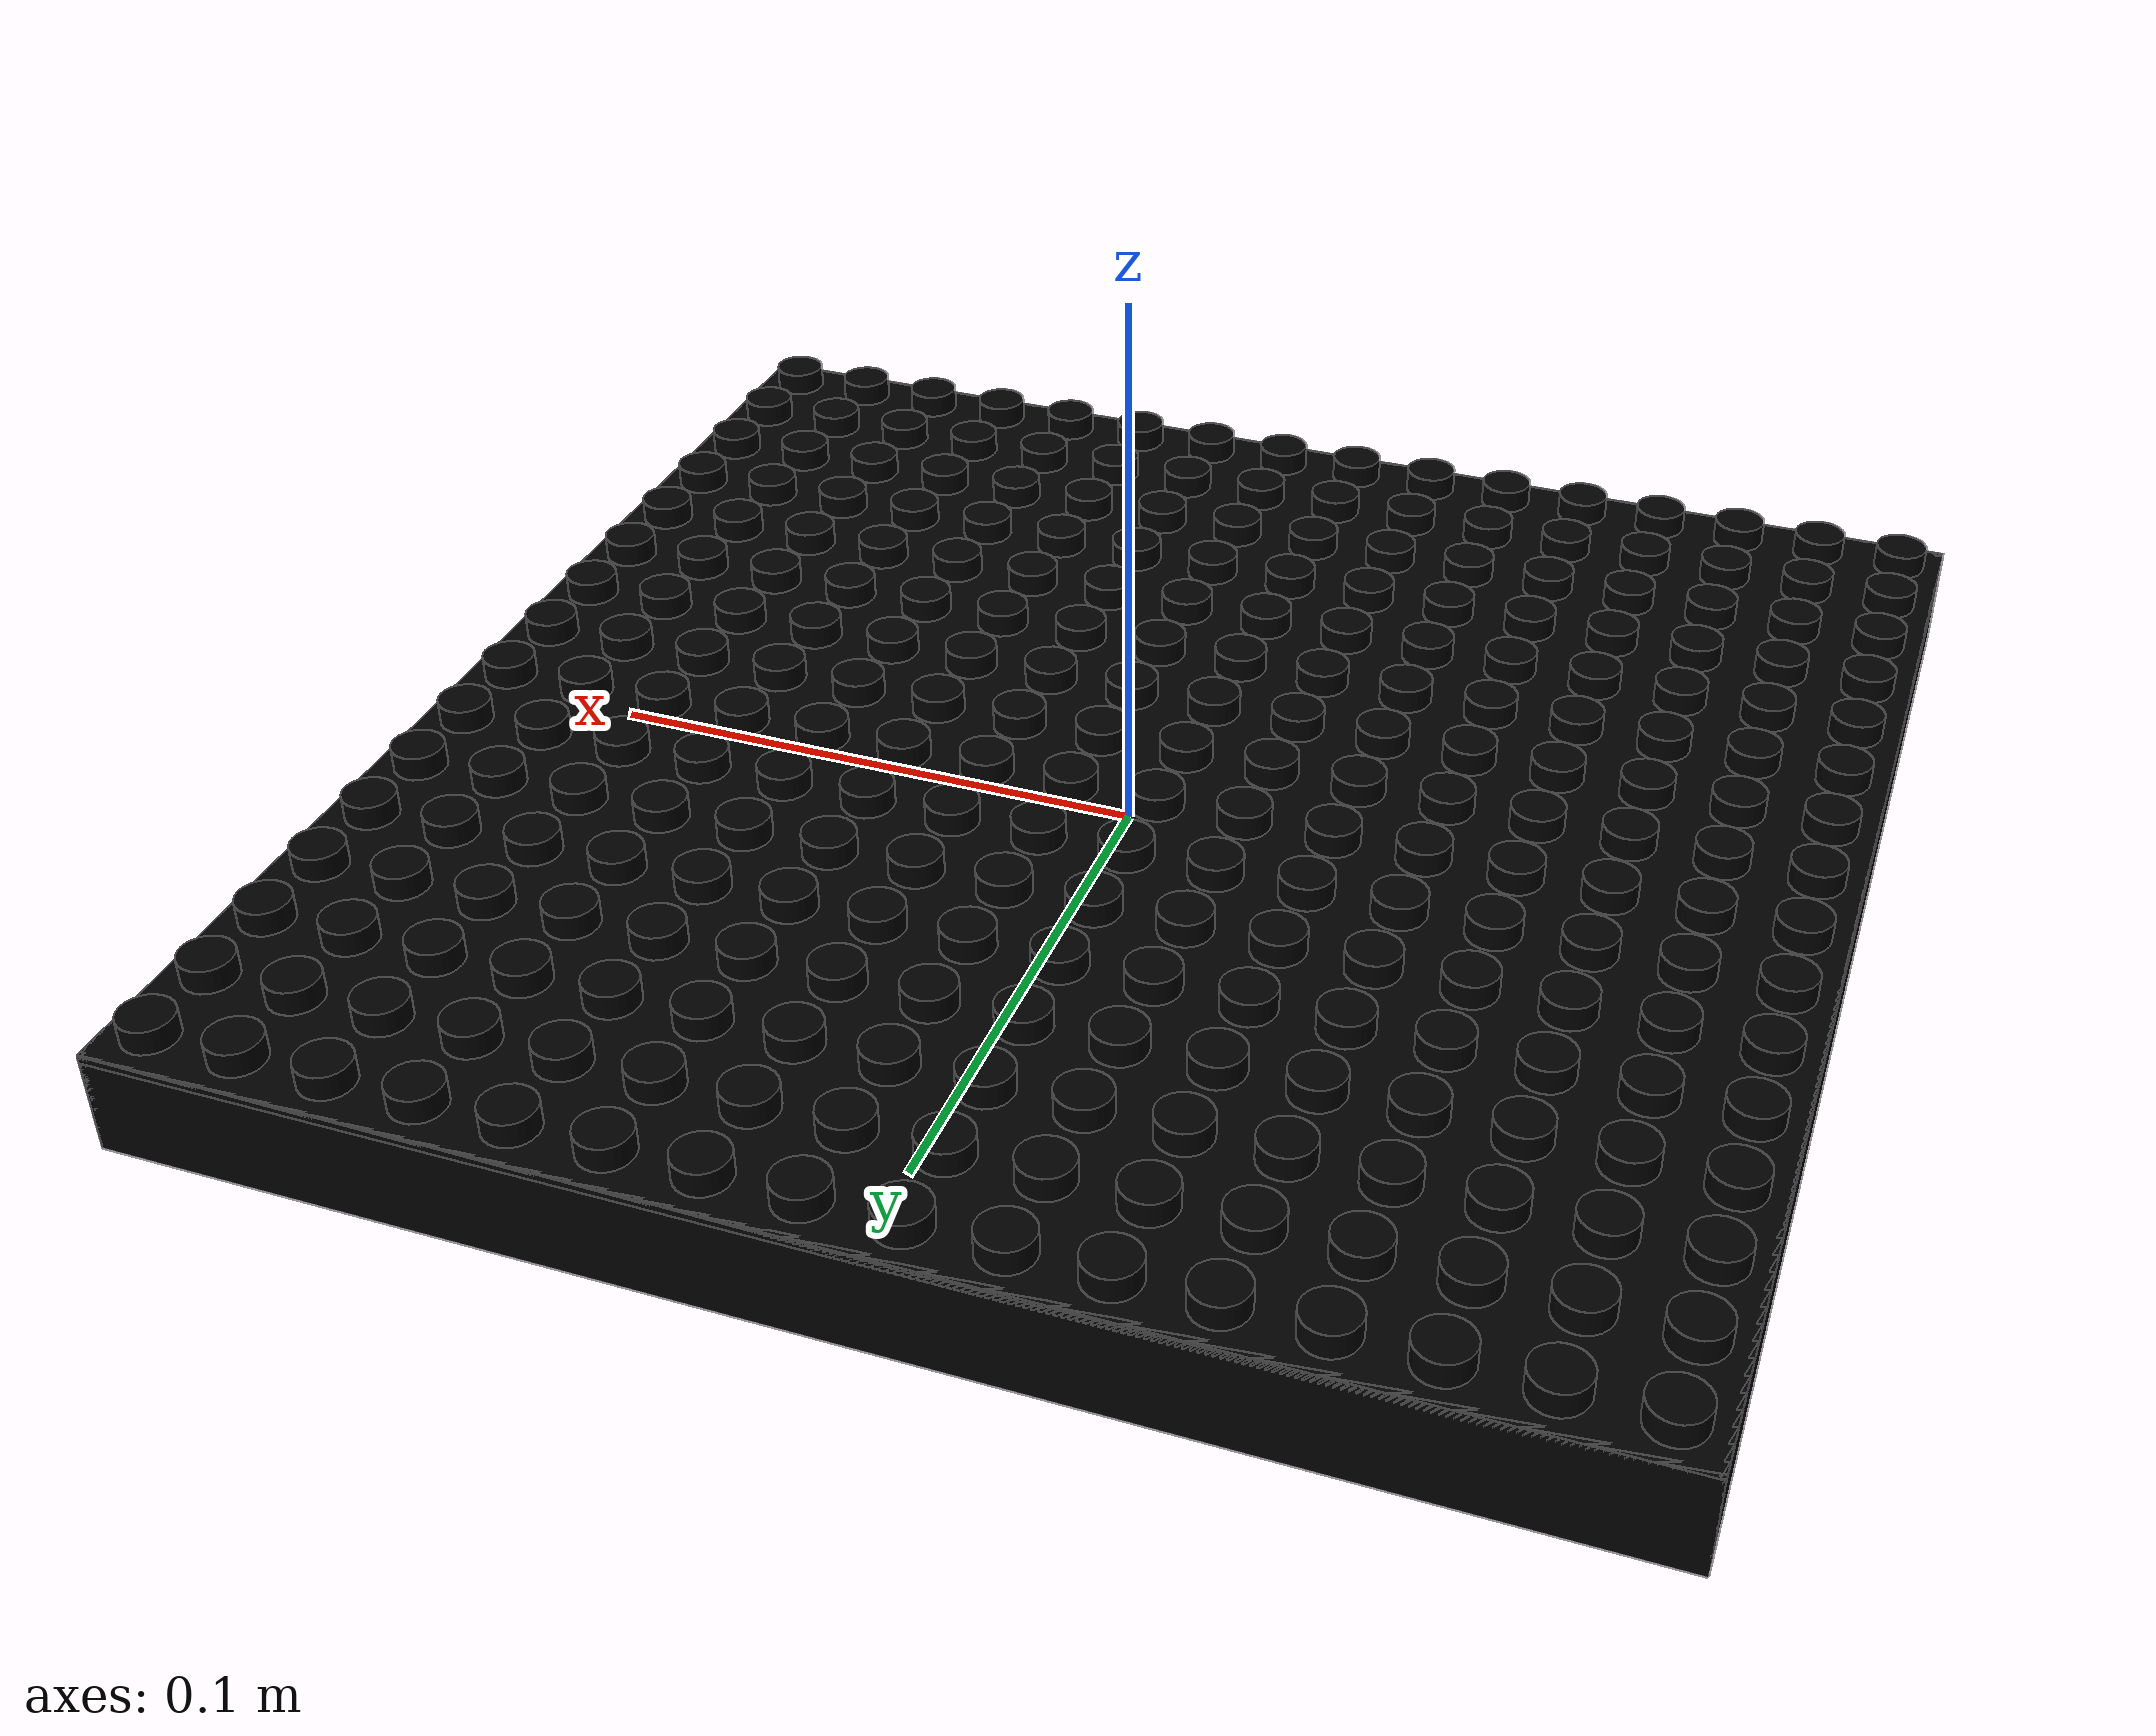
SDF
<?xml version="1.0"?>
<sdf version="1.7">
  <model name="block">
    <link name="block">

      <visual name="left_visual">
        <pose>0.0 0.12725 0.0 0 0 0</pose>
        <geometry>
          <box>
            <size>0.256 0.0015 0.0192</size>
          </box>
        </geometry>
        <material>
          <diffuse>0.0 0.0 0.0 1.0</diffuse>
        </material>
      </visual>
      <collision name="left_collision">
        <pose>0.0 0.12725 0.0 0 0 0</pose>
        <geometry>
          <box>
            <size>0.256 0.0015 0.0192</size>
          </box>
        </geometry>
          <drake:proximity_properties>
              <drake:rigid_hydroelastic/>
              <drake:mesh_resolution_hint>0.5</drake:mesh_resolution_hint>
          </drake:proximity_properties>
      </collision>

      <visual name="right_visual">
        <pose>0.0 -0.12725 0.0 0 0 0</pose>
        <geometry>
          <box>
            <size>0.256 0.0015 0.0192</size>
          </box>
        </geometry>
        <material>
          <diffuse>0.0 0.0 0.0 1.0</diffuse>
        </material>
      </visual>
      <collision name="right_collision">
        <pose>0.0 -0.12725 0.0 0 0 0</pose>
        <geometry>
          <box>
            <size>0.256 0.0015 0.0192</size>
          </box>
        </geometry>
          <drake:proximity_properties>
              <drake:rigid_hydroelastic/>
              <drake:mesh_resolution_hint>0.5</drake:mesh_resolution_hint>
          </drake:proximity_properties>
      </collision>

      <visual name="front_visual">
        <pose>0.12725 0.0 0.0 0 0 0</pose>
        <geometry>
          <box>
            <size>0.0015 0.256 0.0192</size>
          </box>
        </geometry>
        <material>
          <diffuse>0.0 0.0 0.0 1.0</diffuse>
        </material>
      </visual>
      <collision name="front_collision">
        <pose>0.12725 0.0 0.0 0 0 0</pose>
        <geometry>
          <box>
            <size>0.0015 0.256 0.0192</size>
          </box>
        </geometry>
          <drake:proximity_properties>
              <drake:rigid_hydroelastic/>
              <drake:mesh_resolution_hint>0.5</drake:mesh_resolution_hint>
          </drake:proximity_properties>
      </collision>

      <visual name="back_visual">
        <pose>-0.12725 0.0 0.0 0 0 0</pose>
        <geometry>
          <box>
            <size>0.0015 0.256 0.0192</size>
          </box>
        </geometry>
        <material>
          <diffuse>0.0 0.0 0.0 1.0</diffuse>
        </material>
      </visual>
      <collision name="back_collision">
        <pose>-0.12725 0.0 0.0 0 0 0</pose>
        <geometry>
          <box>
            <size>0.0015 0.256 0.0192</size>
          </box>
        </geometry>
          <drake:proximity_properties>
              <drake:rigid_hydroelastic/>
              <drake:mesh_resolution_hint>0.5</drake:mesh_resolution_hint>
          </drake:proximity_properties>
      </collision>

      <visual name="top_visual">
        <pose>0.0 0.0 0.008849999999999998 0 0 0</pose>
        <geometry>
          <box>
            <size>0.256 0.256 0.0015</size>
          </box>
        </geometry>
        <material>
          <diffuse>0.0 0.0 0.0 1.0</diffuse>
        </material>
      </visual>
      <collision name="top_collision">
        <pose>0.0 0.0 0.008849999999999998 0 0 0</pose>
        <geometry>
          <box>
            <size>0.256 0.256 0.0015</size>
          </box>
        </geometry>
          <drake:proximity_properties>
              <drake:rigid_hydroelastic/>
              <drake:mesh_resolution_hint>0.5</drake:mesh_resolution_hint>
          </drake:proximity_properties>
      </collision>

      <visual name="stud_1_1_visual">
        <pose>-0.12000000000000001 -0.12000000000000001 0.01185 0 0 0</pose>
        <geometry>
          <cylinder>
            <radius>0.0048</radius>
            <length>0.0045</length>
          </cylinder>
        </geometry>
        <material>
          <diffuse>0.0 0.0 0.0 1.0</diffuse>
        </material>
      </visual>
      <collision name="stud_1_1_collision">
        <pose>-0.12000000000000001 -0.12000000000000001 0.01185 0 0 0</pose>
        <geometry>
          <cylinder>
            <radius>0.0048</radius>
            <length>0.0045</length>
          </cylinder>
        </geometry>
          <drake:proximity_properties>
              <drake:rigid_hydroelastic/>
              <drake:mesh_resolution_hint>0.5</drake:mesh_resolution_hint>
          </drake:proximity_properties>
      </collision>

      <visual name="stud_1_2_visual">
        <pose>-0.12000000000000001 -0.10400000000000001 0.01185 0 0 0</pose>
        <geometry>
          <cylinder>
            <radius>0.0048</radius>
            <length>0.0045</length>
          </cylinder>
        </geometry>
        <material>
          <diffuse>0.0 0.0 0.0 1.0</diffuse>
        </material>
      </visual>
      <collision name="stud_1_2_collision">
        <pose>-0.12000000000000001 -0.10400000000000001 0.01185 0 0 0</pose>
        <geometry>
          <cylinder>
            <radius>0.0048</radius>
            <length>0.0045</length>
          </cylinder>
        </geometry>
          <drake:proximity_properties>
              <drake:rigid_hydroelastic/>
              <drake:mesh_resolution_hint>0.5</drake:mesh_resolution_hint>
          </drake:proximity_properties>
      </collision>

      <visual name="stud_1_3_visual">
        <pose>-0.12000000000000001 -0.08800000000000001 0.01185 0 0 0</pose>
        <geometry>
          <cylinder>
            <radius>0.0048</radius>
            <length>0.0045</length>
          </cylinder>
        </geometry>
        <material>
          <diffuse>0.0 0.0 0.0 1.0</diffuse>
        </material>
      </visual>
      <collision name="stud_1_3_collision">
        <pose>-0.12000000000000001 -0.08800000000000001 0.01185 0 0 0</pose>
        <geometry>
          <cylinder>
            <radius>0.0048</radius>
            <length>0.0045</length>
          </cylinder>
        </geometry>
          <drake:proximity_properties>
              <drake:rigid_hydroelastic/>
              <drake:mesh_resolution_hint>0.5</drake:mesh_resolution_hint>
          </drake:proximity_properties>
      </collision>

      <visual name="stud_1_4_visual">
        <pose>-0.12000000000000001 -0.07200000000000001 0.01185 0 0 0</pose>
        <geometry>
          <cylinder>
            <radius>0.0048</radius>
            <length>0.0045</length>
          </cylinder>
        </geometry>
        <material>
          <diffuse>0.0 0.0 0.0 1.0</diffuse>
        </material>
      </visual>
      <collision name="stud_1_4_collision">
        <pose>-0.12000000000000001 -0.07200000000000001 0.01185 0 0 0</pose>
        <geometry>
          <cylinder>
            <radius>0.0048</radius>
            <length>0.0045</length>
          </cylinder>
        </geometry>
          <drake:proximity_properties>
              <drake:rigid_hydroelastic/>
              <drake:mesh_resolution_hint>0.5</drake:mesh_resolution_hint>
          </drake:proximity_properties>
      </collision>

      <visual name="stud_1_5_visual">
        <pose>-0.12000000000000001 -0.05600000000000001 0.01185 0 0 0</pose>
        <geometry>
          <cylinder>
            <radius>0.0048</radius>
            <length>0.0045</length>
          </cylinder>
        </geometry>
        <material>
          <diffuse>0.0 0.0 0.0 1.0</diffuse>
        </material>
      </visual>
      <collision name="stud_1_5_collision">
        <pose>-0.12000000000000001 -0.05600000000000001 0.01185 0 0 0</pose>
        <geometry>
          <cylinder>
            <radius>0.0048</radius>
            <length>0.0045</length>
          </cylinder>
        </geometry>
          <drake:proximity_properties>
              <drake:rigid_hydroelastic/>
              <drake:mesh_resolution_hint>0.5</drake:mesh_resolution_hint>
          </drake:proximity_properties>
      </collision>

      <visual name="stud_1_6_visual">
        <pose>-0.12000000000000001 -0.04000000000000001 0.01185 0 0 0</pose>
        <geometry>
          <cylinder>
            <radius>0.0048</radius>
            <length>0.0045</length>
          </cylinder>
        </geometry>
        <material>
          <diffuse>0.0 0.0 0.0 1.0</diffuse>
        </material>
      </visual>
      <collision name="stud_1_6_collision">
        <pose>-0.12000000000000001 -0.04000000000000001 0.01185 0 0 0</pose>
        <geometry>
          <cylinder>
            <radius>0.0048</radius>
            <length>0.0045</length>
          </cylinder>
        </geometry>
          <drake:proximity_properties>
              <drake:rigid_hydroelastic/>
              <drake:mesh_resolution_hint>0.5</drake:mesh_resolution_hint>
          </drake:proximity_properties>
      </collision>

      <visual name="stud_1_7_visual">
        <pose>-0.12000000000000001 -0.024000000000000007 0.01185 0 0 0</pose>
        <geometry>
          <cylinder>
            <radius>0.0048</radius>
            <length>0.0045</length>
          </cylinder>
        </geometry>
        <material>
          <diffuse>0.0 0.0 0.0 1.0</diffuse>
        </material>
      </visual>
      <collision name="stud_1_7_collision">
        <pose>-0.12000000000000001 -0.024000000000000007 0.01185 0 0 0</pose>
        <geometry>
          <cylinder>
            <radius>0.0048</radius>
            <length>0.0045</length>
          </cylinder>
        </geometry>
          <drake:proximity_properties>
              <drake:rigid_hydroelastic/>
              <drake:mesh_resolution_hint>0.5</drake:mesh_resolution_hint>
          </drake:proximity_properties>
      </collision>

      <visual name="stud_1_8_visual">
        <pose>-0.12000000000000001 -0.008000000000000007 0.01185 0 0 0</pose>
        <geometry>
          <cylinder>
            <radius>0.0048</radius>
            <length>0.0045</length>
          </cylinder>
        </geometry>
        <material>
          <diffuse>0.0 0.0 0.0 1.0</diffuse>
        </material>
      </visual>
      <collision name="stud_1_8_collision">
        <pose>-0.12000000000000001 -0.008000000000000007 0.01185 0 0 0</pose>
        <geometry>
          <cylinder>
            <radius>0.0048</radius>
            <length>0.0045</length>
          </cylinder>
        </geometry>
          <drake:proximity_properties>
              <drake:rigid_hydroelastic/>
              <drake:mesh_resolution_hint>0.5</drake:mesh_resolution_hint>
          </drake:proximity_properties>
      </collision>

      <visual name="stud_1_9_visual">
        <pose>-0.12000000000000001 0.008000000000000007 0.01185 0 0 0</pose>
        <geometry>
          <cylinder>
            <radius>0.0048</radius>
            <length>0.0045</length>
          </cylinder>
        </geometry>
        <material>
          <diffuse>0.0 0.0 0.0 1.0</diffuse>
        </material>
      </visual>
      <collision name="stud_1_9_collision">
        <pose>-0.12000000000000001 0.008000000000000007 0.01185 0 0 0</pose>
        <geometry>
          <cylinder>
            <radius>0.0048</radius>
            <length>0.0045</length>
          </cylinder>
        </geometry>
          <drake:proximity_properties>
              <drake:rigid_hydroelastic/>
              <drake:mesh_resolution_hint>0.5</drake:mesh_resolution_hint>
          </drake:proximity_properties>
      </collision>

      <visual name="stud_1_10_visual">
        <pose>-0.12000000000000001 0.023999999999999994 0.01185 0 0 0</pose>
        <geometry>
          <cylinder>
            <radius>0.0048</radius>
            <length>0.0045</length>
          </cylinder>
        </geometry>
        <material>
          <diffuse>0.0 0.0 0.0 1.0</diffuse>
        </material>
      </visual>
      <collision name="stud_1_10_collision">
        <pose>-0.12000000000000001 0.023999999999999994 0.01185 0 0 0</pose>
        <geometry>
          <cylinder>
            <radius>0.0048</radius>
            <length>0.0045</length>
          </cylinder>
        </geometry>
          <drake:proximity_properties>
              <drake:rigid_hydroelastic/>
              <drake:mesh_resolution_hint>0.5</drake:mesh_resolution_hint>
          </drake:proximity_properties>
      </collision>

      <visual name="stud_1_11_visual">
        <pose>-0.12000000000000001 0.03999999999999998 0.01185 0 0 0</pose>
        <geometry>
          <cylinder>
            <radius>0.0048</radius>
            <length>0.0045</length>
          </cylinder>
        </geometry>
        <material>
          <diffuse>0.0 0.0 0.0 1.0</diffuse>
        </material>
      </visual>
      <collision name="stud_1_11_collision">
        <pose>-0.12000000000000001 0.03999999999999998 0.01185 0 0 0</pose>
        <geometry>
          <cylinder>
            <radius>0.0048</radius>
            <length>0.0045</length>
          </cylinder>
        </geometry>
          <drake:proximity_properties>
              <drake:rigid_hydroelastic/>
              <drake:mesh_resolution_hint>0.5</drake:mesh_resolution_hint>
          </drake:proximity_properties>
      </collision>

      <visual name="stud_1_12_visual">
        <pose>-0.12000000000000001 0.055999999999999994 0.01185 0 0 0</pose>
        <geometry>
          <cylinder>
            <radius>0.0048</radius>
            <length>0.0045</length>
          </cylinder>
        </geometry>
        <material>
          <diffuse>0.0 0.0 0.0 1.0</diffuse>
        </material>
      </visual>
      <collision name="stud_1_12_collision">
        <pose>-0.12000000000000001 0.055999999999999994 0.01185 0 0 0</pose>
        <geometry>
          <cylinder>
            <radius>0.0048</radius>
            <length>0.0045</length>
          </cylinder>
        </geometry>
          <drake:proximity_properties>
              <drake:rigid_hydroelastic/>
              <drake:mesh_resolution_hint>0.5</drake:mesh_resolution_hint>
          </drake:proximity_properties>
      </collision>

      <visual name="stud_1_13_visual">
        <pose>-0.12000000000000001 0.07200000000000001 0.01185 0 0 0</pose>
        <geometry>
          <cylinder>
            <radius>0.0048</radius>
            <length>0.0045</length>
          </cylinder>
        </geometry>
        <material>
          <diffuse>0.0 0.0 0.0 1.0</diffuse>
        </material>
      </visual>
      <collision name="stud_1_13_collision">
        <pose>-0.12000000000000001 0.07200000000000001 0.01185 0 0 0</pose>
        <geometry>
          <cylinder>
            <radius>0.0048</radius>
            <length>0.0045</length>
          </cylinder>
        </geometry>
          <drake:proximity_properties>
              <drake:rigid_hydroelastic/>
              <drake:mesh_resolution_hint>0.5</drake:mesh_resolution_hint>
          </drake:proximity_properties>
      </collision>

      <visual name="stud_1_14_visual">
        <pose>-0.12000000000000001 0.088 0.01185 0 0 0</pose>
        <geometry>
          <cylinder>
            <radius>0.0048</radius>
            <length>0.0045</length>
          </cylinder>
        </geometry>
        <material>
          <diffuse>0.0 0.0 0.0 1.0</diffuse>
        </material>
      </visual>
      <collision name="stud_1_14_collision">
        <pose>-0.12000000000000001 0.088 0.01185 0 0 0</pose>
        <geometry>
          <cylinder>
            <radius>0.0048</radius>
            <length>0.0045</length>
          </cylinder>
        </geometry>
          <drake:proximity_properties>
              <drake:rigid_hydroelastic/>
              <drake:mesh_resolution_hint>0.5</drake:mesh_resolution_hint>
          </drake:proximity_properties>
      </collision>

      <visual name="stud_1_15_visual">
        <pose>-0.12000000000000001 0.10399999999999998 0.01185 0 0 0</pose>
        <geometry>
          <cylinder>
            <radius>0.0048</radius>
            <length>0.0045</length>
          </cylinder>
        </geometry>
        <material>
          <diffuse>0.0 0.0 0.0 1.0</diffuse>
        </material>
      </visual>
      <collision name="stud_1_15_collision">
        <pose>-0.12000000000000001 0.10399999999999998 0.01185 0 0 0</pose>
        <geometry>
          <cylinder>
            <radius>0.0048</radius>
            <length>0.0045</length>
          </cylinder>
        </geometry>
          <drake:proximity_properties>
              <drake:rigid_hydroelastic/>
              <drake:mesh_resolution_hint>0.5</drake:mesh_resolution_hint>
          </drake:proximity_properties>
      </collision>

      <visual name="stud_1_16_visual">
        <pose>-0.12000000000000001 0.12 0.01185 0 0 0</pose>
        <geometry>
          <cylinder>
            <radius>0.0048</radius>
            <length>0.0045</length>
          </cylinder>
        </geometry>
        <material>
          <diffuse>0.0 0.0 0.0 1.0</diffuse>
        </material>
      </visual>
      <collision name="stud_1_16_collision">
        <pose>-0.12000000000000001 0.12 0.01185 0 0 0</pose>
        <geometry>
          <cylinder>
            <radius>0.0048</radius>
            <length>0.0045</length>
          </cylinder>
        </geometry>
          <drake:proximity_properties>
              <drake:rigid_hydroelastic/>
              <drake:mesh_resolution_hint>0.5</drake:mesh_resolution_hint>
          </drake:proximity_properties>
      </collision>

      <visual name="stud_2_1_visual">
        <pose>-0.10400000000000001 -0.12000000000000001 0.01185 0 0 0</pose>
        <geometry>
          <cylinder>
            <radius>0.0048</radius>
            <length>0.0045</length>
          </cylinder>
        </geometry>
        <material>
          <diffuse>0.0 0.0 0.0 1.0</diffuse>
        </material>
      </visual>
      <collision name="stud_2_1_collision">
        <pose>-0.10400000000000001 -0.12000000000000001 0.01185 0 0 0</pose>
        <geometry>
          <cylinder>
            <radius>0.0048</radius>
            <length>0.0045</length>
          </cylinder>
        </geometry>
          <drake:proximity_properties>
              <drake:rigid_hydroelastic/>
              <drake:mesh_resolution_hint>0.5</drake:mesh_resolution_hint>
          </drake:proximity_properties>
      </collision>

      <visual name="stud_2_2_visual">
        <pose>-0.10400000000000001 -0.10400000000000001 0.01185 0 0 0</pose>
        <geometry>
          <cylinder>
            <radius>0.0048</radius>
            <length>0.0045</length>
          </cylinder>
        </geometry>
        <material>
          <diffuse>0.0 0.0 0.0 1.0</diffuse>
        </material>
      </visual>
      <collision name="stud_2_2_collision">
        <pose>-0.10400000000000001 -0.10400000000000001 0.01185 0 0 0</pose>
        <geometry>
          <cylinder>
            <radius>0.0048</radius>
            <length>0.0045</length>
          </cylinder>
        </geometry>
          <drake:proximity_properties>
              <drake:rigid_hydroelastic/>
              <drake:mesh_resolution_hint>0.5</drake:mesh_resolution_hint>
          </drake:proximity_properties>
      </collision>

      <visual name="stud_2_3_visual">
        <pose>-0.10400000000000001 -0.08800000000000001 0.01185 0 0 0</pose>
        <geometry>
          <cylinder>
            <radius>0.0048</radius>
            <length>0.0045</length>
          </cylinder>
        </geometry>
        <material>
          <diffuse>0.0 0.0 0.0 1.0</diffuse>
        </material>
      </visual>
      <collision name="stud_2_3_collision">
        <pose>-0.10400000000000001 -0.08800000000000001 0.01185 0 0 0</pose>
        <geometry>
          <cylinder>
            <radius>0.0048</radius>
            <length>0.0045</length>
          </cylinder>
        </geometry>
          <drake:proximity_properties>
              <drake:rigid_hydroelastic/>
              <drake:mesh_resolution_hint>0.5</drake:mesh_resolution_hint>
          </drake:proximity_properties>
      </collision>

      <visual name="stud_2_4_visual">
        <pose>-0.10400000000000001 -0.07200000000000001 0.01185 0 0 0</pose>
        <geometry>
          <cylinder>
            <radius>0.0048</radius>
            <length>0.0045</length>
          </cylinder>
        </geometry>
        <material>
          <diffuse>0.0 0.0 0.0 1.0</diffuse>
        </material>
      </visual>
      <collision name="stud_2_4_collision">
        <pose>-0.10400000000000001 -0.07200000000000001 0.01185 0 0 0</pose>
        <geometry>
          <cylinder>
            <radius>0.0048</radius>
            <length>0.0045</length>
          </cylinder>
        </geometry>
          <drake:proximity_properties>
              <drake:rigid_hydroelastic/>
              <drake:mesh_resolution_hint>0.5</drake:mesh_resolution_hint>
          </drake:proximity_properties>
      </collision>

      <visual name="stud_2_5_visual">
        <pose>-0.10400000000000001 -0.05600000000000001 0.01185 0 0 0</pose>
        <geometry>
          <cylinder>
            <radius>0.0048</radius>
            <length>0.0045</length>
          </cylinder>
        </geometry>
        <material>
          <diffuse>0.0 0.0 0.0 1.0</diffuse>
        </material>
      </visual>
      <collision name="stud_2_5_collision">
        <pose>-0.10400000000000001 -0.05600000000000001 0.01185 0 0 0</pose>
        <geometry>
          <cylinder>
            <radius>0.0048</radius>
            <length>0.0045</length>
          </cylinder>
        </geometry>
          <drake:proximity_properties>
              <drake:rigid_hydroelastic/>
              <drake:mesh_resolution_hint>0.5</drake:mesh_resolution_hint>
          </drake:proximity_properties>
      </collision>

      <visual name="stud_2_6_visual">
        <pose>-0.10400000000000001 -0.04000000000000001 0.01185 0 0 0</pose>
        <geometry>
          <cylinder>
            <radius>0.0048</radius>
            <length>0.0045</length>
          </cylinder>
        </geometry>
        <material>
          <diffuse>0.0 0.0 0.0 1.0</diffuse>
        </material>
      </visual>
      <collision name="stud_2_6_collision">
        <pose>-0.10400000000000001 -0.04000000000000001 0.01185 0 0 0</pose>
        <geometry>
          <cylinder>
            <radius>0.0048</radius>
            <length>0.0045</length>
          </cylinder>
        </geometry>
          <drake:proximity_properties>
              <drake:rigid_hydroelastic/>
              <drake:mesh_resolution_hint>0.5</drake:mesh_resolution_hint>
          </drake:proximity_properties>
      </collision>

      <visual name="stud_2_7_visual">
        <pose>-0.10400000000000001 -0.024000000000000007 0.01185 0 0 0</pose>
        <geometry>
          <cylinder>
            <radius>0.0048</radius>
            <length>0.0045</length>
          </cylinder>
        </geometry>
        <material>
          <diffuse>0.0 0.0 0.0 1.0</diffuse>
        </material>
      </visual>
      <collision name="stud_2_7_collision">
        <pose>-0.10400000000000001 -0.024000000000000007 0.01185 0 0 0</pose>
        <geometry>
          <cylinder>
            <radius>0.0048</radius>
            <length>0.0045</length>
          </cylinder>
        </geometry>
          <drake:proximity_properties>
              <drake:rigid_hydroelastic/>
              <drake:mesh_resolution_hint>0.5</drake:mesh_resolution_hint>
          </drake:proximity_properties>
      </collision>

      <visual name="stud_2_8_visual">
        <pose>-0.10400000000000001 -0.008000000000000007 0.01185 0 0 0</pose>
        <geometry>
          <cylinder>
            <radius>0.0048</radius>
            <length>0.0045</length>
          </cylinder>
        </geometry>
        <material>
          <diffuse>0.0 0.0 0.0 1.0</diffuse>
        </material>
      </visual>
      <collision name="stud_2_8_collision">
        <pose>-0.10400000000000001 -0.008000000000000007 0.01185 0 0 0</pose>
        <geometry>
          <cylinder>
            <radius>0.0048</radius>
            <length>0.0045</length>
          </cylinder>
        </geometry>
          <drake:proximity_properties>
              <drake:rigid_hydroelastic/>
              <drake:mesh_resolution_hint>0.5</drake:mesh_resolution_hint>
          </drake:proximity_properties>
      </collision>

      <visual name="stud_2_9_visual">
        <pose>-0.10400000000000001 0.008000000000000007 0.01185 0 0 0</pose>
        <geometry>
          <cylinder>
            <radius>0.0048</radius>
            <length>0.0045</length>
          </cylinder>
        </geometry>
        <material>
          <diffuse>0.0 0.0 0.0 1.0</diffuse>
        </material>
      </visual>
      <collision name="stud_2_9_collision">
        <pose>-0.10400000000000001 0.008000000000000007 0.01185 0 0 0</pose>
        <geometry>
          <cylinder>
            <radius>0.0048</radius>
            <length>0.0045</length>
          </cylinder>
        </geometry>
          <drake:proximity_properties>
              <drake:rigid_hydroelastic/>
              <drake:mesh_resolution_hint>0.5</drake:mesh_resolution_hint>
          </drake:proximity_properties>
      </collision>

      <visual name="stud_2_10_visual">
        <pose>-0.10400000000000001 0.023999999999999994 0.01185 0 0 0</pose>
        <geometry>
          <cylinder>
            <radius>0.0048</radius>
            <length>0.0045</length>
          </cylinder>
        </geometry>
        <material>
          <diffuse>0.0 0.0 0.0 1.0</diffuse>
        </material>
      </visual>
      <collision name="stud_2_10_collision">
        <pose>-0.10400000000000001 0.023999999999999994 0.01185 0 0 0</pose>
        <geometry>
          <cylinder>
            <radius>0.0048</radius>
            <length>0.0045</length>
          </cylinder>
        </geometry>
          <drake:proximity_properties>
              <drake:rigid_hydroelastic/>
              <drake:mesh_resolution_hint>0.5</drake:mesh_resolution_hint>
          </drake:proximity_properties>
      </collision>

      <visual name="stud_2_11_visual">
        <pose>-0.10400000000000001 0.03999999999999998 0.01185 0 0 0</pose>
        <geometry>
          <cylinder>
            <radius>0.0048</radius>
            <length>0.0045</length>
          </cylinder>
        </geometry>
        <material>
          <diffuse>0.0 0.0 0.0 1.0</diffuse>
        </material>
      </visual>
      <collision name="stud_2_11_collision">
        <pose>-0.10400000000000001 0.03999999999999998 0.01185 0 0 0</pose>
        <geometry>
          <cylinder>
            <radius>0.0048</radius>
            <length>0.0045</length>
          </cylinder>
        </geometry>
          <drake:proximity_properties>
              <drake:rigid_hydroelastic/>
              <drake:mesh_resolution_hint>0.5</drake:mesh_resolution_hint>
          </drake:proximity_properties>
      </collision>

      <visual name="stud_2_12_visual">
        <pose>-0.10400000000000001 0.055999999999999994 0.01185 0 0 0</pose>
        <geometry>
          <cylinder>
            <radius>0.0048</radius>
            <length>0.0045</length>
          </cylinder>
        </geometry>
        <material>
          <diffuse>0.0 0.0 0.0 1.0</diffuse>
        </material>
      </visual>
      <collision name="stud_2_12_collision">
        <pose>-0.10400000000000001 0.055999999999999994 0.01185 0 0 0</pose>
        <geometry>
          <cylinder>
            <radius>0.0048</radius>
            <length>0.0045</length>
          </cylinder>
        </geometry>
          <drake:proximity_properties>
              <drake:rigid_hydroelastic/>
              <drake:mesh_resolution_hint>0.5</drake:mesh_resolution_hint>
          </drake:proximity_properties>
      </collision>

      <visual name="stud_2_13_visual">
        <pose>-0.10400000000000001 0.07200000000000001 0.01185 0 0 0</pose>
        <geometry>
          <cylinder>
            <radius>0.0048</radius>
            <length>0.0045</length>
          </cylinder>
        </geometry>
        <material>
          <diffuse>0.0 0.0 0.0 1.0</diffuse>
        </material>
      </visual>
      <collision name="stud_2_13_collision">
        <pose>-0.10400000000000001 0.07200000000000001 0.01185 0 0 0</pose>
        <geometry>
          <cylinder>
            <radius>0.0048</radius>
            <length>0.0045</length>
          </cylinder>
        </geometry>
          <drake:proximity_properties>
              <drake:rigid_hydroelastic/>
              <drake:mesh_resolution_hint>0.5</drake:mesh_resolution_hint>
          </drake:proximity_properties>
      </collision>

      <visual name="stud_2_14_visual">
        <pose>-0.10400000000000001 0.088 0.01185 0 0 0</pose>
        <geometry>
          <cylinder>
            <radius>0.0048</radius>
            <length>0.0045</length>
          </cylinder>
        </geometry>
        <material>
          <diffuse>0.0 0.0 0.0 1.0</diffuse>
        </material>
      </visual>
      <collision name="stud_2_14_collision">
        <pose>-0.10400000000000001 0.088 0.01185 0 0 0</pose>
        <geometry>
          <cylinder>
            <radius>0.0048</radius>
            <length>0.0045</length>
          </cylinder>
        </geometry>
          <drake:proximity_properties>
              <drake:rigid_hydroelastic/>
              <drake:mesh_resolution_hint>0.5</drake:mesh_resolution_hint>
          </drake:proximity_properties>
      </collision>

      <visual name="stud_2_15_visual">
        <pose>-0.10400000000000001 0.10399999999999998 0.01185 0 0 0</pose>
        <geometry>
          <cylinder>
            <radius>0.0048</radius>
            <length>0.0045</length>
          </cylinder>
        </geometry>
        <material>
          <diffuse>0.0 0.0 0.0 1.0</diffuse>
        </material>
      </visual>
      <collision name="stud_2_15_collision">
        <pose>-0.10400000000000001 0.10399999999999998 0.01185 0 0 0</pose>
        <geometry>
          <cylinder>
            <radius>0.0048</radius>
            <length>0.0045</length>
          </cylinder>
        </geometry>
          <drake:proximity_properties>
              <drake:rigid_hydroelastic/>
              <drake:mesh_resolution_hint>0.5</drake:mesh_resolution_hint>
          </drake:proximity_properties>
      </collision>

      <visual name="stud_2_16_visual">
        <pose>-0.10400000000000001 0.12 0.01185 0 0 0</pose>
        <geometry>
          <cylinder>
            <radius>0.0048</radius>
            <length>0.0045</length>
          </cylinder>
        </geometry>
        <material>
          <diffuse>0.0 0.0 0.0 1.0</diffuse>
        </material>
      </visual>
      <collision name="stud_2_16_collision">
        <pose>-0.10400000000000001 0.12 0.01185 0 0 0</pose>
        <geometry>
          <cylinder>
            <radius>0.0048</radius>
            <length>0.0045</length>
          </cylinder>
        </geometry>
          <drake:proximity_properties>
              <drake:rigid_hydroelastic/>
              <drake:mesh_resolution_hint>0.5</drake:mesh_resolution_hint>
          </drake:proximity_properties>
      </collision>

      <visual name="stud_3_1_visual">
        <pose>-0.08800000000000001 -0.12000000000000001 0.01185 0 0 0</pose>
        <geometry>
          <cylinder>
            <radius>0.0048</radius>
            <length>0.0045</length>
          </cylinder>
        </geometry>
        <material>
          <diffuse>0.0 0.0 0.0 1.0</diffuse>
        </material>
      </visual>
      <collision name="stud_3_1_collision">
        <pose>-0.08800000000000001 -0.12000000000000001 0.01185 0 0 0</pose>
        <geometry>
          <cylinder>
            <radius>0.0048</radius>
            <length>0.0045</length>
          </cylinder>
        </geometry>
          <drake:proximity_properties>
              <drake:rigid_hydroelastic/>
              <drake:mesh_resolution_hint>0.5</drake:mesh_resolution_hint>
          </drake:proximity_properties>
      </collision>

      <visual name="stud_3_2_visual">
        <pose>-0.08800000000000001 -0.10400000000000001 0.01185 0 0 0</pose>
        <geometry>
          <cylinder>
            <radius>0.0048</radius>
            <length>0.0045</length>
          </cylinder>
        </geometry>
        <material>
          <diffuse>0.0 0.0 0.0 1.0</diffuse>
        </material>
      </visual>
      <collision name="stud_3_2_collision">
        <pose>-0.08800000000000001 -0.10400000000000001 0.01185 0 0 0</pose>
        <geometry>
          <cylinder>
            <radius>0.0048</radius>
            <length>0.0045</length>
          </cylinder>
        </geometry>
          <drake:proximity_properties>
              <drake:rigid_hydroelastic/>
              <drake:mesh_resolution_hint>0.5</drake:mesh_resolution_hint>
          </drake:proximity_properties>
      </collision>

      <visual name="stud_3_3_visual">
        <pose>-0.08800000000000001 -0.08800000000000001 0.01185 0 0 0</pose>
        <geometry>
          <cylinder>
            <radius>0.0048</radius>
            <length>0.0045</length>
          </cylinder>
        </geometry>
        <material>
          <diffuse>0.0 0.0 0.0 1.0</diffuse>
        </material>
      </visual>
      <collision name="stud_3_3_collision">
        <pose>-0.08800000000000001 -0.08800000000000001 0.01185 0 0 0</pose>
        <geometry>
          <cylinder>
            <radius>0.0048</radius>
            <length>0.0045</length>
          </cylinder>
        </geometry>
          <drake:proximity_properties>
              <drake:rigid_hydroelastic/>
              <drake:mesh_resolution_hint>0.5</drake:mesh_resolution_hint>
          </drake:proximity_properties>
      </collision>

      <visual name="stud_3_4_visual">
        <pose>-0.08800000000000001 -0.07200000000000001 0.01185 0 0 0</pose>
        <geometry>
          <cylinder>
            <radius>0.0048</radius>
            <length>0.0045</length>
          </cylinder>
        </geometry>
        <material>
          <diffuse>0.0 0.0 0.0 1.0</diffuse>
        </material>
      </visual>
      <collision name="stud_3_4_collision">
        <pose>-0.08800000000000001 -0.07200000000000001 0.01185 0 0 0</pose>
        <geometry>
          <cylinder>
            <radius>0.0048</radius>
            <length>0.0045</length>
          </cylinder>
        </geometry>
          <drake:proximity_properties>
              <drake:rigid_hydroelastic/>
              <drake:mesh_resolution_hint>0.5</drake:mesh_resolution_hint>
          </drake:proximity_properties>
      </collision>

      <visual name="stud_3_5_visual">
        <pose>-0.08800000000000001 -0.05600000000000001 0.01185 0 0 0</pose>
        <geometry>
          <cylinder>
            <radius>0.0048</radius>
            <length>0.0045</length>
          </cylinder>
        </geometry>
        <material>
          <diffuse>0.0 0.0 0.0 1.0</diffuse>
        </material>
      </visual>
      <collision name="stud_3_5_collision">
        <pose>-0.08800000000000001 -0.05600000000000001 0.01185 0 0 0</pose>
        <geometry>
          <cylinder>
            <radius>0.0048</radius>
            <length>0.0045</length>
          </cylinder>
        </geometry>
          <drake:proximity_properties>
              <drake:rigid_hydroelastic/>
              <drake:mesh_resolution_hint>0.5</drake:mesh_resolution_hint>
          </drake:proximity_properties>
      </collision>

      <visual name="stud_3_6_visual">
        <pose>-0.08800000000000001 -0.04000000000000001 0.01185 0 0 0</pose>
        <geometry>
          <cylinder>
            <radius>0.0048</radius>
            <length>0.0045</length>
          </cylinder>
        </geometry>
        <material>
          <diffuse>0.0 0.0 0.0 1.0</diffuse>
        </material>
      </visual>
      <collision name="stud_3_6_collision">
        <pose>-0.08800000000000001 -0.04000000000000001 0.01185 0 0 0</pose>
        <geometry>
          <cylinder>
            <radius>0.0048</radius>
            <length>0.0045</length>
          </cylinder>
        </geometry>
          <drake:proximity_properties>
              <drake:rigid_hydroelastic/>
              <drake:mesh_resolution_hint>0.5</drake:mesh_resolution_hint>
          </drake:proximity_properties>
      </collision>

      <visual name="stud_3_7_visual">
        <pose>-0.08800000000000001 -0.024000000000000007 0.01185 0 0 0</pose>
        <geometry>
          <cylinder>
            <radius>0.0048</radius>
            <length>0.0045</length>
          </cylinder>
        </geometry>
        <material>
          <diffuse>0.0 0.0 0.0 1.0</diffuse>
        </material>
      </visual>
      <collision name="stud_3_7_collision">
        <pose>-0.08800000000000001 -0.024000000000000007 0.01185 0 0 0</pose>
        <geometry>
          <cylinder>
            <radius>0.0048</radius>
            <length>0.0045</length>
          </cylinder>
        </geometry>
          <drake:proximity_properties>
              <drake:rigid_hydroelastic/>
              <drake:mesh_resolution_hint>0.5</drake:mesh_resolution_hint>
          </drake:proximity_properties>
      </collision>

      <visual name="stud_3_8_visual">
        <pose>-0.08800000000000001 -0.008000000000000007 0.01185 0 0 0</pose>
        <geometry>
          <cylinder>
            <radius>0.0048</radius>
            <length>0.0045</length>
          </cylinder>
        </geometry>
        <material>
          <diffuse>0.0 0.0 0.0 1.0</diffuse>
        </material>
      </visual>
      <collision name="stud_3_8_collision">
        <pose>-0.08800000000000001 -0.008000000000000007 0.01185 0 0 0</pose>
        <geometry>
          <cylinder>
            <radius>0.0048</radius>
            <length>0.0045</length>
          </cylinder>
        </geometry>
          <drake:proximity_properties>
              <drake:rigid_hydroelastic/>
              <drake:mesh_resolution_hint>0.5</drake:mesh_resolution_hint>
          </drake:proximity_properties>
      </collision>

      <visual name="stud_3_9_visual">
        <pose>-0.08800000000000001 0.008000000000000007 0.01185 0 0 0</pose>
        <geometry>
          <cylinder>
            <radius>0.0048</radius>
            <length>0.0045</length>
          </cylinder>
        </geometry>
        <material>
          <diffuse>0.0 0.0 0.0 1.0</diffuse>
        </material>
      </visual>
      <collision name="stud_3_9_collision">
        <pose>-0.08800000000000001 0.008000000000000007 0.01185 0 0 0</pose>
        <geometry>
          <cylinder>
            <radius>0.0048</radius>
            <length>0.0045</length>
          </cylinder>
        </geometry>
          <drake:proximity_properties>
              <drake:rigid_hydroelastic/>
              <drake:mesh_resolution_hint>0.5</drake:mesh_resolution_hint>
          </drake:proximity_properties>
      </collision>

      <visual name="stud_3_10_visual">
        <pose>-0.08800000000000001 0.023999999999999994 0.01185 0 0 0</pose>
        <geometry>
          <cylinder>
            <radius>0.0048</radius>
            <length>0.0045</length>
          </cylinder>
        </geometry>
        <material>
          <diffuse>0.0 0.0 0.0 1.0</diffuse>
        </material>
      </visual>
      <collision name="stud_3_10_collision">
        <pose>-0.08800000000000001 0.023999999999999994 0.01185 0 0 0</pose>
        <geometry>
          <cylinder>
            <radius>0.0048</radius>
            <length>0.0045</length>
          </cylinder>
        </geometry>
          <drake:proximity_properties>
              <drake:rigid_hydroelastic/>
              <drake:mesh_resolution_hint>0.5</drake:mesh_resolution_hint>
          </drake:proximity_properties>
      </collision>

      <visual name="stud_3_11_visual">
        <pose>-0.08800000000000001 0.03999999999999998 0.01185 0 0 0</pose>
        <geometry>
          <cylinder>
            <radius>0.0048</radius>
            <length>0.0045</length>
          </cylinder>
        </geometry>
        <material>
          <diffuse>0.0 0.0 0.0 1.0</diffuse>
        </material>
      </visual>
      <collision name="stud_3_11_collision">
        <pose>-0.08800000000000001 0.03999999999999998 0.01185 0 0 0</pose>
        <geometry>
          <cylinder>
            <radius>0.0048</radius>
            <length>0.0045</length>
          </cylinder>
        </geometry>
          <drake:proximity_properties>
              <drake:rigid_hydroelastic/>
              <drake:mesh_resolution_hint>0.5</drake:mesh_resolution_hint>
          </drake:proximity_properties>
      </collision>

      <visual name="stud_3_12_visual">
        <pose>-0.08800000000000001 0.055999999999999994 0.01185 0 0 0</pose>
        <geometry>
          <cylinder>
            <radius>0.0048</radius>
            <length>0.0045</length>
          </cylinder>
        </geometry>
        <material>
          <diffuse>0.0 0.0 0.0 1.0</diffuse>
        </material>
      </visual>
      <collision name="stud_3_12_collision">
        <pose>-0.08800000000000001 0.055999999999999994 0.01185 0 0 0</pose>
        <geometry>
          <cylinder>
            <radius>0.0048</radius>
            <length>0.0045</length>
          </cylinder>
        </geometry>
          <drake:proximity_properties>
              <drake:rigid_hydroelastic/>
              <drake:mesh_resolution_hint>0.5</drake:mesh_resolution_hint>
          </drake:proximity_properties>
      </collision>

      <visual name="stud_3_13_visual">
        <pose>-0.08800000000000001 0.07200000000000001 0.01185 0 0 0</pose>
        <geometry>
          <cylinder>
            <radius>0.0048</radius>
            <length>0.0045</length>
          </cylinder>
        </geometry>
        <material>
          <diffuse>0.0 0.0 0.0 1.0</diffuse>
        </material>
      </visual>
      <collision name="stud_3_13_collision">
        <pose>-0.08800000000000001 0.07200000000000001 0.01185 0 0 0</pose>
        <geometry>
          <cylinder>
            <radius>0.0048</radius>
            <length>0.0045</length>
          </cylinder>
        </geometry>
          <drake:proximity_properties>
              <drake:rigid_hydroelastic/>
              <drake:mesh_resolution_hint>0.5</drake:mesh_resolution_hint>
          </drake:proximity_properties>
      </collision>

      <visual name="stud_3_14_visual">
        <pose>-0.08800000000000001 0.088 0.01185 0 0 0</pose>
        <geometry>
          <cylinder>
            <radius>0.0048</radius>
            <length>0.0045</length>
          </cylinder>
        </geometry>
        <material>
          <diffuse>0.0 0.0 0.0 1.0</diffuse>
        </material>
      </visual>
      <collision name="stud_3_14_collision">
        <pose>-0.08800000000000001 0.088 0.01185 0 0 0</pose>
        <geometry>
          <cylinder>
            <radius>0.0048</radius>
            <length>0.0045</length>
          </cylinder>
        </geometry>
          <drake:proximity_properties>
              <drake:rigid_hydroelastic/>
              <drake:mesh_resolution_hint>0.5</drake:mesh_resolution_hint>
          </drake:proximity_properties>
      </collision>

      <visual name="stud_3_15_visual">
        <pose>-0.08800000000000001 0.10399999999999998 0.01185 0 0 0</pose>
        <geometry>
          <cylinder>
            <radius>0.0048</radius>
            <length>0.0045</length>
          </cylinder>
        </geometry>
        <material>
          <diffuse>0.0 0.0 0.0 1.0</diffuse>
        </material>
      </visual>
      <collision name="stud_3_15_collision">
        <pose>-0.08800000000000001 0.10399999999999998 0.01185 0 0 0</pose>
        <geometry>
          <cylinder>
            <radius>0.0048</radius>
            <length>0.0045</length>
          </cylinder>
        </geometry>
          <drake:proximity_properties>
              <drake:rigid_hydroelastic/>
              <drake:mesh_resolution_hint>0.5</drake:mesh_resolution_hint>
          </drake:proximity_properties>
      </collision>

      <visual name="stud_3_16_visual">
        <pose>-0.08800000000000001 0.12 0.01185 0 0 0</pose>
        <geometry>
          <cylinder>
            <radius>0.0048</radius>
            <length>0.0045</length>
          </cylinder>
        </geometry>
        <material>
          <diffuse>0.0 0.0 0.0 1.0</diffuse>
        </material>
      </visual>
      <collision name="stud_3_16_collision">
        <pose>-0.08800000000000001 0.12 0.01185 0 0 0</pose>
        <geometry>
          <cylinder>
            <radius>0.0048</radius>
            <length>0.0045</length>
          </cylinder>
        </geometry>
          <drake:proximity_properties>
              <drake:rigid_hydroelastic/>
              <drake:mesh_resolution_hint>0.5</drake:mesh_resolution_hint>
          </drake:proximity_properties>
      </collision>

      <visual name="stud_4_1_visual">
        <pose>-0.07200000000000001 -0.12000000000000001 0.01185 0 0 0</pose>
        <geometry>
          <cylinder>
            <radius>0.0048</radius>
            <length>0.0045</length>
          </cylinder>
        </geometry>
        <material>
          <diffuse>0.0 0.0 0.0 1.0</diffuse>
        </material>
      </visual>
      <collision name="stud_4_1_collision">
        <pose>-0.07200000000000001 -0.12000000000000001 0.01185 0 0 0</pose>
        <geometry>
          <cylinder>
            <radius>0.0048</radius>
            <length>0.0045</length>
          </cylinder>
        </geometry>
          <drake:proximity_properties>
              <drake:rigid_hydroelastic/>
              <drake:mesh_resolution_hint>0.5</drake:mesh_resolution_hint>
          </drake:proximity_properties>
      </collision>

      <visual name="stud_4_2_visual">
        <pose>-0.07200000000000001 -0.10400000000000001 0.01185 0 0 0</pose>
        <geometry>
          <cylinder>
            <radius>0.0048</radius>
            <length>0.0045</length>
          </cylinder>
        </geometry>
        <material>
          <diffuse>0.0 0.0 0.0 1.0</diffuse>
        </material>
      </visual>
      <collision name="stud_4_2_collision">
        <pose>-0.07200000000000001 -0.10400000000000001 0.01185 0 0 0</pose>
        <geometry>
          <cylinder>
            <radius>0.0048</radius>
            <length>0.0045</length>
          </cylinder>
        </geometry>
          <drake:proximity_properties>
              <drake:rigid_hydroelastic/>
              <drake:mesh_resolution_hint>0.5</drake:mesh_resolution_hint>
          </drake:proximity_properties>
      </collision>

      <visual name="stud_4_3_visual">
        <pose>-0.07200000000000001 -0.08800000000000001 0.01185 0 0 0</pose>
        <geometry>
          <cylinder>
            <radius>0.0048</radius>
            <length>0.0045</length>
          </cylinder>
        </geometry>
        <material>
          <diffuse>0.0 0.0 0.0 1.0</diffuse>
        </material>
      </visual>
      <collision name="stud_4_3_collision">
        <pose>-0.07200000000000001 -0.08800000000000001 0.01185 0 0 0</pose>
        <geometry>
          <cylinder>
            <radius>0.0048</radius>
            <length>0.0045</length>
          </cylinder>
        </geometry>
          <drake:proximity_properties>
              <drake:rigid_hydroelastic/>
              <drake:mesh_resolution_hint>0.5</drake:mesh_resolution_hint>
          </drake:proximity_properties>
      </collision>

      <visual name="stud_4_4_visual">
        <pose>-0.07200000000000001 -0.07200000000000001 0.01185 0 0 0</pose>
        <geometry>
          <cylinder>
            <radius>0.0048</radius>
            <length>0.0045</length>
          </cylinder>
        </geometry>
        <material>
          <diffuse>0.0 0.0 0.0 1.0</diffuse>
        </material>
      </visual>
      <collision name="stud_4_4_collision">
        <pose>-0.07200000000000001 -0.07200000000000001 0.01185 0 0 0</pose>
        <geometry>
          <cylinder>
            <radius>0.0048</radius>
            <length>0.0045</length>
          </cylinder>
        </geometry>
          <drake:proximity_properties>
              <drake:rigid_hydroelastic/>
              <drake:mesh_resolution_hint>0.5</drake:mesh_resolution_hint>
          </drake:proximity_properties>
      </collision>

      <visual name="stud_4_5_visual">
        <pose>-0.07200000000000001 -0.05600000000000001 0.01185 0 0 0</pose>
        <geometry>
          <cylinder>
            <radius>0.0048</radius>
            <length>0.0045</length>
          </cylinder>
        </geometry>
        <material>
          <diffuse>0.0 0.0 0.0 1.0</diffuse>
        </material>
      </visual>
      <collision name="stud_4_5_collision">
        <pose>-0.07200000000000001 -0.05600000000000001 0.01185 0 0 0</pose>
        <geometry>
          <cylinder>
            <radius>0.0048</radius>
            <length>0.0045</length>
          </cylinder>
        </geometry>
          <drake:proximity_properties>
              <drake:rigid_hydroelastic/>
              <drake:mesh_resolution_hint>0.5</drake:mesh_resolution_hint>
          </drake:proximity_properties>
      </collision>

      <visual name="stud_4_6_visual">
        <pose>-0.07200000000000001 -0.04000000000000001 0.01185 0 0 0</pose>
        <geometry>
          <cylinder>
            <radius>0.0048</radius>
            <length>0.0045</length>
          </cylinder>
        </geometry>
        <material>
          <diffuse>0.0 0.0 0.0 1.0</diffuse>
        </material>
      </visual>
      <collision name="stud_4_6_collision">
        <pose>-0.07200000000000001 -0.04000000000000001 0.01185 0 0 0</pose>
        <geometry>
          <cylinder>
            <radius>0.0048</radius>
            <length>0.0045</length>
          </cylinder>
        </geometry>
          <drake:proximity_properties>
              <drake:rigid_hydroelastic/>
              <drake:mesh_resolution_hint>0.5</drake:mesh_resolution_hint>
          </drake:proximity_properties>
      </collision>

      <visual name="stud_4_7_visual">
        <pose>-0.07200000000000001 -0.024000000000000007 0.01185 0 0 0</pose>
        <geometry>
          <cylinder>
            <radius>0.0048</radius>
            <length>0.0045</length>
          </cylinder>
        </geometry>
        <material>
          <diffuse>0.0 0.0 0.0 1.0</diffuse>
        </material>
      </visual>
      <collision name="stud_4_7_collision">
        <pose>-0.07200000000000001 -0.024000000000000007 0.01185 0 0 0</pose>
        <geometry>
          <cylinder>
            <radius>0.0048</radius>
            <length>0.0045</length>
          </cylinder>
        </geometry>
          <drake:proximity_properties>
              <drake:rigid_hydroelastic/>
              <drake:mesh_resolution_hint>0.5</drake:mesh_resolution_hint>
          </drake:proximity_properties>
      </collision>

      <visual name="stud_4_8_visual">
        <pose>-0.07200000000000001 -0.008000000000000007 0.01185 0 0 0</pose>
        <geometry>
          <cylinder>
            <radius>0.0048</radius>
            <length>0.0045</length>
          </cylinder>
        </geometry>
        <material>
          <diffuse>0.0 0.0 0.0 1.0</diffuse>
        </material>
      </visual>
      <collision name="stud_4_8_collision">
        <pose>-0.07200000000000001 -0.008000000000000007 0.01185 0 0 0</pose>
        <geometry>
          <cylinder>
            <radius>0.0048</radius>
            <length>0.0045</length>
          </cylinder>
        </geometry>
          <drake:proximity_properties>
              <drake:rigid_hydroelastic/>
              <drake:mesh_resolution_hint>0.5</drake:mesh_resolution_hint>
          </drake:proximity_properties>
      </collision>

      <visual name="stud_4_9_visual">
        <pose>-0.07200000000000001 0.008000000000000007 0.01185 0 0 0</pose>
        <geometry>
          <cylinder>
            <radius>0.0048</radius>
            <length>0.0045</length>
          </cylinder>
        </geometry>
        <material>
          <diffuse>0.0 0.0 0.0 1.0</diffuse>
        </material>
      </visual>
      <collision name="stud_4_9_collision">
        <pose>-0.07200000000000001 0.008000000000000007 0.01185 0 0 0</pose>
        <geometry>
          <cylinder>
            <radius>0.0048</radius>
            <length>0.0045</length>
          </cylinder>
        </geometry>
          <drake:proximity_properties>
              <drake:rigid_hydroelastic/>
              <drake:mesh_resolution_hint>0.5</drake:mesh_resolution_hint>
          </drake:proximity_properties>
      </collision>

      <visual name="stud_4_10_visual">
        <pose>-0.07200000000000001 0.023999999999999994 0.01185 0 0 0</pose>
        <geometry>
          <cylinder>
            <radius>0.0048</radius>
            <length>0.0045</length>
          </cylinder>
        </geometry>
        <material>
          <diffuse>0.0 0.0 0.0 1.0</diffuse>
        </material>
      </visual>
      <collision name="stud_4_10_collision">
        <pose>-0.07200000000000001 0.023999999999999994 0.01185 0 0 0</pose>
        <geometry>
          <cylinder>
            <radius>0.0048</radius>
            <length>0.0045</length>
          </cylinder>
        </geometry>
          <drake:proximity_properties>
              <drake:rigid_hydroelastic/>
              <drake:mesh_resolution_hint>0.5</drake:mesh_resolution_hint>
          </drake:proximity_properties>
      </collision>

      <visual name="stud_4_11_visual">
        <pose>-0.07200000000000001 0.03999999999999998 0.01185 0 0 0</pose>
        <geometry>
          <cylinder>
            <radius>0.0048</radius>
            <length>0.0045</length>
          </cylinder>
        </geometry>
        <material>
          <diffuse>0.0 0.0 0.0 1.0</diffuse>
        </material>
      </visual>
      <collision name="stud_4_11_collision">
        <pose>-0.07200000000000001 0.03999999999999998 0.01185 0 0 0</pose>
        <geometry>
          <cylinder>
            <radius>0.0048</radius>
            <length>0.0045</length>
          </cylinder>
        </geometry>
          <drake:proximity_properties>
              <drake:rigid_hydroelastic/>
              <drake:mesh_resolution_hint>0.5</drake:mesh_resolution_hint>
          </drake:proximity_properties>
      </collision>

      <visual name="stud_4_12_visual">
        <pose>-0.07200000000000001 0.055999999999999994 0.01185 0 0 0</pose>
        <geometry>
          <cylinder>
            <radius>0.0048</radius>
            <length>0.0045</length>
          </cylinder>
        </geometry>
        <material>
          <diffuse>0.0 0.0 0.0 1.0</diffuse>
        </material>
      </visual>
      <collision name="stud_4_12_collision">
        <pose>-0.07200000000000001 0.055999999999999994 0.01185 0 0 0</pose>
        <geometry>
          <cylinder>
            <radius>0.0048</radius>
            <length>0.0045</length>
          </cylinder>
        </geometry>
          <drake:proximity_properties>
              <drake:rigid_hydroelastic/>
              <drake:mesh_resolution_hint>0.5</drake:mesh_resolution_hint>
          </drake:proximity_properties>
      </collision>

      <visual name="stud_4_13_visual">
        <pose>-0.07200000000000001 0.07200000000000001 0.01185 0 0 0</pose>
        <geometry>
          <cylinder>
            <radius>0.0048</radius>
            <length>0.0045</length>
          </cylinder>
        </geometry>
        <material>
          <diffuse>0.0 0.0 0.0 1.0</diffuse>
        </material>
      </visual>
      <collision name="stud_4_13_collision">
        <pose>-0.07200000000000001 0.07200000000000001 0.01185 0 0 0</pose>
        <geometry>
          <cylinder>
            <radius>0.0048</radius>
            <length>0.0045</length>
          </cylinder>
        </geometry>
          <drake:proximity_properties>
              <drake:rigid_hydroelastic/>
              <drake:mesh_resolution_hint>0.5</drake:mesh_resolution_hint>
          </drake:proximity_properties>
      </collision>

      <visual name="stud_4_14_visual">
        <pose>-0.07200000000000001 0.088 0.01185 0 0 0</pose>
        <geometry>
          <cylinder>
            <radius>0.0048</radius>
            <length>0.0045</length>
          </cylinder>
        </geometry>
        <material>
          <diffuse>0.0 0.0 0.0 1.0</diffuse>
        </material>
      </visual>
      <collision name="stud_4_14_collision">
        <pose>-0.07200000000000001 0.088 0.01185 0 0 0</pose>
        <geometry>
          <cylinder>
            <radius>0.0048</radius>
            <length>0.0045</length>
          </cylinder>
        </geometry>
          <drake:proximity_properties>
              <drake:rigid_hydroelastic/>
              <drake:mesh_resolution_hint>0.5</drake:mesh_resolution_hint>
          </drake:proximity_properties>
      </collision>

      <visual name="stud_4_15_visual">
        <pose>-0.07200000000000001 0.10399999999999998 0.01185 0 0 0</pose>
        <geometry>
          <cylinder>
            <radius>0.0048</radius>
            <length>0.0045</length>
          </cylinder>
        </geometry>
        <material>
          <diffuse>0.0 0.0 0.0 1.0</diffuse>
        </material>
      </visual>
      <collision name="stud_4_15_collision">
        <pose>-0.07200000000000001 0.10399999999999998 0.01185 0 0 0</pose>
        <geometry>
          <cylinder>
            <radius>0.0048</radius>
            <length>0.0045</length>
          </cylinder>
        </geometry>
          <drake:proximity_properties>
              <drake:rigid_hydroelastic/>
              <drake:mesh_resolution_hint>0.5</drake:mesh_resolution_hint>
          </drake:proximity_properties>
      </collision>

      <visual name="stud_4_16_visual">
        <pose>-0.07200000000000001 0.12 0.01185 0 0 0</pose>
        <geometry>
          <cylinder>
            <radius>0.0048</radius>
            <length>0.0045</length>
          </cylinder>
        </geometry>
        <material>
          <diffuse>0.0 0.0 0.0 1.0</diffuse>
        </material>
      </visual>
      <collision name="stud_4_16_collision">
        <pose>-0.07200000000000001 0.12 0.01185 0 0 0</pose>
        <geometry>
          <cylinder>
            <radius>0.0048</radius>
            <length>0.0045</length>
          </cylinder>
        </geometry>
          <drake:proximity_properties>
              <drake:rigid_hydroelastic/>
              <drake:mesh_resolution_hint>0.5</drake:mesh_resolution_hint>
          </drake:proximity_properties>
      </collision>

      <visual name="stud_5_1_visual">
        <pose>-0.05600000000000001 -0.12000000000000001 0.01185 0 0 0</pose>
        <geometry>
          <cylinder>
            <radius>0.0048</radius>
            <length>0.0045</length>
          </cylinder>
        </geometry>
        <material>
          <diffuse>0.0 0.0 0.0 1.0</diffuse>
        </material>
      </visual>
      <collision name="stud_5_1_collision">
        <pose>-0.05600000000000001 -0.12000000000000001 0.01185 0 0 0</pose>
        <geometry>
          <cylinder>
            <radius>0.0048</radius>
            <length>0.0045</length>
          </cylinder>
        </geometry>
          <drake:proximity_properties>
              <drake:rigid_hydroelastic/>
              <drake:mesh_resolution_hint>0.5</drake:mesh_resolution_hint>
          </drake:proximity_properties>
      </collision>

      <visual name="stud_5_2_visual">
        <pose>-0.05600000000000001 -0.10400000000000001 0.01185 0 0 0</pose>
        <geometry>
          <cylinder>
            <radius>0.0048</radius>
            <length>0.0045</length>
          </cylinder>
        </geometry>
        <material>
          <diffuse>0.0 0.0 0.0 1.0</diffuse>
        </material>
      </visual>
      <collision name="stud_5_2_collision">
        <pose>-0.05600000000000001 -0.10400000000000001 0.01185 0 0 0</pose>
        <geometry>
          <cylinder>
            <radius>0.0048</radius>
            <length>0.0045</length>
          </cylinder>
        </geometry>
          <drake:proximity_properties>
              <drake:rigid_hydroelastic/>
              <drake:mesh_resolution_hint>0.5</drake:mesh_resolution_hint>
          </drake:proximity_properties>
      </collision>

      <visual name="stud_5_3_visual">
        <pose>-0.05600000000000001 -0.08800000000000001 0.01185 0 0 0</pose>
        <geometry>
          <cylinder>
            <radius>0.0048</radius>
            <length>0.0045</length>
          </cylinder>
        </geometry>
        <material>
          <diffuse>0.0 0.0 0.0 1.0</diffuse>
        </material>
      </visual>
      <collision name="stud_5_3_collision">
        <pose>-0.05600000000000001 -0.08800000000000001 0.01185 0 0 0</pose>
        <geometry>
          <cylinder>
            <radius>0.0048</radius>
            <length>0.0045</length>
          </cylinder>
        </geometry>
          <drake:proximity_properties>
              <drake:rigid_hydroelastic/>
              <drake:mesh_resolution_hint>0.5</drake:mesh_resolution_hint>
          </drake:proximity_properties>
      </collision>

      <visual name="stud_5_4_visual">
        <pose>-0.05600000000000001 -0.07200000000000001 0.01185 0 0 0</pose>
        <geometry>
          <cylinder>
            <radius>0.0048</radius>
            <length>0.0045</length>
          </cylinder>
        </geometry>
        <material>
          <diffuse>0.0 0.0 0.0 1.0</diffuse>
        </material>
      </visual>
      <collision name="stud_5_4_collision">
        <pose>-0.05600000000000001 -0.07200000000000001 0.01185 0 0 0</pose>
        <geometry>
          <cylinder>
            <radius>0.0048</radius>
            <length>0.0045</length>
          </cylinder>
        </geometry>
          <drake:proximity_properties>
              <drake:rigid_hydroelastic/>
              <drake:mesh_resolution_hint>0.5</drake:mesh_resolution_hint>
          </drake:proximity_properties>
      </collision>

      <visual name="stud_5_5_visual">
        <pose>-0.05600000000000001 -0.05600000000000001 0.01185 0 0 0</pose>
        <geometry>
          <cylinder>
            <radius>0.0048</radius>
            <length>0.0045</length>
          </cylinder>
        </geometry>
        <material>
          <diffuse>0.0 0.0 0.0 1.0</diffuse>
        </material>
      </visual>
      <collision name="stud_5_5_collision">
        <pose>-0.05600000000000001 -0.05600000000000001 0.01185 0 0 0</pose>
        <geometry>
          <cylinder>
            <radius>0.0048</radius>
            <length>0.0045</length>
          </cylinder>
        </geometry>
          <drake:proximity_properties>
              <drake:rigid_hydroelastic/>
              <drake:mesh_resolution_hint>0.5</drake:mesh_resolution_hint>
          </drake:proximity_properties>
      </collision>

      <visual name="stud_5_6_visual">
        <pose>-0.05600000000000001 -0.04000000000000001 0.01185 0 0 0</pose>
        <geometry>
          <cylinder>
            <radius>0.0048</radius>
            <length>0.0045</length>
          </cylinder>
        </geometry>
        <material>
          <diffuse>0.0 0.0 0.0 1.0</diffuse>
        </material>
      </visual>
      <collision name="stud_5_6_collision">
        <pose>-0.05600000000000001 -0.04000000000000001 0.01185 0 0 0</pose>
        <geometry>
          <cylinder>
            <radius>0.0048</radius>
            <length>0.0045</length>
          </cylinder>
        </geometry>
          <drake:proximity_properties>
              <drake:rigid_hydroelastic/>
              <drake:mesh_resolution_hint>0.5</drake:mesh_resolution_hint>
          </drake:proximity_properties>
      </collision>

      <visual name="stud_5_7_visual">
        <pose>-0.05600000000000001 -0.024000000000000007 0.01185 0 0 0</pose>
        <geometry>
          <cylinder>
            <radius>0.0048</radius>
            <length>0.0045</length>
          </cylinder>
        </geometry>
        <material>
          <diffuse>0.0 0.0 0.0 1.0</diffuse>
        </material>
      </visual>
      <collision name="stud_5_7_collision">
        <pose>-0.05600000000000001 -0.024000000000000007 0.01185 0 0 0</pose>
        <geometry>
          <cylinder>
            <radius>0.0048</radius>
            <length>0.0045</length>
          </cylinder>
        </geometry>
          <drake:proximity_properties>
              <drake:rigid_hydroelastic/>
              <drake:mesh_resolution_hint>0.5</drake:mesh_resolution_hint>
          </drake:proximity_properties>
      </collision>

      <visual name="stud_5_8_visual">
        <pose>-0.05600000000000001 -0.008000000000000007 0.01185 0 0 0</pose>
        <geometry>
          <cylinder>
            <radius>0.0048</radius>
            <length>0.0045</length>
          </cylinder>
        </geometry>
        <material>
          <diffuse>0.0 0.0 0.0 1.0</diffuse>
        </material>
      </visual>
      <collision name="stud_5_8_collision">
        <pose>-0.05600000000000001 -0.008000000000000007 0.01185 0 0 0</pose>
        <geometry>
          <cylinder>
            <radius>0.0048</radius>
            <length>0.0045</length>
          </cylinder>
        </geometry>
          <drake:proximity_properties>
              <drake:rigid_hydroelastic/>
              <drake:mesh_resolution_hint>0.5</drake:mesh_resolution_hint>
          </drake:proximity_properties>
      </collision>

      <visual name="stud_5_9_visual">
        <pose>-0.05600000000000001 0.008000000000000007 0.01185 0 0 0</pose>
        <geometry>
          <cylinder>
            <radius>0.0048</radius>
            <length>0.0045</length>
          </cylinder>
        </geometry>
        <material>
          <diffuse>0.0 0.0 0.0 1.0</diffuse>
        </material>
      </visual>
      <collision name="stud_5_9_collision">
        <pose>-0.05600000000000001 0.008000000000000007 0.01185 0 0 0</pose>
        <geometry>
          <cylinder>
            <radius>0.0048</radius>
            <length>0.0045</length>
          </cylinder>
        </geometry>
          <drake:proximity_properties>
              <drake:rigid_hydroelastic/>
              <drake:mesh_resolution_hint>0.5</drake:mesh_resolution_hint>
          </drake:proximity_properties>
      </collision>

      <visual name="stud_5_10_visual">
        <pose>-0.05600000000000001 0.023999999999999994 0.01185 0 0 0</pose>
        <geometry>
          <cylinder>
            <radius>0.0048</radius>
            <length>0.0045</length>
          </cylinder>
        </geometry>
        <material>
          <diffuse>0.0 0.0 0.0 1.0</diffuse>
        </material>
      </visual>
      <collision name="stud_5_10_collision">
        <pose>-0.05600000000000001 0.023999999999999994 0.01185 0 0 0</pose>
        <geometry>
          <cylinder>
            <radius>0.0048</radius>
            <length>0.0045</length>
          </cylinder>
        </geometry>
          <drake:proximity_properties>
              <drake:rigid_hydroelastic/>
              <drake:mesh_resolution_hint>0.5</drake:mesh_resolution_hint>
          </drake:proximity_properties>
      </collision>

      <visual name="stud_5_11_visual">
        <pose>-0.05600000000000001 0.03999999999999998 0.01185 0 0 0</pose>
        <geometry>
          <cylinder>
            <radius>0.0048</radius>
            <length>0.0045</length>
          </cylinder>
        </geometry>
        <material>
          <diffuse>0.0 0.0 0.0 1.0</diffuse>
        </material>
      </visual>
      <collision name="stud_5_11_collision">
        <pose>-0.05600000000000001 0.03999999999999998 0.01185 0 0 0</pose>
        <geometry>
          <cylinder>
            <radius>0.0048</radius>
            <length>0.0045</length>
          </cylinder>
        </geometry>
          <drake:proximity_properties>
              <drake:rigid_hydroelastic/>
              <drake:mesh_resolution_hint>0.5</drake:mesh_resolution_hint>
          </drake:proximity_properties>
      </collision>

      <visual name="stud_5_12_visual">
        <pose>-0.05600000000000001 0.055999999999999994 0.01185 0 0 0</pose>
        <geometry>
          <cylinder>
            <radius>0.0048</radius>
            <length>0.0045</length>
          </cylinder>
        </geometry>
        <material>
          <diffuse>0.0 0.0 0.0 1.0</diffuse>
        </material>
      </visual>
      <collision name="stud_5_12_collision">
        <pose>-0.05600000000000001 0.055999999999999994 0.01185 0 0 0</pose>
        <geometry>
          <cylinder>
            <radius>0.0048</radius>
            <length>0.0045</length>
          </cylinder>
        </geometry>
          <drake:proximity_properties>
              <drake:rigid_hydroelastic/>
              <drake:mesh_resolution_hint>0.5</drake:mesh_resolution_hint>
          </drake:proximity_properties>
      </collision>

      <visual name="stud_5_13_visual">
        <pose>-0.05600000000000001 0.07200000000000001 0.01185 0 0 0</pose>
        <geometry>
          <cylinder>
            <radius>0.0048</radius>
            <length>0.0045</length>
          </cylinder>
        </geometry>
        <material>
          <diffuse>0.0 0.0 0.0 1.0</diffuse>
        </material>
      </visual>
      <collision name="stud_5_13_collision">
        <pose>-0.05600000000000001 0.07200000000000001 0.01185 0 0 0</pose>
        <geometry>
          <cylinder>
            <radius>0.0048</radius>
            <length>0.0045</length>
          </cylinder>
        </geometry>
          <drake:proximity_properties>
              <drake:rigid_hydroelastic/>
              <drake:mesh_resolution_hint>0.5</drake:mesh_resolution_hint>
          </drake:proximity_properties>
      </collision>

      <visual name="stud_5_14_visual">
        <pose>-0.05600000000000001 0.088 0.01185 0 0 0</pose>
        <geometry>
          <cylinder>
            <radius>0.0048</radius>
            <length>0.0045</length>
          </cylinder>
        </geometry>
        <material>
          <diffuse>0.0 0.0 0.0 1.0</diffuse>
        </material>
      </visual>
      <collision name="stud_5_14_collision">
        <pose>-0.05600000000000001 0.088 0.01185 0 0 0</pose>
        <geometry>
          <cylinder>
            <radius>0.0048</radius>
            <length>0.0045</length>
          </cylinder>
        </geometry>
          <drake:proximity_properties>
              <drake:rigid_hydroelastic/>
              <drake:mesh_resolution_hint>0.5</drake:mesh_resolution_hint>
          </drake:proximity_properties>
      </collision>

      <visual name="stud_5_15_visual">
        <pose>-0.05600000000000001 0.10399999999999998 0.01185 0 0 0</pose>
        <geometry>
          <cylinder>
            <radius>0.0048</radius>
            <length>0.0045</length>
          </cylinder>
        </geometry>
        <material>
          <diffuse>0.0 0.0 0.0 1.0</diffuse>
        </material>
      </visual>
      <collision name="stud_5_15_collision">
        <pose>-0.05600000000000001 0.10399999999999998 0.01185 0 0 0</pose>
        <geometry>
          <cylinder>
            <radius>0.0048</radius>
            <length>0.0045</length>
          </cylinder>
        </geometry>
          <drake:proximity_properties>
              <drake:rigid_hydroelastic/>
              <drake:mesh_resolution_hint>0.5</drake:mesh_resolution_hint>
          </drake:proximity_properties>
      </collision>

      <visual name="stud_5_16_visual">
        <pose>-0.05600000000000001 0.12 0.01185 0 0 0</pose>
        <geometry>
          <cylinder>
            <radius>0.0048</radius>
            <length>0.0045</length>
          </cylinder>
        </geometry>
        <material>
          <diffuse>0.0 0.0 0.0 1.0</diffuse>
        </material>
      </visual>
      <collision name="stud_5_16_collision">
        <pose>-0.05600000000000001 0.12 0.01185 0 0 0</pose>
        <geometry>
          <cylinder>
            <radius>0.0048</radius>
            <length>0.0045</length>
          </cylinder>
        </geometry>
          <drake:proximity_properties>
              <drake:rigid_hydroelastic/>
              <drake:mesh_resolution_hint>0.5</drake:mesh_resolution_hint>
          </drake:proximity_properties>
      </collision>

      <visual name="stud_6_1_visual">
        <pose>-0.04000000000000001 -0.12000000000000001 0.01185 0 0 0</pose>
        <geometry>
          <cylinder>
            <radius>0.0048</radius>
            <length>0.0045</length>
          </cylinder>
        </geometry>
        <material>
          <diffuse>0.0 0.0 0.0 1.0</diffuse>
        </material>
      </visual>
      <collision name="stud_6_1_collision">
        <pose>-0.04000000000000001 -0.12000000000000001 0.01185 0 0 0</pose>
        <geometry>
          <cylinder>
            <radius>0.0048</radius>
            <length>0.0045</length>
          </cylinder>
        </geometry>
          <drake:proximity_properties>
              <drake:rigid_hydroelastic/>
              <drake:mesh_resolution_hint>0.5</drake:mesh_resolution_hint>
          </drake:proximity_properties>
      </collision>

      <visual name="stud_6_2_visual">
        <pose>-0.04000000000000001 -0.10400000000000001 0.01185 0 0 0</pose>
        <geometry>
          <cylinder>
            <radius>0.0048</radius>
            <length>0.0045</length>
          </cylinder>
        </geometry>
        <material>
          <diffuse>0.0 0.0 0.0 1.0</diffuse>
        </material>
      </visual>
      <collision name="stud_6_2_collision">
        <pose>-0.04000000000000001 -0.10400000000000001 0.01185 0 0 0</pose>
        <geometry>
          <cylinder>
            <radius>0.0048</radius>
            <length>0.0045</length>
          </cylinder>
        </geometry>
          <drake:proximity_properties>
              <drake:rigid_hydroelastic/>
              <drake:mesh_resolution_hint>0.5</drake:mesh_resolution_hint>
          </drake:proximity_properties>
      </collision>

      <visual name="stud_6_3_visual">
        <pose>-0.04000000000000001 -0.08800000000000001 0.01185 0 0 0</pose>
        <geometry>
          <cylinder>
            <radius>0.0048</radius>
            <length>0.0045</length>
          </cylinder>
        </geometry>
        <material>
          <diffuse>0.0 0.0 0.0 1.0</diffuse>
        </material>
      </visual>
      <collision name="stud_6_3_collision">
        <pose>-0.04000000000000001 -0.08800000000000001 0.01185 0 0 0</pose>
        <geometry>
          <cylinder>
            <radius>0.0048</radius>
            <length>0.0045</length>
          </cylinder>
        </geometry>
          <drake:proximity_properties>
              <drake:rigid_hydroelastic/>
              <drake:mesh_resolution_hint>0.5</drake:mesh_resolution_hint>
          </drake:proximity_properties>
      </collision>

      <visual name="stud_6_4_visual">
        <pose>-0.04000000000000001 -0.07200000000000001 0.01185 0 0 0</pose>
        <geometry>
          <cylinder>
            <radius>0.0048</radius>
            <length>0.0045</length>
          </cylinder>
        </geometry>
        <material>
          <diffuse>0.0 0.0 0.0 1.0</diffuse>
        </material>
      </visual>
      <collision name="stud_6_4_collision">
        <pose>-0.04000000000000001 -0.07200000000000001 0.01185 0 0 0</pose>
        <geometry>
          <cylinder>
            <radius>0.0048</radius>
            <length>0.0045</length>
          </cylinder>
        </geometry>
          <drake:proximity_properties>
              <drake:rigid_hydroelastic/>
              <drake:mesh_resolution_hint>0.5</drake:mesh_resolution_hint>
          </drake:proximity_properties>
      </collision>

      <visual name="stud_6_5_visual">
        <pose>-0.04000000000000001 -0.05600000000000001 0.01185 0 0 0</pose>
        <geometry>
          <cylinder>
            <radius>0.0048</radius>
            <length>0.0045</length>
          </cylinder>
        </geometry>
        <material>
          <diffuse>0.0 0.0 0.0 1.0</diffuse>
        </material>
      </visual>
      <collision name="stud_6_5_collision">
        <pose>-0.04000000000000001 -0.05600000000000001 0.01185 0 0 0</pose>
        <geometry>
          <cylinder>
            <radius>0.0048</radius>
            <length>0.0045</length>
          </cylinder>
        </geometry>
          <drake:proximity_properties>
              <drake:rigid_hydroelastic/>
              <drake:mesh_resolution_hint>0.5</drake:mesh_resolution_hint>
          </drake:proximity_properties>
      </collision>

      <visual name="stud_6_6_visual">
        <pose>-0.04000000000000001 -0.04000000000000001 0.01185 0 0 0</pose>
        <geometry>
          <cylinder>
            <radius>0.0048</radius>
            <length>0.0045</length>
          </cylinder>
        </geometry>
        <material>
          <diffuse>0.0 0.0 0.0 1.0</diffuse>
        </material>
      </visual>
      <collision name="stud_6_6_collision">
        <pose>-0.04000000000000001 -0.04000000000000001 0.01185 0 0 0</pose>
        <geometry>
          <cylinder>
            <radius>0.0048</radius>
            <length>0.0045</length>
          </cylinder>
        </geometry>
          <drake:proximity_properties>
              <drake:rigid_hydroelastic/>
              <drake:mesh_resolution_hint>0.5</drake:mesh_resolution_hint>
          </drake:proximity_properties>
      </collision>

      <visual name="stud_6_7_visual">
        <pose>-0.04000000000000001 -0.024000000000000007 0.01185 0 0 0</pose>
        <geometry>
          <cylinder>
            <radius>0.0048</radius>
            <length>0.0045</length>
          </cylinder>
        </geometry>
        <material>
          <diffuse>0.0 0.0 0.0 1.0</diffuse>
        </material>
      </visual>
      <collision name="stud_6_7_collision">
        <pose>-0.04000000000000001 -0.024000000000000007 0.01185 0 0 0</pose>
        <geometry>
          <cylinder>
            <radius>0.0048</radius>
            <length>0.0045</length>
          </cylinder>
        </geometry>
          <drake:proximity_properties>
              <drake:rigid_hydroelastic/>
              <drake:mesh_resolution_hint>0.5</drake:mesh_resolution_hint>
          </drake:proximity_properties>
      </collision>

      <visual name="stud_6_8_visual">
        <pose>-0.04000000000000001 -0.008000000000000007 0.01185 0 0 0</pose>
        <geometry>
          <cylinder>
            <radius>0.0048</radius>
            <length>0.0045</length>
          </cylinder>
        </geometry>
        <material>
          <diffuse>0.0 0.0 0.0 1.0</diffuse>
        </material>
      </visual>
      <collision name="stud_6_8_collision">
        <pose>-0.04000000000000001 -0.008000000000000007 0.01185 0 0 0</pose>
        <geometry>
          <cylinder>
            <radius>0.0048</radius>
            <length>0.0045</length>
          </cylinder>
        </geometry>
          <drake:proximity_properties>
              <drake:rigid_hydroelastic/>
              <drake:mesh_resolution_hint>0.5</drake:mesh_resolution_hint>
          </drake:proximity_properties>
      </collision>

      <visual name="stud_6_9_visual">
        <pose>-0.04000000000000001 0.008000000000000007 0.01185 0 0 0</pose>
        <geometry>
          <cylinder>
            <radius>0.0048</radius>
            <length>0.0045</length>
          </cylinder>
        </geometry>
        <material>
          <diffuse>0.0 0.0 0.0 1.0</diffuse>
        </material>
      </visual>
      <collision name="stud_6_9_collision">
        <pose>-0.04000000000000001 0.008000000000000007 0.01185 0 0 0</pose>
        <geometry>
          <cylinder>
            <radius>0.0048</radius>
            <length>0.0045</length>
          </cylinder>
        </geometry>
          <drake:proximity_properties>
              <drake:rigid_hydroelastic/>
              <drake:mesh_resolution_hint>0.5</drake:mesh_resolution_hint>
          </drake:proximity_properties>
      </collision>

      <visual name="stud_6_10_visual">
        <pose>-0.04000000000000001 0.023999999999999994 0.01185 0 0 0</pose>
        <geometry>
          <cylinder>
            <radius>0.0048</radius>
            <length>0.0045</length>
          </cylinder>
        </geometry>
        <material>
          <diffuse>0.0 0.0 0.0 1.0</diffuse>
        </material>
      </visual>
      <collision name="stud_6_10_collision">
        <pose>-0.04000000000000001 0.023999999999999994 0.01185 0 0 0</pose>
        <geometry>
          <cylinder>
            <radius>0.0048</radius>
            <length>0.0045</length>
          </cylinder>
        </geometry>
          <drake:proximity_properties>
              <drake:rigid_hydroelastic/>
              <drake:mesh_resolution_hint>0.5</drake:mesh_resolution_hint>
          </drake:proximity_properties>
      </collision>

      <visual name="stud_6_11_visual">
        <pose>-0.04000000000000001 0.03999999999999998 0.01185 0 0 0</pose>
        <geometry>
          <cylinder>
            <radius>0.0048</radius>
            <length>0.0045</length>
          </cylinder>
        </geometry>
        <material>
          <diffuse>0.0 0.0 0.0 1.0</diffuse>
        </material>
      </visual>
      <collision name="stud_6_11_collision">
        <pose>-0.04000000000000001 0.03999999999999998 0.01185 0 0 0</pose>
        <geometry>
          <cylinder>
            <radius>0.0048</radius>
            <length>0.0045</length>
          </cylinder>
        </geometry>
          <drake:proximity_properties>
              <drake:rigid_hydroelastic/>
              <drake:mesh_resolution_hint>0.5</drake:mesh_resolution_hint>
          </drake:proximity_properties>
      </collision>

      <visual name="stud_6_12_visual">
        <pose>-0.04000000000000001 0.055999999999999994 0.01185 0 0 0</pose>
        <geometry>
          <cylinder>
            <radius>0.0048</radius>
            <length>0.0045</length>
          </cylinder>
        </geometry>
        <material>
          <diffuse>0.0 0.0 0.0 1.0</diffuse>
        </material>
      </visual>
      <collision name="stud_6_12_collision">
        <pose>-0.04000000000000001 0.055999999999999994 0.01185 0 0 0</pose>
        <geometry>
          <cylinder>
            <radius>0.0048</radius>
            <length>0.0045</length>
          </cylinder>
        </geometry>
          <drake:proximity_properties>
              <drake:rigid_hydroelastic/>
              <drake:mesh_resolution_hint>0.5</drake:mesh_resolution_hint>
          </drake:proximity_properties>
      </collision>

      <visual name="stud_6_13_visual">
        <pose>-0.04000000000000001 0.07200000000000001 0.01185 0 0 0</pose>
        <geometry>
          <cylinder>
            <radius>0.0048</radius>
            <length>0.0045</length>
          </cylinder>
        </geometry>
        <material>
          <diffuse>0.0 0.0 0.0 1.0</diffuse>
        </material>
      </visual>
      <collision name="stud_6_13_collision">
        <pose>-0.04000000000000001 0.07200000000000001 0.01185 0 0 0</pose>
        <geometry>
          <cylinder>
            <radius>0.0048</radius>
            <length>0.0045</length>
          </cylinder>
        </geometry>
          <drake:proximity_properties>
              <drake:rigid_hydroelastic/>
              <drake:mesh_resolution_hint>0.5</drake:mesh_resolution_hint>
          </drake:proximity_properties>
      </collision>

      <visual name="stud_6_14_visual">
        <pose>-0.04000000000000001 0.088 0.01185 0 0 0</pose>
        <geometry>
          <cylinder>
            <radius>0.0048</radius>
            <length>0.0045</length>
          </cylinder>
        </geometry>
        <material>
          <diffuse>0.0 0.0 0.0 1.0</diffuse>
        </material>
      </visual>
      <collision name="stud_6_14_collision">
        <pose>-0.04000000000000001 0.088 0.01185 0 0 0</pose>
        <geometry>
          <cylinder>
            <radius>0.0048</radius>
            <length>0.0045</length>
          </cylinder>
        </geometry>
          <drake:proximity_properties>
              <drake:rigid_hydroelastic/>
              <drake:mesh_resolution_hint>0.5</drake:mesh_resolution_hint>
          </drake:proximity_properties>
      </collision>

      <visual name="stud_6_15_visual">
        <pose>-0.04000000000000001 0.10399999999999998 0.01185 0 0 0</pose>
        <geometry>
          <cylinder>
            <radius>0.0048</radius>
            <length>0.0045</length>
          </cylinder>
        </geometry>
        <material>
          <diffuse>0.0 0.0 0.0 1.0</diffuse>
        </material>
      </visual>
      <collision name="stud_6_15_collision">
        <pose>-0.04000000000000001 0.10399999999999998 0.01185 0 0 0</pose>
        <geometry>
          <cylinder>
            <radius>0.0048</radius>
            <length>0.0045</length>
          </cylinder>
        </geometry>
          <drake:proximity_properties>
              <drake:rigid_hydroelastic/>
              <drake:mesh_resolution_hint>0.5</drake:mesh_resolution_hint>
          </drake:proximity_properties>
      </collision>

      <visual name="stud_6_16_visual">
        <pose>-0.04000000000000001 0.12 0.01185 0 0 0</pose>
        <geometry>
          <cylinder>
            <radius>0.0048</radius>
            <length>0.0045</length>
          </cylinder>
        </geometry>
        <material>
          <diffuse>0.0 0.0 0.0 1.0</diffuse>
        </material>
      </visual>
      <collision name="stud_6_16_collision">
        <pose>-0.04000000000000001 0.12 0.01185 0 0 0</pose>
        <geometry>
          <cylinder>
            <radius>0.0048</radius>
            <length>0.0045</length>
          </cylinder>
        </geometry>
          <drake:proximity_properties>
              <drake:rigid_hydroelastic/>
              <drake:mesh_resolution_hint>0.5</drake:mesh_resolution_hint>
          </drake:proximity_properties>
      </collision>

      <visual name="stud_7_1_visual">
        <pose>-0.024000000000000007 -0.12000000000000001 0.01185 0 0 0</pose>
        <geometry>
          <cylinder>
            <radius>0.0048</radius>
            <length>0.0045</length>
          </cylinder>
        </geometry>
        <material>
          <diffuse>0.0 0.0 0.0 1.0</diffuse>
        </material>
      </visual>
      <collision name="stud_7_1_collision">
        <pose>-0.024000000000000007 -0.12000000000000001 0.01185 0 0 0</pose>
        <geometry>
          <cylinder>
            <radius>0.0048</radius>
            <length>0.0045</length>
          </cylinder>
        </geometry>
          <drake:proximity_properties>
              <drake:rigid_hydroelastic/>
              <drake:mesh_resolution_hint>0.5</drake:mesh_resolution_hint>
          </drake:proximity_properties>
      </collision>

      <visual name="stud_7_2_visual">
        <pose>-0.024000000000000007 -0.10400000000000001 0.01185 0 0 0</pose>
        <geometry>
          <cylinder>
            <radius>0.0048</radius>
            <length>0.0045</length>
          </cylinder>
        </geometry>
        <material>
          <diffuse>0.0 0.0 0.0 1.0</diffuse>
        </material>
      </visual>
      <collision name="stud_7_2_collision">
        <pose>-0.024000000000000007 -0.10400000000000001 0.01185 0 0 0</pose>
        <geometry>
          <cylinder>
            <radius>0.0048</radius>
            <length>0.0045</length>
          </cylinder>
        </geometry>
          <drake:proximity_properties>
              <drake:rigid_hydroelastic/>
              <drake:mesh_resolution_hint>0.5</drake:mesh_resolution_hint>
          </drake:proximity_properties>
      </collision>

      <visual name="stud_7_3_visual">
        <pose>-0.024000000000000007 -0.08800000000000001 0.01185 0 0 0</pose>
        <geometry>
          <cylinder>
            <radius>0.0048</radius>
            <length>0.0045</length>
          </cylinder>
        </geometry>
        <material>
          <diffuse>0.0 0.0 0.0 1.0</diffuse>
        </material>
      </visual>
      <collision name="stud_7_3_collision">
        <pose>-0.024000000000000007 -0.08800000000000001 0.01185 0 0 0</pose>
        <geometry>
          <cylinder>
            <radius>0.0048</radius>
            <length>0.0045</length>
          </cylinder>
        </geometry>
          <drake:proximity_properties>
              <drake:rigid_hydroelastic/>
              <drake:mesh_resolution_hint>0.5</drake:mesh_resolution_hint>
          </drake:proximity_properties>
      </collision>

      <visual name="stud_7_4_visual">
        <pose>-0.024000000000000007 -0.07200000000000001 0.01185 0 0 0</pose>
        <geometry>
          <cylinder>
            <radius>0.0048</radius>
            <length>0.0045</length>
          </cylinder>
        </geometry>
        <material>
          <diffuse>0.0 0.0 0.0 1.0</diffuse>
        </material>
      </visual>
      <collision name="stud_7_4_collision">
        <pose>-0.024000000000000007 -0.07200000000000001 0.01185 0 0 0</pose>
        <geometry>
          <cylinder>
            <radius>0.0048</radius>
            <length>0.0045</length>
          </cylinder>
        </geometry>
          <drake:proximity_properties>
              <drake:rigid_hydroelastic/>
              <drake:mesh_resolution_hint>0.5</drake:mesh_resolution_hint>
          </drake:proximity_properties>
      </collision>

      <visual name="stud_7_5_visual">
        <pose>-0.024000000000000007 -0.05600000000000001 0.01185 0 0 0</pose>
        <geometry>
          <cylinder>
            <radius>0.0048</radius>
            <length>0.0045</length>
          </cylinder>
        </geometry>
        <material>
          <diffuse>0.0 0.0 0.0 1.0</diffuse>
        </material>
      </visual>
      <collision name="stud_7_5_collision">
        <pose>-0.024000000000000007 -0.05600000000000001 0.01185 0 0 0</pose>
        <geometry>
          <cylinder>
            <radius>0.0048</radius>
            <length>0.0045</length>
          </cylinder>
        </geometry>
          <drake:proximity_properties>
              <drake:rigid_hydroelastic/>
              <drake:mesh_resolution_hint>0.5</drake:mesh_resolution_hint>
          </drake:proximity_properties>
      </collision>

      <visual name="stud_7_6_visual">
        <pose>-0.024000000000000007 -0.04000000000000001 0.01185 0 0 0</pose>
        <geometry>
          <cylinder>
            <radius>0.0048</radius>
            <length>0.0045</length>
          </cylinder>
        </geometry>
        <material>
          <diffuse>0.0 0.0 0.0 1.0</diffuse>
        </material>
      </visual>
      <collision name="stud_7_6_collision">
        <pose>-0.024000000000000007 -0.04000000000000001 0.01185 0 0 0</pose>
        <geometry>
          <cylinder>
            <radius>0.0048</radius>
            <length>0.0045</length>
          </cylinder>
        </geometry>
          <drake:proximity_properties>
              <drake:rigid_hydroelastic/>
              <drake:mesh_resolution_hint>0.5</drake:mesh_resolution_hint>
          </drake:proximity_properties>
      </collision>

      <visual name="stud_7_7_visual">
        <pose>-0.024000000000000007 -0.024000000000000007 0.01185 0 0 0</pose>
        <geometry>
          <cylinder>
            <radius>0.0048</radius>
            <length>0.0045</length>
          </cylinder>
        </geometry>
        <material>
          <diffuse>0.0 0.0 0.0 1.0</diffuse>
        </material>
      </visual>
      <collision name="stud_7_7_collision">
        <pose>-0.024000000000000007 -0.024000000000000007 0.01185 0 0 0</pose>
        <geometry>
          <cylinder>
            <radius>0.0048</radius>
            <length>0.0045</length>
          </cylinder>
        </geometry>
          <drake:proximity_properties>
              <drake:rigid_hydroelastic/>
              <drake:mesh_resolution_hint>0.5</drake:mesh_resolution_hint>
          </drake:proximity_properties>
      </collision>

      <visual name="stud_7_8_visual">
        <pose>-0.024000000000000007 -0.008000000000000007 0.01185 0 0 0</pose>
        <geometry>
          <cylinder>
            <radius>0.0048</radius>
            <length>0.0045</length>
          </cylinder>
        </geometry>
        <material>
          <diffuse>0.0 0.0 0.0 1.0</diffuse>
        </material>
      </visual>
      <collision name="stud_7_8_collision">
        <pose>-0.024000000000000007 -0.008000000000000007 0.01185 0 0 0</pose>
        <geometry>
          <cylinder>
            <radius>0.0048</radius>
            <length>0.0045</length>
          </cylinder>
        </geometry>
          <drake:proximity_properties>
              <drake:rigid_hydroelastic/>
              <drake:mesh_resolution_hint>0.5</drake:mesh_resolution_hint>
          </drake:proximity_properties>
      </collision>

      <visual name="stud_7_9_visual">
        <pose>-0.024000000000000007 0.008000000000000007 0.01185 0 0 0</pose>
        <geometry>
          <cylinder>
            <radius>0.0048</radius>
            <length>0.0045</length>
          </cylinder>
        </geometry>
        <material>
          <diffuse>0.0 0.0 0.0 1.0</diffuse>
        </material>
      </visual>
      <collision name="stud_7_9_collision">
        <pose>-0.024000000000000007 0.008000000000000007 0.01185 0 0 0</pose>
        <geometry>
          <cylinder>
            <radius>0.0048</radius>
            <length>0.0045</length>
          </cylinder>
        </geometry>
          <drake:proximity_properties>
              <drake:rigid_hydroelastic/>
              <drake:mesh_resolution_hint>0.5</drake:mesh_resolution_hint>
          </drake:proximity_properties>
      </collision>

      <visual name="stud_7_10_visual">
        <pose>-0.024000000000000007 0.023999999999999994 0.01185 0 0 0</pose>
        <geometry>
          <cylinder>
            <radius>0.0048</radius>
            <length>0.0045</length>
          </cylinder>
        </geometry>
        <material>
          <diffuse>0.0 0.0 0.0 1.0</diffuse>
        </material>
      </visual>
      <collision name="stud_7_10_collision">
        <pose>-0.024000000000000007 0.023999999999999994 0.01185 0 0 0</pose>
        <geometry>
          <cylinder>
            <radius>0.0048</radius>
            <length>0.0045</length>
          </cylinder>
        </geometry>
          <drake:proximity_properties>
              <drake:rigid_hydroelastic/>
              <drake:mesh_resolution_hint>0.5</drake:mesh_resolution_hint>
          </drake:proximity_properties>
      </collision>

      <visual name="stud_7_11_visual">
        <pose>-0.024000000000000007 0.03999999999999998 0.01185 0 0 0</pose>
        <geometry>
          <cylinder>
            <radius>0.0048</radius>
            <length>0.0045</length>
          </cylinder>
        </geometry>
        <material>
          <diffuse>0.0 0.0 0.0 1.0</diffuse>
        </material>
      </visual>
      <collision name="stud_7_11_collision">
        <pose>-0.024000000000000007 0.03999999999999998 0.01185 0 0 0</pose>
        <geometry>
          <cylinder>
            <radius>0.0048</radius>
            <length>0.0045</length>
          </cylinder>
        </geometry>
          <drake:proximity_properties>
              <drake:rigid_hydroelastic/>
              <drake:mesh_resolution_hint>0.5</drake:mesh_resolution_hint>
          </drake:proximity_properties>
      </collision>

      <visual name="stud_7_12_visual">
        <pose>-0.024000000000000007 0.055999999999999994 0.01185 0 0 0</pose>
        <geometry>
          <cylinder>
            <radius>0.0048</radius>
            <length>0.0045</length>
          </cylinder>
        </geometry>
        <material>
          <diffuse>0.0 0.0 0.0 1.0</diffuse>
        </material>
      </visual>
      <collision name="stud_7_12_collision">
        <pose>-0.024000000000000007 0.055999999999999994 0.01185 0 0 0</pose>
        <geometry>
          <cylinder>
            <radius>0.0048</radius>
            <length>0.0045</length>
          </cylinder>
        </geometry>
          <drake:proximity_properties>
              <drake:rigid_hydroelastic/>
              <drake:mesh_resolution_hint>0.5</drake:mesh_resolution_hint>
          </drake:proximity_properties>
      </collision>

      <visual name="stud_7_13_visual">
        <pose>-0.024000000000000007 0.07200000000000001 0.01185 0 0 0</pose>
        <geometry>
          <cylinder>
            <radius>0.0048</radius>
            <length>0.0045</length>
          </cylinder>
        </geometry>
        <material>
          <diffuse>0.0 0.0 0.0 1.0</diffuse>
        </material>
      </visual>
      <collision name="stud_7_13_collision">
        <pose>-0.024000000000000007 0.07200000000000001 0.01185 0 0 0</pose>
        <geometry>
          <cylinder>
            <radius>0.0048</radius>
            <length>0.0045</length>
          </cylinder>
        </geometry>
          <drake:proximity_properties>
              <drake:rigid_hydroelastic/>
              <drake:mesh_resolution_hint>0.5</drake:mesh_resolution_hint>
          </drake:proximity_properties>
      </collision>

      <visual name="stud_7_14_visual">
        <pose>-0.024000000000000007 0.088 0.01185 0 0 0</pose>
        <geometry>
          <cylinder>
            <radius>0.0048</radius>
            <length>0.0045</length>
          </cylinder>
        </geometry>
        <material>
          <diffuse>0.0 0.0 0.0 1.0</diffuse>
        </material>
      </visual>
      <collision name="stud_7_14_collision">
        <pose>-0.024000000000000007 0.088 0.01185 0 0 0</pose>
        <geometry>
          <cylinder>
            <radius>0.0048</radius>
            <length>0.0045</length>
          </cylinder>
        </geometry>
          <drake:proximity_properties>
              <drake:rigid_hydroelastic/>
              <drake:mesh_resolution_hint>0.5</drake:mesh_resolution_hint>
          </drake:proximity_properties>
      </collision>

      <visual name="stud_7_15_visual">
        <pose>-0.024000000000000007 0.10399999999999998 0.01185 0 0 0</pose>
        <geometry>
          <cylinder>
            <radius>0.0048</radius>
            <length>0.0045</length>
          </cylinder>
        </geometry>
        <material>
          <diffuse>0.0 0.0 0.0 1.0</diffuse>
        </material>
      </visual>
      <collision name="stud_7_15_collision">
        <pose>-0.024000000000000007 0.10399999999999998 0.01185 0 0 0</pose>
        <geometry>
          <cylinder>
            <radius>0.0048</radius>
            <length>0.0045</length>
          </cylinder>
        </geometry>
          <drake:proximity_properties>
              <drake:rigid_hydroelastic/>
              <drake:mesh_resolution_hint>0.5</drake:mesh_resolution_hint>
          </drake:proximity_properties>
      </collision>

      <visual name="stud_7_16_visual">
        <pose>-0.024000000000000007 0.12 0.01185 0 0 0</pose>
        <geometry>
          <cylinder>
            <radius>0.0048</radius>
            <length>0.0045</length>
          </cylinder>
        </geometry>
        <material>
          <diffuse>0.0 0.0 0.0 1.0</diffuse>
        </material>
      </visual>
      <collision name="stud_7_16_collision">
        <pose>-0.024000000000000007 0.12 0.01185 0 0 0</pose>
        <geometry>
          <cylinder>
            <radius>0.0048</radius>
            <length>0.0045</length>
          </cylinder>
        </geometry>
          <drake:proximity_properties>
              <drake:rigid_hydroelastic/>
              <drake:mesh_resolution_hint>0.5</drake:mesh_resolution_hint>
          </drake:proximity_properties>
      </collision>

      <visual name="stud_8_1_visual">
        <pose>-0.008000000000000007 -0.12000000000000001 0.01185 0 0 0</pose>
        <geometry>
          <cylinder>
            <radius>0.0048</radius>
            <length>0.0045</length>
          </cylinder>
        </geometry>
        <material>
          <diffuse>0.0 0.0 0.0 1.0</diffuse>
        </material>
      </visual>
      <collision name="stud_8_1_collision">
        <pose>-0.008000000000000007 -0.12000000000000001 0.01185 0 0 0</pose>
        <geometry>
          <cylinder>
            <radius>0.0048</radius>
            <length>0.0045</length>
          </cylinder>
        </geometry>
          <drake:proximity_properties>
              <drake:rigid_hydroelastic/>
              <drake:mesh_resolution_hint>0.5</drake:mesh_resolution_hint>
          </drake:proximity_properties>
      </collision>

      <visual name="stud_8_2_visual">
        <pose>-0.008000000000000007 -0.10400000000000001 0.01185 0 0 0</pose>
        <geometry>
          <cylinder>
            <radius>0.0048</radius>
            <length>0.0045</length>
          </cylinder>
        </geometry>
        <material>
          <diffuse>0.0 0.0 0.0 1.0</diffuse>
        </material>
      </visual>
      <collision name="stud_8_2_collision">
        <pose>-0.008000000000000007 -0.10400000000000001 0.01185 0 0 0</pose>
        <geometry>
          <cylinder>
            <radius>0.0048</radius>
            <length>0.0045</length>
          </cylinder>
        </geometry>
          <drake:proximity_properties>
              <drake:rigid_hydroelastic/>
              <drake:mesh_resolution_hint>0.5</drake:mesh_resolution_hint>
          </drake:proximity_properties>
      </collision>

      <visual name="stud_8_3_visual">
        <pose>-0.008000000000000007 -0.08800000000000001 0.01185 0 0 0</pose>
        <geometry>
          <cylinder>
            <radius>0.0048</radius>
            <length>0.0045</length>
          </cylinder>
        </geometry>
        <material>
          <diffuse>0.0 0.0 0.0 1.0</diffuse>
        </material>
      </visual>
      <collision name="stud_8_3_collision">
        <pose>-0.008000000000000007 -0.08800000000000001 0.01185 0 0 0</pose>
        <geometry>
          <cylinder>
            <radius>0.0048</radius>
            <length>0.0045</length>
          </cylinder>
        </geometry>
          <drake:proximity_properties>
              <drake:rigid_hydroelastic/>
              <drake:mesh_resolution_hint>0.5</drake:mesh_resolution_hint>
          </drake:proximity_properties>
      </collision>

      <visual name="stud_8_4_visual">
        <pose>-0.008000000000000007 -0.07200000000000001 0.01185 0 0 0</pose>
        <geometry>
          <cylinder>
            <radius>0.0048</radius>
            <length>0.0045</length>
          </cylinder>
        </geometry>
        <material>
          <diffuse>0.0 0.0 0.0 1.0</diffuse>
        </material>
      </visual>
      <collision name="stud_8_4_collision">
        <pose>-0.008000000000000007 -0.07200000000000001 0.01185 0 0 0</pose>
        <geometry>
          <cylinder>
            <radius>0.0048</radius>
            <length>0.0045</length>
          </cylinder>
        </geometry>
          <drake:proximity_properties>
              <drake:rigid_hydroelastic/>
              <drake:mesh_resolution_hint>0.5</drake:mesh_resolution_hint>
          </drake:proximity_properties>
      </collision>

      <visual name="stud_8_5_visual">
        <pose>-0.008000000000000007 -0.05600000000000001 0.01185 0 0 0</pose>
        <geometry>
          <cylinder>
            <radius>0.0048</radius>
            <length>0.0045</length>
          </cylinder>
        </geometry>
        <material>
          <diffuse>0.0 0.0 0.0 1.0</diffuse>
        </material>
      </visual>
      <collision name="stud_8_5_collision">
        <pose>-0.008000000000000007 -0.05600000000000001 0.01185 0 0 0</pose>
        <geometry>
          <cylinder>
            <radius>0.0048</radius>
            <length>0.0045</length>
          </cylinder>
        </geometry>
          <drake:proximity_properties>
              <drake:rigid_hydroelastic/>
              <drake:mesh_resolution_hint>0.5</drake:mesh_resolution_hint>
          </drake:proximity_properties>
      </collision>

      <visual name="stud_8_6_visual">
        <pose>-0.008000000000000007 -0.04000000000000001 0.01185 0 0 0</pose>
        <geometry>
          <cylinder>
            <radius>0.0048</radius>
            <length>0.0045</length>
          </cylinder>
        </geometry>
        <material>
          <diffuse>0.0 0.0 0.0 1.0</diffuse>
        </material>
      </visual>
      <collision name="stud_8_6_collision">
        <pose>-0.008000000000000007 -0.04000000000000001 0.01185 0 0 0</pose>
        <geometry>
          <cylinder>
            <radius>0.0048</radius>
            <length>0.0045</length>
          </cylinder>
        </geometry>
          <drake:proximity_properties>
              <drake:rigid_hydroelastic/>
              <drake:mesh_resolution_hint>0.5</drake:mesh_resolution_hint>
          </drake:proximity_properties>
      </collision>

      <visual name="stud_8_7_visual">
        <pose>-0.008000000000000007 -0.024000000000000007 0.01185 0 0 0</pose>
        <geometry>
          <cylinder>
            <radius>0.0048</radius>
            <length>0.0045</length>
          </cylinder>
        </geometry>
        <material>
          <diffuse>0.0 0.0 0.0 1.0</diffuse>
        </material>
      </visual>
      <collision name="stud_8_7_collision">
        <pose>-0.008000000000000007 -0.024000000000000007 0.01185 0 0 0</pose>
        <geometry>
          <cylinder>
            <radius>0.0048</radius>
            <length>0.0045</length>
          </cylinder>
        </geometry>
          <drake:proximity_properties>
              <drake:rigid_hydroelastic/>
              <drake:mesh_resolution_hint>0.5</drake:mesh_resolution_hint>
          </drake:proximity_properties>
      </collision>

      <visual name="stud_8_8_visual">
        <pose>-0.008000000000000007 -0.008000000000000007 0.01185 0 0 0</pose>
        <geometry>
          <cylinder>
            <radius>0.0048</radius>
            <length>0.0045</length>
          </cylinder>
        </geometry>
        <material>
          <diffuse>0.0 0.0 0.0 1.0</diffuse>
        </material>
      </visual>
      <collision name="stud_8_8_collision">
        <pose>-0.008000000000000007 -0.008000000000000007 0.01185 0 0 0</pose>
        <geometry>
          <cylinder>
            <radius>0.0048</radius>
            <length>0.0045</length>
          </cylinder>
        </geometry>
          <drake:proximity_properties>
              <drake:rigid_hydroelastic/>
              <drake:mesh_resolution_hint>0.5</drake:mesh_resolution_hint>
          </drake:proximity_properties>
      </collision>

      <visual name="stud_8_9_visual">
        <pose>-0.008000000000000007 0.008000000000000007 0.01185 0 0 0</pose>
        <geometry>
          <cylinder>
            <radius>0.0048</radius>
            <length>0.0045</length>
          </cylinder>
        </geometry>
        <material>
          <diffuse>0.0 0.0 0.0 1.0</diffuse>
        </material>
      </visual>
      <collision name="stud_8_9_collision">
        <pose>-0.008000000000000007 0.008000000000000007 0.01185 0 0 0</pose>
        <geometry>
          <cylinder>
            <radius>0.0048</radius>
            <length>0.0045</length>
          </cylinder>
        </geometry>
          <drake:proximity_properties>
              <drake:rigid_hydroelastic/>
              <drake:mesh_resolution_hint>0.5</drake:mesh_resolution_hint>
          </drake:proximity_properties>
      </collision>

      <visual name="stud_8_10_visual">
        <pose>-0.008000000000000007 0.023999999999999994 0.01185 0 0 0</pose>
        <geometry>
          <cylinder>
            <radius>0.0048</radius>
            <length>0.0045</length>
          </cylinder>
        </geometry>
        <material>
          <diffuse>0.0 0.0 0.0 1.0</diffuse>
        </material>
      </visual>
      <collision name="stud_8_10_collision">
        <pose>-0.008000000000000007 0.023999999999999994 0.01185 0 0 0</pose>
        <geometry>
          <cylinder>
            <radius>0.0048</radius>
            <length>0.0045</length>
          </cylinder>
        </geometry>
          <drake:proximity_properties>
              <drake:rigid_hydroelastic/>
              <drake:mesh_resolution_hint>0.5</drake:mesh_resolution_hint>
          </drake:proximity_properties>
      </collision>

      <visual name="stud_8_11_visual">
        <pose>-0.008000000000000007 0.03999999999999998 0.01185 0 0 0</pose>
        <geometry>
          <cylinder>
            <radius>0.0048</radius>
            <length>0.0045</length>
          </cylinder>
        </geometry>
        <material>
          <diffuse>0.0 0.0 0.0 1.0</diffuse>
        </material>
      </visual>
      <collision name="stud_8_11_collision">
        <pose>-0.008000000000000007 0.03999999999999998 0.01185 0 0 0</pose>
        <geometry>
          <cylinder>
            <radius>0.0048</radius>
            <length>0.0045</length>
          </cylinder>
        </geometry>
          <drake:proximity_properties>
              <drake:rigid_hydroelastic/>
              <drake:mesh_resolution_hint>0.5</drake:mesh_resolution_hint>
          </drake:proximity_properties>
      </collision>

      <visual name="stud_8_12_visual">
        <pose>-0.008000000000000007 0.055999999999999994 0.01185 0 0 0</pose>
        <geometry>
          <cylinder>
            <radius>0.0048</radius>
            <length>0.0045</length>
          </cylinder>
        </geometry>
        <material>
          <diffuse>0.0 0.0 0.0 1.0</diffuse>
        </material>
      </visual>
      <collision name="stud_8_12_collision">
        <pose>-0.008000000000000007 0.055999999999999994 0.01185 0 0 0</pose>
        <geometry>
          <cylinder>
            <radius>0.0048</radius>
            <length>0.0045</length>
          </cylinder>
        </geometry>
          <drake:proximity_properties>
              <drake:rigid_hydroelastic/>
              <drake:mesh_resolution_hint>0.5</drake:mesh_resolution_hint>
          </drake:proximity_properties>
      </collision>

      <visual name="stud_8_13_visual">
        <pose>-0.008000000000000007 0.07200000000000001 0.01185 0 0 0</pose>
        <geometry>
          <cylinder>
            <radius>0.0048</radius>
            <length>0.0045</length>
          </cylinder>
        </geometry>
        <material>
          <diffuse>0.0 0.0 0.0 1.0</diffuse>
        </material>
      </visual>
      <collision name="stud_8_13_collision">
        <pose>-0.008000000000000007 0.07200000000000001 0.01185 0 0 0</pose>
        <geometry>
          <cylinder>
            <radius>0.0048</radius>
            <length>0.0045</length>
          </cylinder>
        </geometry>
          <drake:proximity_properties>
              <drake:rigid_hydroelastic/>
              <drake:mesh_resolution_hint>0.5</drake:mesh_resolution_hint>
          </drake:proximity_properties>
      </collision>

      <visual name="stud_8_14_visual">
        <pose>-0.008000000000000007 0.088 0.01185 0 0 0</pose>
        <geometry>
          <cylinder>
            <radius>0.0048</radius>
            <length>0.0045</length>
          </cylinder>
        </geometry>
        <material>
          <diffuse>0.0 0.0 0.0 1.0</diffuse>
        </material>
      </visual>
      <collision name="stud_8_14_collision">
        <pose>-0.008000000000000007 0.088 0.01185 0 0 0</pose>
        <geometry>
          <cylinder>
            <radius>0.0048</radius>
            <length>0.0045</length>
          </cylinder>
        </geometry>
          <drake:proximity_properties>
              <drake:rigid_hydroelastic/>
              <drake:mesh_resolution_hint>0.5</drake:mesh_resolution_hint>
          </drake:proximity_properties>
      </collision>

      <visual name="stud_8_15_visual">
        <pose>-0.008000000000000007 0.10399999999999998 0.01185 0 0 0</pose>
        <geometry>
          <cylinder>
            <radius>0.0048</radius>
            <length>0.0045</length>
          </cylinder>
        </geometry>
        <material>
          <diffuse>0.0 0.0 0.0 1.0</diffuse>
        </material>
      </visual>
      <collision name="stud_8_15_collision">
        <pose>-0.008000000000000007 0.10399999999999998 0.01185 0 0 0</pose>
        <geometry>
          <cylinder>
            <radius>0.0048</radius>
            <length>0.0045</length>
          </cylinder>
        </geometry>
          <drake:proximity_properties>
              <drake:rigid_hydroelastic/>
              <drake:mesh_resolution_hint>0.5</drake:mesh_resolution_hint>
          </drake:proximity_properties>
      </collision>

      <visual name="stud_8_16_visual">
        <pose>-0.008000000000000007 0.12 0.01185 0 0 0</pose>
        <geometry>
          <cylinder>
            <radius>0.0048</radius>
            <length>0.0045</length>
          </cylinder>
        </geometry>
        <material>
          <diffuse>0.0 0.0 0.0 1.0</diffuse>
        </material>
      </visual>
      <collision name="stud_8_16_collision">
        <pose>-0.008000000000000007 0.12 0.01185 0 0 0</pose>
        <geometry>
          <cylinder>
            <radius>0.0048</radius>
            <length>0.0045</length>
          </cylinder>
        </geometry>
          <drake:proximity_properties>
              <drake:rigid_hydroelastic/>
              <drake:mesh_resolution_hint>0.5</drake:mesh_resolution_hint>
          </drake:proximity_properties>
      </collision>

      <visual name="stud_9_1_visual">
        <pose>0.008000000000000007 -0.12000000000000001 0.01185 0 0 0</pose>
        <geometry>
          <cylinder>
            <radius>0.0048</radius>
            <length>0.0045</length>
          </cylinder>
        </geometry>
        <material>
          <diffuse>0.0 0.0 0.0 1.0</diffuse>
        </material>
      </visual>
      <collision name="stud_9_1_collision">
        <pose>0.008000000000000007 -0.12000000000000001 0.01185 0 0 0</pose>
        <geometry>
          <cylinder>
            <radius>0.0048</radius>
            <length>0.0045</length>
          </cylinder>
        </geometry>
          <drake:proximity_properties>
              <drake:rigid_hydroelastic/>
              <drake:mesh_resolution_hint>0.5</drake:mesh_resolution_hint>
          </drake:proximity_properties>
      </collision>

      <visual name="stud_9_2_visual">
        <pose>0.008000000000000007 -0.10400000000000001 0.01185 0 0 0</pose>
        <geometry>
          <cylinder>
            <radius>0.0048</radius>
            <length>0.0045</length>
          </cylinder>
        </geometry>
        <material>
          <diffuse>0.0 0.0 0.0 1.0</diffuse>
        </material>
      </visual>
      <collision name="stud_9_2_collision">
        <pose>0.008000000000000007 -0.10400000000000001 0.01185 0 0 0</pose>
        <geometry>
          <cylinder>
            <radius>0.0048</radius>
            <length>0.0045</length>
          </cylinder>
        </geometry>
          <drake:proximity_properties>
              <drake:rigid_hydroelastic/>
              <drake:mesh_resolution_hint>0.5</drake:mesh_resolution_hint>
          </drake:proximity_properties>
      </collision>

      <visual name="stud_9_3_visual">
        <pose>0.008000000000000007 -0.08800000000000001 0.01185 0 0 0</pose>
        <geometry>
          <cylinder>
            <radius>0.0048</radius>
            <length>0.0045</length>
          </cylinder>
        </geometry>
        <material>
          <diffuse>0.0 0.0 0.0 1.0</diffuse>
        </material>
      </visual>
      <collision name="stud_9_3_collision">
        <pose>0.008000000000000007 -0.08800000000000001 0.01185 0 0 0</pose>
        <geometry>
          <cylinder>
            <radius>0.0048</radius>
            <length>0.0045</length>
          </cylinder>
        </geometry>
          <drake:proximity_properties>
              <drake:rigid_hydroelastic/>
              <drake:mesh_resolution_hint>0.5</drake:mesh_resolution_hint>
          </drake:proximity_properties>
      </collision>

      <visual name="stud_9_4_visual">
        <pose>0.008000000000000007 -0.07200000000000001 0.01185 0 0 0</pose>
        <geometry>
          <cylinder>
            <radius>0.0048</radius>
            <length>0.0045</length>
          </cylinder>
        </geometry>
        <material>
          <diffuse>0.0 0.0 0.0 1.0</diffuse>
        </material>
      </visual>
      <collision name="stud_9_4_collision">
        <pose>0.008000000000000007 -0.07200000000000001 0.01185 0 0 0</pose>
        <geometry>
          <cylinder>
            <radius>0.0048</radius>
            <length>0.0045</length>
          </cylinder>
        </geometry>
          <drake:proximity_properties>
              <drake:rigid_hydroelastic/>
              <drake:mesh_resolution_hint>0.5</drake:mesh_resolution_hint>
          </drake:proximity_properties>
      </collision>

      <visual name="stud_9_5_visual">
        <pose>0.008000000000000007 -0.05600000000000001 0.01185 0 0 0</pose>
        <geometry>
          <cylinder>
            <radius>0.0048</radius>
            <length>0.0045</length>
          </cylinder>
        </geometry>
        <material>
          <diffuse>0.0 0.0 0.0 1.0</diffuse>
        </material>
      </visual>
      <collision name="stud_9_5_collision">
        <pose>0.008000000000000007 -0.05600000000000001 0.01185 0 0 0</pose>
        <geometry>
          <cylinder>
            <radius>0.0048</radius>
            <length>0.0045</length>
          </cylinder>
        </geometry>
          <drake:proximity_properties>
              <drake:rigid_hydroelastic/>
              <drake:mesh_resolution_hint>0.5</drake:mesh_resolution_hint>
          </drake:proximity_properties>
      </collision>

      <visual name="stud_9_6_visual">
        <pose>0.008000000000000007 -0.04000000000000001 0.01185 0 0 0</pose>
        <geometry>
          <cylinder>
            <radius>0.0048</radius>
            <length>0.0045</length>
          </cylinder>
        </geometry>
        <material>
          <diffuse>0.0 0.0 0.0 1.0</diffuse>
        </material>
      </visual>
      <collision name="stud_9_6_collision">
        <pose>0.008000000000000007 -0.04000000000000001 0.01185 0 0 0</pose>
        <geometry>
          <cylinder>
            <radius>0.0048</radius>
            <length>0.0045</length>
          </cylinder>
        </geometry>
          <drake:proximity_properties>
              <drake:rigid_hydroelastic/>
              <drake:mesh_resolution_hint>0.5</drake:mesh_resolution_hint>
          </drake:proximity_properties>
      </collision>

      <visual name="stud_9_7_visual">
        <pose>0.008000000000000007 -0.024000000000000007 0.01185 0 0 0</pose>
        <geometry>
          <cylinder>
            <radius>0.0048</radius>
            <length>0.0045</length>
          </cylinder>
        </geometry>
        <material>
          <diffuse>0.0 0.0 0.0 1.0</diffuse>
        </material>
      </visual>
      <collision name="stud_9_7_collision">
        <pose>0.008000000000000007 -0.024000000000000007 0.01185 0 0 0</pose>
        <geometry>
          <cylinder>
            <radius>0.0048</radius>
            <length>0.0045</length>
          </cylinder>
        </geometry>
          <drake:proximity_properties>
              <drake:rigid_hydroelastic/>
              <drake:mesh_resolution_hint>0.5</drake:mesh_resolution_hint>
          </drake:proximity_properties>
      </collision>

      <visual name="stud_9_8_visual">
        <pose>0.008000000000000007 -0.008000000000000007 0.01185 0 0 0</pose>
        <geometry>
          <cylinder>
            <radius>0.0048</radius>
            <length>0.0045</length>
          </cylinder>
        </geometry>
        <material>
          <diffuse>0.0 0.0 0.0 1.0</diffuse>
        </material>
      </visual>
      <collision name="stud_9_8_collision">
        <pose>0.008000000000000007 -0.008000000000000007 0.01185 0 0 0</pose>
        <geometry>
          <cylinder>
            <radius>0.0048</radius>
            <length>0.0045</length>
          </cylinder>
        </geometry>
          <drake:proximity_properties>
              <drake:rigid_hydroelastic/>
              <drake:mesh_resolution_hint>0.5</drake:mesh_resolution_hint>
          </drake:proximity_properties>
      </collision>

      <visual name="stud_9_9_visual">
        <pose>0.008000000000000007 0.008000000000000007 0.01185 0 0 0</pose>
        <geometry>
          <cylinder>
            <radius>0.0048</radius>
            <length>0.0045</length>
          </cylinder>
        </geometry>
        <material>
          <diffuse>0.0 0.0 0.0 1.0</diffuse>
        </material>
      </visual>
      <collision name="stud_9_9_collision">
        <pose>0.008000000000000007 0.008000000000000007 0.01185 0 0 0</pose>
        <geometry>
          <cylinder>
            <radius>0.0048</radius>
            <length>0.0045</length>
          </cylinder>
        </geometry>
          <drake:proximity_properties>
              <drake:rigid_hydroelastic/>
              <drake:mesh_resolution_hint>0.5</drake:mesh_resolution_hint>
          </drake:proximity_properties>
      </collision>

      <visual name="stud_9_10_visual">
        <pose>0.008000000000000007 0.023999999999999994 0.01185 0 0 0</pose>
        <geometry>
          <cylinder>
            <radius>0.0048</radius>
            <length>0.0045</length>
          </cylinder>
        </geometry>
        <material>
          <diffuse>0.0 0.0 0.0 1.0</diffuse>
        </material>
      </visual>
      <collision name="stud_9_10_collision">
        <pose>0.008000000000000007 0.023999999999999994 0.01185 0 0 0</pose>
        <geometry>
          <cylinder>
            <radius>0.0048</radius>
            <length>0.0045</length>
          </cylinder>
        </geometry>
          <drake:proximity_properties>
              <drake:rigid_hydroelastic/>
              <drake:mesh_resolution_hint>0.5</drake:mesh_resolution_hint>
          </drake:proximity_properties>
      </collision>

      <visual name="stud_9_11_visual">
        <pose>0.008000000000000007 0.03999999999999998 0.01185 0 0 0</pose>
        <geometry>
          <cylinder>
            <radius>0.0048</radius>
            <length>0.0045</length>
          </cylinder>
        </geometry>
        <material>
          <diffuse>0.0 0.0 0.0 1.0</diffuse>
        </material>
      </visual>
      <collision name="stud_9_11_collision">
        <pose>0.008000000000000007 0.03999999999999998 0.01185 0 0 0</pose>
        <geometry>
          <cylinder>
            <radius>0.0048</radius>
            <length>0.0045</length>
          </cylinder>
        </geometry>
          <drake:proximity_properties>
              <drake:rigid_hydroelastic/>
              <drake:mesh_resolution_hint>0.5</drake:mesh_resolution_hint>
          </drake:proximity_properties>
      </collision>

      <visual name="stud_9_12_visual">
        <pose>0.008000000000000007 0.055999999999999994 0.01185 0 0 0</pose>
        <geometry>
          <cylinder>
            <radius>0.0048</radius>
            <length>0.0045</length>
          </cylinder>
        </geometry>
        <material>
          <diffuse>0.0 0.0 0.0 1.0</diffuse>
        </material>
      </visual>
      <collision name="stud_9_12_collision">
        <pose>0.008000000000000007 0.055999999999999994 0.01185 0 0 0</pose>
        <geometry>
          <cylinder>
            <radius>0.0048</radius>
            <length>0.0045</length>
          </cylinder>
        </geometry>
          <drake:proximity_properties>
              <drake:rigid_hydroelastic/>
              <drake:mesh_resolution_hint>0.5</drake:mesh_resolution_hint>
          </drake:proximity_properties>
      </collision>

      <visual name="stud_9_13_visual">
        <pose>0.008000000000000007 0.07200000000000001 0.01185 0 0 0</pose>
        <geometry>
          <cylinder>
            <radius>0.0048</radius>
            <length>0.0045</length>
          </cylinder>
        </geometry>
        <material>
          <diffuse>0.0 0.0 0.0 1.0</diffuse>
        </material>
      </visual>
      <collision name="stud_9_13_collision">
        <pose>0.008000000000000007 0.07200000000000001 0.01185 0 0 0</pose>
        <geometry>
          <cylinder>
            <radius>0.0048</radius>
            <length>0.0045</length>
          </cylinder>
        </geometry>
          <drake:proximity_properties>
              <drake:rigid_hydroelastic/>
              <drake:mesh_resolution_hint>0.5</drake:mesh_resolution_hint>
          </drake:proximity_properties>
      </collision>

      <visual name="stud_9_14_visual">
        <pose>0.008000000000000007 0.088 0.01185 0 0 0</pose>
        <geometry>
          <cylinder>
            <radius>0.0048</radius>
            <length>0.0045</length>
          </cylinder>
        </geometry>
        <material>
          <diffuse>0.0 0.0 0.0 1.0</diffuse>
        </material>
      </visual>
      <collision name="stud_9_14_collision">
        <pose>0.008000000000000007 0.088 0.01185 0 0 0</pose>
        <geometry>
          <cylinder>
            <radius>0.0048</radius>
            <length>0.0045</length>
          </cylinder>
        </geometry>
          <drake:proximity_properties>
              <drake:rigid_hydroelastic/>
              <drake:mesh_resolution_hint>0.5</drake:mesh_resolution_hint>
          </drake:proximity_properties>
      </collision>

      <visual name="stud_9_15_visual">
        <pose>0.008000000000000007 0.10399999999999998 0.01185 0 0 0</pose>
        <geometry>
          <cylinder>
            <radius>0.0048</radius>
            <length>0.0045</length>
          </cylinder>
        </geometry>
        <material>
          <diffuse>0.0 0.0 0.0 1.0</diffuse>
        </material>
      </visual>
      <collision name="stud_9_15_collision">
        <pose>0.008000000000000007 0.10399999999999998 0.01185 0 0 0</pose>
        <geometry>
          <cylinder>
            <radius>0.0048</radius>
            <length>0.0045</length>
          </cylinder>
        </geometry>
          <drake:proximity_properties>
              <drake:rigid_hydroelastic/>
              <drake:mesh_resolution_hint>0.5</drake:mesh_resolution_hint>
          </drake:proximity_properties>
      </collision>

      <visual name="stud_9_16_visual">
        <pose>0.008000000000000007 0.12 0.01185 0 0 0</pose>
        <geometry>
          <cylinder>
            <radius>0.0048</radius>
            <length>0.0045</length>
          </cylinder>
        </geometry>
        <material>
          <diffuse>0.0 0.0 0.0 1.0</diffuse>
        </material>
      </visual>
      <collision name="stud_9_16_collision">
        <pose>0.008000000000000007 0.12 0.01185 0 0 0</pose>
        <geometry>
          <cylinder>
            <radius>0.0048</radius>
            <length>0.0045</length>
          </cylinder>
        </geometry>
          <drake:proximity_properties>
              <drake:rigid_hydroelastic/>
              <drake:mesh_resolution_hint>0.5</drake:mesh_resolution_hint>
          </drake:proximity_properties>
      </collision>

      <visual name="stud_10_1_visual">
        <pose>0.023999999999999994 -0.12000000000000001 0.01185 0 0 0</pose>
        <geometry>
          <cylinder>
            <radius>0.0048</radius>
            <length>0.0045</length>
          </cylinder>
        </geometry>
        <material>
          <diffuse>0.0 0.0 0.0 1.0</diffuse>
        </material>
      </visual>
      <collision name="stud_10_1_collision">
        <pose>0.023999999999999994 -0.12000000000000001 0.01185 0 0 0</pose>
        <geometry>
          <cylinder>
            <radius>0.0048</radius>
            <length>0.0045</length>
          </cylinder>
        </geometry>
          <drake:proximity_properties>
              <drake:rigid_hydroelastic/>
              <drake:mesh_resolution_hint>0.5</drake:mesh_resolution_hint>
          </drake:proximity_properties>
      </collision>

      <visual name="stud_10_2_visual">
        <pose>0.023999999999999994 -0.10400000000000001 0.01185 0 0 0</pose>
        <geometry>
          <cylinder>
            <radius>0.0048</radius>
            <length>0.0045</length>
          </cylinder>
        </geometry>
        <material>
          <diffuse>0.0 0.0 0.0 1.0</diffuse>
        </material>
      </visual>
      <collision name="stud_10_2_collision">
        <pose>0.023999999999999994 -0.10400000000000001 0.01185 0 0 0</pose>
        <geometry>
          <cylinder>
            <radius>0.0048</radius>
            <length>0.0045</length>
          </cylinder>
        </geometry>
          <drake:proximity_properties>
              <drake:rigid_hydroelastic/>
              <drake:mesh_resolution_hint>0.5</drake:mesh_resolution_hint>
          </drake:proximity_properties>
      </collision>

      <visual name="stud_10_3_visual">
        <pose>0.023999999999999994 -0.08800000000000001 0.01185 0 0 0</pose>
        <geometry>
          <cylinder>
            <radius>0.0048</radius>
            <length>0.0045</length>
          </cylinder>
        </geometry>
        <material>
          <diffuse>0.0 0.0 0.0 1.0</diffuse>
        </material>
      </visual>
      <collision name="stud_10_3_collision">
        <pose>0.023999999999999994 -0.08800000000000001 0.01185 0 0 0</pose>
        <geometry>
          <cylinder>
            <radius>0.0048</radius>
            <length>0.0045</length>
          </cylinder>
        </geometry>
          <drake:proximity_properties>
              <drake:rigid_hydroelastic/>
              <drake:mesh_resolution_hint>0.5</drake:mesh_resolution_hint>
          </drake:proximity_properties>
      </collision>

      <visual name="stud_10_4_visual">
        <pose>0.023999999999999994 -0.07200000000000001 0.01185 0 0 0</pose>
        <geometry>
          <cylinder>
            <radius>0.0048</radius>
            <length>0.0045</length>
          </cylinder>
        </geometry>
        <material>
          <diffuse>0.0 0.0 0.0 1.0</diffuse>
        </material>
      </visual>
      <collision name="stud_10_4_collision">
        <pose>0.023999999999999994 -0.07200000000000001 0.01185 0 0 0</pose>
        <geometry>
          <cylinder>
            <radius>0.0048</radius>
            <length>0.0045</length>
          </cylinder>
        </geometry>
          <drake:proximity_properties>
              <drake:rigid_hydroelastic/>
              <drake:mesh_resolution_hint>0.5</drake:mesh_resolution_hint>
          </drake:proximity_properties>
      </collision>

      <visual name="stud_10_5_visual">
        <pose>0.023999999999999994 -0.05600000000000001 0.01185 0 0 0</pose>
        <geometry>
          <cylinder>
            <radius>0.0048</radius>
            <length>0.0045</length>
          </cylinder>
        </geometry>
        <material>
          <diffuse>0.0 0.0 0.0 1.0</diffuse>
        </material>
      </visual>
      <collision name="stud_10_5_collision">
        <pose>0.023999999999999994 -0.05600000000000001 0.01185 0 0 0</pose>
        <geometry>
          <cylinder>
            <radius>0.0048</radius>
            <length>0.0045</length>
          </cylinder>
        </geometry>
          <drake:proximity_properties>
              <drake:rigid_hydroelastic/>
              <drake:mesh_resolution_hint>0.5</drake:mesh_resolution_hint>
          </drake:proximity_properties>
      </collision>

      <visual name="stud_10_6_visual">
        <pose>0.023999999999999994 -0.04000000000000001 0.01185 0 0 0</pose>
        <geometry>
          <cylinder>
            <radius>0.0048</radius>
            <length>0.0045</length>
          </cylinder>
        </geometry>
        <material>
          <diffuse>0.0 0.0 0.0 1.0</diffuse>
        </material>
      </visual>
      <collision name="stud_10_6_collision">
        <pose>0.023999999999999994 -0.04000000000000001 0.01185 0 0 0</pose>
        <geometry>
          <cylinder>
            <radius>0.0048</radius>
            <length>0.0045</length>
          </cylinder>
        </geometry>
          <drake:proximity_properties>
              <drake:rigid_hydroelastic/>
              <drake:mesh_resolution_hint>0.5</drake:mesh_resolution_hint>
          </drake:proximity_properties>
      </collision>

      <visual name="stud_10_7_visual">
        <pose>0.023999999999999994 -0.024000000000000007 0.01185 0 0 0</pose>
        <geometry>
          <cylinder>
            <radius>0.0048</radius>
            <length>0.0045</length>
          </cylinder>
        </geometry>
        <material>
          <diffuse>0.0 0.0 0.0 1.0</diffuse>
        </material>
      </visual>
      <collision name="stud_10_7_collision">
        <pose>0.023999999999999994 -0.024000000000000007 0.01185 0 0 0</pose>
        <geometry>
          <cylinder>
            <radius>0.0048</radius>
            <length>0.0045</length>
          </cylinder>
        </geometry>
          <drake:proximity_properties>
              <drake:rigid_hydroelastic/>
              <drake:mesh_resolution_hint>0.5</drake:mesh_resolution_hint>
          </drake:proximity_properties>
      </collision>

      <visual name="stud_10_8_visual">
        <pose>0.023999999999999994 -0.008000000000000007 0.01185 0 0 0</pose>
        <geometry>
          <cylinder>
            <radius>0.0048</radius>
            <length>0.0045</length>
          </cylinder>
        </geometry>
        <material>
          <diffuse>0.0 0.0 0.0 1.0</diffuse>
        </material>
      </visual>
      <collision name="stud_10_8_collision">
        <pose>0.023999999999999994 -0.008000000000000007 0.01185 0 0 0</pose>
        <geometry>
          <cylinder>
            <radius>0.0048</radius>
            <length>0.0045</length>
          </cylinder>
        </geometry>
          <drake:proximity_properties>
              <drake:rigid_hydroelastic/>
              <drake:mesh_resolution_hint>0.5</drake:mesh_resolution_hint>
          </drake:proximity_properties>
      </collision>

      <visual name="stud_10_9_visual">
        <pose>0.023999999999999994 0.008000000000000007 0.01185 0 0 0</pose>
        <geometry>
          <cylinder>
            <radius>0.0048</radius>
            <length>0.0045</length>
          </cylinder>
        </geometry>
        <material>
          <diffuse>0.0 0.0 0.0 1.0</diffuse>
        </material>
      </visual>
      <collision name="stud_10_9_collision">
        <pose>0.023999999999999994 0.008000000000000007 0.01185 0 0 0</pose>
        <geometry>
          <cylinder>
            <radius>0.0048</radius>
            <length>0.0045</length>
          </cylinder>
        </geometry>
          <drake:proximity_properties>
              <drake:rigid_hydroelastic/>
              <drake:mesh_resolution_hint>0.5</drake:mesh_resolution_hint>
          </drake:proximity_properties>
      </collision>

      <visual name="stud_10_10_visual">
        <pose>0.023999999999999994 0.023999999999999994 0.01185 0 0 0</pose>
        <geometry>
          <cylinder>
            <radius>0.0048</radius>
            <length>0.0045</length>
          </cylinder>
        </geometry>
        <material>
          <diffuse>0.0 0.0 0.0 1.0</diffuse>
        </material>
      </visual>
      <collision name="stud_10_10_collision">
        <pose>0.023999999999999994 0.023999999999999994 0.01185 0 0 0</pose>
        <geometry>
          <cylinder>
            <radius>0.0048</radius>
            <length>0.0045</length>
          </cylinder>
        </geometry>
          <drake:proximity_properties>
              <drake:rigid_hydroelastic/>
              <drake:mesh_resolution_hint>0.5</drake:mesh_resolution_hint>
          </drake:proximity_properties>
      </collision>

      <visual name="stud_10_11_visual">
        <pose>0.023999999999999994 0.03999999999999998 0.01185 0 0 0</pose>
        <geometry>
          <cylinder>
            <radius>0.0048</radius>
            <length>0.0045</length>
          </cylinder>
        </geometry>
        <material>
          <diffuse>0.0 0.0 0.0 1.0</diffuse>
        </material>
      </visual>
      <collision name="stud_10_11_collision">
        <pose>0.023999999999999994 0.03999999999999998 0.01185 0 0 0</pose>
        <geometry>
          <cylinder>
            <radius>0.0048</radius>
            <length>0.0045</length>
          </cylinder>
        </geometry>
          <drake:proximity_properties>
              <drake:rigid_hydroelastic/>
              <drake:mesh_resolution_hint>0.5</drake:mesh_resolution_hint>
          </drake:proximity_properties>
      </collision>

      <visual name="stud_10_12_visual">
        <pose>0.023999999999999994 0.055999999999999994 0.01185 0 0 0</pose>
        <geometry>
          <cylinder>
            <radius>0.0048</radius>
            <length>0.0045</length>
          </cylinder>
        </geometry>
        <material>
          <diffuse>0.0 0.0 0.0 1.0</diffuse>
        </material>
      </visual>
      <collision name="stud_10_12_collision">
        <pose>0.023999999999999994 0.055999999999999994 0.01185 0 0 0</pose>
        <geometry>
          <cylinder>
            <radius>0.0048</radius>
            <length>0.0045</length>
          </cylinder>
        </geometry>
          <drake:proximity_properties>
              <drake:rigid_hydroelastic/>
              <drake:mesh_resolution_hint>0.5</drake:mesh_resolution_hint>
          </drake:proximity_properties>
      </collision>

      <visual name="stud_10_13_visual">
        <pose>0.023999999999999994 0.07200000000000001 0.01185 0 0 0</pose>
        <geometry>
          <cylinder>
            <radius>0.0048</radius>
            <length>0.0045</length>
          </cylinder>
        </geometry>
        <material>
          <diffuse>0.0 0.0 0.0 1.0</diffuse>
        </material>
      </visual>
      <collision name="stud_10_13_collision">
        <pose>0.023999999999999994 0.07200000000000001 0.01185 0 0 0</pose>
        <geometry>
          <cylinder>
            <radius>0.0048</radius>
            <length>0.0045</length>
          </cylinder>
        </geometry>
          <drake:proximity_properties>
              <drake:rigid_hydroelastic/>
              <drake:mesh_resolution_hint>0.5</drake:mesh_resolution_hint>
          </drake:proximity_properties>
      </collision>

      <visual name="stud_10_14_visual">
        <pose>0.023999999999999994 0.088 0.01185 0 0 0</pose>
        <geometry>
          <cylinder>
            <radius>0.0048</radius>
            <length>0.0045</length>
          </cylinder>
        </geometry>
        <material>
          <diffuse>0.0 0.0 0.0 1.0</diffuse>
        </material>
      </visual>
      <collision name="stud_10_14_collision">
        <pose>0.023999999999999994 0.088 0.01185 0 0 0</pose>
        <geometry>
          <cylinder>
            <radius>0.0048</radius>
            <length>0.0045</length>
          </cylinder>
        </geometry>
          <drake:proximity_properties>
              <drake:rigid_hydroelastic/>
              <drake:mesh_resolution_hint>0.5</drake:mesh_resolution_hint>
          </drake:proximity_properties>
      </collision>

      <visual name="stud_10_15_visual">
        <pose>0.023999999999999994 0.10399999999999998 0.01185 0 0 0</pose>
        <geometry>
          <cylinder>
            <radius>0.0048</radius>
            <length>0.0045</length>
          </cylinder>
        </geometry>
        <material>
          <diffuse>0.0 0.0 0.0 1.0</diffuse>
        </material>
      </visual>
      <collision name="stud_10_15_collision">
        <pose>0.023999999999999994 0.10399999999999998 0.01185 0 0 0</pose>
        <geometry>
          <cylinder>
            <radius>0.0048</radius>
            <length>0.0045</length>
          </cylinder>
        </geometry>
          <drake:proximity_properties>
              <drake:rigid_hydroelastic/>
              <drake:mesh_resolution_hint>0.5</drake:mesh_resolution_hint>
          </drake:proximity_properties>
      </collision>

      <visual name="stud_10_16_visual">
        <pose>0.023999999999999994 0.12 0.01185 0 0 0</pose>
        <geometry>
          <cylinder>
            <radius>0.0048</radius>
            <length>0.0045</length>
          </cylinder>
        </geometry>
        <material>
          <diffuse>0.0 0.0 0.0 1.0</diffuse>
        </material>
      </visual>
      <collision name="stud_10_16_collision">
        <pose>0.023999999999999994 0.12 0.01185 0 0 0</pose>
        <geometry>
          <cylinder>
            <radius>0.0048</radius>
            <length>0.0045</length>
          </cylinder>
        </geometry>
          <drake:proximity_properties>
              <drake:rigid_hydroelastic/>
              <drake:mesh_resolution_hint>0.5</drake:mesh_resolution_hint>
          </drake:proximity_properties>
      </collision>

      <visual name="stud_11_1_visual">
        <pose>0.03999999999999998 -0.12000000000000001 0.01185 0 0 0</pose>
        <geometry>
          <cylinder>
            <radius>0.0048</radius>
            <length>0.0045</length>
          </cylinder>
        </geometry>
        <material>
          <diffuse>0.0 0.0 0.0 1.0</diffuse>
        </material>
      </visual>
      <collision name="stud_11_1_collision">
        <pose>0.03999999999999998 -0.12000000000000001 0.01185 0 0 0</pose>
        <geometry>
          <cylinder>
            <radius>0.0048</radius>
            <length>0.0045</length>
          </cylinder>
        </geometry>
          <drake:proximity_properties>
              <drake:rigid_hydroelastic/>
              <drake:mesh_resolution_hint>0.5</drake:mesh_resolution_hint>
          </drake:proximity_properties>
      </collision>

      <visual name="stud_11_2_visual">
        <pose>0.03999999999999998 -0.10400000000000001 0.01185 0 0 0</pose>
        <geometry>
          <cylinder>
            <radius>0.0048</radius>
            <length>0.0045</length>
          </cylinder>
        </geometry>
        <material>
          <diffuse>0.0 0.0 0.0 1.0</diffuse>
        </material>
      </visual>
      <collision name="stud_11_2_collision">
        <pose>0.03999999999999998 -0.10400000000000001 0.01185 0 0 0</pose>
        <geometry>
          <cylinder>
            <radius>0.0048</radius>
            <length>0.0045</length>
          </cylinder>
        </geometry>
          <drake:proximity_properties>
              <drake:rigid_hydroelastic/>
              <drake:mesh_resolution_hint>0.5</drake:mesh_resolution_hint>
          </drake:proximity_properties>
      </collision>

      <visual name="stud_11_3_visual">
        <pose>0.03999999999999998 -0.08800000000000001 0.01185 0 0 0</pose>
        <geometry>
          <cylinder>
            <radius>0.0048</radius>
            <length>0.0045</length>
          </cylinder>
        </geometry>
        <material>
          <diffuse>0.0 0.0 0.0 1.0</diffuse>
        </material>
      </visual>
      <collision name="stud_11_3_collision">
        <pose>0.03999999999999998 -0.08800000000000001 0.01185 0 0 0</pose>
        <geometry>
          <cylinder>
            <radius>0.0048</radius>
            <length>0.0045</length>
          </cylinder>
        </geometry>
          <drake:proximity_properties>
              <drake:rigid_hydroelastic/>
              <drake:mesh_resolution_hint>0.5</drake:mesh_resolution_hint>
          </drake:proximity_properties>
      </collision>

      <visual name="stud_11_4_visual">
        <pose>0.03999999999999998 -0.07200000000000001 0.01185 0 0 0</pose>
        <geometry>
          <cylinder>
            <radius>0.0048</radius>
            <length>0.0045</length>
          </cylinder>
        </geometry>
        <material>
          <diffuse>0.0 0.0 0.0 1.0</diffuse>
        </material>
      </visual>
      <collision name="stud_11_4_collision">
        <pose>0.03999999999999998 -0.07200000000000001 0.01185 0 0 0</pose>
        <geometry>
          <cylinder>
            <radius>0.0048</radius>
            <length>0.0045</length>
          </cylinder>
        </geometry>
          <drake:proximity_properties>
              <drake:rigid_hydroelastic/>
              <drake:mesh_resolution_hint>0.5</drake:mesh_resolution_hint>
          </drake:proximity_properties>
      </collision>

      <visual name="stud_11_5_visual">
        <pose>0.03999999999999998 -0.05600000000000001 0.01185 0 0 0</pose>
        <geometry>
          <cylinder>
            <radius>0.0048</radius>
            <length>0.0045</length>
          </cylinder>
        </geometry>
        <material>
          <diffuse>0.0 0.0 0.0 1.0</diffuse>
        </material>
      </visual>
      <collision name="stud_11_5_collision">
        <pose>0.03999999999999998 -0.05600000000000001 0.01185 0 0 0</pose>
        <geometry>
          <cylinder>
            <radius>0.0048</radius>
            <length>0.0045</length>
          </cylinder>
        </geometry>
          <drake:proximity_properties>
              <drake:rigid_hydroelastic/>
              <drake:mesh_resolution_hint>0.5</drake:mesh_resolution_hint>
          </drake:proximity_properties>
      </collision>

      <visual name="stud_11_6_visual">
        <pose>0.03999999999999998 -0.04000000000000001 0.01185 0 0 0</pose>
        <geometry>
          <cylinder>
            <radius>0.0048</radius>
            <length>0.0045</length>
          </cylinder>
        </geometry>
        <material>
          <diffuse>0.0 0.0 0.0 1.0</diffuse>
        </material>
      </visual>
      <collision name="stud_11_6_collision">
        <pose>0.03999999999999998 -0.04000000000000001 0.01185 0 0 0</pose>
        <geometry>
          <cylinder>
            <radius>0.0048</radius>
            <length>0.0045</length>
          </cylinder>
        </geometry>
          <drake:proximity_properties>
              <drake:rigid_hydroelastic/>
              <drake:mesh_resolution_hint>0.5</drake:mesh_resolution_hint>
          </drake:proximity_properties>
      </collision>

      <visual name="stud_11_7_visual">
        <pose>0.03999999999999998 -0.024000000000000007 0.01185 0 0 0</pose>
        <geometry>
          <cylinder>
            <radius>0.0048</radius>
            <length>0.0045</length>
          </cylinder>
        </geometry>
        <material>
          <diffuse>0.0 0.0 0.0 1.0</diffuse>
        </material>
      </visual>
      <collision name="stud_11_7_collision">
        <pose>0.03999999999999998 -0.024000000000000007 0.01185 0 0 0</pose>
        <geometry>
          <cylinder>
            <radius>0.0048</radius>
            <length>0.0045</length>
          </cylinder>
        </geometry>
          <drake:proximity_properties>
              <drake:rigid_hydroelastic/>
              <drake:mesh_resolution_hint>0.5</drake:mesh_resolution_hint>
          </drake:proximity_properties>
      </collision>

      <visual name="stud_11_8_visual">
        <pose>0.03999999999999998 -0.008000000000000007 0.01185 0 0 0</pose>
        <geometry>
          <cylinder>
            <radius>0.0048</radius>
            <length>0.0045</length>
          </cylinder>
        </geometry>
        <material>
          <diffuse>0.0 0.0 0.0 1.0</diffuse>
        </material>
      </visual>
      <collision name="stud_11_8_collision">
        <pose>0.03999999999999998 -0.008000000000000007 0.01185 0 0 0</pose>
        <geometry>
          <cylinder>
            <radius>0.0048</radius>
            <length>0.0045</length>
          </cylinder>
        </geometry>
          <drake:proximity_properties>
              <drake:rigid_hydroelastic/>
              <drake:mesh_resolution_hint>0.5</drake:mesh_resolution_hint>
          </drake:proximity_properties>
      </collision>

      <visual name="stud_11_9_visual">
        <pose>0.03999999999999998 0.008000000000000007 0.01185 0 0 0</pose>
        <geometry>
          <cylinder>
            <radius>0.0048</radius>
            <length>0.0045</length>
          </cylinder>
        </geometry>
        <material>
          <diffuse>0.0 0.0 0.0 1.0</diffuse>
        </material>
      </visual>
      <collision name="stud_11_9_collision">
        <pose>0.03999999999999998 0.008000000000000007 0.01185 0 0 0</pose>
        <geometry>
          <cylinder>
            <radius>0.0048</radius>
            <length>0.0045</length>
          </cylinder>
        </geometry>
          <drake:proximity_properties>
              <drake:rigid_hydroelastic/>
              <drake:mesh_resolution_hint>0.5</drake:mesh_resolution_hint>
          </drake:proximity_properties>
      </collision>

      <visual name="stud_11_10_visual">
        <pose>0.03999999999999998 0.023999999999999994 0.01185 0 0 0</pose>
        <geometry>
          <cylinder>
            <radius>0.0048</radius>
            <length>0.0045</length>
          </cylinder>
        </geometry>
        <material>
          <diffuse>0.0 0.0 0.0 1.0</diffuse>
        </material>
      </visual>
      <collision name="stud_11_10_collision">
        <pose>0.03999999999999998 0.023999999999999994 0.01185 0 0 0</pose>
        <geometry>
          <cylinder>
            <radius>0.0048</radius>
            <length>0.0045</length>
          </cylinder>
        </geometry>
          <drake:proximity_properties>
              <drake:rigid_hydroelastic/>
              <drake:mesh_resolution_hint>0.5</drake:mesh_resolution_hint>
          </drake:proximity_properties>
      </collision>

      <visual name="stud_11_11_visual">
        <pose>0.03999999999999998 0.03999999999999998 0.01185 0 0 0</pose>
        <geometry>
          <cylinder>
            <radius>0.0048</radius>
            <length>0.0045</length>
          </cylinder>
        </geometry>
        <material>
          <diffuse>0.0 0.0 0.0 1.0</diffuse>
        </material>
      </visual>
      <collision name="stud_11_11_collision">
        <pose>0.03999999999999998 0.03999999999999998 0.01185 0 0 0</pose>
        <geometry>
          <cylinder>
            <radius>0.0048</radius>
            <length>0.0045</length>
          </cylinder>
        </geometry>
          <drake:proximity_properties>
              <drake:rigid_hydroelastic/>
              <drake:mesh_resolution_hint>0.5</drake:mesh_resolution_hint>
          </drake:proximity_properties>
      </collision>

      <visual name="stud_11_12_visual">
        <pose>0.03999999999999998 0.055999999999999994 0.01185 0 0 0</pose>
        <geometry>
          <cylinder>
            <radius>0.0048</radius>
            <length>0.0045</length>
          </cylinder>
        </geometry>
        <material>
          <diffuse>0.0 0.0 0.0 1.0</diffuse>
        </material>
      </visual>
      <collision name="stud_11_12_collision">
        <pose>0.03999999999999998 0.055999999999999994 0.01185 0 0 0</pose>
        <geometry>
          <cylinder>
            <radius>0.0048</radius>
            <length>0.0045</length>
          </cylinder>
        </geometry>
          <drake:proximity_properties>
              <drake:rigid_hydroelastic/>
              <drake:mesh_resolution_hint>0.5</drake:mesh_resolution_hint>
          </drake:proximity_properties>
      </collision>

      <visual name="stud_11_13_visual">
        <pose>0.03999999999999998 0.07200000000000001 0.01185 0 0 0</pose>
        <geometry>
          <cylinder>
            <radius>0.0048</radius>
            <length>0.0045</length>
          </cylinder>
        </geometry>
        <material>
          <diffuse>0.0 0.0 0.0 1.0</diffuse>
        </material>
      </visual>
      <collision name="stud_11_13_collision">
        <pose>0.03999999999999998 0.07200000000000001 0.01185 0 0 0</pose>
        <geometry>
          <cylinder>
            <radius>0.0048</radius>
            <length>0.0045</length>
          </cylinder>
        </geometry>
          <drake:proximity_properties>
              <drake:rigid_hydroelastic/>
              <drake:mesh_resolution_hint>0.5</drake:mesh_resolution_hint>
          </drake:proximity_properties>
      </collision>

      <visual name="stud_11_14_visual">
        <pose>0.03999999999999998 0.088 0.01185 0 0 0</pose>
        <geometry>
          <cylinder>
            <radius>0.0048</radius>
            <length>0.0045</length>
          </cylinder>
        </geometry>
        <material>
          <diffuse>0.0 0.0 0.0 1.0</diffuse>
        </material>
      </visual>
      <collision name="stud_11_14_collision">
        <pose>0.03999999999999998 0.088 0.01185 0 0 0</pose>
        <geometry>
          <cylinder>
            <radius>0.0048</radius>
            <length>0.0045</length>
          </cylinder>
        </geometry>
          <drake:proximity_properties>
              <drake:rigid_hydroelastic/>
              <drake:mesh_resolution_hint>0.5</drake:mesh_resolution_hint>
          </drake:proximity_properties>
      </collision>

      <visual name="stud_11_15_visual">
        <pose>0.03999999999999998 0.10399999999999998 0.01185 0 0 0</pose>
        <geometry>
          <cylinder>
            <radius>0.0048</radius>
            <length>0.0045</length>
          </cylinder>
        </geometry>
        <material>
          <diffuse>0.0 0.0 0.0 1.0</diffuse>
        </material>
      </visual>
      <collision name="stud_11_15_collision">
        <pose>0.03999999999999998 0.10399999999999998 0.01185 0 0 0</pose>
        <geometry>
          <cylinder>
            <radius>0.0048</radius>
            <length>0.0045</length>
          </cylinder>
        </geometry>
          <drake:proximity_properties>
              <drake:rigid_hydroelastic/>
              <drake:mesh_resolution_hint>0.5</drake:mesh_resolution_hint>
          </drake:proximity_properties>
      </collision>

      <visual name="stud_11_16_visual">
        <pose>0.03999999999999998 0.12 0.01185 0 0 0</pose>
        <geometry>
          <cylinder>
            <radius>0.0048</radius>
            <length>0.0045</length>
          </cylinder>
        </geometry>
        <material>
          <diffuse>0.0 0.0 0.0 1.0</diffuse>
        </material>
      </visual>
      <collision name="stud_11_16_collision">
        <pose>0.03999999999999998 0.12 0.01185 0 0 0</pose>
        <geometry>
          <cylinder>
            <radius>0.0048</radius>
            <length>0.0045</length>
          </cylinder>
        </geometry>
          <drake:proximity_properties>
              <drake:rigid_hydroelastic/>
              <drake:mesh_resolution_hint>0.5</drake:mesh_resolution_hint>
          </drake:proximity_properties>
      </collision>

      <visual name="stud_12_1_visual">
        <pose>0.055999999999999994 -0.12000000000000001 0.01185 0 0 0</pose>
        <geometry>
          <cylinder>
            <radius>0.0048</radius>
            <length>0.0045</length>
          </cylinder>
        </geometry>
        <material>
          <diffuse>0.0 0.0 0.0 1.0</diffuse>
        </material>
      </visual>
      <collision name="stud_12_1_collision">
        <pose>0.055999999999999994 -0.12000000000000001 0.01185 0 0 0</pose>
        <geometry>
          <cylinder>
            <radius>0.0048</radius>
            <length>0.0045</length>
          </cylinder>
        </geometry>
          <drake:proximity_properties>
              <drake:rigid_hydroelastic/>
              <drake:mesh_resolution_hint>0.5</drake:mesh_resolution_hint>
          </drake:proximity_properties>
      </collision>

      <visual name="stud_12_2_visual">
        <pose>0.055999999999999994 -0.10400000000000001 0.01185 0 0 0</pose>
        <geometry>
          <cylinder>
            <radius>0.0048</radius>
            <length>0.0045</length>
          </cylinder>
        </geometry>
        <material>
          <diffuse>0.0 0.0 0.0 1.0</diffuse>
        </material>
      </visual>
      <collision name="stud_12_2_collision">
        <pose>0.055999999999999994 -0.10400000000000001 0.01185 0 0 0</pose>
        <geometry>
          <cylinder>
            <radius>0.0048</radius>
            <length>0.0045</length>
          </cylinder>
        </geometry>
          <drake:proximity_properties>
              <drake:rigid_hydroelastic/>
              <drake:mesh_resolution_hint>0.5</drake:mesh_resolution_hint>
          </drake:proximity_properties>
      </collision>

      <visual name="stud_12_3_visual">
        <pose>0.055999999999999994 -0.08800000000000001 0.01185 0 0 0</pose>
        <geometry>
          <cylinder>
            <radius>0.0048</radius>
            <length>0.0045</length>
          </cylinder>
        </geometry>
        <material>
          <diffuse>0.0 0.0 0.0 1.0</diffuse>
        </material>
      </visual>
      <collision name="stud_12_3_collision">
        <pose>0.055999999999999994 -0.08800000000000001 0.01185 0 0 0</pose>
        <geometry>
          <cylinder>
            <radius>0.0048</radius>
            <length>0.0045</length>
          </cylinder>
        </geometry>
          <drake:proximity_properties>
              <drake:rigid_hydroelastic/>
              <drake:mesh_resolution_hint>0.5</drake:mesh_resolution_hint>
          </drake:proximity_properties>
      </collision>

      <visual name="stud_12_4_visual">
        <pose>0.055999999999999994 -0.07200000000000001 0.01185 0 0 0</pose>
        <geometry>
          <cylinder>
            <radius>0.0048</radius>
            <length>0.0045</length>
          </cylinder>
        </geometry>
        <material>
          <diffuse>0.0 0.0 0.0 1.0</diffuse>
        </material>
      </visual>
      <collision name="stud_12_4_collision">
        <pose>0.055999999999999994 -0.07200000000000001 0.01185 0 0 0</pose>
        <geometry>
          <cylinder>
            <radius>0.0048</radius>
            <length>0.0045</length>
          </cylinder>
        </geometry>
          <drake:proximity_properties>
              <drake:rigid_hydroelastic/>
              <drake:mesh_resolution_hint>0.5</drake:mesh_resolution_hint>
          </drake:proximity_properties>
      </collision>

      <visual name="stud_12_5_visual">
        <pose>0.055999999999999994 -0.05600000000000001 0.01185 0 0 0</pose>
        <geometry>
          <cylinder>
            <radius>0.0048</radius>
            <length>0.0045</length>
          </cylinder>
        </geometry>
        <material>
          <diffuse>0.0 0.0 0.0 1.0</diffuse>
        </material>
      </visual>
      <collision name="stud_12_5_collision">
        <pose>0.055999999999999994 -0.05600000000000001 0.01185 0 0 0</pose>
        <geometry>
          <cylinder>
            <radius>0.0048</radius>
            <length>0.0045</length>
          </cylinder>
        </geometry>
          <drake:proximity_properties>
              <drake:rigid_hydroelastic/>
              <drake:mesh_resolution_hint>0.5</drake:mesh_resolution_hint>
          </drake:proximity_properties>
      </collision>

      <visual name="stud_12_6_visual">
        <pose>0.055999999999999994 -0.04000000000000001 0.01185 0 0 0</pose>
        <geometry>
          <cylinder>
            <radius>0.0048</radius>
            <length>0.0045</length>
          </cylinder>
        </geometry>
        <material>
          <diffuse>0.0 0.0 0.0 1.0</diffuse>
        </material>
      </visual>
      <collision name="stud_12_6_collision">
        <pose>0.055999999999999994 -0.04000000000000001 0.01185 0 0 0</pose>
        <geometry>
          <cylinder>
            <radius>0.0048</radius>
            <length>0.0045</length>
          </cylinder>
        </geometry>
          <drake:proximity_properties>
              <drake:rigid_hydroelastic/>
              <drake:mesh_resolution_hint>0.5</drake:mesh_resolution_hint>
          </drake:proximity_properties>
      </collision>

      <visual name="stud_12_7_visual">
        <pose>0.055999999999999994 -0.024000000000000007 0.01185 0 0 0</pose>
        <geometry>
          <cylinder>
            <radius>0.0048</radius>
            <length>0.0045</length>
          </cylinder>
        </geometry>
        <material>
          <diffuse>0.0 0.0 0.0 1.0</diffuse>
        </material>
      </visual>
      <collision name="stud_12_7_collision">
        <pose>0.055999999999999994 -0.024000000000000007 0.01185 0 0 0</pose>
        <geometry>
          <cylinder>
            <radius>0.0048</radius>
            <length>0.0045</length>
          </cylinder>
        </geometry>
          <drake:proximity_properties>
              <drake:rigid_hydroelastic/>
              <drake:mesh_resolution_hint>0.5</drake:mesh_resolution_hint>
          </drake:proximity_properties>
      </collision>

      <visual name="stud_12_8_visual">
        <pose>0.055999999999999994 -0.008000000000000007 0.01185 0 0 0</pose>
        <geometry>
          <cylinder>
            <radius>0.0048</radius>
            <length>0.0045</length>
          </cylinder>
        </geometry>
        <material>
          <diffuse>0.0 0.0 0.0 1.0</diffuse>
        </material>
      </visual>
      <collision name="stud_12_8_collision">
        <pose>0.055999999999999994 -0.008000000000000007 0.01185 0 0 0</pose>
        <geometry>
          <cylinder>
            <radius>0.0048</radius>
            <length>0.0045</length>
          </cylinder>
        </geometry>
          <drake:proximity_properties>
              <drake:rigid_hydroelastic/>
              <drake:mesh_resolution_hint>0.5</drake:mesh_resolution_hint>
          </drake:proximity_properties>
      </collision>

      <visual name="stud_12_9_visual">
        <pose>0.055999999999999994 0.008000000000000007 0.01185 0 0 0</pose>
        <geometry>
          <cylinder>
            <radius>0.0048</radius>
            <length>0.0045</length>
          </cylinder>
        </geometry>
        <material>
          <diffuse>0.0 0.0 0.0 1.0</diffuse>
        </material>
      </visual>
      <collision name="stud_12_9_collision">
        <pose>0.055999999999999994 0.008000000000000007 0.01185 0 0 0</pose>
        <geometry>
          <cylinder>
            <radius>0.0048</radius>
            <length>0.0045</length>
          </cylinder>
        </geometry>
          <drake:proximity_properties>
              <drake:rigid_hydroelastic/>
              <drake:mesh_resolution_hint>0.5</drake:mesh_resolution_hint>
          </drake:proximity_properties>
      </collision>

      <visual name="stud_12_10_visual">
        <pose>0.055999999999999994 0.023999999999999994 0.01185 0 0 0</pose>
        <geometry>
          <cylinder>
            <radius>0.0048</radius>
            <length>0.0045</length>
          </cylinder>
        </geometry>
        <material>
          <diffuse>0.0 0.0 0.0 1.0</diffuse>
        </material>
      </visual>
      <collision name="stud_12_10_collision">
        <pose>0.055999999999999994 0.023999999999999994 0.01185 0 0 0</pose>
        <geometry>
          <cylinder>
            <radius>0.0048</radius>
            <length>0.0045</length>
          </cylinder>
        </geometry>
          <drake:proximity_properties>
              <drake:rigid_hydroelastic/>
              <drake:mesh_resolution_hint>0.5</drake:mesh_resolution_hint>
          </drake:proximity_properties>
      </collision>

      <visual name="stud_12_11_visual">
        <pose>0.055999999999999994 0.03999999999999998 0.01185 0 0 0</pose>
        <geometry>
          <cylinder>
            <radius>0.0048</radius>
            <length>0.0045</length>
          </cylinder>
        </geometry>
        <material>
          <diffuse>0.0 0.0 0.0 1.0</diffuse>
        </material>
      </visual>
      <collision name="stud_12_11_collision">
        <pose>0.055999999999999994 0.03999999999999998 0.01185 0 0 0</pose>
        <geometry>
          <cylinder>
            <radius>0.0048</radius>
            <length>0.0045</length>
          </cylinder>
        </geometry>
          <drake:proximity_properties>
              <drake:rigid_hydroelastic/>
              <drake:mesh_resolution_hint>0.5</drake:mesh_resolution_hint>
          </drake:proximity_properties>
      </collision>

      <visual name="stud_12_12_visual">
        <pose>0.055999999999999994 0.055999999999999994 0.01185 0 0 0</pose>
        <geometry>
          <cylinder>
            <radius>0.0048</radius>
            <length>0.0045</length>
          </cylinder>
        </geometry>
        <material>
          <diffuse>0.0 0.0 0.0 1.0</diffuse>
        </material>
      </visual>
      <collision name="stud_12_12_collision">
        <pose>0.055999999999999994 0.055999999999999994 0.01185 0 0 0</pose>
        <geometry>
          <cylinder>
            <radius>0.0048</radius>
            <length>0.0045</length>
          </cylinder>
        </geometry>
          <drake:proximity_properties>
              <drake:rigid_hydroelastic/>
              <drake:mesh_resolution_hint>0.5</drake:mesh_resolution_hint>
          </drake:proximity_properties>
      </collision>

      <visual name="stud_12_13_visual">
        <pose>0.055999999999999994 0.07200000000000001 0.01185 0 0 0</pose>
        <geometry>
          <cylinder>
            <radius>0.0048</radius>
            <length>0.0045</length>
          </cylinder>
        </geometry>
        <material>
          <diffuse>0.0 0.0 0.0 1.0</diffuse>
        </material>
      </visual>
      <collision name="stud_12_13_collision">
        <pose>0.055999999999999994 0.07200000000000001 0.01185 0 0 0</pose>
        <geometry>
          <cylinder>
            <radius>0.0048</radius>
            <length>0.0045</length>
          </cylinder>
        </geometry>
          <drake:proximity_properties>
              <drake:rigid_hydroelastic/>
              <drake:mesh_resolution_hint>0.5</drake:mesh_resolution_hint>
          </drake:proximity_properties>
      </collision>

      <visual name="stud_12_14_visual">
        <pose>0.055999999999999994 0.088 0.01185 0 0 0</pose>
        <geometry>
          <cylinder>
            <radius>0.0048</radius>
            <length>0.0045</length>
          </cylinder>
        </geometry>
        <material>
          <diffuse>0.0 0.0 0.0 1.0</diffuse>
        </material>
      </visual>
      <collision name="stud_12_14_collision">
        <pose>0.055999999999999994 0.088 0.01185 0 0 0</pose>
        <geometry>
          <cylinder>
            <radius>0.0048</radius>
            <length>0.0045</length>
          </cylinder>
        </geometry>
          <drake:proximity_properties>
              <drake:rigid_hydroelastic/>
              <drake:mesh_resolution_hint>0.5</drake:mesh_resolution_hint>
          </drake:proximity_properties>
      </collision>

      <visual name="stud_12_15_visual">
        <pose>0.055999999999999994 0.10399999999999998 0.01185 0 0 0</pose>
        <geometry>
          <cylinder>
            <radius>0.0048</radius>
            <length>0.0045</length>
          </cylinder>
        </geometry>
        <material>
          <diffuse>0.0 0.0 0.0 1.0</diffuse>
        </material>
      </visual>
      <collision name="stud_12_15_collision">
        <pose>0.055999999999999994 0.10399999999999998 0.01185 0 0 0</pose>
        <geometry>
          <cylinder>
            <radius>0.0048</radius>
            <length>0.0045</length>
          </cylinder>
        </geometry>
          <drake:proximity_properties>
              <drake:rigid_hydroelastic/>
              <drake:mesh_resolution_hint>0.5</drake:mesh_resolution_hint>
          </drake:proximity_properties>
      </collision>

      <visual name="stud_12_16_visual">
        <pose>0.055999999999999994 0.12 0.01185 0 0 0</pose>
        <geometry>
          <cylinder>
            <radius>0.0048</radius>
            <length>0.0045</length>
          </cylinder>
        </geometry>
        <material>
          <diffuse>0.0 0.0 0.0 1.0</diffuse>
        </material>
      </visual>
      <collision name="stud_12_16_collision">
        <pose>0.055999999999999994 0.12 0.01185 0 0 0</pose>
        <geometry>
          <cylinder>
            <radius>0.0048</radius>
            <length>0.0045</length>
          </cylinder>
        </geometry>
          <drake:proximity_properties>
              <drake:rigid_hydroelastic/>
              <drake:mesh_resolution_hint>0.5</drake:mesh_resolution_hint>
          </drake:proximity_properties>
      </collision>

      <visual name="stud_13_1_visual">
        <pose>0.07200000000000001 -0.12000000000000001 0.01185 0 0 0</pose>
        <geometry>
          <cylinder>
            <radius>0.0048</radius>
            <length>0.0045</length>
          </cylinder>
        </geometry>
        <material>
          <diffuse>0.0 0.0 0.0 1.0</diffuse>
        </material>
      </visual>
      <collision name="stud_13_1_collision">
        <pose>0.07200000000000001 -0.12000000000000001 0.01185 0 0 0</pose>
        <geometry>
          <cylinder>
            <radius>0.0048</radius>
            <length>0.0045</length>
          </cylinder>
        </geometry>
          <drake:proximity_properties>
              <drake:rigid_hydroelastic/>
              <drake:mesh_resolution_hint>0.5</drake:mesh_resolution_hint>
          </drake:proximity_properties>
      </collision>

      <visual name="stud_13_2_visual">
        <pose>0.07200000000000001 -0.10400000000000001 0.01185 0 0 0</pose>
        <geometry>
          <cylinder>
            <radius>0.0048</radius>
            <length>0.0045</length>
          </cylinder>
        </geometry>
        <material>
          <diffuse>0.0 0.0 0.0 1.0</diffuse>
        </material>
      </visual>
      <collision name="stud_13_2_collision">
        <pose>0.07200000000000001 -0.10400000000000001 0.01185 0 0 0</pose>
        <geometry>
          <cylinder>
            <radius>0.0048</radius>
            <length>0.0045</length>
          </cylinder>
        </geometry>
          <drake:proximity_properties>
              <drake:rigid_hydroelastic/>
              <drake:mesh_resolution_hint>0.5</drake:mesh_resolution_hint>
          </drake:proximity_properties>
      </collision>

      <visual name="stud_13_3_visual">
        <pose>0.07200000000000001 -0.08800000000000001 0.01185 0 0 0</pose>
        <geometry>
          <cylinder>
            <radius>0.0048</radius>
            <length>0.0045</length>
          </cylinder>
        </geometry>
        <material>
          <diffuse>0.0 0.0 0.0 1.0</diffuse>
        </material>
      </visual>
      <collision name="stud_13_3_collision">
        <pose>0.07200000000000001 -0.08800000000000001 0.01185 0 0 0</pose>
        <geometry>
          <cylinder>
            <radius>0.0048</radius>
            <length>0.0045</length>
          </cylinder>
        </geometry>
          <drake:proximity_properties>
              <drake:rigid_hydroelastic/>
              <drake:mesh_resolution_hint>0.5</drake:mesh_resolution_hint>
          </drake:proximity_properties>
      </collision>

      <visual name="stud_13_4_visual">
        <pose>0.07200000000000001 -0.07200000000000001 0.01185 0 0 0</pose>
        <geometry>
          <cylinder>
            <radius>0.0048</radius>
            <length>0.0045</length>
          </cylinder>
        </geometry>
        <material>
          <diffuse>0.0 0.0 0.0 1.0</diffuse>
        </material>
      </visual>
      <collision name="stud_13_4_collision">
        <pose>0.07200000000000001 -0.07200000000000001 0.01185 0 0 0</pose>
        <geometry>
          <cylinder>
            <radius>0.0048</radius>
            <length>0.0045</length>
          </cylinder>
        </geometry>
          <drake:proximity_properties>
              <drake:rigid_hydroelastic/>
              <drake:mesh_resolution_hint>0.5</drake:mesh_resolution_hint>
          </drake:proximity_properties>
      </collision>

      <visual name="stud_13_5_visual">
        <pose>0.07200000000000001 -0.05600000000000001 0.01185 0 0 0</pose>
        <geometry>
          <cylinder>
            <radius>0.0048</radius>
            <length>0.0045</length>
          </cylinder>
        </geometry>
        <material>
          <diffuse>0.0 0.0 0.0 1.0</diffuse>
        </material>
      </visual>
      <collision name="stud_13_5_collision">
        <pose>0.07200000000000001 -0.05600000000000001 0.01185 0 0 0</pose>
        <geometry>
          <cylinder>
            <radius>0.0048</radius>
            <length>0.0045</length>
          </cylinder>
        </geometry>
          <drake:proximity_properties>
              <drake:rigid_hydroelastic/>
              <drake:mesh_resolution_hint>0.5</drake:mesh_resolution_hint>
          </drake:proximity_properties>
      </collision>

      <visual name="stud_13_6_visual">
        <pose>0.07200000000000001 -0.04000000000000001 0.01185 0 0 0</pose>
        <geometry>
          <cylinder>
            <radius>0.0048</radius>
            <length>0.0045</length>
          </cylinder>
        </geometry>
        <material>
          <diffuse>0.0 0.0 0.0 1.0</diffuse>
        </material>
      </visual>
      <collision name="stud_13_6_collision">
        <pose>0.07200000000000001 -0.04000000000000001 0.01185 0 0 0</pose>
        <geometry>
          <cylinder>
            <radius>0.0048</radius>
            <length>0.0045</length>
          </cylinder>
        </geometry>
          <drake:proximity_properties>
              <drake:rigid_hydroelastic/>
              <drake:mesh_resolution_hint>0.5</drake:mesh_resolution_hint>
          </drake:proximity_properties>
      </collision>

      <visual name="stud_13_7_visual">
        <pose>0.07200000000000001 -0.024000000000000007 0.01185 0 0 0</pose>
        <geometry>
          <cylinder>
            <radius>0.0048</radius>
            <length>0.0045</length>
          </cylinder>
        </geometry>
        <material>
          <diffuse>0.0 0.0 0.0 1.0</diffuse>
        </material>
      </visual>
      <collision name="stud_13_7_collision">
        <pose>0.07200000000000001 -0.024000000000000007 0.01185 0 0 0</pose>
        <geometry>
          <cylinder>
            <radius>0.0048</radius>
            <length>0.0045</length>
          </cylinder>
        </geometry>
          <drake:proximity_properties>
              <drake:rigid_hydroelastic/>
              <drake:mesh_resolution_hint>0.5</drake:mesh_resolution_hint>
          </drake:proximity_properties>
      </collision>

      <visual name="stud_13_8_visual">
        <pose>0.07200000000000001 -0.008000000000000007 0.01185 0 0 0</pose>
        <geometry>
          <cylinder>
            <radius>0.0048</radius>
            <length>0.0045</length>
          </cylinder>
        </geometry>
        <material>
          <diffuse>0.0 0.0 0.0 1.0</diffuse>
        </material>
      </visual>
      <collision name="stud_13_8_collision">
        <pose>0.07200000000000001 -0.008000000000000007 0.01185 0 0 0</pose>
        <geometry>
          <cylinder>
            <radius>0.0048</radius>
            <length>0.0045</length>
          </cylinder>
        </geometry>
          <drake:proximity_properties>
              <drake:rigid_hydroelastic/>
              <drake:mesh_resolution_hint>0.5</drake:mesh_resolution_hint>
          </drake:proximity_properties>
      </collision>

      <visual name="stud_13_9_visual">
        <pose>0.07200000000000001 0.008000000000000007 0.01185 0 0 0</pose>
        <geometry>
          <cylinder>
            <radius>0.0048</radius>
            <length>0.0045</length>
          </cylinder>
        </geometry>
        <material>
          <diffuse>0.0 0.0 0.0 1.0</diffuse>
        </material>
      </visual>
      <collision name="stud_13_9_collision">
        <pose>0.07200000000000001 0.008000000000000007 0.01185 0 0 0</pose>
        <geometry>
          <cylinder>
            <radius>0.0048</radius>
            <length>0.0045</length>
          </cylinder>
        </geometry>
          <drake:proximity_properties>
              <drake:rigid_hydroelastic/>
              <drake:mesh_resolution_hint>0.5</drake:mesh_resolution_hint>
          </drake:proximity_properties>
      </collision>

      <visual name="stud_13_10_visual">
        <pose>0.07200000000000001 0.023999999999999994 0.01185 0 0 0</pose>
        <geometry>
          <cylinder>
            <radius>0.0048</radius>
            <length>0.0045</length>
          </cylinder>
        </geometry>
        <material>
          <diffuse>0.0 0.0 0.0 1.0</diffuse>
        </material>
      </visual>
      <collision name="stud_13_10_collision">
        <pose>0.07200000000000001 0.023999999999999994 0.01185 0 0 0</pose>
        <geometry>
          <cylinder>
            <radius>0.0048</radius>
            <length>0.0045</length>
          </cylinder>
        </geometry>
          <drake:proximity_properties>
              <drake:rigid_hydroelastic/>
              <drake:mesh_resolution_hint>0.5</drake:mesh_resolution_hint>
          </drake:proximity_properties>
      </collision>

      <visual name="stud_13_11_visual">
        <pose>0.07200000000000001 0.03999999999999998 0.01185 0 0 0</pose>
        <geometry>
          <cylinder>
            <radius>0.0048</radius>
            <length>0.0045</length>
          </cylinder>
        </geometry>
        <material>
          <diffuse>0.0 0.0 0.0 1.0</diffuse>
        </material>
      </visual>
      <collision name="stud_13_11_collision">
        <pose>0.07200000000000001 0.03999999999999998 0.01185 0 0 0</pose>
        <geometry>
          <cylinder>
            <radius>0.0048</radius>
            <length>0.0045</length>
          </cylinder>
        </geometry>
          <drake:proximity_properties>
              <drake:rigid_hydroelastic/>
              <drake:mesh_resolution_hint>0.5</drake:mesh_resolution_hint>
          </drake:proximity_properties>
      </collision>

      <visual name="stud_13_12_visual">
        <pose>0.07200000000000001 0.055999999999999994 0.01185 0 0 0</pose>
        <geometry>
          <cylinder>
            <radius>0.0048</radius>
            <length>0.0045</length>
          </cylinder>
        </geometry>
        <material>
          <diffuse>0.0 0.0 0.0 1.0</diffuse>
        </material>
      </visual>
      <collision name="stud_13_12_collision">
        <pose>0.07200000000000001 0.055999999999999994 0.01185 0 0 0</pose>
        <geometry>
          <cylinder>
            <radius>0.0048</radius>
            <length>0.0045</length>
          </cylinder>
        </geometry>
          <drake:proximity_properties>
              <drake:rigid_hydroelastic/>
              <drake:mesh_resolution_hint>0.5</drake:mesh_resolution_hint>
          </drake:proximity_properties>
      </collision>

      <visual name="stud_13_13_visual">
        <pose>0.07200000000000001 0.07200000000000001 0.01185 0 0 0</pose>
        <geometry>
          <cylinder>
            <radius>0.0048</radius>
            <length>0.0045</length>
          </cylinder>
        </geometry>
        <material>
          <diffuse>0.0 0.0 0.0 1.0</diffuse>
        </material>
      </visual>
      <collision name="stud_13_13_collision">
        <pose>0.07200000000000001 0.07200000000000001 0.01185 0 0 0</pose>
        <geometry>
          <cylinder>
            <radius>0.0048</radius>
            <length>0.0045</length>
          </cylinder>
        </geometry>
          <drake:proximity_properties>
              <drake:rigid_hydroelastic/>
              <drake:mesh_resolution_hint>0.5</drake:mesh_resolution_hint>
          </drake:proximity_properties>
      </collision>

      <visual name="stud_13_14_visual">
        <pose>0.07200000000000001 0.088 0.01185 0 0 0</pose>
        <geometry>
          <cylinder>
            <radius>0.0048</radius>
            <length>0.0045</length>
          </cylinder>
        </geometry>
        <material>
          <diffuse>0.0 0.0 0.0 1.0</diffuse>
        </material>
      </visual>
      <collision name="stud_13_14_collision">
        <pose>0.07200000000000001 0.088 0.01185 0 0 0</pose>
        <geometry>
          <cylinder>
            <radius>0.0048</radius>
            <length>0.0045</length>
          </cylinder>
        </geometry>
          <drake:proximity_properties>
              <drake:rigid_hydroelastic/>
              <drake:mesh_resolution_hint>0.5</drake:mesh_resolution_hint>
          </drake:proximity_properties>
      </collision>

      <visual name="stud_13_15_visual">
        <pose>0.07200000000000001 0.10399999999999998 0.01185 0 0 0</pose>
        <geometry>
          <cylinder>
            <radius>0.0048</radius>
            <length>0.0045</length>
          </cylinder>
        </geometry>
        <material>
          <diffuse>0.0 0.0 0.0 1.0</diffuse>
        </material>
      </visual>
      <collision name="stud_13_15_collision">
        <pose>0.07200000000000001 0.10399999999999998 0.01185 0 0 0</pose>
        <geometry>
          <cylinder>
            <radius>0.0048</radius>
            <length>0.0045</length>
          </cylinder>
        </geometry>
          <drake:proximity_properties>
              <drake:rigid_hydroelastic/>
              <drake:mesh_resolution_hint>0.5</drake:mesh_resolution_hint>
          </drake:proximity_properties>
      </collision>

      <visual name="stud_13_16_visual">
        <pose>0.07200000000000001 0.12 0.01185 0 0 0</pose>
        <geometry>
          <cylinder>
            <radius>0.0048</radius>
            <length>0.0045</length>
          </cylinder>
        </geometry>
        <material>
          <diffuse>0.0 0.0 0.0 1.0</diffuse>
        </material>
      </visual>
      <collision name="stud_13_16_collision">
        <pose>0.07200000000000001 0.12 0.01185 0 0 0</pose>
        <geometry>
          <cylinder>
            <radius>0.0048</radius>
            <length>0.0045</length>
          </cylinder>
        </geometry>
          <drake:proximity_properties>
              <drake:rigid_hydroelastic/>
              <drake:mesh_resolution_hint>0.5</drake:mesh_resolution_hint>
          </drake:proximity_properties>
      </collision>

      <visual name="stud_14_1_visual">
        <pose>0.088 -0.12000000000000001 0.01185 0 0 0</pose>
        <geometry>
          <cylinder>
            <radius>0.0048</radius>
            <length>0.0045</length>
          </cylinder>
        </geometry>
        <material>
          <diffuse>0.0 0.0 0.0 1.0</diffuse>
        </material>
      </visual>
      <collision name="stud_14_1_collision">
        <pose>0.088 -0.12000000000000001 0.01185 0 0 0</pose>
        <geometry>
          <cylinder>
            <radius>0.0048</radius>
            <length>0.0045</length>
          </cylinder>
        </geometry>
          <drake:proximity_properties>
              <drake:rigid_hydroelastic/>
              <drake:mesh_resolution_hint>0.5</drake:mesh_resolution_hint>
          </drake:proximity_properties>
      </collision>

      <visual name="stud_14_2_visual">
        <pose>0.088 -0.10400000000000001 0.01185 0 0 0</pose>
        <geometry>
          <cylinder>
            <radius>0.0048</radius>
            <length>0.0045</length>
          </cylinder>
        </geometry>
        <material>
          <diffuse>0.0 0.0 0.0 1.0</diffuse>
        </material>
      </visual>
      <collision name="stud_14_2_collision">
        <pose>0.088 -0.10400000000000001 0.01185 0 0 0</pose>
        <geometry>
          <cylinder>
            <radius>0.0048</radius>
            <length>0.0045</length>
          </cylinder>
        </geometry>
          <drake:proximity_properties>
              <drake:rigid_hydroelastic/>
              <drake:mesh_resolution_hint>0.5</drake:mesh_resolution_hint>
          </drake:proximity_properties>
      </collision>

      <visual name="stud_14_3_visual">
        <pose>0.088 -0.08800000000000001 0.01185 0 0 0</pose>
        <geometry>
          <cylinder>
            <radius>0.0048</radius>
            <length>0.0045</length>
          </cylinder>
        </geometry>
        <material>
          <diffuse>0.0 0.0 0.0 1.0</diffuse>
        </material>
      </visual>
      <collision name="stud_14_3_collision">
        <pose>0.088 -0.08800000000000001 0.01185 0 0 0</pose>
        <geometry>
          <cylinder>
            <radius>0.0048</radius>
            <length>0.0045</length>
          </cylinder>
        </geometry>
          <drake:proximity_properties>
              <drake:rigid_hydroelastic/>
              <drake:mesh_resolution_hint>0.5</drake:mesh_resolution_hint>
          </drake:proximity_properties>
      </collision>

      <visual name="stud_14_4_visual">
        <pose>0.088 -0.07200000000000001 0.01185 0 0 0</pose>
        <geometry>
          <cylinder>
            <radius>0.0048</radius>
            <length>0.0045</length>
          </cylinder>
        </geometry>
        <material>
          <diffuse>0.0 0.0 0.0 1.0</diffuse>
        </material>
      </visual>
      <collision name="stud_14_4_collision">
        <pose>0.088 -0.07200000000000001 0.01185 0 0 0</pose>
        <geometry>
          <cylinder>
            <radius>0.0048</radius>
            <length>0.0045</length>
          </cylinder>
        </geometry>
          <drake:proximity_properties>
              <drake:rigid_hydroelastic/>
              <drake:mesh_resolution_hint>0.5</drake:mesh_resolution_hint>
          </drake:proximity_properties>
      </collision>

      <visual name="stud_14_5_visual">
        <pose>0.088 -0.05600000000000001 0.01185 0 0 0</pose>
        <geometry>
          <cylinder>
            <radius>0.0048</radius>
            <length>0.0045</length>
          </cylinder>
        </geometry>
        <material>
          <diffuse>0.0 0.0 0.0 1.0</diffuse>
        </material>
      </visual>
      <collision name="stud_14_5_collision">
        <pose>0.088 -0.05600000000000001 0.01185 0 0 0</pose>
        <geometry>
          <cylinder>
            <radius>0.0048</radius>
            <length>0.0045</length>
          </cylinder>
        </geometry>
          <drake:proximity_properties>
              <drake:rigid_hydroelastic/>
              <drake:mesh_resolution_hint>0.5</drake:mesh_resolution_hint>
          </drake:proximity_properties>
      </collision>

      <visual name="stud_14_6_visual">
        <pose>0.088 -0.04000000000000001 0.01185 0 0 0</pose>
        <geometry>
          <cylinder>
            <radius>0.0048</radius>
            <length>0.0045</length>
          </cylinder>
        </geometry>
        <material>
          <diffuse>0.0 0.0 0.0 1.0</diffuse>
        </material>
      </visual>
      <collision name="stud_14_6_collision">
        <pose>0.088 -0.04000000000000001 0.01185 0 0 0</pose>
        <geometry>
          <cylinder>
            <radius>0.0048</radius>
            <length>0.0045</length>
          </cylinder>
        </geometry>
          <drake:proximity_properties>
              <drake:rigid_hydroelastic/>
              <drake:mesh_resolution_hint>0.5</drake:mesh_resolution_hint>
          </drake:proximity_properties>
      </collision>

      <visual name="stud_14_7_visual">
        <pose>0.088 -0.024000000000000007 0.01185 0 0 0</pose>
        <geometry>
          <cylinder>
            <radius>0.0048</radius>
            <length>0.0045</length>
          </cylinder>
        </geometry>
        <material>
          <diffuse>0.0 0.0 0.0 1.0</diffuse>
        </material>
      </visual>
      <collision name="stud_14_7_collision">
        <pose>0.088 -0.024000000000000007 0.01185 0 0 0</pose>
        <geometry>
          <cylinder>
            <radius>0.0048</radius>
            <length>0.0045</length>
          </cylinder>
        </geometry>
          <drake:proximity_properties>
              <drake:rigid_hydroelastic/>
              <drake:mesh_resolution_hint>0.5</drake:mesh_resolution_hint>
          </drake:proximity_properties>
      </collision>

      <visual name="stud_14_8_visual">
        <pose>0.088 -0.008000000000000007 0.01185 0 0 0</pose>
        <geometry>
          <cylinder>
            <radius>0.0048</radius>
            <length>0.0045</length>
          </cylinder>
        </geometry>
        <material>
          <diffuse>0.0 0.0 0.0 1.0</diffuse>
        </material>
      </visual>
      <collision name="stud_14_8_collision">
        <pose>0.088 -0.008000000000000007 0.01185 0 0 0</pose>
        <geometry>
          <cylinder>
            <radius>0.0048</radius>
            <length>0.0045</length>
          </cylinder>
        </geometry>
          <drake:proximity_properties>
              <drake:rigid_hydroelastic/>
              <drake:mesh_resolution_hint>0.5</drake:mesh_resolution_hint>
          </drake:proximity_properties>
      </collision>

      <visual name="stud_14_9_visual">
        <pose>0.088 0.008000000000000007 0.01185 0 0 0</pose>
        <geometry>
          <cylinder>
            <radius>0.0048</radius>
            <length>0.0045</length>
          </cylinder>
        </geometry>
        <material>
          <diffuse>0.0 0.0 0.0 1.0</diffuse>
        </material>
      </visual>
      <collision name="stud_14_9_collision">
        <pose>0.088 0.008000000000000007 0.01185 0 0 0</pose>
        <geometry>
          <cylinder>
            <radius>0.0048</radius>
            <length>0.0045</length>
          </cylinder>
        </geometry>
          <drake:proximity_properties>
              <drake:rigid_hydroelastic/>
              <drake:mesh_resolution_hint>0.5</drake:mesh_resolution_hint>
          </drake:proximity_properties>
      </collision>

      <visual name="stud_14_10_visual">
        <pose>0.088 0.023999999999999994 0.01185 0 0 0</pose>
        <geometry>
          <cylinder>
            <radius>0.0048</radius>
            <length>0.0045</length>
          </cylinder>
        </geometry>
        <material>
          <diffuse>0.0 0.0 0.0 1.0</diffuse>
        </material>
      </visual>
      <collision name="stud_14_10_collision">
        <pose>0.088 0.023999999999999994 0.01185 0 0 0</pose>
        <geometry>
          <cylinder>
            <radius>0.0048</radius>
            <length>0.0045</length>
          </cylinder>
        </geometry>
          <drake:proximity_properties>
              <drake:rigid_hydroelastic/>
              <drake:mesh_resolution_hint>0.5</drake:mesh_resolution_hint>
          </drake:proximity_properties>
      </collision>

      <visual name="stud_14_11_visual">
        <pose>0.088 0.03999999999999998 0.01185 0 0 0</pose>
        <geometry>
          <cylinder>
            <radius>0.0048</radius>
            <length>0.0045</length>
          </cylinder>
        </geometry>
        <material>
          <diffuse>0.0 0.0 0.0 1.0</diffuse>
        </material>
      </visual>
      <collision name="stud_14_11_collision">
        <pose>0.088 0.03999999999999998 0.01185 0 0 0</pose>
        <geometry>
          <cylinder>
            <radius>0.0048</radius>
            <length>0.0045</length>
          </cylinder>
        </geometry>
          <drake:proximity_properties>
              <drake:rigid_hydroelastic/>
              <drake:mesh_resolution_hint>0.5</drake:mesh_resolution_hint>
          </drake:proximity_properties>
      </collision>

      <visual name="stud_14_12_visual">
        <pose>0.088 0.055999999999999994 0.01185 0 0 0</pose>
        <geometry>
          <cylinder>
            <radius>0.0048</radius>
            <length>0.0045</length>
          </cylinder>
        </geometry>
        <material>
          <diffuse>0.0 0.0 0.0 1.0</diffuse>
        </material>
      </visual>
      <collision name="stud_14_12_collision">
        <pose>0.088 0.055999999999999994 0.01185 0 0 0</pose>
        <geometry>
          <cylinder>
            <radius>0.0048</radius>
            <length>0.0045</length>
          </cylinder>
        </geometry>
          <drake:proximity_properties>
              <drake:rigid_hydroelastic/>
              <drake:mesh_resolution_hint>0.5</drake:mesh_resolution_hint>
          </drake:proximity_properties>
      </collision>

      <visual name="stud_14_13_visual">
        <pose>0.088 0.07200000000000001 0.01185 0 0 0</pose>
        <geometry>
          <cylinder>
            <radius>0.0048</radius>
            <length>0.0045</length>
          </cylinder>
        </geometry>
        <material>
          <diffuse>0.0 0.0 0.0 1.0</diffuse>
        </material>
      </visual>
      <collision name="stud_14_13_collision">
        <pose>0.088 0.07200000000000001 0.01185 0 0 0</pose>
        <geometry>
          <cylinder>
            <radius>0.0048</radius>
            <length>0.0045</length>
          </cylinder>
        </geometry>
          <drake:proximity_properties>
              <drake:rigid_hydroelastic/>
              <drake:mesh_resolution_hint>0.5</drake:mesh_resolution_hint>
          </drake:proximity_properties>
      </collision>

      <visual name="stud_14_14_visual">
        <pose>0.088 0.088 0.01185 0 0 0</pose>
        <geometry>
          <cylinder>
            <radius>0.0048</radius>
            <length>0.0045</length>
          </cylinder>
        </geometry>
        <material>
          <diffuse>0.0 0.0 0.0 1.0</diffuse>
        </material>
      </visual>
      <collision name="stud_14_14_collision">
        <pose>0.088 0.088 0.01185 0 0 0</pose>
        <geometry>
          <cylinder>
            <radius>0.0048</radius>
            <length>0.0045</length>
          </cylinder>
        </geometry>
          <drake:proximity_properties>
              <drake:rigid_hydroelastic/>
              <drake:mesh_resolution_hint>0.5</drake:mesh_resolution_hint>
          </drake:proximity_properties>
      </collision>

      <visual name="stud_14_15_visual">
        <pose>0.088 0.10399999999999998 0.01185 0 0 0</pose>
        <geometry>
          <cylinder>
            <radius>0.0048</radius>
            <length>0.0045</length>
          </cylinder>
        </geometry>
        <material>
          <diffuse>0.0 0.0 0.0 1.0</diffuse>
        </material>
      </visual>
      <collision name="stud_14_15_collision">
        <pose>0.088 0.10399999999999998 0.01185 0 0 0</pose>
        <geometry>
          <cylinder>
            <radius>0.0048</radius>
            <length>0.0045</length>
          </cylinder>
        </geometry>
          <drake:proximity_properties>
              <drake:rigid_hydroelastic/>
              <drake:mesh_resolution_hint>0.5</drake:mesh_resolution_hint>
          </drake:proximity_properties>
      </collision>

      <visual name="stud_14_16_visual">
        <pose>0.088 0.12 0.01185 0 0 0</pose>
        <geometry>
          <cylinder>
            <radius>0.0048</radius>
            <length>0.0045</length>
          </cylinder>
        </geometry>
        <material>
          <diffuse>0.0 0.0 0.0 1.0</diffuse>
        </material>
      </visual>
      <collision name="stud_14_16_collision">
        <pose>0.088 0.12 0.01185 0 0 0</pose>
        <geometry>
          <cylinder>
            <radius>0.0048</radius>
            <length>0.0045</length>
          </cylinder>
        </geometry>
          <drake:proximity_properties>
              <drake:rigid_hydroelastic/>
              <drake:mesh_resolution_hint>0.5</drake:mesh_resolution_hint>
          </drake:proximity_properties>
      </collision>

      <visual name="stud_15_1_visual">
        <pose>0.10399999999999998 -0.12000000000000001 0.01185 0 0 0</pose>
        <geometry>
          <cylinder>
            <radius>0.0048</radius>
            <length>0.0045</length>
          </cylinder>
        </geometry>
        <material>
          <diffuse>0.0 0.0 0.0 1.0</diffuse>
        </material>
      </visual>
      <collision name="stud_15_1_collision">
        <pose>0.10399999999999998 -0.12000000000000001 0.01185 0 0 0</pose>
        <geometry>
          <cylinder>
            <radius>0.0048</radius>
            <length>0.0045</length>
          </cylinder>
        </geometry>
          <drake:proximity_properties>
              <drake:rigid_hydroelastic/>
              <drake:mesh_resolution_hint>0.5</drake:mesh_resolution_hint>
          </drake:proximity_properties>
      </collision>

      <visual name="stud_15_2_visual">
        <pose>0.10399999999999998 -0.10400000000000001 0.01185 0 0 0</pose>
        <geometry>
          <cylinder>
            <radius>0.0048</radius>
            <length>0.0045</length>
          </cylinder>
        </geometry>
        <material>
          <diffuse>0.0 0.0 0.0 1.0</diffuse>
        </material>
      </visual>
      <collision name="stud_15_2_collision">
        <pose>0.10399999999999998 -0.10400000000000001 0.01185 0 0 0</pose>
        <geometry>
          <cylinder>
            <radius>0.0048</radius>
            <length>0.0045</length>
          </cylinder>
        </geometry>
          <drake:proximity_properties>
              <drake:rigid_hydroelastic/>
              <drake:mesh_resolution_hint>0.5</drake:mesh_resolution_hint>
          </drake:proximity_properties>
      </collision>

      <visual name="stud_15_3_visual">
        <pose>0.10399999999999998 -0.08800000000000001 0.01185 0 0 0</pose>
        <geometry>
          <cylinder>
            <radius>0.0048</radius>
            <length>0.0045</length>
          </cylinder>
        </geometry>
        <material>
          <diffuse>0.0 0.0 0.0 1.0</diffuse>
        </material>
      </visual>
      <collision name="stud_15_3_collision">
        <pose>0.10399999999999998 -0.08800000000000001 0.01185 0 0 0</pose>
        <geometry>
          <cylinder>
            <radius>0.0048</radius>
            <length>0.0045</length>
          </cylinder>
        </geometry>
          <drake:proximity_properties>
              <drake:rigid_hydroelastic/>
              <drake:mesh_resolution_hint>0.5</drake:mesh_resolution_hint>
          </drake:proximity_properties>
      </collision>

      <visual name="stud_15_4_visual">
        <pose>0.10399999999999998 -0.07200000000000001 0.01185 0 0 0</pose>
        <geometry>
          <cylinder>
            <radius>0.0048</radius>
            <length>0.0045</length>
          </cylinder>
        </geometry>
        <material>
          <diffuse>0.0 0.0 0.0 1.0</diffuse>
        </material>
      </visual>
      <collision name="stud_15_4_collision">
        <pose>0.10399999999999998 -0.07200000000000001 0.01185 0 0 0</pose>
        <geometry>
          <cylinder>
            <radius>0.0048</radius>
            <length>0.0045</length>
          </cylinder>
        </geometry>
          <drake:proximity_properties>
              <drake:rigid_hydroelastic/>
              <drake:mesh_resolution_hint>0.5</drake:mesh_resolution_hint>
          </drake:proximity_properties>
      </collision>

      <visual name="stud_15_5_visual">
        <pose>0.10399999999999998 -0.05600000000000001 0.01185 0 0 0</pose>
        <geometry>
          <cylinder>
            <radius>0.0048</radius>
            <length>0.0045</length>
          </cylinder>
        </geometry>
        <material>
          <diffuse>0.0 0.0 0.0 1.0</diffuse>
        </material>
      </visual>
      <collision name="stud_15_5_collision">
        <pose>0.10399999999999998 -0.05600000000000001 0.01185 0 0 0</pose>
        <geometry>
          <cylinder>
            <radius>0.0048</radius>
            <length>0.0045</length>
          </cylinder>
        </geometry>
          <drake:proximity_properties>
              <drake:rigid_hydroelastic/>
              <drake:mesh_resolution_hint>0.5</drake:mesh_resolution_hint>
          </drake:proximity_properties>
      </collision>

      <visual name="stud_15_6_visual">
        <pose>0.10399999999999998 -0.04000000000000001 0.01185 0 0 0</pose>
        <geometry>
          <cylinder>
            <radius>0.0048</radius>
            <length>0.0045</length>
          </cylinder>
        </geometry>
        <material>
          <diffuse>0.0 0.0 0.0 1.0</diffuse>
        </material>
      </visual>
      <collision name="stud_15_6_collision">
        <pose>0.10399999999999998 -0.04000000000000001 0.01185 0 0 0</pose>
        <geometry>
          <cylinder>
            <radius>0.0048</radius>
            <length>0.0045</length>
          </cylinder>
        </geometry>
          <drake:proximity_properties>
              <drake:rigid_hydroelastic/>
              <drake:mesh_resolution_hint>0.5</drake:mesh_resolution_hint>
          </drake:proximity_properties>
      </collision>

      <visual name="stud_15_7_visual">
        <pose>0.10399999999999998 -0.024000000000000007 0.01185 0 0 0</pose>
        <geometry>
          <cylinder>
            <radius>0.0048</radius>
            <length>0.0045</length>
          </cylinder>
        </geometry>
        <material>
          <diffuse>0.0 0.0 0.0 1.0</diffuse>
        </material>
      </visual>
      <collision name="stud_15_7_collision">
        <pose>0.10399999999999998 -0.024000000000000007 0.01185 0 0 0</pose>
        <geometry>
          <cylinder>
            <radius>0.0048</radius>
            <length>0.0045</length>
          </cylinder>
        </geometry>
          <drake:proximity_properties>
              <drake:rigid_hydroelastic/>
              <drake:mesh_resolution_hint>0.5</drake:mesh_resolution_hint>
          </drake:proximity_properties>
      </collision>

      <visual name="stud_15_8_visual">
        <pose>0.10399999999999998 -0.008000000000000007 0.01185 0 0 0</pose>
        <geometry>
          <cylinder>
            <radius>0.0048</radius>
            <length>0.0045</length>
          </cylinder>
        </geometry>
        <material>
          <diffuse>0.0 0.0 0.0 1.0</diffuse>
        </material>
      </visual>
      <collision name="stud_15_8_collision">
        <pose>0.10399999999999998 -0.008000000000000007 0.01185 0 0 0</pose>
        <geometry>
          <cylinder>
            <radius>0.0048</radius>
            <length>0.0045</length>
          </cylinder>
        </geometry>
          <drake:proximity_properties>
              <drake:rigid_hydroelastic/>
              <drake:mesh_resolution_hint>0.5</drake:mesh_resolution_hint>
          </drake:proximity_properties>
      </collision>

      <visual name="stud_15_9_visual">
        <pose>0.10399999999999998 0.008000000000000007 0.01185 0 0 0</pose>
        <geometry>
          <cylinder>
            <radius>0.0048</radius>
            <length>0.0045</length>
          </cylinder>
        </geometry>
        <material>
          <diffuse>0.0 0.0 0.0 1.0</diffuse>
        </material>
      </visual>
      <collision name="stud_15_9_collision">
        <pose>0.10399999999999998 0.008000000000000007 0.01185 0 0 0</pose>
        <geometry>
          <cylinder>
            <radius>0.0048</radius>
            <length>0.0045</length>
          </cylinder>
        </geometry>
          <drake:proximity_properties>
              <drake:rigid_hydroelastic/>
              <drake:mesh_resolution_hint>0.5</drake:mesh_resolution_hint>
          </drake:proximity_properties>
      </collision>

      <visual name="stud_15_10_visual">
        <pose>0.10399999999999998 0.023999999999999994 0.01185 0 0 0</pose>
        <geometry>
          <cylinder>
            <radius>0.0048</radius>
            <length>0.0045</length>
          </cylinder>
        </geometry>
        <material>
          <diffuse>0.0 0.0 0.0 1.0</diffuse>
        </material>
      </visual>
      <collision name="stud_15_10_collision">
        <pose>0.10399999999999998 0.023999999999999994 0.01185 0 0 0</pose>
        <geometry>
          <cylinder>
            <radius>0.0048</radius>
            <length>0.0045</length>
          </cylinder>
        </geometry>
          <drake:proximity_properties>
              <drake:rigid_hydroelastic/>
              <drake:mesh_resolution_hint>0.5</drake:mesh_resolution_hint>
          </drake:proximity_properties>
      </collision>

      <visual name="stud_15_11_visual">
        <pose>0.10399999999999998 0.03999999999999998 0.01185 0 0 0</pose>
        <geometry>
          <cylinder>
            <radius>0.0048</radius>
            <length>0.0045</length>
          </cylinder>
        </geometry>
        <material>
          <diffuse>0.0 0.0 0.0 1.0</diffuse>
        </material>
      </visual>
      <collision name="stud_15_11_collision">
        <pose>0.10399999999999998 0.03999999999999998 0.01185 0 0 0</pose>
        <geometry>
          <cylinder>
            <radius>0.0048</radius>
            <length>0.0045</length>
          </cylinder>
        </geometry>
          <drake:proximity_properties>
              <drake:rigid_hydroelastic/>
              <drake:mesh_resolution_hint>0.5</drake:mesh_resolution_hint>
          </drake:proximity_properties>
      </collision>

      <visual name="stud_15_12_visual">
        <pose>0.10399999999999998 0.055999999999999994 0.01185 0 0 0</pose>
        <geometry>
          <cylinder>
            <radius>0.0048</radius>
            <length>0.0045</length>
          </cylinder>
        </geometry>
        <material>
          <diffuse>0.0 0.0 0.0 1.0</diffuse>
        </material>
      </visual>
      <collision name="stud_15_12_collision">
        <pose>0.10399999999999998 0.055999999999999994 0.01185 0 0 0</pose>
        <geometry>
          <cylinder>
            <radius>0.0048</radius>
            <length>0.0045</length>
          </cylinder>
        </geometry>
          <drake:proximity_properties>
              <drake:rigid_hydroelastic/>
              <drake:mesh_resolution_hint>0.5</drake:mesh_resolution_hint>
          </drake:proximity_properties>
      </collision>

      <visual name="stud_15_13_visual">
        <pose>0.10399999999999998 0.07200000000000001 0.01185 0 0 0</pose>
        <geometry>
          <cylinder>
            <radius>0.0048</radius>
            <length>0.0045</length>
          </cylinder>
        </geometry>
        <material>
          <diffuse>0.0 0.0 0.0 1.0</diffuse>
        </material>
      </visual>
      <collision name="stud_15_13_collision">
        <pose>0.10399999999999998 0.07200000000000001 0.01185 0 0 0</pose>
        <geometry>
          <cylinder>
            <radius>0.0048</radius>
            <length>0.0045</length>
          </cylinder>
        </geometry>
          <drake:proximity_properties>
              <drake:rigid_hydroelastic/>
              <drake:mesh_resolution_hint>0.5</drake:mesh_resolution_hint>
          </drake:proximity_properties>
      </collision>

      <visual name="stud_15_14_visual">
        <pose>0.10399999999999998 0.088 0.01185 0 0 0</pose>
        <geometry>
          <cylinder>
            <radius>0.0048</radius>
            <length>0.0045</length>
          </cylinder>
        </geometry>
        <material>
          <diffuse>0.0 0.0 0.0 1.0</diffuse>
        </material>
      </visual>
      <collision name="stud_15_14_collision">
        <pose>0.10399999999999998 0.088 0.01185 0 0 0</pose>
        <geometry>
          <cylinder>
            <radius>0.0048</radius>
            <length>0.0045</length>
          </cylinder>
        </geometry>
          <drake:proximity_properties>
              <drake:rigid_hydroelastic/>
              <drake:mesh_resolution_hint>0.5</drake:mesh_resolution_hint>
          </drake:proximity_properties>
      </collision>

      <visual name="stud_15_15_visual">
        <pose>0.10399999999999998 0.10399999999999998 0.01185 0 0 0</pose>
        <geometry>
          <cylinder>
            <radius>0.0048</radius>
            <length>0.0045</length>
          </cylinder>
        </geometry>
        <material>
          <diffuse>0.0 0.0 0.0 1.0</diffuse>
        </material>
      </visual>
      <collision name="stud_15_15_collision">
        <pose>0.10399999999999998 0.10399999999999998 0.01185 0 0 0</pose>
        <geometry>
          <cylinder>
            <radius>0.0048</radius>
            <length>0.0045</length>
          </cylinder>
        </geometry>
          <drake:proximity_properties>
              <drake:rigid_hydroelastic/>
              <drake:mesh_resolution_hint>0.5</drake:mesh_resolution_hint>
          </drake:proximity_properties>
      </collision>

      <visual name="stud_15_16_visual">
        <pose>0.10399999999999998 0.12 0.01185 0 0 0</pose>
        <geometry>
          <cylinder>
            <radius>0.0048</radius>
            <length>0.0045</length>
          </cylinder>
        </geometry>
        <material>
          <diffuse>0.0 0.0 0.0 1.0</diffuse>
        </material>
      </visual>
      <collision name="stud_15_16_collision">
        <pose>0.10399999999999998 0.12 0.01185 0 0 0</pose>
        <geometry>
          <cylinder>
            <radius>0.0048</radius>
            <length>0.0045</length>
          </cylinder>
        </geometry>
          <drake:proximity_properties>
              <drake:rigid_hydroelastic/>
              <drake:mesh_resolution_hint>0.5</drake:mesh_resolution_hint>
          </drake:proximity_properties>
      </collision>

      <visual name="stud_16_1_visual">
        <pose>0.12 -0.12000000000000001 0.01185 0 0 0</pose>
        <geometry>
          <cylinder>
            <radius>0.0048</radius>
            <length>0.0045</length>
          </cylinder>
        </geometry>
        <material>
          <diffuse>0.0 0.0 0.0 1.0</diffuse>
        </material>
      </visual>
      <collision name="stud_16_1_collision">
        <pose>0.12 -0.12000000000000001 0.01185 0 0 0</pose>
        <geometry>
          <cylinder>
            <radius>0.0048</radius>
            <length>0.0045</length>
          </cylinder>
        </geometry>
          <drake:proximity_properties>
              <drake:rigid_hydroelastic/>
              <drake:mesh_resolution_hint>0.5</drake:mesh_resolution_hint>
          </drake:proximity_properties>
      </collision>

      <visual name="stud_16_2_visual">
        <pose>0.12 -0.10400000000000001 0.01185 0 0 0</pose>
        <geometry>
          <cylinder>
            <radius>0.0048</radius>
            <length>0.0045</length>
          </cylinder>
        </geometry>
        <material>
          <diffuse>0.0 0.0 0.0 1.0</diffuse>
        </material>
      </visual>
      <collision name="stud_16_2_collision">
        <pose>0.12 -0.10400000000000001 0.01185 0 0 0</pose>
        <geometry>
          <cylinder>
            <radius>0.0048</radius>
            <length>0.0045</length>
          </cylinder>
        </geometry>
          <drake:proximity_properties>
              <drake:rigid_hydroelastic/>
              <drake:mesh_resolution_hint>0.5</drake:mesh_resolution_hint>
          </drake:proximity_properties>
      </collision>

      <visual name="stud_16_3_visual">
        <pose>0.12 -0.08800000000000001 0.01185 0 0 0</pose>
        <geometry>
          <cylinder>
            <radius>0.0048</radius>
            <length>0.0045</length>
          </cylinder>
        </geometry>
        <material>
          <diffuse>0.0 0.0 0.0 1.0</diffuse>
        </material>
      </visual>
      <collision name="stud_16_3_collision">
        <pose>0.12 -0.08800000000000001 0.01185 0 0 0</pose>
        <geometry>
          <cylinder>
            <radius>0.0048</radius>
            <length>0.0045</length>
          </cylinder>
        </geometry>
          <drake:proximity_properties>
              <drake:rigid_hydroelastic/>
              <drake:mesh_resolution_hint>0.5</drake:mesh_resolution_hint>
          </drake:proximity_properties>
      </collision>

      <visual name="stud_16_4_visual">
        <pose>0.12 -0.07200000000000001 0.01185 0 0 0</pose>
        <geometry>
          <cylinder>
            <radius>0.0048</radius>
            <length>0.0045</length>
          </cylinder>
        </geometry>
        <material>
          <diffuse>0.0 0.0 0.0 1.0</diffuse>
        </material>
      </visual>
      <collision name="stud_16_4_collision">
        <pose>0.12 -0.07200000000000001 0.01185 0 0 0</pose>
        <geometry>
          <cylinder>
            <radius>0.0048</radius>
            <length>0.0045</length>
          </cylinder>
        </geometry>
          <drake:proximity_properties>
              <drake:rigid_hydroelastic/>
              <drake:mesh_resolution_hint>0.5</drake:mesh_resolution_hint>
          </drake:proximity_properties>
      </collision>

      <visual name="stud_16_5_visual">
        <pose>0.12 -0.05600000000000001 0.01185 0 0 0</pose>
        <geometry>
          <cylinder>
            <radius>0.0048</radius>
            <length>0.0045</length>
          </cylinder>
        </geometry>
        <material>
          <diffuse>0.0 0.0 0.0 1.0</diffuse>
        </material>
      </visual>
      <collision name="stud_16_5_collision">
        <pose>0.12 -0.05600000000000001 0.01185 0 0 0</pose>
        <geometry>
          <cylinder>
            <radius>0.0048</radius>
            <length>0.0045</length>
          </cylinder>
        </geometry>
          <drake:proximity_properties>
              <drake:rigid_hydroelastic/>
              <drake:mesh_resolution_hint>0.5</drake:mesh_resolution_hint>
          </drake:proximity_properties>
      </collision>

      <visual name="stud_16_6_visual">
        <pose>0.12 -0.04000000000000001 0.01185 0 0 0</pose>
        <geometry>
          <cylinder>
            <radius>0.0048</radius>
            <length>0.0045</length>
          </cylinder>
        </geometry>
        <material>
          <diffuse>0.0 0.0 0.0 1.0</diffuse>
        </material>
      </visual>
      <collision name="stud_16_6_collision">
        <pose>0.12 -0.04000000000000001 0.01185 0 0 0</pose>
        <geometry>
          <cylinder>
            <radius>0.0048</radius>
            <length>0.0045</length>
          </cylinder>
        </geometry>
          <drake:proximity_properties>
              <drake:rigid_hydroelastic/>
              <drake:mesh_resolution_hint>0.5</drake:mesh_resolution_hint>
          </drake:proximity_properties>
      </collision>

      <visual name="stud_16_7_visual">
        <pose>0.12 -0.024000000000000007 0.01185 0 0 0</pose>
        <geometry>
          <cylinder>
            <radius>0.0048</radius>
            <length>0.0045</length>
          </cylinder>
        </geometry>
        <material>
          <diffuse>0.0 0.0 0.0 1.0</diffuse>
        </material>
      </visual>
      <collision name="stud_16_7_collision">
        <pose>0.12 -0.024000000000000007 0.01185 0 0 0</pose>
        <geometry>
          <cylinder>
            <radius>0.0048</radius>
            <length>0.0045</length>
          </cylinder>
        </geometry>
          <drake:proximity_properties>
              <drake:rigid_hydroelastic/>
              <drake:mesh_resolution_hint>0.5</drake:mesh_resolution_hint>
          </drake:proximity_properties>
      </collision>

      <visual name="stud_16_8_visual">
        <pose>0.12 -0.008000000000000007 0.01185 0 0 0</pose>
        <geometry>
          <cylinder>
            <radius>0.0048</radius>
            <length>0.0045</length>
          </cylinder>
        </geometry>
        <material>
          <diffuse>0.0 0.0 0.0 1.0</diffuse>
        </material>
      </visual>
      <collision name="stud_16_8_collision">
        <pose>0.12 -0.008000000000000007 0.01185 0 0 0</pose>
        <geometry>
          <cylinder>
            <radius>0.0048</radius>
            <length>0.0045</length>
          </cylinder>
        </geometry>
          <drake:proximity_properties>
              <drake:rigid_hydroelastic/>
              <drake:mesh_resolution_hint>0.5</drake:mesh_resolution_hint>
          </drake:proximity_properties>
      </collision>

      <visual name="stud_16_9_visual">
        <pose>0.12 0.008000000000000007 0.01185 0 0 0</pose>
        <geometry>
          <cylinder>
            <radius>0.0048</radius>
            <length>0.0045</length>
          </cylinder>
        </geometry>
        <material>
          <diffuse>0.0 0.0 0.0 1.0</diffuse>
        </material>
      </visual>
      <collision name="stud_16_9_collision">
        <pose>0.12 0.008000000000000007 0.01185 0 0 0</pose>
        <geometry>
          <cylinder>
            <radius>0.0048</radius>
            <length>0.0045</length>
          </cylinder>
        </geometry>
          <drake:proximity_properties>
              <drake:rigid_hydroelastic/>
              <drake:mesh_resolution_hint>0.5</drake:mesh_resolution_hint>
          </drake:proximity_properties>
      </collision>

      <visual name="stud_16_10_visual">
        <pose>0.12 0.023999999999999994 0.01185 0 0 0</pose>
        <geometry>
          <cylinder>
            <radius>0.0048</radius>
            <length>0.0045</length>
          </cylinder>
        </geometry>
        <material>
          <diffuse>0.0 0.0 0.0 1.0</diffuse>
        </material>
      </visual>
      <collision name="stud_16_10_collision">
        <pose>0.12 0.023999999999999994 0.01185 0 0 0</pose>
        <geometry>
          <cylinder>
            <radius>0.0048</radius>
            <length>0.0045</length>
          </cylinder>
        </geometry>
          <drake:proximity_properties>
              <drake:rigid_hydroelastic/>
              <drake:mesh_resolution_hint>0.5</drake:mesh_resolution_hint>
          </drake:proximity_properties>
      </collision>

      <visual name="stud_16_11_visual">
        <pose>0.12 0.03999999999999998 0.01185 0 0 0</pose>
        <geometry>
          <cylinder>
            <radius>0.0048</radius>
            <length>0.0045</length>
          </cylinder>
        </geometry>
        <material>
          <diffuse>0.0 0.0 0.0 1.0</diffuse>
        </material>
      </visual>
      <collision name="stud_16_11_collision">
        <pose>0.12 0.03999999999999998 0.01185 0 0 0</pose>
        <geometry>
          <cylinder>
            <radius>0.0048</radius>
            <length>0.0045</length>
          </cylinder>
        </geometry>
          <drake:proximity_properties>
              <drake:rigid_hydroelastic/>
              <drake:mesh_resolution_hint>0.5</drake:mesh_resolution_hint>
          </drake:proximity_properties>
      </collision>

      <visual name="stud_16_12_visual">
        <pose>0.12 0.055999999999999994 0.01185 0 0 0</pose>
        <geometry>
          <cylinder>
            <radius>0.0048</radius>
            <length>0.0045</length>
          </cylinder>
        </geometry>
        <material>
          <diffuse>0.0 0.0 0.0 1.0</diffuse>
        </material>
      </visual>
      <collision name="stud_16_12_collision">
        <pose>0.12 0.055999999999999994 0.01185 0 0 0</pose>
        <geometry>
          <cylinder>
            <radius>0.0048</radius>
            <length>0.0045</length>
          </cylinder>
        </geometry>
          <drake:proximity_properties>
              <drake:rigid_hydroelastic/>
              <drake:mesh_resolution_hint>0.5</drake:mesh_resolution_hint>
          </drake:proximity_properties>
      </collision>

      <visual name="stud_16_13_visual">
        <pose>0.12 0.07200000000000001 0.01185 0 0 0</pose>
        <geometry>
          <cylinder>
            <radius>0.0048</radius>
            <length>0.0045</length>
          </cylinder>
        </geometry>
        <material>
          <diffuse>0.0 0.0 0.0 1.0</diffuse>
        </material>
      </visual>
      <collision name="stud_16_13_collision">
        <pose>0.12 0.07200000000000001 0.01185 0 0 0</pose>
        <geometry>
          <cylinder>
            <radius>0.0048</radius>
            <length>0.0045</length>
          </cylinder>
        </geometry>
          <drake:proximity_properties>
              <drake:rigid_hydroelastic/>
              <drake:mesh_resolution_hint>0.5</drake:mesh_resolution_hint>
          </drake:proximity_properties>
      </collision>

      <visual name="stud_16_14_visual">
        <pose>0.12 0.088 0.01185 0 0 0</pose>
        <geometry>
          <cylinder>
            <radius>0.0048</radius>
            <length>0.0045</length>
          </cylinder>
        </geometry>
        <material>
          <diffuse>0.0 0.0 0.0 1.0</diffuse>
        </material>
      </visual>
      <collision name="stud_16_14_collision">
        <pose>0.12 0.088 0.01185 0 0 0</pose>
        <geometry>
          <cylinder>
            <radius>0.0048</radius>
            <length>0.0045</length>
          </cylinder>
        </geometry>
          <drake:proximity_properties>
              <drake:rigid_hydroelastic/>
              <drake:mesh_resolution_hint>0.5</drake:mesh_resolution_hint>
          </drake:proximity_properties>
      </collision>

      <visual name="stud_16_15_visual">
        <pose>0.12 0.10399999999999998 0.01185 0 0 0</pose>
        <geometry>
          <cylinder>
            <radius>0.0048</radius>
            <length>0.0045</length>
          </cylinder>
        </geometry>
        <material>
          <diffuse>0.0 0.0 0.0 1.0</diffuse>
        </material>
      </visual>
      <collision name="stud_16_15_collision">
        <pose>0.12 0.10399999999999998 0.01185 0 0 0</pose>
        <geometry>
          <cylinder>
            <radius>0.0048</radius>
            <length>0.0045</length>
          </cylinder>
        </geometry>
          <drake:proximity_properties>
              <drake:rigid_hydroelastic/>
              <drake:mesh_resolution_hint>0.5</drake:mesh_resolution_hint>
          </drake:proximity_properties>
      </collision>

      <visual name="stud_16_16_visual">
        <pose>0.12 0.12 0.01185 0 0 0</pose>
        <geometry>
          <cylinder>
            <radius>0.0048</radius>
            <length>0.0045</length>
          </cylinder>
        </geometry>
        <material>
          <diffuse>0.0 0.0 0.0 1.0</diffuse>
        </material>
      </visual>
      <collision name="stud_16_16_collision">
        <pose>0.12 0.12 0.01185 0 0 0</pose>
        <geometry>
          <cylinder>
            <radius>0.0048</radius>
            <length>0.0045</length>
          </cylinder>
        </geometry>
          <drake:proximity_properties>
              <drake:rigid_hydroelastic/>
              <drake:mesh_resolution_hint>0.5</drake:mesh_resolution_hint>
          </drake:proximity_properties>
      </collision>

      <visual name="tube_1_1_visual">
        <pose>-0.112 -0.112 0.0 0 0 0</pose>
        <geometry>
          <cylinder>
            <radius>0.006625</radius>
            <length>0.0167</length>
          </cylinder>
        </geometry>
        <material>
          <diffuse>0.0 0.0 0.0 1.0</diffuse>
        </material>
      </visual>
      <collision name="tube_1_1_collision">
        <pose>-0.112 -0.112 0.0 0 0 0</pose>
        <geometry>
          <cylinder>
            <radius>0.006625</radius>
            <length>0.0167</length>
          </cylinder>
        </geometry>
          <drake:proximity_properties>
              <drake:rigid_hydroelastic/>
              <drake:mesh_resolution_hint>0.5</drake:mesh_resolution_hint>
          </drake:proximity_properties>
      </collision>

      <visual name="tube_1_2_visual">
        <pose>-0.112 -0.096 0.0 0 0 0</pose>
        <geometry>
          <cylinder>
            <radius>0.006625</radius>
            <length>0.0167</length>
          </cylinder>
        </geometry>
        <material>
          <diffuse>0.0 0.0 0.0 1.0</diffuse>
        </material>
      </visual>
      <collision name="tube_1_2_collision">
        <pose>-0.112 -0.096 0.0 0 0 0</pose>
        <geometry>
          <cylinder>
            <radius>0.006625</radius>
            <length>0.0167</length>
          </cylinder>
        </geometry>
          <drake:proximity_properties>
              <drake:rigid_hydroelastic/>
              <drake:mesh_resolution_hint>0.5</drake:mesh_resolution_hint>
          </drake:proximity_properties>
      </collision>

      <visual name="tube_1_3_visual">
        <pose>-0.112 -0.08 0.0 0 0 0</pose>
        <geometry>
          <cylinder>
            <radius>0.006625</radius>
            <length>0.0167</length>
          </cylinder>
        </geometry>
        <material>
          <diffuse>0.0 0.0 0.0 1.0</diffuse>
        </material>
      </visual>
      <collision name="tube_1_3_collision">
        <pose>-0.112 -0.08 0.0 0 0 0</pose>
        <geometry>
          <cylinder>
            <radius>0.006625</radius>
            <length>0.0167</length>
          </cylinder>
        </geometry>
          <drake:proximity_properties>
              <drake:rigid_hydroelastic/>
              <drake:mesh_resolution_hint>0.5</drake:mesh_resolution_hint>
          </drake:proximity_properties>
      </collision>

      <visual name="tube_1_4_visual">
        <pose>-0.112 -0.064 0.0 0 0 0</pose>
        <geometry>
          <cylinder>
            <radius>0.006625</radius>
            <length>0.0167</length>
          </cylinder>
        </geometry>
        <material>
          <diffuse>0.0 0.0 0.0 1.0</diffuse>
        </material>
      </visual>
      <collision name="tube_1_4_collision">
        <pose>-0.112 -0.064 0.0 0 0 0</pose>
        <geometry>
          <cylinder>
            <radius>0.006625</radius>
            <length>0.0167</length>
          </cylinder>
        </geometry>
          <drake:proximity_properties>
              <drake:rigid_hydroelastic/>
              <drake:mesh_resolution_hint>0.5</drake:mesh_resolution_hint>
          </drake:proximity_properties>
      </collision>

      <visual name="tube_1_5_visual">
        <pose>-0.112 -0.048 0.0 0 0 0</pose>
        <geometry>
          <cylinder>
            <radius>0.006625</radius>
            <length>0.0167</length>
          </cylinder>
        </geometry>
        <material>
          <diffuse>0.0 0.0 0.0 1.0</diffuse>
        </material>
      </visual>
      <collision name="tube_1_5_collision">
        <pose>-0.112 -0.048 0.0 0 0 0</pose>
        <geometry>
          <cylinder>
            <radius>0.006625</radius>
            <length>0.0167</length>
          </cylinder>
        </geometry>
          <drake:proximity_properties>
              <drake:rigid_hydroelastic/>
              <drake:mesh_resolution_hint>0.5</drake:mesh_resolution_hint>
          </drake:proximity_properties>
      </collision>

      <visual name="tube_1_6_visual">
        <pose>-0.112 -0.032 0.0 0 0 0</pose>
        <geometry>
          <cylinder>
            <radius>0.006625</radius>
            <length>0.0167</length>
          </cylinder>
        </geometry>
        <material>
          <diffuse>0.0 0.0 0.0 1.0</diffuse>
        </material>
      </visual>
      <collision name="tube_1_6_collision">
        <pose>-0.112 -0.032 0.0 0 0 0</pose>
        <geometry>
          <cylinder>
            <radius>0.006625</radius>
            <length>0.0167</length>
          </cylinder>
        </geometry>
          <drake:proximity_properties>
              <drake:rigid_hydroelastic/>
              <drake:mesh_resolution_hint>0.5</drake:mesh_resolution_hint>
          </drake:proximity_properties>
      </collision>

      <visual name="tube_1_7_visual">
        <pose>-0.112 -0.016 0.0 0 0 0</pose>
        <geometry>
          <cylinder>
            <radius>0.006625</radius>
            <length>0.0167</length>
          </cylinder>
        </geometry>
        <material>
          <diffuse>0.0 0.0 0.0 1.0</diffuse>
        </material>
      </visual>
      <collision name="tube_1_7_collision">
        <pose>-0.112 -0.016 0.0 0 0 0</pose>
        <geometry>
          <cylinder>
            <radius>0.006625</radius>
            <length>0.0167</length>
          </cylinder>
        </geometry>
          <drake:proximity_properties>
              <drake:rigid_hydroelastic/>
              <drake:mesh_resolution_hint>0.5</drake:mesh_resolution_hint>
          </drake:proximity_properties>
      </collision>

      <visual name="tube_1_8_visual">
        <pose>-0.112 0.0 0.0 0 0 0</pose>
        <geometry>
          <cylinder>
            <radius>0.006625</radius>
            <length>0.0167</length>
          </cylinder>
        </geometry>
        <material>
          <diffuse>0.0 0.0 0.0 1.0</diffuse>
        </material>
      </visual>
      <collision name="tube_1_8_collision">
        <pose>-0.112 0.0 0.0 0 0 0</pose>
        <geometry>
          <cylinder>
            <radius>0.006625</radius>
            <length>0.0167</length>
          </cylinder>
        </geometry>
          <drake:proximity_properties>
              <drake:rigid_hydroelastic/>
              <drake:mesh_resolution_hint>0.5</drake:mesh_resolution_hint>
          </drake:proximity_properties>
      </collision>

      <visual name="tube_1_9_visual">
        <pose>-0.112 0.016000000000000014 0.0 0 0 0</pose>
        <geometry>
          <cylinder>
            <radius>0.006625</radius>
            <length>0.0167</length>
          </cylinder>
        </geometry>
        <material>
          <diffuse>0.0 0.0 0.0 1.0</diffuse>
        </material>
      </visual>
      <collision name="tube_1_9_collision">
        <pose>-0.112 0.016000000000000014 0.0 0 0 0</pose>
        <geometry>
          <cylinder>
            <radius>0.006625</radius>
            <length>0.0167</length>
          </cylinder>
        </geometry>
          <drake:proximity_properties>
              <drake:rigid_hydroelastic/>
              <drake:mesh_resolution_hint>0.5</drake:mesh_resolution_hint>
          </drake:proximity_properties>
      </collision>

      <visual name="tube_1_10_visual">
        <pose>-0.112 0.032 0.0 0 0 0</pose>
        <geometry>
          <cylinder>
            <radius>0.006625</radius>
            <length>0.0167</length>
          </cylinder>
        </geometry>
        <material>
          <diffuse>0.0 0.0 0.0 1.0</diffuse>
        </material>
      </visual>
      <collision name="tube_1_10_collision">
        <pose>-0.112 0.032 0.0 0 0 0</pose>
        <geometry>
          <cylinder>
            <radius>0.006625</radius>
            <length>0.0167</length>
          </cylinder>
        </geometry>
          <drake:proximity_properties>
              <drake:rigid_hydroelastic/>
              <drake:mesh_resolution_hint>0.5</drake:mesh_resolution_hint>
          </drake:proximity_properties>
      </collision>

      <visual name="tube_1_11_visual">
        <pose>-0.112 0.04799999999999999 0.0 0 0 0</pose>
        <geometry>
          <cylinder>
            <radius>0.006625</radius>
            <length>0.0167</length>
          </cylinder>
        </geometry>
        <material>
          <diffuse>0.0 0.0 0.0 1.0</diffuse>
        </material>
      </visual>
      <collision name="tube_1_11_collision">
        <pose>-0.112 0.04799999999999999 0.0 0 0 0</pose>
        <geometry>
          <cylinder>
            <radius>0.006625</radius>
            <length>0.0167</length>
          </cylinder>
        </geometry>
          <drake:proximity_properties>
              <drake:rigid_hydroelastic/>
              <drake:mesh_resolution_hint>0.5</drake:mesh_resolution_hint>
          </drake:proximity_properties>
      </collision>

      <visual name="tube_1_12_visual">
        <pose>-0.112 0.064 0.0 0 0 0</pose>
        <geometry>
          <cylinder>
            <radius>0.006625</radius>
            <length>0.0167</length>
          </cylinder>
        </geometry>
        <material>
          <diffuse>0.0 0.0 0.0 1.0</diffuse>
        </material>
      </visual>
      <collision name="tube_1_12_collision">
        <pose>-0.112 0.064 0.0 0 0 0</pose>
        <geometry>
          <cylinder>
            <radius>0.006625</radius>
            <length>0.0167</length>
          </cylinder>
        </geometry>
          <drake:proximity_properties>
              <drake:rigid_hydroelastic/>
              <drake:mesh_resolution_hint>0.5</drake:mesh_resolution_hint>
          </drake:proximity_properties>
      </collision>

      <visual name="tube_1_13_visual">
        <pose>-0.112 0.08000000000000002 0.0 0 0 0</pose>
        <geometry>
          <cylinder>
            <radius>0.006625</radius>
            <length>0.0167</length>
          </cylinder>
        </geometry>
        <material>
          <diffuse>0.0 0.0 0.0 1.0</diffuse>
        </material>
      </visual>
      <collision name="tube_1_13_collision">
        <pose>-0.112 0.08000000000000002 0.0 0 0 0</pose>
        <geometry>
          <cylinder>
            <radius>0.006625</radius>
            <length>0.0167</length>
          </cylinder>
        </geometry>
          <drake:proximity_properties>
              <drake:rigid_hydroelastic/>
              <drake:mesh_resolution_hint>0.5</drake:mesh_resolution_hint>
          </drake:proximity_properties>
      </collision>

      <visual name="tube_1_14_visual">
        <pose>-0.112 0.096 0.0 0 0 0</pose>
        <geometry>
          <cylinder>
            <radius>0.006625</radius>
            <length>0.0167</length>
          </cylinder>
        </geometry>
        <material>
          <diffuse>0.0 0.0 0.0 1.0</diffuse>
        </material>
      </visual>
      <collision name="tube_1_14_collision">
        <pose>-0.112 0.096 0.0 0 0 0</pose>
        <geometry>
          <cylinder>
            <radius>0.006625</radius>
            <length>0.0167</length>
          </cylinder>
        </geometry>
          <drake:proximity_properties>
              <drake:rigid_hydroelastic/>
              <drake:mesh_resolution_hint>0.5</drake:mesh_resolution_hint>
          </drake:proximity_properties>
      </collision>

      <visual name="tube_1_15_visual">
        <pose>-0.112 0.11199999999999999 0.0 0 0 0</pose>
        <geometry>
          <cylinder>
            <radius>0.006625</radius>
            <length>0.0167</length>
          </cylinder>
        </geometry>
        <material>
          <diffuse>0.0 0.0 0.0 1.0</diffuse>
        </material>
      </visual>
      <collision name="tube_1_15_collision">
        <pose>-0.112 0.11199999999999999 0.0 0 0 0</pose>
        <geometry>
          <cylinder>
            <radius>0.006625</radius>
            <length>0.0167</length>
          </cylinder>
        </geometry>
          <drake:proximity_properties>
              <drake:rigid_hydroelastic/>
              <drake:mesh_resolution_hint>0.5</drake:mesh_resolution_hint>
          </drake:proximity_properties>
      </collision>

      <visual name="tube_2_1_visual">
        <pose>-0.096 -0.112 0.0 0 0 0</pose>
        <geometry>
          <cylinder>
            <radius>0.006625</radius>
            <length>0.0167</length>
          </cylinder>
        </geometry>
        <material>
          <diffuse>0.0 0.0 0.0 1.0</diffuse>
        </material>
      </visual>
      <collision name="tube_2_1_collision">
        <pose>-0.096 -0.112 0.0 0 0 0</pose>
        <geometry>
          <cylinder>
            <radius>0.006625</radius>
            <length>0.0167</length>
          </cylinder>
        </geometry>
          <drake:proximity_properties>
              <drake:rigid_hydroelastic/>
              <drake:mesh_resolution_hint>0.5</drake:mesh_resolution_hint>
          </drake:proximity_properties>
      </collision>

      <visual name="tube_2_2_visual">
        <pose>-0.096 -0.096 0.0 0 0 0</pose>
        <geometry>
          <cylinder>
            <radius>0.006625</radius>
            <length>0.0167</length>
          </cylinder>
        </geometry>
        <material>
          <diffuse>0.0 0.0 0.0 1.0</diffuse>
        </material>
      </visual>
      <collision name="tube_2_2_collision">
        <pose>-0.096 -0.096 0.0 0 0 0</pose>
        <geometry>
          <cylinder>
            <radius>0.006625</radius>
            <length>0.0167</length>
          </cylinder>
        </geometry>
          <drake:proximity_properties>
              <drake:rigid_hydroelastic/>
              <drake:mesh_resolution_hint>0.5</drake:mesh_resolution_hint>
          </drake:proximity_properties>
      </collision>

      <visual name="tube_2_3_visual">
        <pose>-0.096 -0.08 0.0 0 0 0</pose>
        <geometry>
          <cylinder>
            <radius>0.006625</radius>
            <length>0.0167</length>
          </cylinder>
        </geometry>
        <material>
          <diffuse>0.0 0.0 0.0 1.0</diffuse>
        </material>
      </visual>
      <collision name="tube_2_3_collision">
        <pose>-0.096 -0.08 0.0 0 0 0</pose>
        <geometry>
          <cylinder>
            <radius>0.006625</radius>
            <length>0.0167</length>
          </cylinder>
        </geometry>
          <drake:proximity_properties>
              <drake:rigid_hydroelastic/>
              <drake:mesh_resolution_hint>0.5</drake:mesh_resolution_hint>
          </drake:proximity_properties>
      </collision>

      <visual name="tube_2_4_visual">
        <pose>-0.096 -0.064 0.0 0 0 0</pose>
        <geometry>
          <cylinder>
            <radius>0.006625</radius>
            <length>0.0167</length>
          </cylinder>
        </geometry>
        <material>
          <diffuse>0.0 0.0 0.0 1.0</diffuse>
        </material>
      </visual>
      <collision name="tube_2_4_collision">
        <pose>-0.096 -0.064 0.0 0 0 0</pose>
        <geometry>
          <cylinder>
            <radius>0.006625</radius>
            <length>0.0167</length>
          </cylinder>
        </geometry>
          <drake:proximity_properties>
              <drake:rigid_hydroelastic/>
              <drake:mesh_resolution_hint>0.5</drake:mesh_resolution_hint>
          </drake:proximity_properties>
      </collision>

      <visual name="tube_2_5_visual">
        <pose>-0.096 -0.048 0.0 0 0 0</pose>
        <geometry>
          <cylinder>
            <radius>0.006625</radius>
            <length>0.0167</length>
          </cylinder>
        </geometry>
        <material>
          <diffuse>0.0 0.0 0.0 1.0</diffuse>
        </material>
      </visual>
      <collision name="tube_2_5_collision">
        <pose>-0.096 -0.048 0.0 0 0 0</pose>
        <geometry>
          <cylinder>
            <radius>0.006625</radius>
            <length>0.0167</length>
          </cylinder>
        </geometry>
          <drake:proximity_properties>
              <drake:rigid_hydroelastic/>
              <drake:mesh_resolution_hint>0.5</drake:mesh_resolution_hint>
          </drake:proximity_properties>
      </collision>

      <visual name="tube_2_6_visual">
        <pose>-0.096 -0.032 0.0 0 0 0</pose>
        <geometry>
          <cylinder>
            <radius>0.006625</radius>
            <length>0.0167</length>
          </cylinder>
        </geometry>
        <material>
          <diffuse>0.0 0.0 0.0 1.0</diffuse>
        </material>
      </visual>
      <collision name="tube_2_6_collision">
        <pose>-0.096 -0.032 0.0 0 0 0</pose>
        <geometry>
          <cylinder>
            <radius>0.006625</radius>
            <length>0.0167</length>
          </cylinder>
        </geometry>
          <drake:proximity_properties>
              <drake:rigid_hydroelastic/>
              <drake:mesh_resolution_hint>0.5</drake:mesh_resolution_hint>
          </drake:proximity_properties>
      </collision>

      <visual name="tube_2_7_visual">
        <pose>-0.096 -0.016 0.0 0 0 0</pose>
        <geometry>
          <cylinder>
            <radius>0.006625</radius>
            <length>0.0167</length>
          </cylinder>
        </geometry>
        <material>
          <diffuse>0.0 0.0 0.0 1.0</diffuse>
        </material>
      </visual>
      <collision name="tube_2_7_collision">
        <pose>-0.096 -0.016 0.0 0 0 0</pose>
        <geometry>
          <cylinder>
            <radius>0.006625</radius>
            <length>0.0167</length>
          </cylinder>
        </geometry>
          <drake:proximity_properties>
              <drake:rigid_hydroelastic/>
              <drake:mesh_resolution_hint>0.5</drake:mesh_resolution_hint>
          </drake:proximity_properties>
      </collision>

      <visual name="tube_2_8_visual">
        <pose>-0.096 0.0 0.0 0 0 0</pose>
        <geometry>
          <cylinder>
            <radius>0.006625</radius>
            <length>0.0167</length>
          </cylinder>
        </geometry>
        <material>
          <diffuse>0.0 0.0 0.0 1.0</diffuse>
        </material>
      </visual>
      <collision name="tube_2_8_collision">
        <pose>-0.096 0.0 0.0 0 0 0</pose>
        <geometry>
          <cylinder>
            <radius>0.006625</radius>
            <length>0.0167</length>
          </cylinder>
        </geometry>
          <drake:proximity_properties>
              <drake:rigid_hydroelastic/>
              <drake:mesh_resolution_hint>0.5</drake:mesh_resolution_hint>
          </drake:proximity_properties>
      </collision>

      <visual name="tube_2_9_visual">
        <pose>-0.096 0.016000000000000014 0.0 0 0 0</pose>
        <geometry>
          <cylinder>
            <radius>0.006625</radius>
            <length>0.0167</length>
          </cylinder>
        </geometry>
        <material>
          <diffuse>0.0 0.0 0.0 1.0</diffuse>
        </material>
      </visual>
      <collision name="tube_2_9_collision">
        <pose>-0.096 0.016000000000000014 0.0 0 0 0</pose>
        <geometry>
          <cylinder>
            <radius>0.006625</radius>
            <length>0.0167</length>
          </cylinder>
        </geometry>
          <drake:proximity_properties>
              <drake:rigid_hydroelastic/>
              <drake:mesh_resolution_hint>0.5</drake:mesh_resolution_hint>
          </drake:proximity_properties>
      </collision>

      <visual name="tube_2_10_visual">
        <pose>-0.096 0.032 0.0 0 0 0</pose>
        <geometry>
          <cylinder>
            <radius>0.006625</radius>
            <length>0.0167</length>
          </cylinder>
        </geometry>
        <material>
          <diffuse>0.0 0.0 0.0 1.0</diffuse>
        </material>
      </visual>
      <collision name="tube_2_10_collision">
        <pose>-0.096 0.032 0.0 0 0 0</pose>
        <geometry>
          <cylinder>
            <radius>0.006625</radius>
            <length>0.0167</length>
          </cylinder>
        </geometry>
          <drake:proximity_properties>
              <drake:rigid_hydroelastic/>
              <drake:mesh_resolution_hint>0.5</drake:mesh_resolution_hint>
          </drake:proximity_properties>
      </collision>

      <visual name="tube_2_11_visual">
        <pose>-0.096 0.04799999999999999 0.0 0 0 0</pose>
        <geometry>
          <cylinder>
            <radius>0.006625</radius>
            <length>0.0167</length>
          </cylinder>
        </geometry>
        <material>
          <diffuse>0.0 0.0 0.0 1.0</diffuse>
        </material>
      </visual>
      <collision name="tube_2_11_collision">
        <pose>-0.096 0.04799999999999999 0.0 0 0 0</pose>
        <geometry>
          <cylinder>
            <radius>0.006625</radius>
            <length>0.0167</length>
          </cylinder>
        </geometry>
          <drake:proximity_properties>
              <drake:rigid_hydroelastic/>
              <drake:mesh_resolution_hint>0.5</drake:mesh_resolution_hint>
          </drake:proximity_properties>
      </collision>

      <visual name="tube_2_12_visual">
        <pose>-0.096 0.064 0.0 0 0 0</pose>
        <geometry>
          <cylinder>
            <radius>0.006625</radius>
            <length>0.0167</length>
          </cylinder>
        </geometry>
        <material>
          <diffuse>0.0 0.0 0.0 1.0</diffuse>
        </material>
      </visual>
      <collision name="tube_2_12_collision">
        <pose>-0.096 0.064 0.0 0 0 0</pose>
        <geometry>
          <cylinder>
            <radius>0.006625</radius>
            <length>0.0167</length>
          </cylinder>
        </geometry>
          <drake:proximity_properties>
              <drake:rigid_hydroelastic/>
              <drake:mesh_resolution_hint>0.5</drake:mesh_resolution_hint>
          </drake:proximity_properties>
      </collision>

      <visual name="tube_2_13_visual">
        <pose>-0.096 0.08000000000000002 0.0 0 0 0</pose>
        <geometry>
          <cylinder>
            <radius>0.006625</radius>
            <length>0.0167</length>
          </cylinder>
        </geometry>
        <material>
          <diffuse>0.0 0.0 0.0 1.0</diffuse>
        </material>
      </visual>
      <collision name="tube_2_13_collision">
        <pose>-0.096 0.08000000000000002 0.0 0 0 0</pose>
        <geometry>
          <cylinder>
            <radius>0.006625</radius>
            <length>0.0167</length>
          </cylinder>
        </geometry>
          <drake:proximity_properties>
              <drake:rigid_hydroelastic/>
              <drake:mesh_resolution_hint>0.5</drake:mesh_resolution_hint>
          </drake:proximity_properties>
      </collision>

      <visual name="tube_2_14_visual">
        <pose>-0.096 0.096 0.0 0 0 0</pose>
        <geometry>
          <cylinder>
            <radius>0.006625</radius>
            <length>0.0167</length>
          </cylinder>
        </geometry>
        <material>
          <diffuse>0.0 0.0 0.0 1.0</diffuse>
        </material>
      </visual>
      <collision name="tube_2_14_collision">
        <pose>-0.096 0.096 0.0 0 0 0</pose>
        <geometry>
          <cylinder>
            <radius>0.006625</radius>
            <length>0.0167</length>
          </cylinder>
        </geometry>
          <drake:proximity_properties>
              <drake:rigid_hydroelastic/>
              <drake:mesh_resolution_hint>0.5</drake:mesh_resolution_hint>
          </drake:proximity_properties>
      </collision>

      <visual name="tube_2_15_visual">
        <pose>-0.096 0.11199999999999999 0.0 0 0 0</pose>
        <geometry>
          <cylinder>
            <radius>0.006625</radius>
            <length>0.0167</length>
          </cylinder>
        </geometry>
        <material>
          <diffuse>0.0 0.0 0.0 1.0</diffuse>
        </material>
      </visual>
      <collision name="tube_2_15_collision">
        <pose>-0.096 0.11199999999999999 0.0 0 0 0</pose>
        <geometry>
          <cylinder>
            <radius>0.006625</radius>
            <length>0.0167</length>
          </cylinder>
        </geometry>
          <drake:proximity_properties>
              <drake:rigid_hydroelastic/>
              <drake:mesh_resolution_hint>0.5</drake:mesh_resolution_hint>
          </drake:proximity_properties>
      </collision>

      <visual name="tube_3_1_visual">
        <pose>-0.08 -0.112 0.0 0 0 0</pose>
        <geometry>
          <cylinder>
            <radius>0.006625</radius>
            <length>0.0167</length>
          </cylinder>
        </geometry>
        <material>
          <diffuse>0.0 0.0 0.0 1.0</diffuse>
        </material>
      </visual>
      <collision name="tube_3_1_collision">
        <pose>-0.08 -0.112 0.0 0 0 0</pose>
        <geometry>
          <cylinder>
            <radius>0.006625</radius>
            <length>0.0167</length>
          </cylinder>
        </geometry>
          <drake:proximity_properties>
              <drake:rigid_hydroelastic/>
              <drake:mesh_resolution_hint>0.5</drake:mesh_resolution_hint>
          </drake:proximity_properties>
      </collision>

      <visual name="tube_3_2_visual">
        <pose>-0.08 -0.096 0.0 0 0 0</pose>
        <geometry>
          <cylinder>
            <radius>0.006625</radius>
            <length>0.0167</length>
          </cylinder>
        </geometry>
        <material>
          <diffuse>0.0 0.0 0.0 1.0</diffuse>
        </material>
      </visual>
      <collision name="tube_3_2_collision">
        <pose>-0.08 -0.096 0.0 0 0 0</pose>
        <geometry>
          <cylinder>
            <radius>0.006625</radius>
            <length>0.0167</length>
          </cylinder>
        </geometry>
          <drake:proximity_properties>
              <drake:rigid_hydroelastic/>
              <drake:mesh_resolution_hint>0.5</drake:mesh_resolution_hint>
          </drake:proximity_properties>
      </collision>

      <visual name="tube_3_3_visual">
        <pose>-0.08 -0.08 0.0 0 0 0</pose>
        <geometry>
          <cylinder>
            <radius>0.006625</radius>
            <length>0.0167</length>
          </cylinder>
        </geometry>
        <material>
          <diffuse>0.0 0.0 0.0 1.0</diffuse>
        </material>
      </visual>
      <collision name="tube_3_3_collision">
        <pose>-0.08 -0.08 0.0 0 0 0</pose>
        <geometry>
          <cylinder>
            <radius>0.006625</radius>
            <length>0.0167</length>
          </cylinder>
        </geometry>
          <drake:proximity_properties>
              <drake:rigid_hydroelastic/>
              <drake:mesh_resolution_hint>0.5</drake:mesh_resolution_hint>
          </drake:proximity_properties>
      </collision>

      <visual name="tube_3_4_visual">
        <pose>-0.08 -0.064 0.0 0 0 0</pose>
        <geometry>
          <cylinder>
            <radius>0.006625</radius>
            <length>0.0167</length>
          </cylinder>
        </geometry>
        <material>
          <diffuse>0.0 0.0 0.0 1.0</diffuse>
        </material>
      </visual>
      <collision name="tube_3_4_collision">
        <pose>-0.08 -0.064 0.0 0 0 0</pose>
        <geometry>
          <cylinder>
            <radius>0.006625</radius>
            <length>0.0167</length>
          </cylinder>
        </geometry>
          <drake:proximity_properties>
              <drake:rigid_hydroelastic/>
              <drake:mesh_resolution_hint>0.5</drake:mesh_resolution_hint>
          </drake:proximity_properties>
      </collision>

      <visual name="tube_3_5_visual">
        <pose>-0.08 -0.048 0.0 0 0 0</pose>
        <geometry>
          <cylinder>
            <radius>0.006625</radius>
            <length>0.0167</length>
          </cylinder>
        </geometry>
        <material>
          <diffuse>0.0 0.0 0.0 1.0</diffuse>
        </material>
      </visual>
      <collision name="tube_3_5_collision">
        <pose>-0.08 -0.048 0.0 0 0 0</pose>
        <geometry>
          <cylinder>
            <radius>0.006625</radius>
            <length>0.0167</length>
          </cylinder>
        </geometry>
          <drake:proximity_properties>
              <drake:rigid_hydroelastic/>
              <drake:mesh_resolution_hint>0.5</drake:mesh_resolution_hint>
          </drake:proximity_properties>
      </collision>

      <visual name="tube_3_6_visual">
        <pose>-0.08 -0.032 0.0 0 0 0</pose>
        <geometry>
          <cylinder>
            <radius>0.006625</radius>
            <length>0.0167</length>
          </cylinder>
        </geometry>
        <material>
          <diffuse>0.0 0.0 0.0 1.0</diffuse>
        </material>
      </visual>
      <collision name="tube_3_6_collision">
        <pose>-0.08 -0.032 0.0 0 0 0</pose>
        <geometry>
          <cylinder>
            <radius>0.006625</radius>
            <length>0.0167</length>
          </cylinder>
        </geometry>
          <drake:proximity_properties>
              <drake:rigid_hydroelastic/>
              <drake:mesh_resolution_hint>0.5</drake:mesh_resolution_hint>
          </drake:proximity_properties>
      </collision>

      <visual name="tube_3_7_visual">
        <pose>-0.08 -0.016 0.0 0 0 0</pose>
        <geometry>
          <cylinder>
            <radius>0.006625</radius>
            <length>0.0167</length>
          </cylinder>
        </geometry>
        <material>
          <diffuse>0.0 0.0 0.0 1.0</diffuse>
        </material>
      </visual>
      <collision name="tube_3_7_collision">
        <pose>-0.08 -0.016 0.0 0 0 0</pose>
        <geometry>
          <cylinder>
            <radius>0.006625</radius>
            <length>0.0167</length>
          </cylinder>
        </geometry>
          <drake:proximity_properties>
              <drake:rigid_hydroelastic/>
              <drake:mesh_resolution_hint>0.5</drake:mesh_resolution_hint>
          </drake:proximity_properties>
      </collision>

      <visual name="tube_3_8_visual">
        <pose>-0.08 0.0 0.0 0 0 0</pose>
        <geometry>
          <cylinder>
            <radius>0.006625</radius>
            <length>0.0167</length>
          </cylinder>
        </geometry>
        <material>
          <diffuse>0.0 0.0 0.0 1.0</diffuse>
        </material>
      </visual>
      <collision name="tube_3_8_collision">
        <pose>-0.08 0.0 0.0 0 0 0</pose>
        <geometry>
          <cylinder>
            <radius>0.006625</radius>
            <length>0.0167</length>
          </cylinder>
        </geometry>
          <drake:proximity_properties>
              <drake:rigid_hydroelastic/>
              <drake:mesh_resolution_hint>0.5</drake:mesh_resolution_hint>
          </drake:proximity_properties>
      </collision>

      <visual name="tube_3_9_visual">
        <pose>-0.08 0.016000000000000014 0.0 0 0 0</pose>
        <geometry>
          <cylinder>
            <radius>0.006625</radius>
            <length>0.0167</length>
          </cylinder>
        </geometry>
        <material>
          <diffuse>0.0 0.0 0.0 1.0</diffuse>
        </material>
      </visual>
      <collision name="tube_3_9_collision">
        <pose>-0.08 0.016000000000000014 0.0 0 0 0</pose>
        <geometry>
          <cylinder>
            <radius>0.006625</radius>
            <length>0.0167</length>
          </cylinder>
        </geometry>
          <drake:proximity_properties>
              <drake:rigid_hydroelastic/>
              <drake:mesh_resolution_hint>0.5</drake:mesh_resolution_hint>
          </drake:proximity_properties>
      </collision>

      <visual name="tube_3_10_visual">
        <pose>-0.08 0.032 0.0 0 0 0</pose>
        <geometry>
          <cylinder>
            <radius>0.006625</radius>
            <length>0.0167</length>
          </cylinder>
        </geometry>
        <material>
          <diffuse>0.0 0.0 0.0 1.0</diffuse>
        </material>
      </visual>
      <collision name="tube_3_10_collision">
        <pose>-0.08 0.032 0.0 0 0 0</pose>
        <geometry>
          <cylinder>
            <radius>0.006625</radius>
            <length>0.0167</length>
          </cylinder>
        </geometry>
          <drake:proximity_properties>
              <drake:rigid_hydroelastic/>
              <drake:mesh_resolution_hint>0.5</drake:mesh_resolution_hint>
          </drake:proximity_properties>
      </collision>

      <visual name="tube_3_11_visual">
        <pose>-0.08 0.04799999999999999 0.0 0 0 0</pose>
        <geometry>
          <cylinder>
            <radius>0.006625</radius>
            <length>0.0167</length>
          </cylinder>
        </geometry>
        <material>
          <diffuse>0.0 0.0 0.0 1.0</diffuse>
        </material>
      </visual>
      <collision name="tube_3_11_collision">
        <pose>-0.08 0.04799999999999999 0.0 0 0 0</pose>
        <geometry>
          <cylinder>
            <radius>0.006625</radius>
            <length>0.0167</length>
          </cylinder>
        </geometry>
          <drake:proximity_properties>
              <drake:rigid_hydroelastic/>
              <drake:mesh_resolution_hint>0.5</drake:mesh_resolution_hint>
          </drake:proximity_properties>
      </collision>

      <visual name="tube_3_12_visual">
        <pose>-0.08 0.064 0.0 0 0 0</pose>
        <geometry>
          <cylinder>
            <radius>0.006625</radius>
            <length>0.0167</length>
          </cylinder>
        </geometry>
        <material>
          <diffuse>0.0 0.0 0.0 1.0</diffuse>
        </material>
      </visual>
      <collision name="tube_3_12_collision">
        <pose>-0.08 0.064 0.0 0 0 0</pose>
        <geometry>
          <cylinder>
            <radius>0.006625</radius>
            <length>0.0167</length>
          </cylinder>
        </geometry>
          <drake:proximity_properties>
              <drake:rigid_hydroelastic/>
              <drake:mesh_resolution_hint>0.5</drake:mesh_resolution_hint>
          </drake:proximity_properties>
      </collision>

      <visual name="tube_3_13_visual">
        <pose>-0.08 0.08000000000000002 0.0 0 0 0</pose>
        <geometry>
          <cylinder>
            <radius>0.006625</radius>
            <length>0.0167</length>
          </cylinder>
        </geometry>
        <material>
          <diffuse>0.0 0.0 0.0 1.0</diffuse>
        </material>
      </visual>
      <collision name="tube_3_13_collision">
        <pose>-0.08 0.08000000000000002 0.0 0 0 0</pose>
        <geometry>
          <cylinder>
            <radius>0.006625</radius>
            <length>0.0167</length>
          </cylinder>
        </geometry>
          <drake:proximity_properties>
              <drake:rigid_hydroelastic/>
              <drake:mesh_resolution_hint>0.5</drake:mesh_resolution_hint>
          </drake:proximity_properties>
      </collision>

      <visual name="tube_3_14_visual">
        <pose>-0.08 0.096 0.0 0 0 0</pose>
        <geometry>
          <cylinder>
            <radius>0.006625</radius>
            <length>0.0167</length>
          </cylinder>
        </geometry>
        <material>
          <diffuse>0.0 0.0 0.0 1.0</diffuse>
        </material>
      </visual>
      <collision name="tube_3_14_collision">
        <pose>-0.08 0.096 0.0 0 0 0</pose>
        <geometry>
          <cylinder>
            <radius>0.006625</radius>
            <length>0.0167</length>
          </cylinder>
        </geometry>
          <drake:proximity_properties>
              <drake:rigid_hydroelastic/>
              <drake:mesh_resolution_hint>0.5</drake:mesh_resolution_hint>
          </drake:proximity_properties>
      </collision>

      <visual name="tube_3_15_visual">
        <pose>-0.08 0.11199999999999999 0.0 0 0 0</pose>
        <geometry>
          <cylinder>
            <radius>0.006625</radius>
            <length>0.0167</length>
          </cylinder>
        </geometry>
        <material>
          <diffuse>0.0 0.0 0.0 1.0</diffuse>
        </material>
      </visual>
      <collision name="tube_3_15_collision">
        <pose>-0.08 0.11199999999999999 0.0 0 0 0</pose>
        <geometry>
          <cylinder>
            <radius>0.006625</radius>
            <length>0.0167</length>
          </cylinder>
        </geometry>
          <drake:proximity_properties>
              <drake:rigid_hydroelastic/>
              <drake:mesh_resolution_hint>0.5</drake:mesh_resolution_hint>
          </drake:proximity_properties>
      </collision>

      <visual name="tube_4_1_visual">
        <pose>-0.064 -0.112 0.0 0 0 0</pose>
        <geometry>
          <cylinder>
            <radius>0.006625</radius>
            <length>0.0167</length>
          </cylinder>
        </geometry>
        <material>
          <diffuse>0.0 0.0 0.0 1.0</diffuse>
        </material>
      </visual>
      <collision name="tube_4_1_collision">
        <pose>-0.064 -0.112 0.0 0 0 0</pose>
        <geometry>
          <cylinder>
            <radius>0.006625</radius>
            <length>0.0167</length>
          </cylinder>
        </geometry>
          <drake:proximity_properties>
              <drake:rigid_hydroelastic/>
              <drake:mesh_resolution_hint>0.5</drake:mesh_resolution_hint>
          </drake:proximity_properties>
      </collision>

      <visual name="tube_4_2_visual">
        <pose>-0.064 -0.096 0.0 0 0 0</pose>
        <geometry>
          <cylinder>
            <radius>0.006625</radius>
            <length>0.0167</length>
          </cylinder>
        </geometry>
        <material>
          <diffuse>0.0 0.0 0.0 1.0</diffuse>
        </material>
      </visual>
      <collision name="tube_4_2_collision">
        <pose>-0.064 -0.096 0.0 0 0 0</pose>
        <geometry>
          <cylinder>
            <radius>0.006625</radius>
            <length>0.0167</length>
          </cylinder>
        </geometry>
          <drake:proximity_properties>
              <drake:rigid_hydroelastic/>
              <drake:mesh_resolution_hint>0.5</drake:mesh_resolution_hint>
          </drake:proximity_properties>
      </collision>

      <visual name="tube_4_3_visual">
        <pose>-0.064 -0.08 0.0 0 0 0</pose>
        <geometry>
          <cylinder>
            <radius>0.006625</radius>
            <length>0.0167</length>
          </cylinder>
        </geometry>
        <material>
          <diffuse>0.0 0.0 0.0 1.0</diffuse>
        </material>
      </visual>
      <collision name="tube_4_3_collision">
        <pose>-0.064 -0.08 0.0 0 0 0</pose>
        <geometry>
          <cylinder>
            <radius>0.006625</radius>
            <length>0.0167</length>
          </cylinder>
        </geometry>
          <drake:proximity_properties>
              <drake:rigid_hydroelastic/>
              <drake:mesh_resolution_hint>0.5</drake:mesh_resolution_hint>
          </drake:proximity_properties>
      </collision>

      <visual name="tube_4_4_visual">
        <pose>-0.064 -0.064 0.0 0 0 0</pose>
        <geometry>
          <cylinder>
            <radius>0.006625</radius>
            <length>0.0167</length>
          </cylinder>
        </geometry>
        <material>
          <diffuse>0.0 0.0 0.0 1.0</diffuse>
        </material>
      </visual>
      <collision name="tube_4_4_collision">
        <pose>-0.064 -0.064 0.0 0 0 0</pose>
        <geometry>
          <cylinder>
            <radius>0.006625</radius>
            <length>0.0167</length>
          </cylinder>
        </geometry>
          <drake:proximity_properties>
              <drake:rigid_hydroelastic/>
              <drake:mesh_resolution_hint>0.5</drake:mesh_resolution_hint>
          </drake:proximity_properties>
      </collision>

      <visual name="tube_4_5_visual">
        <pose>-0.064 -0.048 0.0 0 0 0</pose>
        <geometry>
          <cylinder>
            <radius>0.006625</radius>
            <length>0.0167</length>
          </cylinder>
        </geometry>
        <material>
          <diffuse>0.0 0.0 0.0 1.0</diffuse>
        </material>
      </visual>
      <collision name="tube_4_5_collision">
        <pose>-0.064 -0.048 0.0 0 0 0</pose>
        <geometry>
          <cylinder>
            <radius>0.006625</radius>
            <length>0.0167</length>
          </cylinder>
        </geometry>
          <drake:proximity_properties>
              <drake:rigid_hydroelastic/>
              <drake:mesh_resolution_hint>0.5</drake:mesh_resolution_hint>
          </drake:proximity_properties>
      </collision>

      <visual name="tube_4_6_visual">
        <pose>-0.064 -0.032 0.0 0 0 0</pose>
        <geometry>
          <cylinder>
            <radius>0.006625</radius>
            <length>0.0167</length>
          </cylinder>
        </geometry>
        <material>
          <diffuse>0.0 0.0 0.0 1.0</diffuse>
        </material>
      </visual>
      <collision name="tube_4_6_collision">
        <pose>-0.064 -0.032 0.0 0 0 0</pose>
        <geometry>
          <cylinder>
            <radius>0.006625</radius>
            <length>0.0167</length>
          </cylinder>
        </geometry>
          <drake:proximity_properties>
              <drake:rigid_hydroelastic/>
              <drake:mesh_resolution_hint>0.5</drake:mesh_resolution_hint>
          </drake:proximity_properties>
      </collision>

      <visual name="tube_4_7_visual">
        <pose>-0.064 -0.016 0.0 0 0 0</pose>
        <geometry>
          <cylinder>
            <radius>0.006625</radius>
            <length>0.0167</length>
          </cylinder>
        </geometry>
        <material>
          <diffuse>0.0 0.0 0.0 1.0</diffuse>
        </material>
      </visual>
      <collision name="tube_4_7_collision">
        <pose>-0.064 -0.016 0.0 0 0 0</pose>
        <geometry>
          <cylinder>
            <radius>0.006625</radius>
            <length>0.0167</length>
          </cylinder>
        </geometry>
          <drake:proximity_properties>
              <drake:rigid_hydroelastic/>
              <drake:mesh_resolution_hint>0.5</drake:mesh_resolution_hint>
          </drake:proximity_properties>
      </collision>

      <visual name="tube_4_8_visual">
        <pose>-0.064 0.0 0.0 0 0 0</pose>
        <geometry>
          <cylinder>
            <radius>0.006625</radius>
            <length>0.0167</length>
          </cylinder>
        </geometry>
        <material>
          <diffuse>0.0 0.0 0.0 1.0</diffuse>
        </material>
      </visual>
      <collision name="tube_4_8_collision">
        <pose>-0.064 0.0 0.0 0 0 0</pose>
        <geometry>
          <cylinder>
            <radius>0.006625</radius>
            <length>0.0167</length>
          </cylinder>
        </geometry>
          <drake:proximity_properties>
              <drake:rigid_hydroelastic/>
              <drake:mesh_resolution_hint>0.5</drake:mesh_resolution_hint>
          </drake:proximity_properties>
      </collision>

      <visual name="tube_4_9_visual">
        <pose>-0.064 0.016000000000000014 0.0 0 0 0</pose>
        <geometry>
          <cylinder>
            <radius>0.006625</radius>
            <length>0.0167</length>
          </cylinder>
        </geometry>
        <material>
          <diffuse>0.0 0.0 0.0 1.0</diffuse>
        </material>
      </visual>
      <collision name="tube_4_9_collision">
        <pose>-0.064 0.016000000000000014 0.0 0 0 0</pose>
        <geometry>
          <cylinder>
            <radius>0.006625</radius>
            <length>0.0167</length>
          </cylinder>
        </geometry>
          <drake:proximity_properties>
              <drake:rigid_hydroelastic/>
              <drake:mesh_resolution_hint>0.5</drake:mesh_resolution_hint>
          </drake:proximity_properties>
      </collision>

      <visual name="tube_4_10_visual">
        <pose>-0.064 0.032 0.0 0 0 0</pose>
        <geometry>
          <cylinder>
            <radius>0.006625</radius>
            <length>0.0167</length>
          </cylinder>
        </geometry>
        <material>
          <diffuse>0.0 0.0 0.0 1.0</diffuse>
        </material>
      </visual>
      <collision name="tube_4_10_collision">
        <pose>-0.064 0.032 0.0 0 0 0</pose>
        <geometry>
          <cylinder>
            <radius>0.006625</radius>
            <length>0.0167</length>
          </cylinder>
        </geometry>
          <drake:proximity_properties>
              <drake:rigid_hydroelastic/>
              <drake:mesh_resolution_hint>0.5</drake:mesh_resolution_hint>
          </drake:proximity_properties>
      </collision>

      <visual name="tube_4_11_visual">
        <pose>-0.064 0.04799999999999999 0.0 0 0 0</pose>
        <geometry>
          <cylinder>
            <radius>0.006625</radius>
            <length>0.0167</length>
          </cylinder>
        </geometry>
        <material>
          <diffuse>0.0 0.0 0.0 1.0</diffuse>
        </material>
      </visual>
      <collision name="tube_4_11_collision">
        <pose>-0.064 0.04799999999999999 0.0 0 0 0</pose>
        <geometry>
          <cylinder>
            <radius>0.006625</radius>
            <length>0.0167</length>
          </cylinder>
        </geometry>
          <drake:proximity_properties>
              <drake:rigid_hydroelastic/>
              <drake:mesh_resolution_hint>0.5</drake:mesh_resolution_hint>
          </drake:proximity_properties>
      </collision>

      <visual name="tube_4_12_visual">
        <pose>-0.064 0.064 0.0 0 0 0</pose>
        <geometry>
          <cylinder>
            <radius>0.006625</radius>
            <length>0.0167</length>
          </cylinder>
        </geometry>
        <material>
          <diffuse>0.0 0.0 0.0 1.0</diffuse>
        </material>
      </visual>
      <collision name="tube_4_12_collision">
        <pose>-0.064 0.064 0.0 0 0 0</pose>
        <geometry>
          <cylinder>
            <radius>0.006625</radius>
            <length>0.0167</length>
          </cylinder>
        </geometry>
          <drake:proximity_properties>
              <drake:rigid_hydroelastic/>
              <drake:mesh_resolution_hint>0.5</drake:mesh_resolution_hint>
          </drake:proximity_properties>
      </collision>

      <visual name="tube_4_13_visual">
        <pose>-0.064 0.08000000000000002 0.0 0 0 0</pose>
        <geometry>
          <cylinder>
            <radius>0.006625</radius>
            <length>0.0167</length>
          </cylinder>
        </geometry>
        <material>
          <diffuse>0.0 0.0 0.0 1.0</diffuse>
        </material>
      </visual>
      <collision name="tube_4_13_collision">
        <pose>-0.064 0.08000000000000002 0.0 0 0 0</pose>
        <geometry>
          <cylinder>
            <radius>0.006625</radius>
            <length>0.0167</length>
          </cylinder>
        </geometry>
          <drake:proximity_properties>
              <drake:rigid_hydroelastic/>
              <drake:mesh_resolution_hint>0.5</drake:mesh_resolution_hint>
          </drake:proximity_properties>
      </collision>

      <visual name="tube_4_14_visual">
        <pose>-0.064 0.096 0.0 0 0 0</pose>
        <geometry>
          <cylinder>
            <radius>0.006625</radius>
            <length>0.0167</length>
          </cylinder>
        </geometry>
        <material>
          <diffuse>0.0 0.0 0.0 1.0</diffuse>
        </material>
      </visual>
      <collision name="tube_4_14_collision">
        <pose>-0.064 0.096 0.0 0 0 0</pose>
        <geometry>
          <cylinder>
            <radius>0.006625</radius>
            <length>0.0167</length>
          </cylinder>
        </geometry>
          <drake:proximity_properties>
              <drake:rigid_hydroelastic/>
              <drake:mesh_resolution_hint>0.5</drake:mesh_resolution_hint>
          </drake:proximity_properties>
      </collision>

      <visual name="tube_4_15_visual">
        <pose>-0.064 0.11199999999999999 0.0 0 0 0</pose>
        <geometry>
          <cylinder>
            <radius>0.006625</radius>
            <length>0.0167</length>
          </cylinder>
        </geometry>
        <material>
          <diffuse>0.0 0.0 0.0 1.0</diffuse>
        </material>
      </visual>
      <collision name="tube_4_15_collision">
        <pose>-0.064 0.11199999999999999 0.0 0 0 0</pose>
        <geometry>
          <cylinder>
            <radius>0.006625</radius>
            <length>0.0167</length>
          </cylinder>
        </geometry>
          <drake:proximity_properties>
              <drake:rigid_hydroelastic/>
              <drake:mesh_resolution_hint>0.5</drake:mesh_resolution_hint>
          </drake:proximity_properties>
      </collision>

      <visual name="tube_5_1_visual">
        <pose>-0.048 -0.112 0.0 0 0 0</pose>
        <geometry>
          <cylinder>
            <radius>0.006625</radius>
            <length>0.0167</length>
          </cylinder>
        </geometry>
        <material>
          <diffuse>0.0 0.0 0.0 1.0</diffuse>
        </material>
      </visual>
      <collision name="tube_5_1_collision">
        <pose>-0.048 -0.112 0.0 0 0 0</pose>
        <geometry>
          <cylinder>
            <radius>0.006625</radius>
            <length>0.0167</length>
          </cylinder>
        </geometry>
          <drake:proximity_properties>
              <drake:rigid_hydroelastic/>
              <drake:mesh_resolution_hint>0.5</drake:mesh_resolution_hint>
          </drake:proximity_properties>
      </collision>

      <visual name="tube_5_2_visual">
        <pose>-0.048 -0.096 0.0 0 0 0</pose>
        <geometry>
          <cylinder>
            <radius>0.006625</radius>
            <length>0.0167</length>
          </cylinder>
        </geometry>
        <material>
          <diffuse>0.0 0.0 0.0 1.0</diffuse>
        </material>
      </visual>
      <collision name="tube_5_2_collision">
        <pose>-0.048 -0.096 0.0 0 0 0</pose>
        <geometry>
          <cylinder>
            <radius>0.006625</radius>
            <length>0.0167</length>
          </cylinder>
        </geometry>
          <drake:proximity_properties>
              <drake:rigid_hydroelastic/>
              <drake:mesh_resolution_hint>0.5</drake:mesh_resolution_hint>
          </drake:proximity_properties>
      </collision>

      <visual name="tube_5_3_visual">
        <pose>-0.048 -0.08 0.0 0 0 0</pose>
        <geometry>
          <cylinder>
            <radius>0.006625</radius>
            <length>0.0167</length>
          </cylinder>
        </geometry>
        <material>
          <diffuse>0.0 0.0 0.0 1.0</diffuse>
        </material>
      </visual>
      <collision name="tube_5_3_collision">
        <pose>-0.048 -0.08 0.0 0 0 0</pose>
        <geometry>
          <cylinder>
            <radius>0.006625</radius>
            <length>0.0167</length>
          </cylinder>
        </geometry>
          <drake:proximity_properties>
              <drake:rigid_hydroelastic/>
              <drake:mesh_resolution_hint>0.5</drake:mesh_resolution_hint>
          </drake:proximity_properties>
      </collision>

      <visual name="tube_5_4_visual">
        <pose>-0.048 -0.064 0.0 0 0 0</pose>
        <geometry>
          <cylinder>
            <radius>0.006625</radius>
            <length>0.0167</length>
          </cylinder>
        </geometry>
        <material>
          <diffuse>0.0 0.0 0.0 1.0</diffuse>
        </material>
      </visual>
      <collision name="tube_5_4_collision">
        <pose>-0.048 -0.064 0.0 0 0 0</pose>
        <geometry>
          <cylinder>
            <radius>0.006625</radius>
            <length>0.0167</length>
          </cylinder>
        </geometry>
          <drake:proximity_properties>
              <drake:rigid_hydroelastic/>
              <drake:mesh_resolution_hint>0.5</drake:mesh_resolution_hint>
          </drake:proximity_properties>
      </collision>

      <visual name="tube_5_5_visual">
        <pose>-0.048 -0.048 0.0 0 0 0</pose>
        <geometry>
          <cylinder>
            <radius>0.006625</radius>
            <length>0.0167</length>
          </cylinder>
        </geometry>
        <material>
          <diffuse>0.0 0.0 0.0 1.0</diffuse>
        </material>
      </visual>
      <collision name="tube_5_5_collision">
        <pose>-0.048 -0.048 0.0 0 0 0</pose>
        <geometry>
          <cylinder>
            <radius>0.006625</radius>
            <length>0.0167</length>
          </cylinder>
        </geometry>
          <drake:proximity_properties>
              <drake:rigid_hydroelastic/>
              <drake:mesh_resolution_hint>0.5</drake:mesh_resolution_hint>
          </drake:proximity_properties>
      </collision>

      <visual name="tube_5_6_visual">
        <pose>-0.048 -0.032 0.0 0 0 0</pose>
        <geometry>
          <cylinder>
            <radius>0.006625</radius>
            <length>0.0167</length>
          </cylinder>
        </geometry>
        <material>
          <diffuse>0.0 0.0 0.0 1.0</diffuse>
        </material>
      </visual>
      <collision name="tube_5_6_collision">
        <pose>-0.048 -0.032 0.0 0 0 0</pose>
        <geometry>
          <cylinder>
            <radius>0.006625</radius>
            <length>0.0167</length>
          </cylinder>
        </geometry>
          <drake:proximity_properties>
              <drake:rigid_hydroelastic/>
              <drake:mesh_resolution_hint>0.5</drake:mesh_resolution_hint>
          </drake:proximity_properties>
      </collision>

      <visual name="tube_5_7_visual">
        <pose>-0.048 -0.016 0.0 0 0 0</pose>
        <geometry>
          <cylinder>
            <radius>0.006625</radius>
            <length>0.0167</length>
          </cylinder>
        </geometry>
        <material>
          <diffuse>0.0 0.0 0.0 1.0</diffuse>
        </material>
      </visual>
      <collision name="tube_5_7_collision">
        <pose>-0.048 -0.016 0.0 0 0 0</pose>
        <geometry>
          <cylinder>
            <radius>0.006625</radius>
            <length>0.0167</length>
          </cylinder>
        </geometry>
          <drake:proximity_properties>
              <drake:rigid_hydroelastic/>
              <drake:mesh_resolution_hint>0.5</drake:mesh_resolution_hint>
          </drake:proximity_properties>
      </collision>

      <visual name="tube_5_8_visual">
        <pose>-0.048 0.0 0.0 0 0 0</pose>
        <geometry>
          <cylinder>
            <radius>0.006625</radius>
            <length>0.0167</length>
          </cylinder>
        </geometry>
        <material>
          <diffuse>0.0 0.0 0.0 1.0</diffuse>
        </material>
      </visual>
      <collision name="tube_5_8_collision">
        <pose>-0.048 0.0 0.0 0 0 0</pose>
        <geometry>
          <cylinder>
            <radius>0.006625</radius>
            <length>0.0167</length>
          </cylinder>
        </geometry>
          <drake:proximity_properties>
              <drake:rigid_hydroelastic/>
              <drake:mesh_resolution_hint>0.5</drake:mesh_resolution_hint>
          </drake:proximity_properties>
      </collision>

      <visual name="tube_5_9_visual">
        <pose>-0.048 0.016000000000000014 0.0 0 0 0</pose>
        <geometry>
          <cylinder>
            <radius>0.006625</radius>
            <length>0.0167</length>
          </cylinder>
        </geometry>
        <material>
          <diffuse>0.0 0.0 0.0 1.0</diffuse>
        </material>
      </visual>
      <collision name="tube_5_9_collision">
        <pose>-0.048 0.016000000000000014 0.0 0 0 0</pose>
        <geometry>
          <cylinder>
            <radius>0.006625</radius>
            <length>0.0167</length>
          </cylinder>
        </geometry>
          <drake:proximity_properties>
              <drake:rigid_hydroelastic/>
              <drake:mesh_resolution_hint>0.5</drake:mesh_resolution_hint>
          </drake:proximity_properties>
      </collision>

      <visual name="tube_5_10_visual">
        <pose>-0.048 0.032 0.0 0 0 0</pose>
        <geometry>
          <cylinder>
            <radius>0.006625</radius>
            <length>0.0167</length>
          </cylinder>
        </geometry>
        <material>
          <diffuse>0.0 0.0 0.0 1.0</diffuse>
        </material>
      </visual>
      <collision name="tube_5_10_collision">
        <pose>-0.048 0.032 0.0 0 0 0</pose>
        <geometry>
          <cylinder>
            <radius>0.006625</radius>
            <length>0.0167</length>
          </cylinder>
        </geometry>
          <drake:proximity_properties>
              <drake:rigid_hydroelastic/>
              <drake:mesh_resolution_hint>0.5</drake:mesh_resolution_hint>
          </drake:proximity_properties>
      </collision>

      <visual name="tube_5_11_visual">
        <pose>-0.048 0.04799999999999999 0.0 0 0 0</pose>
        <geometry>
          <cylinder>
            <radius>0.006625</radius>
            <length>0.0167</length>
          </cylinder>
        </geometry>
        <material>
          <diffuse>0.0 0.0 0.0 1.0</diffuse>
        </material>
      </visual>
      <collision name="tube_5_11_collision">
        <pose>-0.048 0.04799999999999999 0.0 0 0 0</pose>
        <geometry>
          <cylinder>
            <radius>0.006625</radius>
            <length>0.0167</length>
          </cylinder>
        </geometry>
          <drake:proximity_properties>
              <drake:rigid_hydroelastic/>
              <drake:mesh_resolution_hint>0.5</drake:mesh_resolution_hint>
          </drake:proximity_properties>
      </collision>

      <visual name="tube_5_12_visual">
        <pose>-0.048 0.064 0.0 0 0 0</pose>
        <geometry>
          <cylinder>
            <radius>0.006625</radius>
            <length>0.0167</length>
          </cylinder>
        </geometry>
        <material>
          <diffuse>0.0 0.0 0.0 1.0</diffuse>
        </material>
      </visual>
      <collision name="tube_5_12_collision">
        <pose>-0.048 0.064 0.0 0 0 0</pose>
        <geometry>
          <cylinder>
            <radius>0.006625</radius>
            <length>0.0167</length>
          </cylinder>
        </geometry>
          <drake:proximity_properties>
              <drake:rigid_hydroelastic/>
              <drake:mesh_resolution_hint>0.5</drake:mesh_resolution_hint>
          </drake:proximity_properties>
      </collision>

      <visual name="tube_5_13_visual">
        <pose>-0.048 0.08000000000000002 0.0 0 0 0</pose>
        <geometry>
          <cylinder>
            <radius>0.006625</radius>
            <length>0.0167</length>
          </cylinder>
        </geometry>
        <material>
          <diffuse>0.0 0.0 0.0 1.0</diffuse>
        </material>
      </visual>
      <collision name="tube_5_13_collision">
        <pose>-0.048 0.08000000000000002 0.0 0 0 0</pose>
        <geometry>
          <cylinder>
            <radius>0.006625</radius>
            <length>0.0167</length>
          </cylinder>
        </geometry>
          <drake:proximity_properties>
              <drake:rigid_hydroelastic/>
              <drake:mesh_resolution_hint>0.5</drake:mesh_resolution_hint>
          </drake:proximity_properties>
      </collision>

      <visual name="tube_5_14_visual">
        <pose>-0.048 0.096 0.0 0 0 0</pose>
        <geometry>
          <cylinder>
            <radius>0.006625</radius>
            <length>0.0167</length>
          </cylinder>
        </geometry>
        <material>
          <diffuse>0.0 0.0 0.0 1.0</diffuse>
        </material>
      </visual>
      <collision name="tube_5_14_collision">
        <pose>-0.048 0.096 0.0 0 0 0</pose>
        <geometry>
          <cylinder>
            <radius>0.006625</radius>
            <length>0.0167</length>
          </cylinder>
        </geometry>
          <drake:proximity_properties>
              <drake:rigid_hydroelastic/>
              <drake:mesh_resolution_hint>0.5</drake:mesh_resolution_hint>
          </drake:proximity_properties>
      </collision>

      <visual name="tube_5_15_visual">
        <pose>-0.048 0.11199999999999999 0.0 0 0 0</pose>
        <geometry>
          <cylinder>
            <radius>0.006625</radius>
            <length>0.0167</length>
          </cylinder>
        </geometry>
        <material>
          <diffuse>0.0 0.0 0.0 1.0</diffuse>
        </material>
      </visual>
      <collision name="tube_5_15_collision">
        <pose>-0.048 0.11199999999999999 0.0 0 0 0</pose>
        <geometry>
          <cylinder>
            <radius>0.006625</radius>
            <length>0.0167</length>
          </cylinder>
        </geometry>
          <drake:proximity_properties>
              <drake:rigid_hydroelastic/>
              <drake:mesh_resolution_hint>0.5</drake:mesh_resolution_hint>
          </drake:proximity_properties>
      </collision>

      <visual name="tube_6_1_visual">
        <pose>-0.032 -0.112 0.0 0 0 0</pose>
        <geometry>
          <cylinder>
            <radius>0.006625</radius>
            <length>0.0167</length>
          </cylinder>
        </geometry>
        <material>
          <diffuse>0.0 0.0 0.0 1.0</diffuse>
        </material>
      </visual>
      <collision name="tube_6_1_collision">
        <pose>-0.032 -0.112 0.0 0 0 0</pose>
        <geometry>
          <cylinder>
            <radius>0.006625</radius>
            <length>0.0167</length>
          </cylinder>
        </geometry>
          <drake:proximity_properties>
              <drake:rigid_hydroelastic/>
              <drake:mesh_resolution_hint>0.5</drake:mesh_resolution_hint>
          </drake:proximity_properties>
      </collision>

      <visual name="tube_6_2_visual">
        <pose>-0.032 -0.096 0.0 0 0 0</pose>
        <geometry>
          <cylinder>
            <radius>0.006625</radius>
            <length>0.0167</length>
          </cylinder>
        </geometry>
        <material>
          <diffuse>0.0 0.0 0.0 1.0</diffuse>
        </material>
      </visual>
      <collision name="tube_6_2_collision">
        <pose>-0.032 -0.096 0.0 0 0 0</pose>
        <geometry>
          <cylinder>
            <radius>0.006625</radius>
            <length>0.0167</length>
          </cylinder>
        </geometry>
          <drake:proximity_properties>
              <drake:rigid_hydroelastic/>
              <drake:mesh_resolution_hint>0.5</drake:mesh_resolution_hint>
          </drake:proximity_properties>
      </collision>

      <visual name="tube_6_3_visual">
        <pose>-0.032 -0.08 0.0 0 0 0</pose>
        <geometry>
          <cylinder>
            <radius>0.006625</radius>
            <length>0.0167</length>
          </cylinder>
        </geometry>
        <material>
          <diffuse>0.0 0.0 0.0 1.0</diffuse>
        </material>
      </visual>
      <collision name="tube_6_3_collision">
        <pose>-0.032 -0.08 0.0 0 0 0</pose>
        <geometry>
          <cylinder>
            <radius>0.006625</radius>
            <length>0.0167</length>
          </cylinder>
        </geometry>
          <drake:proximity_properties>
              <drake:rigid_hydroelastic/>
              <drake:mesh_resolution_hint>0.5</drake:mesh_resolution_hint>
          </drake:proximity_properties>
      </collision>

      <visual name="tube_6_4_visual">
        <pose>-0.032 -0.064 0.0 0 0 0</pose>
        <geometry>
          <cylinder>
            <radius>0.006625</radius>
            <length>0.0167</length>
          </cylinder>
        </geometry>
        <material>
          <diffuse>0.0 0.0 0.0 1.0</diffuse>
        </material>
      </visual>
      <collision name="tube_6_4_collision">
        <pose>-0.032 -0.064 0.0 0 0 0</pose>
        <geometry>
          <cylinder>
            <radius>0.006625</radius>
            <length>0.0167</length>
          </cylinder>
        </geometry>
          <drake:proximity_properties>
              <drake:rigid_hydroelastic/>
              <drake:mesh_resolution_hint>0.5</drake:mesh_resolution_hint>
          </drake:proximity_properties>
      </collision>

      <visual name="tube_6_5_visual">
        <pose>-0.032 -0.048 0.0 0 0 0</pose>
        <geometry>
          <cylinder>
            <radius>0.006625</radius>
            <length>0.0167</length>
          </cylinder>
        </geometry>
        <material>
          <diffuse>0.0 0.0 0.0 1.0</diffuse>
        </material>
      </visual>
      <collision name="tube_6_5_collision">
        <pose>-0.032 -0.048 0.0 0 0 0</pose>
        <geometry>
          <cylinder>
            <radius>0.006625</radius>
            <length>0.0167</length>
          </cylinder>
        </geometry>
          <drake:proximity_properties>
              <drake:rigid_hydroelastic/>
              <drake:mesh_resolution_hint>0.5</drake:mesh_resolution_hint>
          </drake:proximity_properties>
      </collision>

      <visual name="tube_6_6_visual">
        <pose>-0.032 -0.032 0.0 0 0 0</pose>
        <geometry>
          <cylinder>
            <radius>0.006625</radius>
            <length>0.0167</length>
          </cylinder>
        </geometry>
        <material>
          <diffuse>0.0 0.0 0.0 1.0</diffuse>
        </material>
      </visual>
      <collision name="tube_6_6_collision">
        <pose>-0.032 -0.032 0.0 0 0 0</pose>
        <geometry>
          <cylinder>
            <radius>0.006625</radius>
            <length>0.0167</length>
          </cylinder>
        </geometry>
          <drake:proximity_properties>
              <drake:rigid_hydroelastic/>
              <drake:mesh_resolution_hint>0.5</drake:mesh_resolution_hint>
          </drake:proximity_properties>
      </collision>

      <visual name="tube_6_7_visual">
        <pose>-0.032 -0.016 0.0 0 0 0</pose>
        <geometry>
          <cylinder>
            <radius>0.006625</radius>
            <length>0.0167</length>
          </cylinder>
        </geometry>
        <material>
          <diffuse>0.0 0.0 0.0 1.0</diffuse>
        </material>
      </visual>
      <collision name="tube_6_7_collision">
        <pose>-0.032 -0.016 0.0 0 0 0</pose>
        <geometry>
          <cylinder>
            <radius>0.006625</radius>
            <length>0.0167</length>
          </cylinder>
        </geometry>
          <drake:proximity_properties>
              <drake:rigid_hydroelastic/>
              <drake:mesh_resolution_hint>0.5</drake:mesh_resolution_hint>
          </drake:proximity_properties>
      </collision>

      <visual name="tube_6_8_visual">
        <pose>-0.032 0.0 0.0 0 0 0</pose>
        <geometry>
          <cylinder>
            <radius>0.006625</radius>
            <length>0.0167</length>
          </cylinder>
        </geometry>
        <material>
          <diffuse>0.0 0.0 0.0 1.0</diffuse>
        </material>
      </visual>
      <collision name="tube_6_8_collision">
        <pose>-0.032 0.0 0.0 0 0 0</pose>
        <geometry>
          <cylinder>
            <radius>0.006625</radius>
            <length>0.0167</length>
          </cylinder>
        </geometry>
          <drake:proximity_properties>
              <drake:rigid_hydroelastic/>
              <drake:mesh_resolution_hint>0.5</drake:mesh_resolution_hint>
          </drake:proximity_properties>
      </collision>

      <visual name="tube_6_9_visual">
        <pose>-0.032 0.016000000000000014 0.0 0 0 0</pose>
        <geometry>
          <cylinder>
            <radius>0.006625</radius>
            <length>0.0167</length>
          </cylinder>
        </geometry>
        <material>
          <diffuse>0.0 0.0 0.0 1.0</diffuse>
        </material>
      </visual>
      <collision name="tube_6_9_collision">
        <pose>-0.032 0.016000000000000014 0.0 0 0 0</pose>
        <geometry>
          <cylinder>
            <radius>0.006625</radius>
            <length>0.0167</length>
          </cylinder>
        </geometry>
          <drake:proximity_properties>
              <drake:rigid_hydroelastic/>
              <drake:mesh_resolution_hint>0.5</drake:mesh_resolution_hint>
          </drake:proximity_properties>
      </collision>

      <visual name="tube_6_10_visual">
        <pose>-0.032 0.032 0.0 0 0 0</pose>
        <geometry>
          <cylinder>
            <radius>0.006625</radius>
            <length>0.0167</length>
          </cylinder>
        </geometry>
        <material>
          <diffuse>0.0 0.0 0.0 1.0</diffuse>
        </material>
      </visual>
      <collision name="tube_6_10_collision">
        <pose>-0.032 0.032 0.0 0 0 0</pose>
        <geometry>
          <cylinder>
            <radius>0.006625</radius>
            <length>0.0167</length>
          </cylinder>
        </geometry>
          <drake:proximity_properties>
              <drake:rigid_hydroelastic/>
              <drake:mesh_resolution_hint>0.5</drake:mesh_resolution_hint>
          </drake:proximity_properties>
      </collision>

      <visual name="tube_6_11_visual">
        <pose>-0.032 0.04799999999999999 0.0 0 0 0</pose>
        <geometry>
          <cylinder>
            <radius>0.006625</radius>
            <length>0.0167</length>
          </cylinder>
        </geometry>
        <material>
          <diffuse>0.0 0.0 0.0 1.0</diffuse>
        </material>
      </visual>
      <collision name="tube_6_11_collision">
        <pose>-0.032 0.04799999999999999 0.0 0 0 0</pose>
        <geometry>
          <cylinder>
            <radius>0.006625</radius>
            <length>0.0167</length>
          </cylinder>
        </geometry>
          <drake:proximity_properties>
              <drake:rigid_hydroelastic/>
              <drake:mesh_resolution_hint>0.5</drake:mesh_resolution_hint>
          </drake:proximity_properties>
      </collision>

      <visual name="tube_6_12_visual">
        <pose>-0.032 0.064 0.0 0 0 0</pose>
        <geometry>
          <cylinder>
            <radius>0.006625</radius>
            <length>0.0167</length>
          </cylinder>
        </geometry>
        <material>
          <diffuse>0.0 0.0 0.0 1.0</diffuse>
        </material>
      </visual>
      <collision name="tube_6_12_collision">
        <pose>-0.032 0.064 0.0 0 0 0</pose>
        <geometry>
          <cylinder>
            <radius>0.006625</radius>
            <length>0.0167</length>
          </cylinder>
        </geometry>
          <drake:proximity_properties>
              <drake:rigid_hydroelastic/>
              <drake:mesh_resolution_hint>0.5</drake:mesh_resolution_hint>
          </drake:proximity_properties>
      </collision>

      <visual name="tube_6_13_visual">
        <pose>-0.032 0.08000000000000002 0.0 0 0 0</pose>
        <geometry>
          <cylinder>
            <radius>0.006625</radius>
            <length>0.0167</length>
          </cylinder>
        </geometry>
        <material>
          <diffuse>0.0 0.0 0.0 1.0</diffuse>
        </material>
      </visual>
      <collision name="tube_6_13_collision">
        <pose>-0.032 0.08000000000000002 0.0 0 0 0</pose>
        <geometry>
          <cylinder>
            <radius>0.006625</radius>
            <length>0.0167</length>
          </cylinder>
        </geometry>
          <drake:proximity_properties>
              <drake:rigid_hydroelastic/>
              <drake:mesh_resolution_hint>0.5</drake:mesh_resolution_hint>
          </drake:proximity_properties>
      </collision>

      <visual name="tube_6_14_visual">
        <pose>-0.032 0.096 0.0 0 0 0</pose>
        <geometry>
          <cylinder>
            <radius>0.006625</radius>
            <length>0.0167</length>
          </cylinder>
        </geometry>
        <material>
          <diffuse>0.0 0.0 0.0 1.0</diffuse>
        </material>
      </visual>
      <collision name="tube_6_14_collision">
        <pose>-0.032 0.096 0.0 0 0 0</pose>
        <geometry>
          <cylinder>
            <radius>0.006625</radius>
            <length>0.0167</length>
          </cylinder>
        </geometry>
          <drake:proximity_properties>
              <drake:rigid_hydroelastic/>
              <drake:mesh_resolution_hint>0.5</drake:mesh_resolution_hint>
          </drake:proximity_properties>
      </collision>

      <visual name="tube_6_15_visual">
        <pose>-0.032 0.11199999999999999 0.0 0 0 0</pose>
        <geometry>
          <cylinder>
            <radius>0.006625</radius>
            <length>0.0167</length>
          </cylinder>
        </geometry>
        <material>
          <diffuse>0.0 0.0 0.0 1.0</diffuse>
        </material>
      </visual>
      <collision name="tube_6_15_collision">
        <pose>-0.032 0.11199999999999999 0.0 0 0 0</pose>
        <geometry>
          <cylinder>
            <radius>0.006625</radius>
            <length>0.0167</length>
          </cylinder>
        </geometry>
          <drake:proximity_properties>
              <drake:rigid_hydroelastic/>
              <drake:mesh_resolution_hint>0.5</drake:mesh_resolution_hint>
          </drake:proximity_properties>
      </collision>

      <visual name="tube_7_1_visual">
        <pose>-0.016 -0.112 0.0 0 0 0</pose>
        <geometry>
          <cylinder>
            <radius>0.006625</radius>
            <length>0.0167</length>
          </cylinder>
        </geometry>
        <material>
          <diffuse>0.0 0.0 0.0 1.0</diffuse>
        </material>
      </visual>
      <collision name="tube_7_1_collision">
        <pose>-0.016 -0.112 0.0 0 0 0</pose>
        <geometry>
          <cylinder>
            <radius>0.006625</radius>
            <length>0.0167</length>
          </cylinder>
        </geometry>
          <drake:proximity_properties>
              <drake:rigid_hydroelastic/>
              <drake:mesh_resolution_hint>0.5</drake:mesh_resolution_hint>
          </drake:proximity_properties>
      </collision>

      <visual name="tube_7_2_visual">
        <pose>-0.016 -0.096 0.0 0 0 0</pose>
        <geometry>
          <cylinder>
            <radius>0.006625</radius>
            <length>0.0167</length>
          </cylinder>
        </geometry>
        <material>
          <diffuse>0.0 0.0 0.0 1.0</diffuse>
        </material>
      </visual>
      <collision name="tube_7_2_collision">
        <pose>-0.016 -0.096 0.0 0 0 0</pose>
        <geometry>
          <cylinder>
            <radius>0.006625</radius>
            <length>0.0167</length>
          </cylinder>
        </geometry>
          <drake:proximity_properties>
              <drake:rigid_hydroelastic/>
              <drake:mesh_resolution_hint>0.5</drake:mesh_resolution_hint>
          </drake:proximity_properties>
      </collision>

      <visual name="tube_7_3_visual">
        <pose>-0.016 -0.08 0.0 0 0 0</pose>
        <geometry>
          <cylinder>
            <radius>0.006625</radius>
            <length>0.0167</length>
          </cylinder>
        </geometry>
        <material>
          <diffuse>0.0 0.0 0.0 1.0</diffuse>
        </material>
      </visual>
      <collision name="tube_7_3_collision">
        <pose>-0.016 -0.08 0.0 0 0 0</pose>
        <geometry>
          <cylinder>
            <radius>0.006625</radius>
            <length>0.0167</length>
          </cylinder>
        </geometry>
          <drake:proximity_properties>
              <drake:rigid_hydroelastic/>
              <drake:mesh_resolution_hint>0.5</drake:mesh_resolution_hint>
          </drake:proximity_properties>
      </collision>

      <visual name="tube_7_4_visual">
        <pose>-0.016 -0.064 0.0 0 0 0</pose>
        <geometry>
          <cylinder>
            <radius>0.006625</radius>
            <length>0.0167</length>
          </cylinder>
        </geometry>
        <material>
          <diffuse>0.0 0.0 0.0 1.0</diffuse>
        </material>
      </visual>
      <collision name="tube_7_4_collision">
        <pose>-0.016 -0.064 0.0 0 0 0</pose>
        <geometry>
          <cylinder>
            <radius>0.006625</radius>
            <length>0.0167</length>
          </cylinder>
        </geometry>
          <drake:proximity_properties>
              <drake:rigid_hydroelastic/>
              <drake:mesh_resolution_hint>0.5</drake:mesh_resolution_hint>
          </drake:proximity_properties>
      </collision>

      <visual name="tube_7_5_visual">
        <pose>-0.016 -0.048 0.0 0 0 0</pose>
        <geometry>
          <cylinder>
            <radius>0.006625</radius>
            <length>0.0167</length>
          </cylinder>
        </geometry>
        <material>
          <diffuse>0.0 0.0 0.0 1.0</diffuse>
        </material>
      </visual>
      <collision name="tube_7_5_collision">
        <pose>-0.016 -0.048 0.0 0 0 0</pose>
        <geometry>
          <cylinder>
            <radius>0.006625</radius>
            <length>0.0167</length>
          </cylinder>
        </geometry>
          <drake:proximity_properties>
              <drake:rigid_hydroelastic/>
              <drake:mesh_resolution_hint>0.5</drake:mesh_resolution_hint>
          </drake:proximity_properties>
      </collision>

      <visual name="tube_7_6_visual">
        <pose>-0.016 -0.032 0.0 0 0 0</pose>
        <geometry>
          <cylinder>
            <radius>0.006625</radius>
            <length>0.0167</length>
          </cylinder>
        </geometry>
        <material>
          <diffuse>0.0 0.0 0.0 1.0</diffuse>
        </material>
      </visual>
      <collision name="tube_7_6_collision">
        <pose>-0.016 -0.032 0.0 0 0 0</pose>
        <geometry>
          <cylinder>
            <radius>0.006625</radius>
            <length>0.0167</length>
          </cylinder>
        </geometry>
          <drake:proximity_properties>
              <drake:rigid_hydroelastic/>
              <drake:mesh_resolution_hint>0.5</drake:mesh_resolution_hint>
          </drake:proximity_properties>
      </collision>

      <visual name="tube_7_7_visual">
        <pose>-0.016 -0.016 0.0 0 0 0</pose>
        <geometry>
          <cylinder>
            <radius>0.006625</radius>
            <length>0.0167</length>
          </cylinder>
        </geometry>
        <material>
          <diffuse>0.0 0.0 0.0 1.0</diffuse>
        </material>
      </visual>
      <collision name="tube_7_7_collision">
        <pose>-0.016 -0.016 0.0 0 0 0</pose>
        <geometry>
          <cylinder>
            <radius>0.006625</radius>
            <length>0.0167</length>
          </cylinder>
        </geometry>
          <drake:proximity_properties>
              <drake:rigid_hydroelastic/>
              <drake:mesh_resolution_hint>0.5</drake:mesh_resolution_hint>
          </drake:proximity_properties>
      </collision>

      <visual name="tube_7_8_visual">
        <pose>-0.016 0.0 0.0 0 0 0</pose>
        <geometry>
          <cylinder>
            <radius>0.006625</radius>
            <length>0.0167</length>
          </cylinder>
        </geometry>
        <material>
          <diffuse>0.0 0.0 0.0 1.0</diffuse>
        </material>
      </visual>
      <collision name="tube_7_8_collision">
        <pose>-0.016 0.0 0.0 0 0 0</pose>
        <geometry>
          <cylinder>
            <radius>0.006625</radius>
            <length>0.0167</length>
          </cylinder>
        </geometry>
          <drake:proximity_properties>
              <drake:rigid_hydroelastic/>
              <drake:mesh_resolution_hint>0.5</drake:mesh_resolution_hint>
          </drake:proximity_properties>
      </collision>

      <visual name="tube_7_9_visual">
        <pose>-0.016 0.016000000000000014 0.0 0 0 0</pose>
        <geometry>
          <cylinder>
            <radius>0.006625</radius>
            <length>0.0167</length>
          </cylinder>
        </geometry>
        <material>
          <diffuse>0.0 0.0 0.0 1.0</diffuse>
        </material>
      </visual>
      <collision name="tube_7_9_collision">
        <pose>-0.016 0.016000000000000014 0.0 0 0 0</pose>
        <geometry>
          <cylinder>
            <radius>0.006625</radius>
            <length>0.0167</length>
          </cylinder>
        </geometry>
          <drake:proximity_properties>
              <drake:rigid_hydroelastic/>
              <drake:mesh_resolution_hint>0.5</drake:mesh_resolution_hint>
          </drake:proximity_properties>
      </collision>

      <visual name="tube_7_10_visual">
        <pose>-0.016 0.032 0.0 0 0 0</pose>
        <geometry>
          <cylinder>
            <radius>0.006625</radius>
            <length>0.0167</length>
          </cylinder>
        </geometry>
        <material>
          <diffuse>0.0 0.0 0.0 1.0</diffuse>
        </material>
      </visual>
      <collision name="tube_7_10_collision">
        <pose>-0.016 0.032 0.0 0 0 0</pose>
        <geometry>
          <cylinder>
            <radius>0.006625</radius>
            <length>0.0167</length>
          </cylinder>
        </geometry>
          <drake:proximity_properties>
              <drake:rigid_hydroelastic/>
              <drake:mesh_resolution_hint>0.5</drake:mesh_resolution_hint>
          </drake:proximity_properties>
      </collision>

      <visual name="tube_7_11_visual">
        <pose>-0.016 0.04799999999999999 0.0 0 0 0</pose>
        <geometry>
          <cylinder>
            <radius>0.006625</radius>
            <length>0.0167</length>
          </cylinder>
        </geometry>
        <material>
          <diffuse>0.0 0.0 0.0 1.0</diffuse>
        </material>
      </visual>
      <collision name="tube_7_11_collision">
        <pose>-0.016 0.04799999999999999 0.0 0 0 0</pose>
        <geometry>
          <cylinder>
            <radius>0.006625</radius>
            <length>0.0167</length>
          </cylinder>
        </geometry>
          <drake:proximity_properties>
              <drake:rigid_hydroelastic/>
              <drake:mesh_resolution_hint>0.5</drake:mesh_resolution_hint>
          </drake:proximity_properties>
      </collision>

      <visual name="tube_7_12_visual">
        <pose>-0.016 0.064 0.0 0 0 0</pose>
        <geometry>
          <cylinder>
            <radius>0.006625</radius>
            <length>0.0167</length>
          </cylinder>
        </geometry>
        <material>
          <diffuse>0.0 0.0 0.0 1.0</diffuse>
        </material>
      </visual>
      <collision name="tube_7_12_collision">
        <pose>-0.016 0.064 0.0 0 0 0</pose>
        <geometry>
          <cylinder>
            <radius>0.006625</radius>
            <length>0.0167</length>
          </cylinder>
        </geometry>
          <drake:proximity_properties>
              <drake:rigid_hydroelastic/>
              <drake:mesh_resolution_hint>0.5</drake:mesh_resolution_hint>
          </drake:proximity_properties>
      </collision>

      <visual name="tube_7_13_visual">
        <pose>-0.016 0.08000000000000002 0.0 0 0 0</pose>
        <geometry>
          <cylinder>
            <radius>0.006625</radius>
            <length>0.0167</length>
          </cylinder>
        </geometry>
        <material>
          <diffuse>0.0 0.0 0.0 1.0</diffuse>
        </material>
      </visual>
      <collision name="tube_7_13_collision">
        <pose>-0.016 0.08000000000000002 0.0 0 0 0</pose>
        <geometry>
          <cylinder>
            <radius>0.006625</radius>
            <length>0.0167</length>
          </cylinder>
        </geometry>
          <drake:proximity_properties>
              <drake:rigid_hydroelastic/>
              <drake:mesh_resolution_hint>0.5</drake:mesh_resolution_hint>
          </drake:proximity_properties>
      </collision>

      <visual name="tube_7_14_visual">
        <pose>-0.016 0.096 0.0 0 0 0</pose>
        <geometry>
          <cylinder>
            <radius>0.006625</radius>
            <length>0.0167</length>
          </cylinder>
        </geometry>
        <material>
          <diffuse>0.0 0.0 0.0 1.0</diffuse>
        </material>
      </visual>
      <collision name="tube_7_14_collision">
        <pose>-0.016 0.096 0.0 0 0 0</pose>
        <geometry>
          <cylinder>
            <radius>0.006625</radius>
            <length>0.0167</length>
          </cylinder>
        </geometry>
          <drake:proximity_properties>
              <drake:rigid_hydroelastic/>
              <drake:mesh_resolution_hint>0.5</drake:mesh_resolution_hint>
          </drake:proximity_properties>
      </collision>

      <visual name="tube_7_15_visual">
        <pose>-0.016 0.11199999999999999 0.0 0 0 0</pose>
        <geometry>
          <cylinder>
            <radius>0.006625</radius>
            <length>0.0167</length>
          </cylinder>
        </geometry>
        <material>
          <diffuse>0.0 0.0 0.0 1.0</diffuse>
        </material>
      </visual>
      <collision name="tube_7_15_collision">
        <pose>-0.016 0.11199999999999999 0.0 0 0 0</pose>
        <geometry>
          <cylinder>
            <radius>0.006625</radius>
            <length>0.0167</length>
          </cylinder>
        </geometry>
          <drake:proximity_properties>
              <drake:rigid_hydroelastic/>
              <drake:mesh_resolution_hint>0.5</drake:mesh_resolution_hint>
          </drake:proximity_properties>
      </collision>

      <visual name="tube_8_1_visual">
        <pose>0.0 -0.112 0.0 0 0 0</pose>
        <geometry>
          <cylinder>
            <radius>0.006625</radius>
            <length>0.0167</length>
          </cylinder>
        </geometry>
        <material>
          <diffuse>0.0 0.0 0.0 1.0</diffuse>
        </material>
      </visual>
      <collision name="tube_8_1_collision">
        <pose>0.0 -0.112 0.0 0 0 0</pose>
        <geometry>
          <cylinder>
            <radius>0.006625</radius>
            <length>0.0167</length>
          </cylinder>
        </geometry>
          <drake:proximity_properties>
              <drake:rigid_hydroelastic/>
              <drake:mesh_resolution_hint>0.5</drake:mesh_resolution_hint>
          </drake:proximity_properties>
      </collision>

      <visual name="tube_8_2_visual">
        <pose>0.0 -0.096 0.0 0 0 0</pose>
        <geometry>
          <cylinder>
            <radius>0.006625</radius>
            <length>0.0167</length>
          </cylinder>
        </geometry>
        <material>
          <diffuse>0.0 0.0 0.0 1.0</diffuse>
        </material>
      </visual>
      <collision name="tube_8_2_collision">
        <pose>0.0 -0.096 0.0 0 0 0</pose>
        <geometry>
          <cylinder>
            <radius>0.006625</radius>
            <length>0.0167</length>
          </cylinder>
        </geometry>
          <drake:proximity_properties>
              <drake:rigid_hydroelastic/>
              <drake:mesh_resolution_hint>0.5</drake:mesh_resolution_hint>
          </drake:proximity_properties>
      </collision>

      <visual name="tube_8_3_visual">
        <pose>0.0 -0.08 0.0 0 0 0</pose>
        <geometry>
          <cylinder>
            <radius>0.006625</radius>
            <length>0.0167</length>
          </cylinder>
        </geometry>
        <material>
          <diffuse>0.0 0.0 0.0 1.0</diffuse>
        </material>
      </visual>
      <collision name="tube_8_3_collision">
        <pose>0.0 -0.08 0.0 0 0 0</pose>
        <geometry>
          <cylinder>
            <radius>0.006625</radius>
            <length>0.0167</length>
          </cylinder>
        </geometry>
          <drake:proximity_properties>
              <drake:rigid_hydroelastic/>
              <drake:mesh_resolution_hint>0.5</drake:mesh_resolution_hint>
          </drake:proximity_properties>
      </collision>

      <visual name="tube_8_4_visual">
        <pose>0.0 -0.064 0.0 0 0 0</pose>
        <geometry>
          <cylinder>
            <radius>0.006625</radius>
            <length>0.0167</length>
          </cylinder>
        </geometry>
        <material>
          <diffuse>0.0 0.0 0.0 1.0</diffuse>
        </material>
      </visual>
      <collision name="tube_8_4_collision">
        <pose>0.0 -0.064 0.0 0 0 0</pose>
        <geometry>
          <cylinder>
            <radius>0.006625</radius>
            <length>0.0167</length>
          </cylinder>
        </geometry>
          <drake:proximity_properties>
              <drake:rigid_hydroelastic/>
              <drake:mesh_resolution_hint>0.5</drake:mesh_resolution_hint>
          </drake:proximity_properties>
      </collision>

      <visual name="tube_8_5_visual">
        <pose>0.0 -0.048 0.0 0 0 0</pose>
        <geometry>
          <cylinder>
            <radius>0.006625</radius>
            <length>0.0167</length>
          </cylinder>
        </geometry>
        <material>
          <diffuse>0.0 0.0 0.0 1.0</diffuse>
        </material>
      </visual>
      <collision name="tube_8_5_collision">
        <pose>0.0 -0.048 0.0 0 0 0</pose>
        <geometry>
          <cylinder>
            <radius>0.006625</radius>
            <length>0.0167</length>
          </cylinder>
        </geometry>
          <drake:proximity_properties>
              <drake:rigid_hydroelastic/>
              <drake:mesh_resolution_hint>0.5</drake:mesh_resolution_hint>
          </drake:proximity_properties>
      </collision>

      <visual name="tube_8_6_visual">
        <pose>0.0 -0.032 0.0 0 0 0</pose>
        <geometry>
          <cylinder>
            <radius>0.006625</radius>
            <length>0.0167</length>
          </cylinder>
        </geometry>
        <material>
          <diffuse>0.0 0.0 0.0 1.0</diffuse>
        </material>
      </visual>
      <collision name="tube_8_6_collision">
        <pose>0.0 -0.032 0.0 0 0 0</pose>
        <geometry>
          <cylinder>
            <radius>0.006625</radius>
            <length>0.0167</length>
          </cylinder>
        </geometry>
          <drake:proximity_properties>
              <drake:rigid_hydroelastic/>
              <drake:mesh_resolution_hint>0.5</drake:mesh_resolution_hint>
          </drake:proximity_properties>
      </collision>

      <visual name="tube_8_7_visual">
        <pose>0.0 -0.016 0.0 0 0 0</pose>
        <geometry>
          <cylinder>
            <radius>0.006625</radius>
            <length>0.0167</length>
          </cylinder>
        </geometry>
        <material>
          <diffuse>0.0 0.0 0.0 1.0</diffuse>
        </material>
      </visual>
      <collision name="tube_8_7_collision">
        <pose>0.0 -0.016 0.0 0 0 0</pose>
        <geometry>
          <cylinder>
            <radius>0.006625</radius>
            <length>0.0167</length>
          </cylinder>
        </geometry>
          <drake:proximity_properties>
              <drake:rigid_hydroelastic/>
              <drake:mesh_resolution_hint>0.5</drake:mesh_resolution_hint>
          </drake:proximity_properties>
      </collision>

      <visual name="tube_8_8_visual">
        <pose>0.0 0.0 0.0 0 0 0</pose>
        <geometry>
          <cylinder>
            <radius>0.006625</radius>
            <length>0.0167</length>
          </cylinder>
        </geometry>
        <material>
          <diffuse>0.0 0.0 0.0 1.0</diffuse>
        </material>
      </visual>
      <collision name="tube_8_8_collision">
        <pose>0.0 0.0 0.0 0 0 0</pose>
        <geometry>
          <cylinder>
            <radius>0.006625</radius>
            <length>0.0167</length>
          </cylinder>
        </geometry>
          <drake:proximity_properties>
              <drake:rigid_hydroelastic/>
              <drake:mesh_resolution_hint>0.5</drake:mesh_resolution_hint>
          </drake:proximity_properties>
      </collision>

      <visual name="tube_8_9_visual">
        <pose>0.0 0.016000000000000014 0.0 0 0 0</pose>
        <geometry>
          <cylinder>
            <radius>0.006625</radius>
            <length>0.0167</length>
          </cylinder>
        </geometry>
        <material>
          <diffuse>0.0 0.0 0.0 1.0</diffuse>
        </material>
      </visual>
      <collision name="tube_8_9_collision">
        <pose>0.0 0.016000000000000014 0.0 0 0 0</pose>
        <geometry>
          <cylinder>
            <radius>0.006625</radius>
            <length>0.0167</length>
          </cylinder>
        </geometry>
          <drake:proximity_properties>
              <drake:rigid_hydroelastic/>
              <drake:mesh_resolution_hint>0.5</drake:mesh_resolution_hint>
          </drake:proximity_properties>
      </collision>

      <visual name="tube_8_10_visual">
        <pose>0.0 0.032 0.0 0 0 0</pose>
        <geometry>
          <cylinder>
            <radius>0.006625</radius>
            <length>0.0167</length>
          </cylinder>
        </geometry>
        <material>
          <diffuse>0.0 0.0 0.0 1.0</diffuse>
        </material>
      </visual>
      <collision name="tube_8_10_collision">
        <pose>0.0 0.032 0.0 0 0 0</pose>
        <geometry>
          <cylinder>
            <radius>0.006625</radius>
            <length>0.0167</length>
          </cylinder>
        </geometry>
          <drake:proximity_properties>
              <drake:rigid_hydroelastic/>
              <drake:mesh_resolution_hint>0.5</drake:mesh_resolution_hint>
          </drake:proximity_properties>
      </collision>

      <visual name="tube_8_11_visual">
        <pose>0.0 0.04799999999999999 0.0 0 0 0</pose>
        <geometry>
          <cylinder>
            <radius>0.006625</radius>
            <length>0.0167</length>
          </cylinder>
        </geometry>
        <material>
          <diffuse>0.0 0.0 0.0 1.0</diffuse>
        </material>
      </visual>
      <collision name="tube_8_11_collision">
        <pose>0.0 0.04799999999999999 0.0 0 0 0</pose>
        <geometry>
          <cylinder>
            <radius>0.006625</radius>
            <length>0.0167</length>
          </cylinder>
        </geometry>
          <drake:proximity_properties>
              <drake:rigid_hydroelastic/>
              <drake:mesh_resolution_hint>0.5</drake:mesh_resolution_hint>
          </drake:proximity_properties>
      </collision>

      <visual name="tube_8_12_visual">
        <pose>0.0 0.064 0.0 0 0 0</pose>
        <geometry>
          <cylinder>
            <radius>0.006625</radius>
            <length>0.0167</length>
          </cylinder>
        </geometry>
        <material>
          <diffuse>0.0 0.0 0.0 1.0</diffuse>
        </material>
      </visual>
      <collision name="tube_8_12_collision">
        <pose>0.0 0.064 0.0 0 0 0</pose>
        <geometry>
          <cylinder>
            <radius>0.006625</radius>
            <length>0.0167</length>
          </cylinder>
        </geometry>
          <drake:proximity_properties>
              <drake:rigid_hydroelastic/>
              <drake:mesh_resolution_hint>0.5</drake:mesh_resolution_hint>
          </drake:proximity_properties>
      </collision>

      <visual name="tube_8_13_visual">
        <pose>0.0 0.08000000000000002 0.0 0 0 0</pose>
        <geometry>
          <cylinder>
            <radius>0.006625</radius>
            <length>0.0167</length>
          </cylinder>
        </geometry>
        <material>
          <diffuse>0.0 0.0 0.0 1.0</diffuse>
        </material>
      </visual>
      <collision name="tube_8_13_collision">
        <pose>0.0 0.08000000000000002 0.0 0 0 0</pose>
        <geometry>
          <cylinder>
            <radius>0.006625</radius>
            <length>0.0167</length>
          </cylinder>
        </geometry>
          <drake:proximity_properties>
              <drake:rigid_hydroelastic/>
              <drake:mesh_resolution_hint>0.5</drake:mesh_resolution_hint>
          </drake:proximity_properties>
      </collision>

      <visual name="tube_8_14_visual">
        <pose>0.0 0.096 0.0 0 0 0</pose>
        <geometry>
          <cylinder>
            <radius>0.006625</radius>
            <length>0.0167</length>
          </cylinder>
        </geometry>
        <material>
          <diffuse>0.0 0.0 0.0 1.0</diffuse>
        </material>
      </visual>
      <collision name="tube_8_14_collision">
        <pose>0.0 0.096 0.0 0 0 0</pose>
        <geometry>
          <cylinder>
            <radius>0.006625</radius>
            <length>0.0167</length>
          </cylinder>
        </geometry>
          <drake:proximity_properties>
              <drake:rigid_hydroelastic/>
              <drake:mesh_resolution_hint>0.5</drake:mesh_resolution_hint>
          </drake:proximity_properties>
      </collision>

      <visual name="tube_8_15_visual">
        <pose>0.0 0.11199999999999999 0.0 0 0 0</pose>
        <geometry>
          <cylinder>
            <radius>0.006625</radius>
            <length>0.0167</length>
          </cylinder>
        </geometry>
        <material>
          <diffuse>0.0 0.0 0.0 1.0</diffuse>
        </material>
      </visual>
      <collision name="tube_8_15_collision">
        <pose>0.0 0.11199999999999999 0.0 0 0 0</pose>
        <geometry>
          <cylinder>
            <radius>0.006625</radius>
            <length>0.0167</length>
          </cylinder>
        </geometry>
          <drake:proximity_properties>
              <drake:rigid_hydroelastic/>
              <drake:mesh_resolution_hint>0.5</drake:mesh_resolution_hint>
          </drake:proximity_properties>
      </collision>

      <visual name="tube_9_1_visual">
        <pose>0.016000000000000014 -0.112 0.0 0 0 0</pose>
        <geometry>
          <cylinder>
            <radius>0.006625</radius>
            <length>0.0167</length>
          </cylinder>
        </geometry>
        <material>
          <diffuse>0.0 0.0 0.0 1.0</diffuse>
        </material>
      </visual>
      <collision name="tube_9_1_collision">
        <pose>0.016000000000000014 -0.112 0.0 0 0 0</pose>
        <geometry>
          <cylinder>
            <radius>0.006625</radius>
            <length>0.0167</length>
          </cylinder>
        </geometry>
          <drake:proximity_properties>
              <drake:rigid_hydroelastic/>
              <drake:mesh_resolution_hint>0.5</drake:mesh_resolution_hint>
          </drake:proximity_properties>
      </collision>

      <visual name="tube_9_2_visual">
        <pose>0.016000000000000014 -0.096 0.0 0 0 0</pose>
        <geometry>
          <cylinder>
            <radius>0.006625</radius>
            <length>0.0167</length>
          </cylinder>
        </geometry>
        <material>
          <diffuse>0.0 0.0 0.0 1.0</diffuse>
        </material>
      </visual>
      <collision name="tube_9_2_collision">
        <pose>0.016000000000000014 -0.096 0.0 0 0 0</pose>
        <geometry>
          <cylinder>
            <radius>0.006625</radius>
            <length>0.0167</length>
          </cylinder>
        </geometry>
          <drake:proximity_properties>
              <drake:rigid_hydroelastic/>
              <drake:mesh_resolution_hint>0.5</drake:mesh_resolution_hint>
          </drake:proximity_properties>
      </collision>

      <visual name="tube_9_3_visual">
        <pose>0.016000000000000014 -0.08 0.0 0 0 0</pose>
        <geometry>
          <cylinder>
            <radius>0.006625</radius>
            <length>0.0167</length>
          </cylinder>
        </geometry>
        <material>
          <diffuse>0.0 0.0 0.0 1.0</diffuse>
        </material>
      </visual>
      <collision name="tube_9_3_collision">
        <pose>0.016000000000000014 -0.08 0.0 0 0 0</pose>
        <geometry>
          <cylinder>
            <radius>0.006625</radius>
            <length>0.0167</length>
          </cylinder>
        </geometry>
          <drake:proximity_properties>
              <drake:rigid_hydroelastic/>
              <drake:mesh_resolution_hint>0.5</drake:mesh_resolution_hint>
          </drake:proximity_properties>
      </collision>

      <visual name="tube_9_4_visual">
        <pose>0.016000000000000014 -0.064 0.0 0 0 0</pose>
        <geometry>
          <cylinder>
            <radius>0.006625</radius>
            <length>0.0167</length>
          </cylinder>
        </geometry>
        <material>
          <diffuse>0.0 0.0 0.0 1.0</diffuse>
        </material>
      </visual>
      <collision name="tube_9_4_collision">
        <pose>0.016000000000000014 -0.064 0.0 0 0 0</pose>
        <geometry>
          <cylinder>
            <radius>0.006625</radius>
            <length>0.0167</length>
          </cylinder>
        </geometry>
          <drake:proximity_properties>
              <drake:rigid_hydroelastic/>
              <drake:mesh_resolution_hint>0.5</drake:mesh_resolution_hint>
          </drake:proximity_properties>
      </collision>

      <visual name="tube_9_5_visual">
        <pose>0.016000000000000014 -0.048 0.0 0 0 0</pose>
        <geometry>
          <cylinder>
            <radius>0.006625</radius>
            <length>0.0167</length>
          </cylinder>
        </geometry>
        <material>
          <diffuse>0.0 0.0 0.0 1.0</diffuse>
        </material>
      </visual>
      <collision name="tube_9_5_collision">
        <pose>0.016000000000000014 -0.048 0.0 0 0 0</pose>
        <geometry>
          <cylinder>
            <radius>0.006625</radius>
            <length>0.0167</length>
          </cylinder>
        </geometry>
          <drake:proximity_properties>
              <drake:rigid_hydroelastic/>
              <drake:mesh_resolution_hint>0.5</drake:mesh_resolution_hint>
          </drake:proximity_properties>
      </collision>

      <visual name="tube_9_6_visual">
        <pose>0.016000000000000014 -0.032 0.0 0 0 0</pose>
        <geometry>
          <cylinder>
            <radius>0.006625</radius>
            <length>0.0167</length>
          </cylinder>
        </geometry>
        <material>
          <diffuse>0.0 0.0 0.0 1.0</diffuse>
        </material>
      </visual>
      <collision name="tube_9_6_collision">
        <pose>0.016000000000000014 -0.032 0.0 0 0 0</pose>
        <geometry>
          <cylinder>
            <radius>0.006625</radius>
            <length>0.0167</length>
          </cylinder>
        </geometry>
          <drake:proximity_properties>
              <drake:rigid_hydroelastic/>
              <drake:mesh_resolution_hint>0.5</drake:mesh_resolution_hint>
          </drake:proximity_properties>
      </collision>

      <visual name="tube_9_7_visual">
        <pose>0.016000000000000014 -0.016 0.0 0 0 0</pose>
        <geometry>
          <cylinder>
            <radius>0.006625</radius>
            <length>0.0167</length>
          </cylinder>
        </geometry>
        <material>
          <diffuse>0.0 0.0 0.0 1.0</diffuse>
        </material>
      </visual>
      <collision name="tube_9_7_collision">
        <pose>0.016000000000000014 -0.016 0.0 0 0 0</pose>
        <geometry>
          <cylinder>
            <radius>0.006625</radius>
            <length>0.0167</length>
          </cylinder>
        </geometry>
          <drake:proximity_properties>
              <drake:rigid_hydroelastic/>
              <drake:mesh_resolution_hint>0.5</drake:mesh_resolution_hint>
          </drake:proximity_properties>
      </collision>

      <visual name="tube_9_8_visual">
        <pose>0.016000000000000014 0.0 0.0 0 0 0</pose>
        <geometry>
          <cylinder>
            <radius>0.006625</radius>
            <length>0.0167</length>
          </cylinder>
        </geometry>
        <material>
          <diffuse>0.0 0.0 0.0 1.0</diffuse>
        </material>
      </visual>
      <collision name="tube_9_8_collision">
        <pose>0.016000000000000014 0.0 0.0 0 0 0</pose>
        <geometry>
          <cylinder>
            <radius>0.006625</radius>
            <length>0.0167</length>
          </cylinder>
        </geometry>
          <drake:proximity_properties>
              <drake:rigid_hydroelastic/>
              <drake:mesh_resolution_hint>0.5</drake:mesh_resolution_hint>
          </drake:proximity_properties>
      </collision>

      <visual name="tube_9_9_visual">
        <pose>0.016000000000000014 0.016000000000000014 0.0 0 0 0</pose>
        <geometry>
          <cylinder>
            <radius>0.006625</radius>
            <length>0.0167</length>
          </cylinder>
        </geometry>
        <material>
          <diffuse>0.0 0.0 0.0 1.0</diffuse>
        </material>
      </visual>
      <collision name="tube_9_9_collision">
        <pose>0.016000000000000014 0.016000000000000014 0.0 0 0 0</pose>
        <geometry>
          <cylinder>
            <radius>0.006625</radius>
            <length>0.0167</length>
          </cylinder>
        </geometry>
          <drake:proximity_properties>
              <drake:rigid_hydroelastic/>
              <drake:mesh_resolution_hint>0.5</drake:mesh_resolution_hint>
          </drake:proximity_properties>
      </collision>

      <visual name="tube_9_10_visual">
        <pose>0.016000000000000014 0.032 0.0 0 0 0</pose>
        <geometry>
          <cylinder>
            <radius>0.006625</radius>
            <length>0.0167</length>
          </cylinder>
        </geometry>
        <material>
          <diffuse>0.0 0.0 0.0 1.0</diffuse>
        </material>
      </visual>
      <collision name="tube_9_10_collision">
        <pose>0.016000000000000014 0.032 0.0 0 0 0</pose>
        <geometry>
          <cylinder>
            <radius>0.006625</radius>
            <length>0.0167</length>
          </cylinder>
        </geometry>
          <drake:proximity_properties>
              <drake:rigid_hydroelastic/>
              <drake:mesh_resolution_hint>0.5</drake:mesh_resolution_hint>
          </drake:proximity_properties>
      </collision>

      <visual name="tube_9_11_visual">
        <pose>0.016000000000000014 0.04799999999999999 0.0 0 0 0</pose>
        <geometry>
          <cylinder>
            <radius>0.006625</radius>
            <length>0.0167</length>
          </cylinder>
        </geometry>
        <material>
          <diffuse>0.0 0.0 0.0 1.0</diffuse>
        </material>
      </visual>
      <collision name="tube_9_11_collision">
        <pose>0.016000000000000014 0.04799999999999999 0.0 0 0 0</pose>
        <geometry>
          <cylinder>
            <radius>0.006625</radius>
            <length>0.0167</length>
          </cylinder>
        </geometry>
          <drake:proximity_properties>
              <drake:rigid_hydroelastic/>
              <drake:mesh_resolution_hint>0.5</drake:mesh_resolution_hint>
          </drake:proximity_properties>
      </collision>

      <visual name="tube_9_12_visual">
        <pose>0.016000000000000014 0.064 0.0 0 0 0</pose>
        <geometry>
          <cylinder>
            <radius>0.006625</radius>
            <length>0.0167</length>
          </cylinder>
        </geometry>
        <material>
          <diffuse>0.0 0.0 0.0 1.0</diffuse>
        </material>
      </visual>
      <collision name="tube_9_12_collision">
        <pose>0.016000000000000014 0.064 0.0 0 0 0</pose>
        <geometry>
          <cylinder>
            <radius>0.006625</radius>
            <length>0.0167</length>
          </cylinder>
        </geometry>
          <drake:proximity_properties>
              <drake:rigid_hydroelastic/>
              <drake:mesh_resolution_hint>0.5</drake:mesh_resolution_hint>
          </drake:proximity_properties>
      </collision>

      <visual name="tube_9_13_visual">
        <pose>0.016000000000000014 0.08000000000000002 0.0 0 0 0</pose>
        <geometry>
          <cylinder>
            <radius>0.006625</radius>
            <length>0.0167</length>
          </cylinder>
        </geometry>
        <material>
          <diffuse>0.0 0.0 0.0 1.0</diffuse>
        </material>
      </visual>
      <collision name="tube_9_13_collision">
        <pose>0.016000000000000014 0.08000000000000002 0.0 0 0 0</pose>
        <geometry>
          <cylinder>
            <radius>0.006625</radius>
            <length>0.0167</length>
          </cylinder>
        </geometry>
          <drake:proximity_properties>
              <drake:rigid_hydroelastic/>
              <drake:mesh_resolution_hint>0.5</drake:mesh_resolution_hint>
          </drake:proximity_properties>
      </collision>

      <visual name="tube_9_14_visual">
        <pose>0.016000000000000014 0.096 0.0 0 0 0</pose>
        <geometry>
          <cylinder>
            <radius>0.006625</radius>
            <length>0.0167</length>
          </cylinder>
        </geometry>
        <material>
          <diffuse>0.0 0.0 0.0 1.0</diffuse>
        </material>
      </visual>
      <collision name="tube_9_14_collision">
        <pose>0.016000000000000014 0.096 0.0 0 0 0</pose>
        <geometry>
          <cylinder>
            <radius>0.006625</radius>
            <length>0.0167</length>
          </cylinder>
        </geometry>
          <drake:proximity_properties>
              <drake:rigid_hydroelastic/>
              <drake:mesh_resolution_hint>0.5</drake:mesh_resolution_hint>
          </drake:proximity_properties>
      </collision>

      <visual name="tube_9_15_visual">
        <pose>0.016000000000000014 0.11199999999999999 0.0 0 0 0</pose>
        <geometry>
          <cylinder>
            <radius>0.006625</radius>
            <length>0.0167</length>
          </cylinder>
        </geometry>
        <material>
          <diffuse>0.0 0.0 0.0 1.0</diffuse>
        </material>
      </visual>
      <collision name="tube_9_15_collision">
        <pose>0.016000000000000014 0.11199999999999999 0.0 0 0 0</pose>
        <geometry>
          <cylinder>
            <radius>0.006625</radius>
            <length>0.0167</length>
          </cylinder>
        </geometry>
          <drake:proximity_properties>
              <drake:rigid_hydroelastic/>
              <drake:mesh_resolution_hint>0.5</drake:mesh_resolution_hint>
          </drake:proximity_properties>
      </collision>

      <visual name="tube_10_1_visual">
        <pose>0.032 -0.112 0.0 0 0 0</pose>
        <geometry>
          <cylinder>
            <radius>0.006625</radius>
            <length>0.0167</length>
          </cylinder>
        </geometry>
        <material>
          <diffuse>0.0 0.0 0.0 1.0</diffuse>
        </material>
      </visual>
      <collision name="tube_10_1_collision">
        <pose>0.032 -0.112 0.0 0 0 0</pose>
        <geometry>
          <cylinder>
            <radius>0.006625</radius>
            <length>0.0167</length>
          </cylinder>
        </geometry>
          <drake:proximity_properties>
              <drake:rigid_hydroelastic/>
              <drake:mesh_resolution_hint>0.5</drake:mesh_resolution_hint>
          </drake:proximity_properties>
      </collision>

      <visual name="tube_10_2_visual">
        <pose>0.032 -0.096 0.0 0 0 0</pose>
        <geometry>
          <cylinder>
            <radius>0.006625</radius>
            <length>0.0167</length>
          </cylinder>
        </geometry>
        <material>
          <diffuse>0.0 0.0 0.0 1.0</diffuse>
        </material>
      </visual>
      <collision name="tube_10_2_collision">
        <pose>0.032 -0.096 0.0 0 0 0</pose>
        <geometry>
          <cylinder>
            <radius>0.006625</radius>
            <length>0.0167</length>
          </cylinder>
        </geometry>
          <drake:proximity_properties>
              <drake:rigid_hydroelastic/>
              <drake:mesh_resolution_hint>0.5</drake:mesh_resolution_hint>
          </drake:proximity_properties>
      </collision>

      <visual name="tube_10_3_visual">
        <pose>0.032 -0.08 0.0 0 0 0</pose>
        <geometry>
          <cylinder>
            <radius>0.006625</radius>
            <length>0.0167</length>
          </cylinder>
        </geometry>
        <material>
          <diffuse>0.0 0.0 0.0 1.0</diffuse>
        </material>
      </visual>
      <collision name="tube_10_3_collision">
        <pose>0.032 -0.08 0.0 0 0 0</pose>
        <geometry>
          <cylinder>
            <radius>0.006625</radius>
            <length>0.0167</length>
          </cylinder>
        </geometry>
          <drake:proximity_properties>
              <drake:rigid_hydroelastic/>
              <drake:mesh_resolution_hint>0.5</drake:mesh_resolution_hint>
          </drake:proximity_properties>
      </collision>

      <visual name="tube_10_4_visual">
        <pose>0.032 -0.064 0.0 0 0 0</pose>
        <geometry>
          <cylinder>
            <radius>0.006625</radius>
            <length>0.0167</length>
          </cylinder>
        </geometry>
        <material>
          <diffuse>0.0 0.0 0.0 1.0</diffuse>
        </material>
      </visual>
      <collision name="tube_10_4_collision">
        <pose>0.032 -0.064 0.0 0 0 0</pose>
        <geometry>
          <cylinder>
            <radius>0.006625</radius>
            <length>0.0167</length>
          </cylinder>
        </geometry>
          <drake:proximity_properties>
              <drake:rigid_hydroelastic/>
              <drake:mesh_resolution_hint>0.5</drake:mesh_resolution_hint>
          </drake:proximity_properties>
      </collision>

      <visual name="tube_10_5_visual">
        <pose>0.032 -0.048 0.0 0 0 0</pose>
        <geometry>
          <cylinder>
            <radius>0.006625</radius>
            <length>0.0167</length>
          </cylinder>
        </geometry>
        <material>
          <diffuse>0.0 0.0 0.0 1.0</diffuse>
        </material>
      </visual>
      <collision name="tube_10_5_collision">
        <pose>0.032 -0.048 0.0 0 0 0</pose>
        <geometry>
          <cylinder>
            <radius>0.006625</radius>
            <length>0.0167</length>
          </cylinder>
        </geometry>
          <drake:proximity_properties>
              <drake:rigid_hydroelastic/>
              <drake:mesh_resolution_hint>0.5</drake:mesh_resolution_hint>
          </drake:proximity_properties>
      </collision>

      <visual name="tube_10_6_visual">
        <pose>0.032 -0.032 0.0 0 0 0</pose>
        <geometry>
          <cylinder>
            <radius>0.006625</radius>
            <length>0.0167</length>
          </cylinder>
        </geometry>
        <material>
          <diffuse>0.0 0.0 0.0 1.0</diffuse>
        </material>
      </visual>
      <collision name="tube_10_6_collision">
        <pose>0.032 -0.032 0.0 0 0 0</pose>
        <geometry>
          <cylinder>
            <radius>0.006625</radius>
            <length>0.0167</length>
          </cylinder>
        </geometry>
          <drake:proximity_properties>
              <drake:rigid_hydroelastic/>
              <drake:mesh_resolution_hint>0.5</drake:mesh_resolution_hint>
          </drake:proximity_properties>
      </collision>

      <visual name="tube_10_7_visual">
        <pose>0.032 -0.016 0.0 0 0 0</pose>
        <geometry>
          <cylinder>
            <radius>0.006625</radius>
            <length>0.0167</length>
          </cylinder>
        </geometry>
        <material>
          <diffuse>0.0 0.0 0.0 1.0</diffuse>
        </material>
      </visual>
      <collision name="tube_10_7_collision">
        <pose>0.032 -0.016 0.0 0 0 0</pose>
        <geometry>
          <cylinder>
            <radius>0.006625</radius>
            <length>0.0167</length>
          </cylinder>
        </geometry>
          <drake:proximity_properties>
              <drake:rigid_hydroelastic/>
              <drake:mesh_resolution_hint>0.5</drake:mesh_resolution_hint>
          </drake:proximity_properties>
      </collision>

      <visual name="tube_10_8_visual">
        <pose>0.032 0.0 0.0 0 0 0</pose>
        <geometry>
          <cylinder>
            <radius>0.006625</radius>
            <length>0.0167</length>
          </cylinder>
        </geometry>
        <material>
          <diffuse>0.0 0.0 0.0 1.0</diffuse>
        </material>
      </visual>
      <collision name="tube_10_8_collision">
        <pose>0.032 0.0 0.0 0 0 0</pose>
        <geometry>
          <cylinder>
            <radius>0.006625</radius>
            <length>0.0167</length>
          </cylinder>
        </geometry>
          <drake:proximity_properties>
              <drake:rigid_hydroelastic/>
              <drake:mesh_resolution_hint>0.5</drake:mesh_resolution_hint>
          </drake:proximity_properties>
      </collision>

      <visual name="tube_10_9_visual">
        <pose>0.032 0.016000000000000014 0.0 0 0 0</pose>
        <geometry>
          <cylinder>
            <radius>0.006625</radius>
            <length>0.0167</length>
          </cylinder>
        </geometry>
        <material>
          <diffuse>0.0 0.0 0.0 1.0</diffuse>
        </material>
      </visual>
      <collision name="tube_10_9_collision">
        <pose>0.032 0.016000000000000014 0.0 0 0 0</pose>
        <geometry>
          <cylinder>
            <radius>0.006625</radius>
            <length>0.0167</length>
          </cylinder>
        </geometry>
          <drake:proximity_properties>
              <drake:rigid_hydroelastic/>
              <drake:mesh_resolution_hint>0.5</drake:mesh_resolution_hint>
          </drake:proximity_properties>
      </collision>

      <visual name="tube_10_10_visual">
        <pose>0.032 0.032 0.0 0 0 0</pose>
        <geometry>
          <cylinder>
            <radius>0.006625</radius>
            <length>0.0167</length>
          </cylinder>
        </geometry>
        <material>
          <diffuse>0.0 0.0 0.0 1.0</diffuse>
        </material>
      </visual>
      <collision name="tube_10_10_collision">
        <pose>0.032 0.032 0.0 0 0 0</pose>
        <geometry>
          <cylinder>
            <radius>0.006625</radius>
            <length>0.0167</length>
          </cylinder>
        </geometry>
          <drake:proximity_properties>
              <drake:rigid_hydroelastic/>
              <drake:mesh_resolution_hint>0.5</drake:mesh_resolution_hint>
          </drake:proximity_properties>
      </collision>

      <visual name="tube_10_11_visual">
        <pose>0.032 0.04799999999999999 0.0 0 0 0</pose>
        <geometry>
          <cylinder>
            <radius>0.006625</radius>
            <length>0.0167</length>
          </cylinder>
        </geometry>
        <material>
          <diffuse>0.0 0.0 0.0 1.0</diffuse>
        </material>
      </visual>
      <collision name="tube_10_11_collision">
        <pose>0.032 0.04799999999999999 0.0 0 0 0</pose>
        <geometry>
          <cylinder>
            <radius>0.006625</radius>
            <length>0.0167</length>
          </cylinder>
        </geometry>
          <drake:proximity_properties>
              <drake:rigid_hydroelastic/>
              <drake:mesh_resolution_hint>0.5</drake:mesh_resolution_hint>
          </drake:proximity_properties>
      </collision>

      <visual name="tube_10_12_visual">
        <pose>0.032 0.064 0.0 0 0 0</pose>
        <geometry>
          <cylinder>
            <radius>0.006625</radius>
            <length>0.0167</length>
          </cylinder>
        </geometry>
        <material>
          <diffuse>0.0 0.0 0.0 1.0</diffuse>
        </material>
      </visual>
      <collision name="tube_10_12_collision">
        <pose>0.032 0.064 0.0 0 0 0</pose>
        <geometry>
          <cylinder>
            <radius>0.006625</radius>
            <length>0.0167</length>
          </cylinder>
        </geometry>
          <drake:proximity_properties>
              <drake:rigid_hydroelastic/>
              <drake:mesh_resolution_hint>0.5</drake:mesh_resolution_hint>
          </drake:proximity_properties>
      </collision>

      <visual name="tube_10_13_visual">
        <pose>0.032 0.08000000000000002 0.0 0 0 0</pose>
        <geometry>
          <cylinder>
            <radius>0.006625</radius>
            <length>0.0167</length>
          </cylinder>
        </geometry>
        <material>
          <diffuse>0.0 0.0 0.0 1.0</diffuse>
        </material>
      </visual>
      <collision name="tube_10_13_collision">
        <pose>0.032 0.08000000000000002 0.0 0 0 0</pose>
        <geometry>
          <cylinder>
            <radius>0.006625</radius>
            <length>0.0167</length>
          </cylinder>
        </geometry>
          <drake:proximity_properties>
              <drake:rigid_hydroelastic/>
              <drake:mesh_resolution_hint>0.5</drake:mesh_resolution_hint>
          </drake:proximity_properties>
      </collision>

      <visual name="tube_10_14_visual">
        <pose>0.032 0.096 0.0 0 0 0</pose>
        <geometry>
          <cylinder>
            <radius>0.006625</radius>
            <length>0.0167</length>
          </cylinder>
        </geometry>
        <material>
          <diffuse>0.0 0.0 0.0 1.0</diffuse>
        </material>
      </visual>
      <collision name="tube_10_14_collision">
        <pose>0.032 0.096 0.0 0 0 0</pose>
        <geometry>
          <cylinder>
            <radius>0.006625</radius>
            <length>0.0167</length>
          </cylinder>
        </geometry>
          <drake:proximity_properties>
              <drake:rigid_hydroelastic/>
              <drake:mesh_resolution_hint>0.5</drake:mesh_resolution_hint>
          </drake:proximity_properties>
      </collision>

      <visual name="tube_10_15_visual">
        <pose>0.032 0.11199999999999999 0.0 0 0 0</pose>
        <geometry>
          <cylinder>
            <radius>0.006625</radius>
            <length>0.0167</length>
          </cylinder>
        </geometry>
        <material>
          <diffuse>0.0 0.0 0.0 1.0</diffuse>
        </material>
      </visual>
      <collision name="tube_10_15_collision">
        <pose>0.032 0.11199999999999999 0.0 0 0 0</pose>
        <geometry>
          <cylinder>
            <radius>0.006625</radius>
            <length>0.0167</length>
          </cylinder>
        </geometry>
          <drake:proximity_properties>
              <drake:rigid_hydroelastic/>
              <drake:mesh_resolution_hint>0.5</drake:mesh_resolution_hint>
          </drake:proximity_properties>
      </collision>

      <visual name="tube_11_1_visual">
        <pose>0.04799999999999999 -0.112 0.0 0 0 0</pose>
        <geometry>
          <cylinder>
            <radius>0.006625</radius>
            <length>0.0167</length>
          </cylinder>
        </geometry>
        <material>
          <diffuse>0.0 0.0 0.0 1.0</diffuse>
        </material>
      </visual>
      <collision name="tube_11_1_collision">
        <pose>0.04799999999999999 -0.112 0.0 0 0 0</pose>
        <geometry>
          <cylinder>
            <radius>0.006625</radius>
            <length>0.0167</length>
          </cylinder>
        </geometry>
          <drake:proximity_properties>
              <drake:rigid_hydroelastic/>
              <drake:mesh_resolution_hint>0.5</drake:mesh_resolution_hint>
          </drake:proximity_properties>
      </collision>

      <visual name="tube_11_2_visual">
        <pose>0.04799999999999999 -0.096 0.0 0 0 0</pose>
        <geometry>
          <cylinder>
            <radius>0.006625</radius>
            <length>0.0167</length>
          </cylinder>
        </geometry>
        <material>
          <diffuse>0.0 0.0 0.0 1.0</diffuse>
        </material>
      </visual>
      <collision name="tube_11_2_collision">
        <pose>0.04799999999999999 -0.096 0.0 0 0 0</pose>
        <geometry>
          <cylinder>
            <radius>0.006625</radius>
            <length>0.0167</length>
          </cylinder>
        </geometry>
          <drake:proximity_properties>
              <drake:rigid_hydroelastic/>
              <drake:mesh_resolution_hint>0.5</drake:mesh_resolution_hint>
          </drake:proximity_properties>
      </collision>

      <visual name="tube_11_3_visual">
        <pose>0.04799999999999999 -0.08 0.0 0 0 0</pose>
        <geometry>
          <cylinder>
            <radius>0.006625</radius>
            <length>0.0167</length>
          </cylinder>
        </geometry>
        <material>
          <diffuse>0.0 0.0 0.0 1.0</diffuse>
        </material>
      </visual>
      <collision name="tube_11_3_collision">
        <pose>0.04799999999999999 -0.08 0.0 0 0 0</pose>
        <geometry>
          <cylinder>
            <radius>0.006625</radius>
            <length>0.0167</length>
          </cylinder>
        </geometry>
          <drake:proximity_properties>
              <drake:rigid_hydroelastic/>
              <drake:mesh_resolution_hint>0.5</drake:mesh_resolution_hint>
          </drake:proximity_properties>
      </collision>

      <visual name="tube_11_4_visual">
        <pose>0.04799999999999999 -0.064 0.0 0 0 0</pose>
        <geometry>
          <cylinder>
            <radius>0.006625</radius>
            <length>0.0167</length>
          </cylinder>
        </geometry>
        <material>
          <diffuse>0.0 0.0 0.0 1.0</diffuse>
        </material>
      </visual>
      <collision name="tube_11_4_collision">
        <pose>0.04799999999999999 -0.064 0.0 0 0 0</pose>
        <geometry>
          <cylinder>
            <radius>0.006625</radius>
            <length>0.0167</length>
          </cylinder>
        </geometry>
          <drake:proximity_properties>
              <drake:rigid_hydroelastic/>
              <drake:mesh_resolution_hint>0.5</drake:mesh_resolution_hint>
          </drake:proximity_properties>
      </collision>

      <visual name="tube_11_5_visual">
        <pose>0.04799999999999999 -0.048 0.0 0 0 0</pose>
        <geometry>
          <cylinder>
            <radius>0.006625</radius>
            <length>0.0167</length>
          </cylinder>
        </geometry>
        <material>
          <diffuse>0.0 0.0 0.0 1.0</diffuse>
        </material>
      </visual>
      <collision name="tube_11_5_collision">
        <pose>0.04799999999999999 -0.048 0.0 0 0 0</pose>
        <geometry>
          <cylinder>
            <radius>0.006625</radius>
            <length>0.0167</length>
          </cylinder>
        </geometry>
          <drake:proximity_properties>
              <drake:rigid_hydroelastic/>
              <drake:mesh_resolution_hint>0.5</drake:mesh_resolution_hint>
          </drake:proximity_properties>
      </collision>

      <visual name="tube_11_6_visual">
        <pose>0.04799999999999999 -0.032 0.0 0 0 0</pose>
        <geometry>
          <cylinder>
            <radius>0.006625</radius>
            <length>0.0167</length>
          </cylinder>
        </geometry>
        <material>
          <diffuse>0.0 0.0 0.0 1.0</diffuse>
        </material>
      </visual>
      <collision name="tube_11_6_collision">
        <pose>0.04799999999999999 -0.032 0.0 0 0 0</pose>
        <geometry>
          <cylinder>
            <radius>0.006625</radius>
            <length>0.0167</length>
          </cylinder>
        </geometry>
          <drake:proximity_properties>
              <drake:rigid_hydroelastic/>
              <drake:mesh_resolution_hint>0.5</drake:mesh_resolution_hint>
          </drake:proximity_properties>
      </collision>

      <visual name="tube_11_7_visual">
        <pose>0.04799999999999999 -0.016 0.0 0 0 0</pose>
        <geometry>
          <cylinder>
            <radius>0.006625</radius>
            <length>0.0167</length>
          </cylinder>
        </geometry>
        <material>
          <diffuse>0.0 0.0 0.0 1.0</diffuse>
        </material>
      </visual>
      <collision name="tube_11_7_collision">
        <pose>0.04799999999999999 -0.016 0.0 0 0 0</pose>
        <geometry>
          <cylinder>
            <radius>0.006625</radius>
            <length>0.0167</length>
          </cylinder>
        </geometry>
          <drake:proximity_properties>
              <drake:rigid_hydroelastic/>
              <drake:mesh_resolution_hint>0.5</drake:mesh_resolution_hint>
          </drake:proximity_properties>
      </collision>

      <visual name="tube_11_8_visual">
        <pose>0.04799999999999999 0.0 0.0 0 0 0</pose>
        <geometry>
          <cylinder>
            <radius>0.006625</radius>
            <length>0.0167</length>
          </cylinder>
        </geometry>
        <material>
          <diffuse>0.0 0.0 0.0 1.0</diffuse>
        </material>
      </visual>
      <collision name="tube_11_8_collision">
        <pose>0.04799999999999999 0.0 0.0 0 0 0</pose>
        <geometry>
          <cylinder>
            <radius>0.006625</radius>
            <length>0.0167</length>
          </cylinder>
        </geometry>
          <drake:proximity_properties>
              <drake:rigid_hydroelastic/>
              <drake:mesh_resolution_hint>0.5</drake:mesh_resolution_hint>
          </drake:proximity_properties>
      </collision>

      <visual name="tube_11_9_visual">
        <pose>0.04799999999999999 0.016000000000000014 0.0 0 0 0</pose>
        <geometry>
          <cylinder>
            <radius>0.006625</radius>
            <length>0.0167</length>
          </cylinder>
        </geometry>
        <material>
          <diffuse>0.0 0.0 0.0 1.0</diffuse>
        </material>
      </visual>
      <collision name="tube_11_9_collision">
        <pose>0.04799999999999999 0.016000000000000014 0.0 0 0 0</pose>
        <geometry>
          <cylinder>
            <radius>0.006625</radius>
            <length>0.0167</length>
          </cylinder>
        </geometry>
          <drake:proximity_properties>
              <drake:rigid_hydroelastic/>
              <drake:mesh_resolution_hint>0.5</drake:mesh_resolution_hint>
          </drake:proximity_properties>
      </collision>

      <visual name="tube_11_10_visual">
        <pose>0.04799999999999999 0.032 0.0 0 0 0</pose>
        <geometry>
          <cylinder>
            <radius>0.006625</radius>
            <length>0.0167</length>
          </cylinder>
        </geometry>
        <material>
          <diffuse>0.0 0.0 0.0 1.0</diffuse>
        </material>
      </visual>
      <collision name="tube_11_10_collision">
        <pose>0.04799999999999999 0.032 0.0 0 0 0</pose>
        <geometry>
          <cylinder>
            <radius>0.006625</radius>
            <length>0.0167</length>
          </cylinder>
        </geometry>
          <drake:proximity_properties>
              <drake:rigid_hydroelastic/>
              <drake:mesh_resolution_hint>0.5</drake:mesh_resolution_hint>
          </drake:proximity_properties>
      </collision>

      <visual name="tube_11_11_visual">
        <pose>0.04799999999999999 0.04799999999999999 0.0 0 0 0</pose>
        <geometry>
          <cylinder>
            <radius>0.006625</radius>
            <length>0.0167</length>
          </cylinder>
        </geometry>
        <material>
          <diffuse>0.0 0.0 0.0 1.0</diffuse>
        </material>
      </visual>
      <collision name="tube_11_11_collision">
        <pose>0.04799999999999999 0.04799999999999999 0.0 0 0 0</pose>
        <geometry>
          <cylinder>
            <radius>0.006625</radius>
            <length>0.0167</length>
          </cylinder>
        </geometry>
          <drake:proximity_properties>
              <drake:rigid_hydroelastic/>
              <drake:mesh_resolution_hint>0.5</drake:mesh_resolution_hint>
          </drake:proximity_properties>
      </collision>

      <visual name="tube_11_12_visual">
        <pose>0.04799999999999999 0.064 0.0 0 0 0</pose>
        <geometry>
          <cylinder>
            <radius>0.006625</radius>
            <length>0.0167</length>
          </cylinder>
        </geometry>
        <material>
          <diffuse>0.0 0.0 0.0 1.0</diffuse>
        </material>
      </visual>
      <collision name="tube_11_12_collision">
        <pose>0.04799999999999999 0.064 0.0 0 0 0</pose>
        <geometry>
          <cylinder>
            <radius>0.006625</radius>
            <length>0.0167</length>
          </cylinder>
        </geometry>
          <drake:proximity_properties>
              <drake:rigid_hydroelastic/>
              <drake:mesh_resolution_hint>0.5</drake:mesh_resolution_hint>
          </drake:proximity_properties>
      </collision>

      <visual name="tube_11_13_visual">
        <pose>0.04799999999999999 0.08000000000000002 0.0 0 0 0</pose>
        <geometry>
          <cylinder>
            <radius>0.006625</radius>
            <length>0.0167</length>
          </cylinder>
        </geometry>
        <material>
          <diffuse>0.0 0.0 0.0 1.0</diffuse>
        </material>
      </visual>
      <collision name="tube_11_13_collision">
        <pose>0.04799999999999999 0.08000000000000002 0.0 0 0 0</pose>
        <geometry>
          <cylinder>
            <radius>0.006625</radius>
            <length>0.0167</length>
          </cylinder>
        </geometry>
          <drake:proximity_properties>
              <drake:rigid_hydroelastic/>
              <drake:mesh_resolution_hint>0.5</drake:mesh_resolution_hint>
          </drake:proximity_properties>
      </collision>

      <visual name="tube_11_14_visual">
        <pose>0.04799999999999999 0.096 0.0 0 0 0</pose>
        <geometry>
          <cylinder>
            <radius>0.006625</radius>
            <length>0.0167</length>
          </cylinder>
        </geometry>
        <material>
          <diffuse>0.0 0.0 0.0 1.0</diffuse>
        </material>
      </visual>
      <collision name="tube_11_14_collision">
        <pose>0.04799999999999999 0.096 0.0 0 0 0</pose>
        <geometry>
          <cylinder>
            <radius>0.006625</radius>
            <length>0.0167</length>
          </cylinder>
        </geometry>
          <drake:proximity_properties>
              <drake:rigid_hydroelastic/>
              <drake:mesh_resolution_hint>0.5</drake:mesh_resolution_hint>
          </drake:proximity_properties>
      </collision>

      <visual name="tube_11_15_visual">
        <pose>0.04799999999999999 0.11199999999999999 0.0 0 0 0</pose>
        <geometry>
          <cylinder>
            <radius>0.006625</radius>
            <length>0.0167</length>
          </cylinder>
        </geometry>
        <material>
          <diffuse>0.0 0.0 0.0 1.0</diffuse>
        </material>
      </visual>
      <collision name="tube_11_15_collision">
        <pose>0.04799999999999999 0.11199999999999999 0.0 0 0 0</pose>
        <geometry>
          <cylinder>
            <radius>0.006625</radius>
            <length>0.0167</length>
          </cylinder>
        </geometry>
          <drake:proximity_properties>
              <drake:rigid_hydroelastic/>
              <drake:mesh_resolution_hint>0.5</drake:mesh_resolution_hint>
          </drake:proximity_properties>
      </collision>

      <visual name="tube_12_1_visual">
        <pose>0.064 -0.112 0.0 0 0 0</pose>
        <geometry>
          <cylinder>
            <radius>0.006625</radius>
            <length>0.0167</length>
          </cylinder>
        </geometry>
        <material>
          <diffuse>0.0 0.0 0.0 1.0</diffuse>
        </material>
      </visual>
      <collision name="tube_12_1_collision">
        <pose>0.064 -0.112 0.0 0 0 0</pose>
        <geometry>
          <cylinder>
            <radius>0.006625</radius>
            <length>0.0167</length>
          </cylinder>
        </geometry>
          <drake:proximity_properties>
              <drake:rigid_hydroelastic/>
              <drake:mesh_resolution_hint>0.5</drake:mesh_resolution_hint>
          </drake:proximity_properties>
      </collision>

      <visual name="tube_12_2_visual">
        <pose>0.064 -0.096 0.0 0 0 0</pose>
        <geometry>
          <cylinder>
            <radius>0.006625</radius>
            <length>0.0167</length>
          </cylinder>
        </geometry>
        <material>
          <diffuse>0.0 0.0 0.0 1.0</diffuse>
        </material>
      </visual>
      <collision name="tube_12_2_collision">
        <pose>0.064 -0.096 0.0 0 0 0</pose>
        <geometry>
          <cylinder>
            <radius>0.006625</radius>
            <length>0.0167</length>
          </cylinder>
        </geometry>
          <drake:proximity_properties>
              <drake:rigid_hydroelastic/>
              <drake:mesh_resolution_hint>0.5</drake:mesh_resolution_hint>
          </drake:proximity_properties>
      </collision>

      <visual name="tube_12_3_visual">
        <pose>0.064 -0.08 0.0 0 0 0</pose>
        <geometry>
          <cylinder>
            <radius>0.006625</radius>
            <length>0.0167</length>
          </cylinder>
        </geometry>
        <material>
          <diffuse>0.0 0.0 0.0 1.0</diffuse>
        </material>
      </visual>
      <collision name="tube_12_3_collision">
        <pose>0.064 -0.08 0.0 0 0 0</pose>
        <geometry>
          <cylinder>
            <radius>0.006625</radius>
            <length>0.0167</length>
          </cylinder>
        </geometry>
          <drake:proximity_properties>
              <drake:rigid_hydroelastic/>
              <drake:mesh_resolution_hint>0.5</drake:mesh_resolution_hint>
          </drake:proximity_properties>
      </collision>

      <visual name="tube_12_4_visual">
        <pose>0.064 -0.064 0.0 0 0 0</pose>
        <geometry>
          <cylinder>
            <radius>0.006625</radius>
            <length>0.0167</length>
          </cylinder>
        </geometry>
        <material>
          <diffuse>0.0 0.0 0.0 1.0</diffuse>
        </material>
      </visual>
      <collision name="tube_12_4_collision">
        <pose>0.064 -0.064 0.0 0 0 0</pose>
        <geometry>
          <cylinder>
            <radius>0.006625</radius>
            <length>0.0167</length>
          </cylinder>
        </geometry>
          <drake:proximity_properties>
              <drake:rigid_hydroelastic/>
              <drake:mesh_resolution_hint>0.5</drake:mesh_resolution_hint>
          </drake:proximity_properties>
      </collision>

      <visual name="tube_12_5_visual">
        <pose>0.064 -0.048 0.0 0 0 0</pose>
        <geometry>
          <cylinder>
            <radius>0.006625</radius>
            <length>0.0167</length>
          </cylinder>
        </geometry>
        <material>
          <diffuse>0.0 0.0 0.0 1.0</diffuse>
        </material>
      </visual>
      <collision name="tube_12_5_collision">
        <pose>0.064 -0.048 0.0 0 0 0</pose>
        <geometry>
          <cylinder>
            <radius>0.006625</radius>
            <length>0.0167</length>
          </cylinder>
        </geometry>
          <drake:proximity_properties>
              <drake:rigid_hydroelastic/>
              <drake:mesh_resolution_hint>0.5</drake:mesh_resolution_hint>
          </drake:proximity_properties>
      </collision>

      <visual name="tube_12_6_visual">
        <pose>0.064 -0.032 0.0 0 0 0</pose>
        <geometry>
          <cylinder>
            <radius>0.006625</radius>
            <length>0.0167</length>
          </cylinder>
        </geometry>
        <material>
          <diffuse>0.0 0.0 0.0 1.0</diffuse>
        </material>
      </visual>
      <collision name="tube_12_6_collision">
        <pose>0.064 -0.032 0.0 0 0 0</pose>
        <geometry>
          <cylinder>
            <radius>0.006625</radius>
            <length>0.0167</length>
          </cylinder>
        </geometry>
          <drake:proximity_properties>
              <drake:rigid_hydroelastic/>
              <drake:mesh_resolution_hint>0.5</drake:mesh_resolution_hint>
          </drake:proximity_properties>
      </collision>

      <visual name="tube_12_7_visual">
        <pose>0.064 -0.016 0.0 0 0 0</pose>
        <geometry>
          <cylinder>
            <radius>0.006625</radius>
            <length>0.0167</length>
          </cylinder>
        </geometry>
        <material>
          <diffuse>0.0 0.0 0.0 1.0</diffuse>
        </material>
      </visual>
      <collision name="tube_12_7_collision">
        <pose>0.064 -0.016 0.0 0 0 0</pose>
        <geometry>
          <cylinder>
            <radius>0.006625</radius>
            <length>0.0167</length>
          </cylinder>
        </geometry>
          <drake:proximity_properties>
              <drake:rigid_hydroelastic/>
              <drake:mesh_resolution_hint>0.5</drake:mesh_resolution_hint>
          </drake:proximity_properties>
      </collision>

      <visual name="tube_12_8_visual">
        <pose>0.064 0.0 0.0 0 0 0</pose>
        <geometry>
          <cylinder>
            <radius>0.006625</radius>
            <length>0.0167</length>
          </cylinder>
        </geometry>
        <material>
          <diffuse>0.0 0.0 0.0 1.0</diffuse>
        </material>
      </visual>
      <collision name="tube_12_8_collision">
        <pose>0.064 0.0 0.0 0 0 0</pose>
        <geometry>
          <cylinder>
            <radius>0.006625</radius>
            <length>0.0167</length>
          </cylinder>
        </geometry>
          <drake:proximity_properties>
              <drake:rigid_hydroelastic/>
              <drake:mesh_resolution_hint>0.5</drake:mesh_resolution_hint>
          </drake:proximity_properties>
      </collision>

      <visual name="tube_12_9_visual">
        <pose>0.064 0.016000000000000014 0.0 0 0 0</pose>
        <geometry>
          <cylinder>
            <radius>0.006625</radius>
            <length>0.0167</length>
          </cylinder>
        </geometry>
        <material>
          <diffuse>0.0 0.0 0.0 1.0</diffuse>
        </material>
      </visual>
      <collision name="tube_12_9_collision">
        <pose>0.064 0.016000000000000014 0.0 0 0 0</pose>
        <geometry>
          <cylinder>
            <radius>0.006625</radius>
            <length>0.0167</length>
          </cylinder>
        </geometry>
          <drake:proximity_properties>
              <drake:rigid_hydroelastic/>
              <drake:mesh_resolution_hint>0.5</drake:mesh_resolution_hint>
          </drake:proximity_properties>
      </collision>

      <visual name="tube_12_10_visual">
        <pose>0.064 0.032 0.0 0 0 0</pose>
        <geometry>
          <cylinder>
            <radius>0.006625</radius>
            <length>0.0167</length>
          </cylinder>
        </geometry>
        <material>
          <diffuse>0.0 0.0 0.0 1.0</diffuse>
        </material>
      </visual>
      <collision name="tube_12_10_collision">
        <pose>0.064 0.032 0.0 0 0 0</pose>
        <geometry>
          <cylinder>
            <radius>0.006625</radius>
            <length>0.0167</length>
          </cylinder>
        </geometry>
          <drake:proximity_properties>
              <drake:rigid_hydroelastic/>
              <drake:mesh_resolution_hint>0.5</drake:mesh_resolution_hint>
          </drake:proximity_properties>
      </collision>

      <visual name="tube_12_11_visual">
        <pose>0.064 0.04799999999999999 0.0 0 0 0</pose>
        <geometry>
          <cylinder>
            <radius>0.006625</radius>
            <length>0.0167</length>
          </cylinder>
        </geometry>
        <material>
          <diffuse>0.0 0.0 0.0 1.0</diffuse>
        </material>
      </visual>
      <collision name="tube_12_11_collision">
        <pose>0.064 0.04799999999999999 0.0 0 0 0</pose>
        <geometry>
          <cylinder>
            <radius>0.006625</radius>
            <length>0.0167</length>
          </cylinder>
        </geometry>
          <drake:proximity_properties>
              <drake:rigid_hydroelastic/>
              <drake:mesh_resolution_hint>0.5</drake:mesh_resolution_hint>
          </drake:proximity_properties>
      </collision>

      <visual name="tube_12_12_visual">
        <pose>0.064 0.064 0.0 0 0 0</pose>
        <geometry>
          <cylinder>
            <radius>0.006625</radius>
            <length>0.0167</length>
          </cylinder>
        </geometry>
        <material>
          <diffuse>0.0 0.0 0.0 1.0</diffuse>
        </material>
      </visual>
      <collision name="tube_12_12_collision">
        <pose>0.064 0.064 0.0 0 0 0</pose>
        <geometry>
          <cylinder>
            <radius>0.006625</radius>
            <length>0.0167</length>
          </cylinder>
        </geometry>
          <drake:proximity_properties>
              <drake:rigid_hydroelastic/>
              <drake:mesh_resolution_hint>0.5</drake:mesh_resolution_hint>
          </drake:proximity_properties>
      </collision>

      <visual name="tube_12_13_visual">
        <pose>0.064 0.08000000000000002 0.0 0 0 0</pose>
        <geometry>
          <cylinder>
            <radius>0.006625</radius>
            <length>0.0167</length>
          </cylinder>
        </geometry>
        <material>
          <diffuse>0.0 0.0 0.0 1.0</diffuse>
        </material>
      </visual>
      <collision name="tube_12_13_collision">
        <pose>0.064 0.08000000000000002 0.0 0 0 0</pose>
        <geometry>
          <cylinder>
            <radius>0.006625</radius>
            <length>0.0167</length>
          </cylinder>
        </geometry>
          <drake:proximity_properties>
              <drake:rigid_hydroelastic/>
              <drake:mesh_resolution_hint>0.5</drake:mesh_resolution_hint>
          </drake:proximity_properties>
      </collision>

      <visual name="tube_12_14_visual">
        <pose>0.064 0.096 0.0 0 0 0</pose>
        <geometry>
          <cylinder>
            <radius>0.006625</radius>
            <length>0.0167</length>
          </cylinder>
        </geometry>
        <material>
          <diffuse>0.0 0.0 0.0 1.0</diffuse>
        </material>
      </visual>
      <collision name="tube_12_14_collision">
        <pose>0.064 0.096 0.0 0 0 0</pose>
        <geometry>
          <cylinder>
            <radius>0.006625</radius>
            <length>0.0167</length>
          </cylinder>
        </geometry>
          <drake:proximity_properties>
              <drake:rigid_hydroelastic/>
              <drake:mesh_resolution_hint>0.5</drake:mesh_resolution_hint>
          </drake:proximity_properties>
      </collision>

      <visual name="tube_12_15_visual">
        <pose>0.064 0.11199999999999999 0.0 0 0 0</pose>
        <geometry>
          <cylinder>
            <radius>0.006625</radius>
            <length>0.0167</length>
          </cylinder>
        </geometry>
        <material>
          <diffuse>0.0 0.0 0.0 1.0</diffuse>
        </material>
      </visual>
      <collision name="tube_12_15_collision">
        <pose>0.064 0.11199999999999999 0.0 0 0 0</pose>
        <geometry>
          <cylinder>
            <radius>0.006625</radius>
            <length>0.0167</length>
          </cylinder>
        </geometry>
          <drake:proximity_properties>
              <drake:rigid_hydroelastic/>
              <drake:mesh_resolution_hint>0.5</drake:mesh_resolution_hint>
          </drake:proximity_properties>
      </collision>

      <visual name="tube_13_1_visual">
        <pose>0.08000000000000002 -0.112 0.0 0 0 0</pose>
        <geometry>
          <cylinder>
            <radius>0.006625</radius>
            <length>0.0167</length>
          </cylinder>
        </geometry>
        <material>
          <diffuse>0.0 0.0 0.0 1.0</diffuse>
        </material>
      </visual>
      <collision name="tube_13_1_collision">
        <pose>0.08000000000000002 -0.112 0.0 0 0 0</pose>
        <geometry>
          <cylinder>
            <radius>0.006625</radius>
            <length>0.0167</length>
          </cylinder>
        </geometry>
          <drake:proximity_properties>
              <drake:rigid_hydroelastic/>
              <drake:mesh_resolution_hint>0.5</drake:mesh_resolution_hint>
          </drake:proximity_properties>
      </collision>

      <visual name="tube_13_2_visual">
        <pose>0.08000000000000002 -0.096 0.0 0 0 0</pose>
        <geometry>
          <cylinder>
            <radius>0.006625</radius>
            <length>0.0167</length>
          </cylinder>
        </geometry>
        <material>
          <diffuse>0.0 0.0 0.0 1.0</diffuse>
        </material>
      </visual>
      <collision name="tube_13_2_collision">
        <pose>0.08000000000000002 -0.096 0.0 0 0 0</pose>
        <geometry>
          <cylinder>
            <radius>0.006625</radius>
            <length>0.0167</length>
          </cylinder>
        </geometry>
          <drake:proximity_properties>
              <drake:rigid_hydroelastic/>
              <drake:mesh_resolution_hint>0.5</drake:mesh_resolution_hint>
          </drake:proximity_properties>
      </collision>

      <visual name="tube_13_3_visual">
        <pose>0.08000000000000002 -0.08 0.0 0 0 0</pose>
        <geometry>
          <cylinder>
            <radius>0.006625</radius>
            <length>0.0167</length>
          </cylinder>
        </geometry>
        <material>
          <diffuse>0.0 0.0 0.0 1.0</diffuse>
        </material>
      </visual>
      <collision name="tube_13_3_collision">
        <pose>0.08000000000000002 -0.08 0.0 0 0 0</pose>
        <geometry>
          <cylinder>
            <radius>0.006625</radius>
            <length>0.0167</length>
          </cylinder>
        </geometry>
          <drake:proximity_properties>
              <drake:rigid_hydroelastic/>
              <drake:mesh_resolution_hint>0.5</drake:mesh_resolution_hint>
          </drake:proximity_properties>
      </collision>

      <visual name="tube_13_4_visual">
        <pose>0.08000000000000002 -0.064 0.0 0 0 0</pose>
        <geometry>
          <cylinder>
            <radius>0.006625</radius>
            <length>0.0167</length>
          </cylinder>
        </geometry>
        <material>
          <diffuse>0.0 0.0 0.0 1.0</diffuse>
        </material>
      </visual>
      <collision name="tube_13_4_collision">
        <pose>0.08000000000000002 -0.064 0.0 0 0 0</pose>
        <geometry>
          <cylinder>
            <radius>0.006625</radius>
            <length>0.0167</length>
          </cylinder>
        </geometry>
          <drake:proximity_properties>
              <drake:rigid_hydroelastic/>
              <drake:mesh_resolution_hint>0.5</drake:mesh_resolution_hint>
          </drake:proximity_properties>
      </collision>

      <visual name="tube_13_5_visual">
        <pose>0.08000000000000002 -0.048 0.0 0 0 0</pose>
        <geometry>
          <cylinder>
            <radius>0.006625</radius>
            <length>0.0167</length>
          </cylinder>
        </geometry>
        <material>
          <diffuse>0.0 0.0 0.0 1.0</diffuse>
        </material>
      </visual>
      <collision name="tube_13_5_collision">
        <pose>0.08000000000000002 -0.048 0.0 0 0 0</pose>
        <geometry>
          <cylinder>
            <radius>0.006625</radius>
            <length>0.0167</length>
          </cylinder>
        </geometry>
          <drake:proximity_properties>
              <drake:rigid_hydroelastic/>
              <drake:mesh_resolution_hint>0.5</drake:mesh_resolution_hint>
          </drake:proximity_properties>
      </collision>

      <visual name="tube_13_6_visual">
        <pose>0.08000000000000002 -0.032 0.0 0 0 0</pose>
        <geometry>
          <cylinder>
            <radius>0.006625</radius>
            <length>0.0167</length>
          </cylinder>
        </geometry>
        <material>
          <diffuse>0.0 0.0 0.0 1.0</diffuse>
        </material>
      </visual>
      <collision name="tube_13_6_collision">
        <pose>0.08000000000000002 -0.032 0.0 0 0 0</pose>
        <geometry>
          <cylinder>
            <radius>0.006625</radius>
            <length>0.0167</length>
          </cylinder>
        </geometry>
          <drake:proximity_properties>
              <drake:rigid_hydroelastic/>
              <drake:mesh_resolution_hint>0.5</drake:mesh_resolution_hint>
          </drake:proximity_properties>
      </collision>

      <visual name="tube_13_7_visual">
        <pose>0.08000000000000002 -0.016 0.0 0 0 0</pose>
        <geometry>
          <cylinder>
            <radius>0.006625</radius>
            <length>0.0167</length>
          </cylinder>
        </geometry>
        <material>
          <diffuse>0.0 0.0 0.0 1.0</diffuse>
        </material>
      </visual>
      <collision name="tube_13_7_collision">
        <pose>0.08000000000000002 -0.016 0.0 0 0 0</pose>
        <geometry>
          <cylinder>
            <radius>0.006625</radius>
            <length>0.0167</length>
          </cylinder>
        </geometry>
          <drake:proximity_properties>
              <drake:rigid_hydroelastic/>
              <drake:mesh_resolution_hint>0.5</drake:mesh_resolution_hint>
          </drake:proximity_properties>
      </collision>

      <visual name="tube_13_8_visual">
        <pose>0.08000000000000002 0.0 0.0 0 0 0</pose>
        <geometry>
          <cylinder>
            <radius>0.006625</radius>
            <length>0.0167</length>
          </cylinder>
        </geometry>
        <material>
          <diffuse>0.0 0.0 0.0 1.0</diffuse>
        </material>
      </visual>
      <collision name="tube_13_8_collision">
        <pose>0.08000000000000002 0.0 0.0 0 0 0</pose>
        <geometry>
          <cylinder>
            <radius>0.006625</radius>
            <length>0.0167</length>
          </cylinder>
        </geometry>
          <drake:proximity_properties>
              <drake:rigid_hydroelastic/>
              <drake:mesh_resolution_hint>0.5</drake:mesh_resolution_hint>
          </drake:proximity_properties>
      </collision>

      <visual name="tube_13_9_visual">
        <pose>0.08000000000000002 0.016000000000000014 0.0 0 0 0</pose>
        <geometry>
          <cylinder>
            <radius>0.006625</radius>
            <length>0.0167</length>
          </cylinder>
        </geometry>
        <material>
          <diffuse>0.0 0.0 0.0 1.0</diffuse>
        </material>
      </visual>
      <collision name="tube_13_9_collision">
        <pose>0.08000000000000002 0.016000000000000014 0.0 0 0 0</pose>
        <geometry>
          <cylinder>
            <radius>0.006625</radius>
            <length>0.0167</length>
          </cylinder>
        </geometry>
          <drake:proximity_properties>
              <drake:rigid_hydroelastic/>
              <drake:mesh_resolution_hint>0.5</drake:mesh_resolution_hint>
          </drake:proximity_properties>
      </collision>

      <visual name="tube_13_10_visual">
        <pose>0.08000000000000002 0.032 0.0 0 0 0</pose>
        <geometry>
          <cylinder>
            <radius>0.006625</radius>
            <length>0.0167</length>
          </cylinder>
        </geometry>
        <material>
          <diffuse>0.0 0.0 0.0 1.0</diffuse>
        </material>
      </visual>
      <collision name="tube_13_10_collision">
        <pose>0.08000000000000002 0.032 0.0 0 0 0</pose>
        <geometry>
          <cylinder>
            <radius>0.006625</radius>
            <length>0.0167</length>
          </cylinder>
        </geometry>
          <drake:proximity_properties>
              <drake:rigid_hydroelastic/>
              <drake:mesh_resolution_hint>0.5</drake:mesh_resolution_hint>
          </drake:proximity_properties>
      </collision>

      <visual name="tube_13_11_visual">
        <pose>0.08000000000000002 0.04799999999999999 0.0 0 0 0</pose>
        <geometry>
          <cylinder>
            <radius>0.006625</radius>
            <length>0.0167</length>
          </cylinder>
        </geometry>
        <material>
          <diffuse>0.0 0.0 0.0 1.0</diffuse>
        </material>
      </visual>
      <collision name="tube_13_11_collision">
        <pose>0.08000000000000002 0.04799999999999999 0.0 0 0 0</pose>
        <geometry>
          <cylinder>
            <radius>0.006625</radius>
            <length>0.0167</length>
          </cylinder>
        </geometry>
          <drake:proximity_properties>
              <drake:rigid_hydroelastic/>
              <drake:mesh_resolution_hint>0.5</drake:mesh_resolution_hint>
          </drake:proximity_properties>
      </collision>

      <visual name="tube_13_12_visual">
        <pose>0.08000000000000002 0.064 0.0 0 0 0</pose>
        <geometry>
          <cylinder>
            <radius>0.006625</radius>
            <length>0.0167</length>
          </cylinder>
        </geometry>
        <material>
          <diffuse>0.0 0.0 0.0 1.0</diffuse>
        </material>
      </visual>
      <collision name="tube_13_12_collision">
        <pose>0.08000000000000002 0.064 0.0 0 0 0</pose>
        <geometry>
          <cylinder>
            <radius>0.006625</radius>
            <length>0.0167</length>
          </cylinder>
        </geometry>
          <drake:proximity_properties>
              <drake:rigid_hydroelastic/>
              <drake:mesh_resolution_hint>0.5</drake:mesh_resolution_hint>
          </drake:proximity_properties>
      </collision>

      <visual name="tube_13_13_visual">
        <pose>0.08000000000000002 0.08000000000000002 0.0 0 0 0</pose>
        <geometry>
          <cylinder>
            <radius>0.006625</radius>
            <length>0.0167</length>
          </cylinder>
        </geometry>
        <material>
          <diffuse>0.0 0.0 0.0 1.0</diffuse>
        </material>
      </visual>
      <collision name="tube_13_13_collision">
        <pose>0.08000000000000002 0.08000000000000002 0.0 0 0 0</pose>
        <geometry>
          <cylinder>
            <radius>0.006625</radius>
            <length>0.0167</length>
          </cylinder>
        </geometry>
          <drake:proximity_properties>
              <drake:rigid_hydroelastic/>
              <drake:mesh_resolution_hint>0.5</drake:mesh_resolution_hint>
          </drake:proximity_properties>
      </collision>

      <visual name="tube_13_14_visual">
        <pose>0.08000000000000002 0.096 0.0 0 0 0</pose>
        <geometry>
          <cylinder>
            <radius>0.006625</radius>
            <length>0.0167</length>
          </cylinder>
        </geometry>
        <material>
          <diffuse>0.0 0.0 0.0 1.0</diffuse>
        </material>
      </visual>
      <collision name="tube_13_14_collision">
        <pose>0.08000000000000002 0.096 0.0 0 0 0</pose>
        <geometry>
          <cylinder>
            <radius>0.006625</radius>
            <length>0.0167</length>
          </cylinder>
        </geometry>
          <drake:proximity_properties>
              <drake:rigid_hydroelastic/>
              <drake:mesh_resolution_hint>0.5</drake:mesh_resolution_hint>
          </drake:proximity_properties>
      </collision>

      <visual name="tube_13_15_visual">
        <pose>0.08000000000000002 0.11199999999999999 0.0 0 0 0</pose>
        <geometry>
          <cylinder>
            <radius>0.006625</radius>
            <length>0.0167</length>
          </cylinder>
        </geometry>
        <material>
          <diffuse>0.0 0.0 0.0 1.0</diffuse>
        </material>
      </visual>
      <collision name="tube_13_15_collision">
        <pose>0.08000000000000002 0.11199999999999999 0.0 0 0 0</pose>
        <geometry>
          <cylinder>
            <radius>0.006625</radius>
            <length>0.0167</length>
          </cylinder>
        </geometry>
          <drake:proximity_properties>
              <drake:rigid_hydroelastic/>
              <drake:mesh_resolution_hint>0.5</drake:mesh_resolution_hint>
          </drake:proximity_properties>
      </collision>

      <visual name="tube_14_1_visual">
        <pose>0.096 -0.112 0.0 0 0 0</pose>
        <geometry>
          <cylinder>
            <radius>0.006625</radius>
            <length>0.0167</length>
          </cylinder>
        </geometry>
        <material>
          <diffuse>0.0 0.0 0.0 1.0</diffuse>
        </material>
      </visual>
      <collision name="tube_14_1_collision">
        <pose>0.096 -0.112 0.0 0 0 0</pose>
        <geometry>
          <cylinder>
            <radius>0.006625</radius>
            <length>0.0167</length>
          </cylinder>
        </geometry>
          <drake:proximity_properties>
              <drake:rigid_hydroelastic/>
              <drake:mesh_resolution_hint>0.5</drake:mesh_resolution_hint>
          </drake:proximity_properties>
      </collision>

      <visual name="tube_14_2_visual">
        <pose>0.096 -0.096 0.0 0 0 0</pose>
        <geometry>
          <cylinder>
            <radius>0.006625</radius>
            <length>0.0167</length>
          </cylinder>
        </geometry>
        <material>
          <diffuse>0.0 0.0 0.0 1.0</diffuse>
        </material>
      </visual>
      <collision name="tube_14_2_collision">
        <pose>0.096 -0.096 0.0 0 0 0</pose>
        <geometry>
          <cylinder>
            <radius>0.006625</radius>
            <length>0.0167</length>
          </cylinder>
        </geometry>
          <drake:proximity_properties>
              <drake:rigid_hydroelastic/>
              <drake:mesh_resolution_hint>0.5</drake:mesh_resolution_hint>
          </drake:proximity_properties>
      </collision>

      <visual name="tube_14_3_visual">
        <pose>0.096 -0.08 0.0 0 0 0</pose>
        <geometry>
          <cylinder>
            <radius>0.006625</radius>
            <length>0.0167</length>
          </cylinder>
        </geometry>
        <material>
          <diffuse>0.0 0.0 0.0 1.0</diffuse>
        </material>
      </visual>
      <collision name="tube_14_3_collision">
        <pose>0.096 -0.08 0.0 0 0 0</pose>
        <geometry>
          <cylinder>
            <radius>0.006625</radius>
            <length>0.0167</length>
          </cylinder>
        </geometry>
          <drake:proximity_properties>
              <drake:rigid_hydroelastic/>
              <drake:mesh_resolution_hint>0.5</drake:mesh_resolution_hint>
          </drake:proximity_properties>
      </collision>

      <visual name="tube_14_4_visual">
        <pose>0.096 -0.064 0.0 0 0 0</pose>
        <geometry>
          <cylinder>
            <radius>0.006625</radius>
            <length>0.0167</length>
          </cylinder>
        </geometry>
        <material>
          <diffuse>0.0 0.0 0.0 1.0</diffuse>
        </material>
      </visual>
      <collision name="tube_14_4_collision">
        <pose>0.096 -0.064 0.0 0 0 0</pose>
        <geometry>
          <cylinder>
            <radius>0.006625</radius>
            <length>0.0167</length>
          </cylinder>
        </geometry>
          <drake:proximity_properties>
              <drake:rigid_hydroelastic/>
              <drake:mesh_resolution_hint>0.5</drake:mesh_resolution_hint>
          </drake:proximity_properties>
      </collision>

      <visual name="tube_14_5_visual">
        <pose>0.096 -0.048 0.0 0 0 0</pose>
        <geometry>
          <cylinder>
            <radius>0.006625</radius>
            <length>0.0167</length>
          </cylinder>
        </geometry>
        <material>
          <diffuse>0.0 0.0 0.0 1.0</diffuse>
        </material>
      </visual>
      <collision name="tube_14_5_collision">
        <pose>0.096 -0.048 0.0 0 0 0</pose>
        <geometry>
          <cylinder>
            <radius>0.006625</radius>
            <length>0.0167</length>
          </cylinder>
        </geometry>
          <drake:proximity_properties>
              <drake:rigid_hydroelastic/>
              <drake:mesh_resolution_hint>0.5</drake:mesh_resolution_hint>
          </drake:proximity_properties>
      </collision>

      <visual name="tube_14_6_visual">
        <pose>0.096 -0.032 0.0 0 0 0</pose>
        <geometry>
          <cylinder>
            <radius>0.006625</radius>
            <length>0.0167</length>
          </cylinder>
        </geometry>
        <material>
          <diffuse>0.0 0.0 0.0 1.0</diffuse>
        </material>
      </visual>
      <collision name="tube_14_6_collision">
        <pose>0.096 -0.032 0.0 0 0 0</pose>
        <geometry>
          <cylinder>
            <radius>0.006625</radius>
            <length>0.0167</length>
          </cylinder>
        </geometry>
          <drake:proximity_properties>
              <drake:rigid_hydroelastic/>
              <drake:mesh_resolution_hint>0.5</drake:mesh_resolution_hint>
          </drake:proximity_properties>
      </collision>

      <visual name="tube_14_7_visual">
        <pose>0.096 -0.016 0.0 0 0 0</pose>
        <geometry>
          <cylinder>
            <radius>0.006625</radius>
            <length>0.0167</length>
          </cylinder>
        </geometry>
        <material>
          <diffuse>0.0 0.0 0.0 1.0</diffuse>
        </material>
      </visual>
      <collision name="tube_14_7_collision">
        <pose>0.096 -0.016 0.0 0 0 0</pose>
        <geometry>
          <cylinder>
            <radius>0.006625</radius>
            <length>0.0167</length>
          </cylinder>
        </geometry>
          <drake:proximity_properties>
              <drake:rigid_hydroelastic/>
              <drake:mesh_resolution_hint>0.5</drake:mesh_resolution_hint>
          </drake:proximity_properties>
      </collision>

      <visual name="tube_14_8_visual">
        <pose>0.096 0.0 0.0 0 0 0</pose>
        <geometry>
          <cylinder>
            <radius>0.006625</radius>
            <length>0.0167</length>
          </cylinder>
        </geometry>
        <material>
          <diffuse>0.0 0.0 0.0 1.0</diffuse>
        </material>
      </visual>
      <collision name="tube_14_8_collision">
        <pose>0.096 0.0 0.0 0 0 0</pose>
        <geometry>
          <cylinder>
            <radius>0.006625</radius>
            <length>0.0167</length>
          </cylinder>
        </geometry>
          <drake:proximity_properties>
              <drake:rigid_hydroelastic/>
              <drake:mesh_resolution_hint>0.5</drake:mesh_resolution_hint>
          </drake:proximity_properties>
      </collision>

      <visual name="tube_14_9_visual">
        <pose>0.096 0.016000000000000014 0.0 0 0 0</pose>
        <geometry>
          <cylinder>
            <radius>0.006625</radius>
            <length>0.0167</length>
          </cylinder>
        </geometry>
        <material>
          <diffuse>0.0 0.0 0.0 1.0</diffuse>
        </material>
      </visual>
      <collision name="tube_14_9_collision">
        <pose>0.096 0.016000000000000014 0.0 0 0 0</pose>
        <geometry>
          <cylinder>
            <radius>0.006625</radius>
            <length>0.0167</length>
          </cylinder>
        </geometry>
          <drake:proximity_properties>
              <drake:rigid_hydroelastic/>
              <drake:mesh_resolution_hint>0.5</drake:mesh_resolution_hint>
          </drake:proximity_properties>
      </collision>

      <visual name="tube_14_10_visual">
        <pose>0.096 0.032 0.0 0 0 0</pose>
        <geometry>
          <cylinder>
            <radius>0.006625</radius>
            <length>0.0167</length>
          </cylinder>
        </geometry>
        <material>
          <diffuse>0.0 0.0 0.0 1.0</diffuse>
        </material>
      </visual>
      <collision name="tube_14_10_collision">
        <pose>0.096 0.032 0.0 0 0 0</pose>
        <geometry>
          <cylinder>
            <radius>0.006625</radius>
            <length>0.0167</length>
          </cylinder>
        </geometry>
          <drake:proximity_properties>
              <drake:rigid_hydroelastic/>
              <drake:mesh_resolution_hint>0.5</drake:mesh_resolution_hint>
          </drake:proximity_properties>
      </collision>

      <visual name="tube_14_11_visual">
        <pose>0.096 0.04799999999999999 0.0 0 0 0</pose>
        <geometry>
          <cylinder>
            <radius>0.006625</radius>
            <length>0.0167</length>
          </cylinder>
        </geometry>
        <material>
          <diffuse>0.0 0.0 0.0 1.0</diffuse>
        </material>
      </visual>
      <collision name="tube_14_11_collision">
        <pose>0.096 0.04799999999999999 0.0 0 0 0</pose>
        <geometry>
          <cylinder>
            <radius>0.006625</radius>
            <length>0.0167</length>
          </cylinder>
        </geometry>
          <drake:proximity_properties>
              <drake:rigid_hydroelastic/>
              <drake:mesh_resolution_hint>0.5</drake:mesh_resolution_hint>
          </drake:proximity_properties>
      </collision>

      <visual name="tube_14_12_visual">
        <pose>0.096 0.064 0.0 0 0 0</pose>
        <geometry>
          <cylinder>
            <radius>0.006625</radius>
            <length>0.0167</length>
          </cylinder>
        </geometry>
        <material>
          <diffuse>0.0 0.0 0.0 1.0</diffuse>
        </material>
      </visual>
      <collision name="tube_14_12_collision">
        <pose>0.096 0.064 0.0 0 0 0</pose>
        <geometry>
          <cylinder>
            <radius>0.006625</radius>
            <length>0.0167</length>
          </cylinder>
        </geometry>
          <drake:proximity_properties>
              <drake:rigid_hydroelastic/>
              <drake:mesh_resolution_hint>0.5</drake:mesh_resolution_hint>
          </drake:proximity_properties>
      </collision>

      <visual name="tube_14_13_visual">
        <pose>0.096 0.08000000000000002 0.0 0 0 0</pose>
        <geometry>
          <cylinder>
            <radius>0.006625</radius>
            <length>0.0167</length>
          </cylinder>
        </geometry>
        <material>
          <diffuse>0.0 0.0 0.0 1.0</diffuse>
        </material>
      </visual>
      <collision name="tube_14_13_collision">
        <pose>0.096 0.08000000000000002 0.0 0 0 0</pose>
        <geometry>
          <cylinder>
            <radius>0.006625</radius>
            <length>0.0167</length>
          </cylinder>
        </geometry>
          <drake:proximity_properties>
              <drake:rigid_hydroelastic/>
              <drake:mesh_resolution_hint>0.5</drake:mesh_resolution_hint>
          </drake:proximity_properties>
      </collision>

      <visual name="tube_14_14_visual">
        <pose>0.096 0.096 0.0 0 0 0</pose>
        <geometry>
          <cylinder>
            <radius>0.006625</radius>
            <length>0.0167</length>
          </cylinder>
        </geometry>
        <material>
          <diffuse>0.0 0.0 0.0 1.0</diffuse>
        </material>
      </visual>
      <collision name="tube_14_14_collision">
        <pose>0.096 0.096 0.0 0 0 0</pose>
        <geometry>
          <cylinder>
            <radius>0.006625</radius>
            <length>0.0167</length>
          </cylinder>
        </geometry>
          <drake:proximity_properties>
              <drake:rigid_hydroelastic/>
              <drake:mesh_resolution_hint>0.5</drake:mesh_resolution_hint>
          </drake:proximity_properties>
      </collision>

      <visual name="tube_14_15_visual">
        <pose>0.096 0.11199999999999999 0.0 0 0 0</pose>
        <geometry>
          <cylinder>
            <radius>0.006625</radius>
            <length>0.0167</length>
          </cylinder>
        </geometry>
        <material>
          <diffuse>0.0 0.0 0.0 1.0</diffuse>
        </material>
      </visual>
      <collision name="tube_14_15_collision">
        <pose>0.096 0.11199999999999999 0.0 0 0 0</pose>
        <geometry>
          <cylinder>
            <radius>0.006625</radius>
            <length>0.0167</length>
          </cylinder>
        </geometry>
          <drake:proximity_properties>
              <drake:rigid_hydroelastic/>
              <drake:mesh_resolution_hint>0.5</drake:mesh_resolution_hint>
          </drake:proximity_properties>
      </collision>

      <visual name="tube_15_1_visual">
        <pose>0.11199999999999999 -0.112 0.0 0 0 0</pose>
        <geometry>
          <cylinder>
            <radius>0.006625</radius>
            <length>0.0167</length>
          </cylinder>
        </geometry>
        <material>
          <diffuse>0.0 0.0 0.0 1.0</diffuse>
        </material>
      </visual>
      <collision name="tube_15_1_collision">
        <pose>0.11199999999999999 -0.112 0.0 0 0 0</pose>
        <geometry>
          <cylinder>
            <radius>0.006625</radius>
            <length>0.0167</length>
          </cylinder>
        </geometry>
          <drake:proximity_properties>
              <drake:rigid_hydroelastic/>
              <drake:mesh_resolution_hint>0.5</drake:mesh_resolution_hint>
          </drake:proximity_properties>
      </collision>

      <visual name="tube_15_2_visual">
        <pose>0.11199999999999999 -0.096 0.0 0 0 0</pose>
        <geometry>
          <cylinder>
            <radius>0.006625</radius>
            <length>0.0167</length>
          </cylinder>
        </geometry>
        <material>
          <diffuse>0.0 0.0 0.0 1.0</diffuse>
        </material>
      </visual>
      <collision name="tube_15_2_collision">
        <pose>0.11199999999999999 -0.096 0.0 0 0 0</pose>
        <geometry>
          <cylinder>
            <radius>0.006625</radius>
            <length>0.0167</length>
          </cylinder>
        </geometry>
          <drake:proximity_properties>
              <drake:rigid_hydroelastic/>
              <drake:mesh_resolution_hint>0.5</drake:mesh_resolution_hint>
          </drake:proximity_properties>
      </collision>

      <visual name="tube_15_3_visual">
        <pose>0.11199999999999999 -0.08 0.0 0 0 0</pose>
        <geometry>
          <cylinder>
            <radius>0.006625</radius>
            <length>0.0167</length>
          </cylinder>
        </geometry>
        <material>
          <diffuse>0.0 0.0 0.0 1.0</diffuse>
        </material>
      </visual>
      <collision name="tube_15_3_collision">
        <pose>0.11199999999999999 -0.08 0.0 0 0 0</pose>
        <geometry>
          <cylinder>
            <radius>0.006625</radius>
            <length>0.0167</length>
          </cylinder>
        </geometry>
          <drake:proximity_properties>
              <drake:rigid_hydroelastic/>
              <drake:mesh_resolution_hint>0.5</drake:mesh_resolution_hint>
          </drake:proximity_properties>
      </collision>

      <visual name="tube_15_4_visual">
        <pose>0.11199999999999999 -0.064 0.0 0 0 0</pose>
        <geometry>
          <cylinder>
            <radius>0.006625</radius>
            <length>0.0167</length>
          </cylinder>
        </geometry>
        <material>
          <diffuse>0.0 0.0 0.0 1.0</diffuse>
        </material>
      </visual>
      <collision name="tube_15_4_collision">
        <pose>0.11199999999999999 -0.064 0.0 0 0 0</pose>
        <geometry>
          <cylinder>
            <radius>0.006625</radius>
            <length>0.0167</length>
          </cylinder>
        </geometry>
          <drake:proximity_properties>
              <drake:rigid_hydroelastic/>
              <drake:mesh_resolution_hint>0.5</drake:mesh_resolution_hint>
          </drake:proximity_properties>
      </collision>

      <visual name="tube_15_5_visual">
        <pose>0.11199999999999999 -0.048 0.0 0 0 0</pose>
        <geometry>
          <cylinder>
            <radius>0.006625</radius>
            <length>0.0167</length>
          </cylinder>
        </geometry>
        <material>
          <diffuse>0.0 0.0 0.0 1.0</diffuse>
        </material>
      </visual>
      <collision name="tube_15_5_collision">
        <pose>0.11199999999999999 -0.048 0.0 0 0 0</pose>
        <geometry>
          <cylinder>
            <radius>0.006625</radius>
            <length>0.0167</length>
          </cylinder>
        </geometry>
          <drake:proximity_properties>
              <drake:rigid_hydroelastic/>
              <drake:mesh_resolution_hint>0.5</drake:mesh_resolution_hint>
          </drake:proximity_properties>
      </collision>

      <visual name="tube_15_6_visual">
        <pose>0.11199999999999999 -0.032 0.0 0 0 0</pose>
        <geometry>
          <cylinder>
            <radius>0.006625</radius>
            <length>0.0167</length>
          </cylinder>
        </geometry>
        <material>
          <diffuse>0.0 0.0 0.0 1.0</diffuse>
        </material>
      </visual>
      <collision name="tube_15_6_collision">
        <pose>0.11199999999999999 -0.032 0.0 0 0 0</pose>
        <geometry>
          <cylinder>
            <radius>0.006625</radius>
            <length>0.0167</length>
          </cylinder>
        </geometry>
          <drake:proximity_properties>
              <drake:rigid_hydroelastic/>
              <drake:mesh_resolution_hint>0.5</drake:mesh_resolution_hint>
          </drake:proximity_properties>
      </collision>

      <visual name="tube_15_7_visual">
        <pose>0.11199999999999999 -0.016 0.0 0 0 0</pose>
        <geometry>
          <cylinder>
            <radius>0.006625</radius>
            <length>0.0167</length>
          </cylinder>
        </geometry>
        <material>
          <diffuse>0.0 0.0 0.0 1.0</diffuse>
        </material>
      </visual>
      <collision name="tube_15_7_collision">
        <pose>0.11199999999999999 -0.016 0.0 0 0 0</pose>
        <geometry>
          <cylinder>
            <radius>0.006625</radius>
            <length>0.0167</length>
          </cylinder>
        </geometry>
          <drake:proximity_properties>
              <drake:rigid_hydroelastic/>
              <drake:mesh_resolution_hint>0.5</drake:mesh_resolution_hint>
          </drake:proximity_properties>
      </collision>

      <visual name="tube_15_8_visual">
        <pose>0.11199999999999999 0.0 0.0 0 0 0</pose>
        <geometry>
          <cylinder>
            <radius>0.006625</radius>
            <length>0.0167</length>
          </cylinder>
        </geometry>
        <material>
          <diffuse>0.0 0.0 0.0 1.0</diffuse>
        </material>
      </visual>
      <collision name="tube_15_8_collision">
        <pose>0.11199999999999999 0.0 0.0 0 0 0</pose>
        <geometry>
          <cylinder>
            <radius>0.006625</radius>
            <length>0.0167</length>
          </cylinder>
        </geometry>
          <drake:proximity_properties>
              <drake:rigid_hydroelastic/>
              <drake:mesh_resolution_hint>0.5</drake:mesh_resolution_hint>
          </drake:proximity_properties>
      </collision>

      <visual name="tube_15_9_visual">
        <pose>0.11199999999999999 0.016000000000000014 0.0 0 0 0</pose>
        <geometry>
          <cylinder>
            <radius>0.006625</radius>
            <length>0.0167</length>
          </cylinder>
        </geometry>
        <material>
          <diffuse>0.0 0.0 0.0 1.0</diffuse>
        </material>
      </visual>
      <collision name="tube_15_9_collision">
        <pose>0.11199999999999999 0.016000000000000014 0.0 0 0 0</pose>
        <geometry>
          <cylinder>
            <radius>0.006625</radius>
            <length>0.0167</length>
          </cylinder>
        </geometry>
          <drake:proximity_properties>
              <drake:rigid_hydroelastic/>
              <drake:mesh_resolution_hint>0.5</drake:mesh_resolution_hint>
          </drake:proximity_properties>
      </collision>

      <visual name="tube_15_10_visual">
        <pose>0.11199999999999999 0.032 0.0 0 0 0</pose>
        <geometry>
          <cylinder>
            <radius>0.006625</radius>
            <length>0.0167</length>
          </cylinder>
        </geometry>
        <material>
          <diffuse>0.0 0.0 0.0 1.0</diffuse>
        </material>
      </visual>
      <collision name="tube_15_10_collision">
        <pose>0.11199999999999999 0.032 0.0 0 0 0</pose>
        <geometry>
          <cylinder>
            <radius>0.006625</radius>
            <length>0.0167</length>
          </cylinder>
        </geometry>
          <drake:proximity_properties>
              <drake:rigid_hydroelastic/>
              <drake:mesh_resolution_hint>0.5</drake:mesh_resolution_hint>
          </drake:proximity_properties>
      </collision>

      <visual name="tube_15_11_visual">
        <pose>0.11199999999999999 0.04799999999999999 0.0 0 0 0</pose>
        <geometry>
          <cylinder>
            <radius>0.006625</radius>
            <length>0.0167</length>
          </cylinder>
        </geometry>
        <material>
          <diffuse>0.0 0.0 0.0 1.0</diffuse>
        </material>
      </visual>
      <collision name="tube_15_11_collision">
        <pose>0.11199999999999999 0.04799999999999999 0.0 0 0 0</pose>
        <geometry>
          <cylinder>
            <radius>0.006625</radius>
            <length>0.0167</length>
          </cylinder>
        </geometry>
          <drake:proximity_properties>
              <drake:rigid_hydroelastic/>
              <drake:mesh_resolution_hint>0.5</drake:mesh_resolution_hint>
          </drake:proximity_properties>
      </collision>

      <visual name="tube_15_12_visual">
        <pose>0.11199999999999999 0.064 0.0 0 0 0</pose>
        <geometry>
          <cylinder>
            <radius>0.006625</radius>
            <length>0.0167</length>
          </cylinder>
        </geometry>
        <material>
          <diffuse>0.0 0.0 0.0 1.0</diffuse>
        </material>
      </visual>
      <collision name="tube_15_12_collision">
        <pose>0.11199999999999999 0.064 0.0 0 0 0</pose>
        <geometry>
          <cylinder>
            <radius>0.006625</radius>
            <length>0.0167</length>
          </cylinder>
        </geometry>
          <drake:proximity_properties>
              <drake:rigid_hydroelastic/>
              <drake:mesh_resolution_hint>0.5</drake:mesh_resolution_hint>
          </drake:proximity_properties>
      </collision>

      <visual name="tube_15_13_visual">
        <pose>0.11199999999999999 0.08000000000000002 0.0 0 0 0</pose>
        <geometry>
          <cylinder>
            <radius>0.006625</radius>
            <length>0.0167</length>
          </cylinder>
        </geometry>
        <material>
          <diffuse>0.0 0.0 0.0 1.0</diffuse>
        </material>
      </visual>
      <collision name="tube_15_13_collision">
        <pose>0.11199999999999999 0.08000000000000002 0.0 0 0 0</pose>
        <geometry>
          <cylinder>
            <radius>0.006625</radius>
            <length>0.0167</length>
          </cylinder>
        </geometry>
          <drake:proximity_properties>
              <drake:rigid_hydroelastic/>
              <drake:mesh_resolution_hint>0.5</drake:mesh_resolution_hint>
          </drake:proximity_properties>
      </collision>

      <visual name="tube_15_14_visual">
        <pose>0.11199999999999999 0.096 0.0 0 0 0</pose>
        <geometry>
          <cylinder>
            <radius>0.006625</radius>
            <length>0.0167</length>
          </cylinder>
        </geometry>
        <material>
          <diffuse>0.0 0.0 0.0 1.0</diffuse>
        </material>
      </visual>
      <collision name="tube_15_14_collision">
        <pose>0.11199999999999999 0.096 0.0 0 0 0</pose>
        <geometry>
          <cylinder>
            <radius>0.006625</radius>
            <length>0.0167</length>
          </cylinder>
        </geometry>
          <drake:proximity_properties>
              <drake:rigid_hydroelastic/>
              <drake:mesh_resolution_hint>0.5</drake:mesh_resolution_hint>
          </drake:proximity_properties>
      </collision>

      <visual name="tube_15_15_visual">
        <pose>0.11199999999999999 0.11199999999999999 0.0 0 0 0</pose>
        <geometry>
          <cylinder>
            <radius>0.006625</radius>
            <length>0.0167</length>
          </cylinder>
        </geometry>
        <material>
          <diffuse>0.0 0.0 0.0 1.0</diffuse>
        </material>
      </visual>
      <collision name="tube_15_15_collision">
        <pose>0.11199999999999999 0.11199999999999999 0.0 0 0 0</pose>
        <geometry>
          <cylinder>
            <radius>0.006625</radius>
            <length>0.0167</length>
          </cylinder>
        </geometry>
          <drake:proximity_properties>
              <drake:rigid_hydroelastic/>
              <drake:mesh_resolution_hint>0.5</drake:mesh_resolution_hint>
          </drake:proximity_properties>
      </collision>

      <visual name="front_left_bottom_visual">
        <pose>0.12725 0.12725 -0.008887499999999998 0 0 0</pose>
        <geometry>
          <sphere>
            <radius>0.00075</radius>
          </sphere>
        </geometry>
        <material>
          <diffuse>0.0 0.0 0.0 1.0</diffuse>
        </material>
      </visual>
      <collision name="front_left_bottom_collision">
        <pose>0.12725 0.12725 -0.008887499999999998 0 0 0</pose>
        <geometry>
          <sphere>
            <radius>0.00075</radius>
          </sphere>
        </geometry>
      </collision>

      <visual name="front_right_bottom_visual">
        <pose>0.12725 -0.12725 -0.008887499999999998 0 0 0</pose>
        <geometry>
          <sphere>
            <radius>0.00075</radius>
          </sphere>
        </geometry>
        <material>
          <diffuse>0.0 0.0 0.0 1.0</diffuse>
        </material>
      </visual>
      <collision name="front_right_bottom_collision">
        <pose>0.12725 -0.12725 -0.008887499999999998 0 0 0</pose>
        <geometry>
          <sphere>
            <radius>0.00075</radius>
          </sphere>
        </geometry>
      </collision>

      <visual name="back_left_bottom_visual">
        <pose>-0.12725 0.12725 -0.008887499999999998 0 0 0</pose>
        <geometry>
          <sphere>
            <radius>0.00075</radius>
          </sphere>
        </geometry>
        <material>
          <diffuse>0.0 0.0 0.0 1.0</diffuse>
        </material>
      </visual>
      <collision name="back_left_bottom_collision">
        <pose>-0.12725 0.12725 -0.008887499999999998 0 0 0</pose>
        <geometry>
          <sphere>
            <radius>0.00075</radius>
          </sphere>
        </geometry>
      </collision>

      <visual name="back_right_bottom_visual">
        <pose>-0.12725 -0.12725 -0.008887499999999998 0 0 0</pose>
        <geometry>
          <sphere>
            <radius>0.00075</radius>
          </sphere>
        </geometry>
        <material>
          <diffuse>0.0 0.0 0.0 1.0</diffuse>
        </material>
      </visual>
      <collision name="back_right_bottom_collision">
        <pose>-0.12725 -0.12725 -0.008887499999999998 0 0 0</pose>
        <geometry>
          <sphere>
            <radius>0.00075</radius>
          </sphere>
        </geometry>
      </collision>

      <visual name="front_left_top_visual">
        <pose>0.12725 0.12725 0.008887499999999998 0 0 0</pose>
        <geometry>
          <sphere>
            <radius>0.00075</radius>
          </sphere>
        </geometry>
        <material>
          <diffuse>0.0 0.0 0.0 1.0</diffuse>
        </material>
      </visual>
      <collision name="front_left_top_collision">
        <pose>0.12725 0.12725 0.008887499999999998 0 0 0</pose>
        <geometry>
          <sphere>
            <radius>0.00075</radius>
          </sphere>
        </geometry>
      </collision>

      <visual name="front_right_top_visual">
        <pose>0.12725 -0.12725 0.008887499999999998 0 0 0</pose>
        <geometry>
          <sphere>
            <radius>0.00075</radius>
          </sphere>
        </geometry>
        <material>
          <diffuse>0.0 0.0 0.0 1.0</diffuse>
        </material>
      </visual>
      <collision name="front_right_top_collision">
        <pose>0.12725 -0.12725 0.008887499999999998 0 0 0</pose>
        <geometry>
          <sphere>
            <radius>0.00075</radius>
          </sphere>
        </geometry>
      </collision>

      <visual name="back_left_top_visual">
        <pose>-0.12725 0.12725 0.008887499999999998 0 0 0</pose>
        <geometry>
          <sphere>
            <radius>0.00075</radius>
          </sphere>
        </geometry>
        <material>
          <diffuse>0.0 0.0 0.0 1.0</diffuse>
        </material>
      </visual>
      <collision name="back_left_top_collision">
        <pose>-0.12725 0.12725 0.008887499999999998 0 0 0</pose>
        <geometry>
          <sphere>
            <radius>0.00075</radius>
          </sphere>
        </geometry>
      </collision>

      <visual name="back_right_top_visual">
        <pose>-0.12725 -0.12725 0.008887499999999998 0 0 0</pose>
        <geometry>
          <sphere>
            <radius>0.00075</radius>
          </sphere>
        </geometry>
        <material>
          <diffuse>0.0 0.0 0.0 1.0</diffuse>
        </material>
      </visual>
      <collision name="back_right_top_collision">
        <pose>-0.12725 -0.12725 0.008887499999999998 0 0 0</pose>
        <geometry>
          <sphere>
            <radius>0.00075</radius>
          </sphere>
        </geometry>
      </collision>

      <inertial>
        <pose>0 0 0 0 0 0</pose>
        <mass>0.384</mass>
        <inertia>
          <ixx>0.00210894848</ixx>
          <ixy>0</ixy>
          <ixz>0</ixz>
          <iyy>0.00210894848</iyy>
          <iyz>0</iyz>
          <izz>0.004194304</izz>
        </inertia>
      </inertial>

    </link>
  </model>
</sdf>
